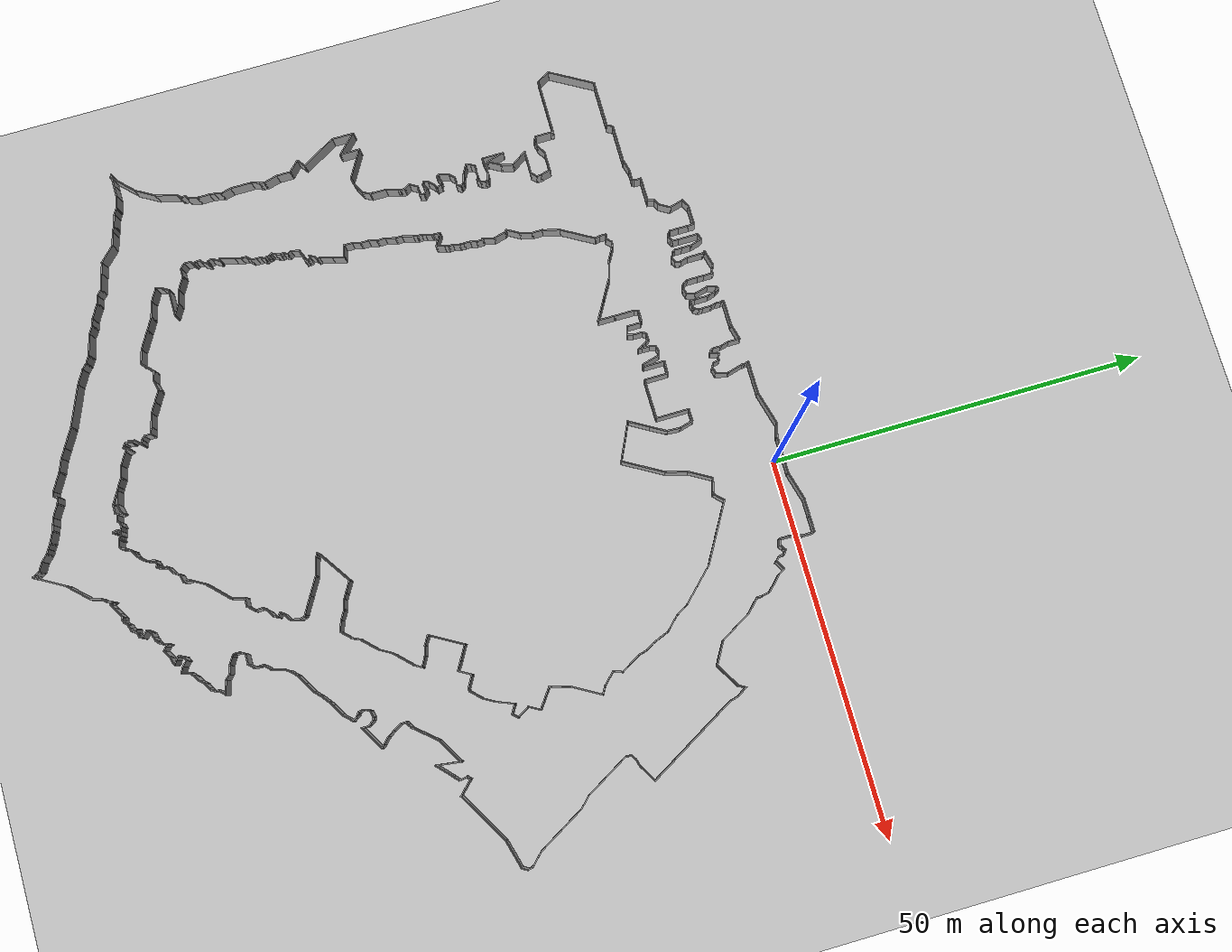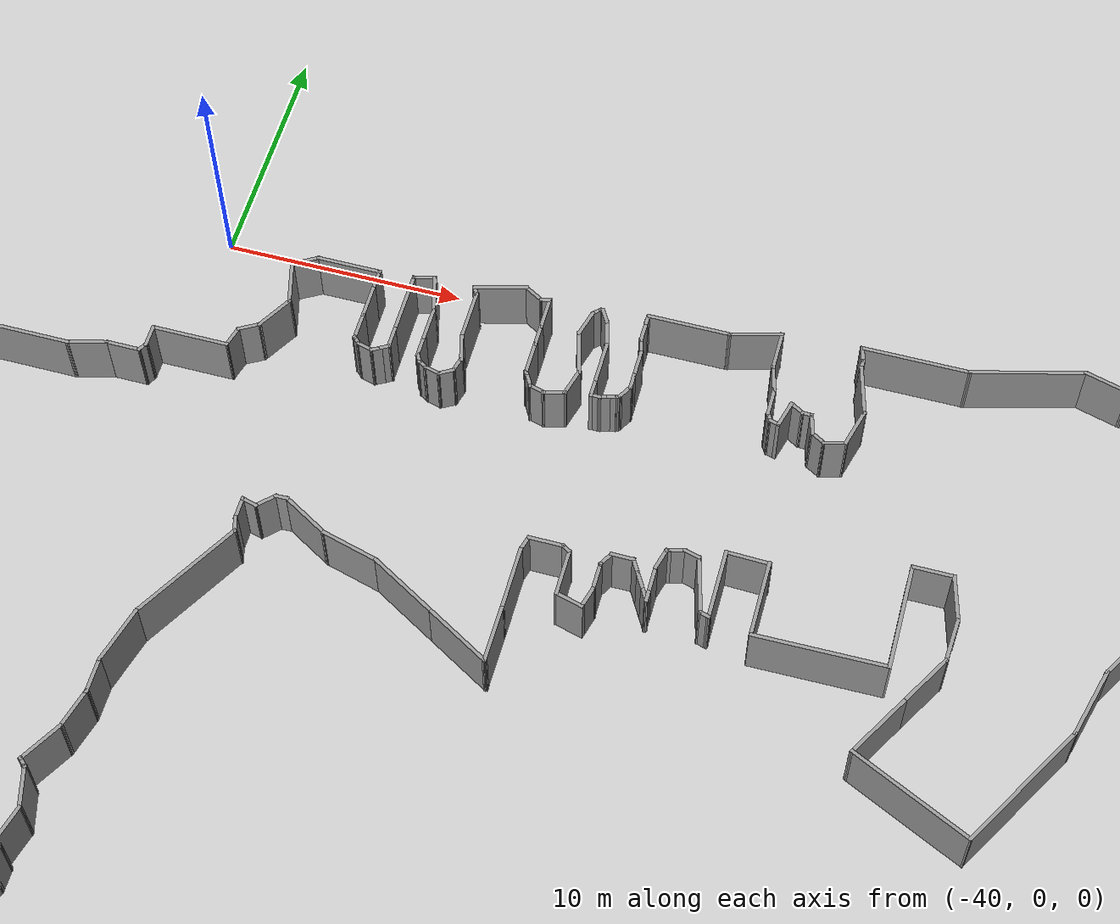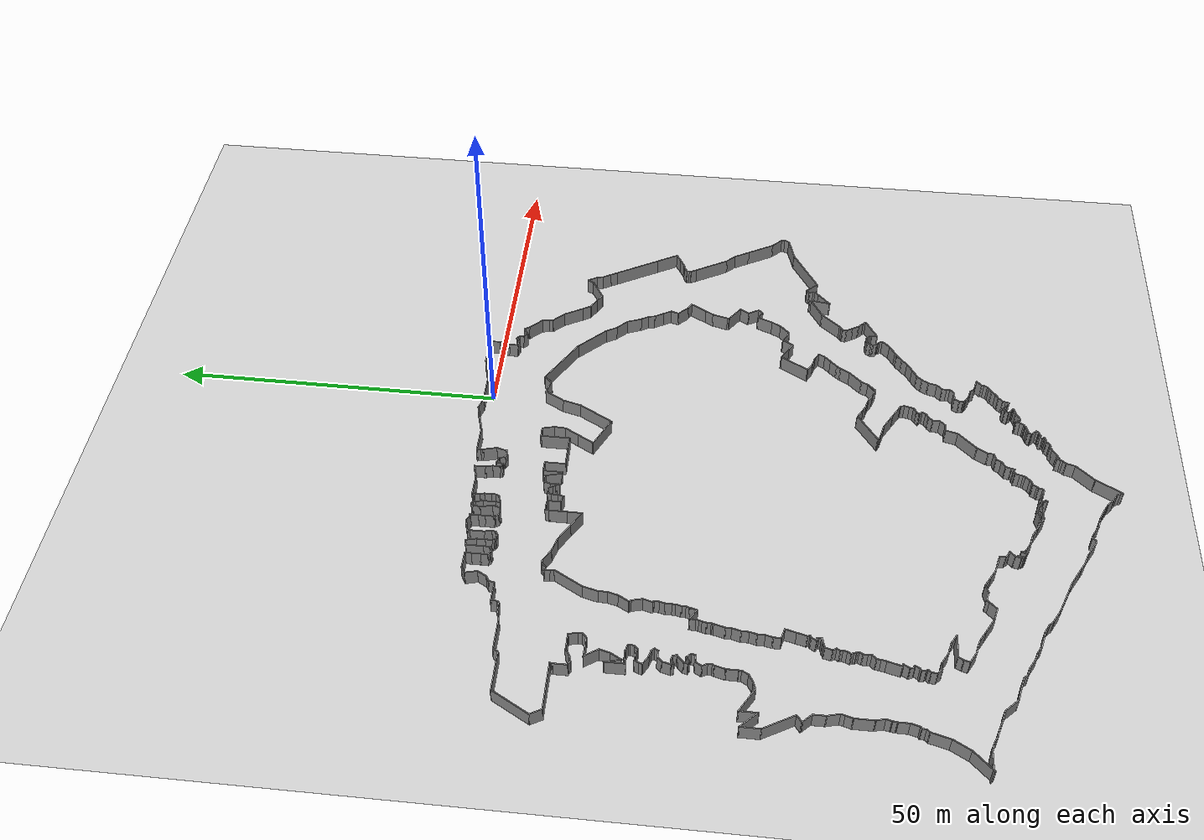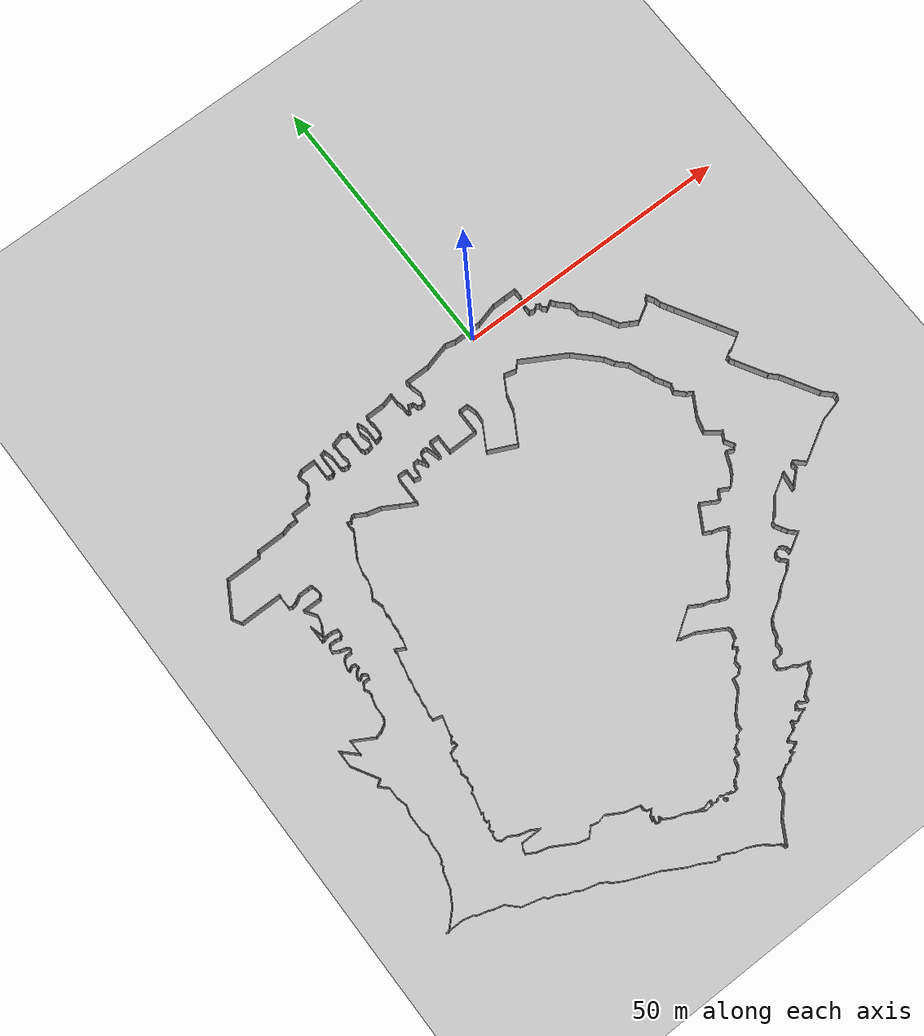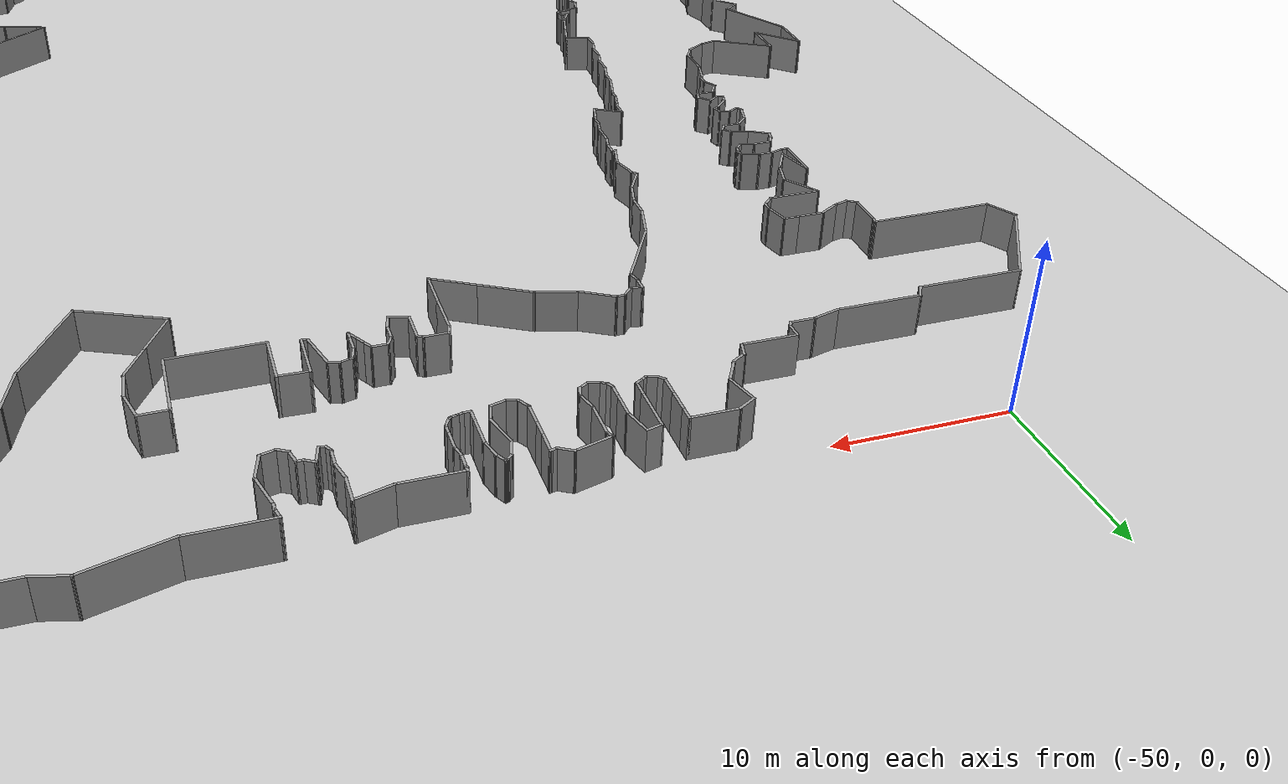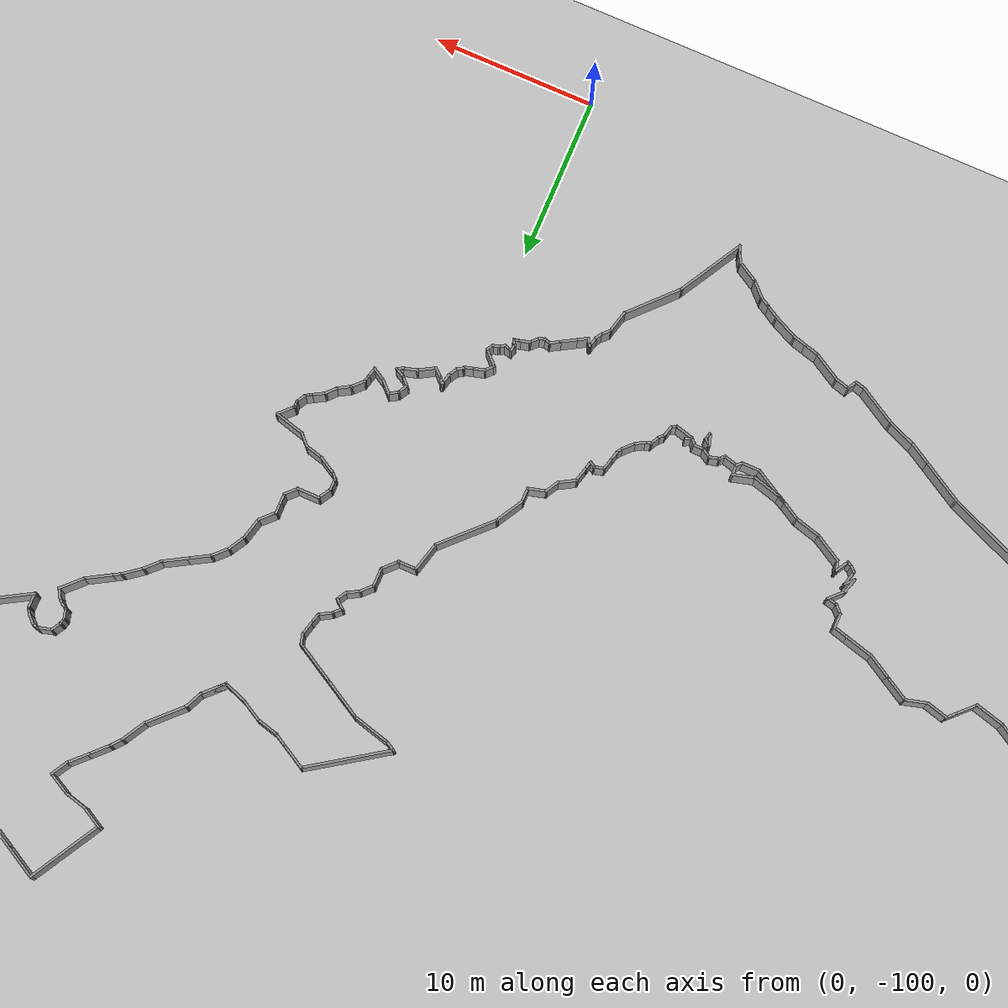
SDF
<?xml version="1.0" ?>
<sdf version="1.7">
  <world name="office_track">
    <include>
      <uri>model://sun</uri>
    </include>
    <include>
      <uri>model://ground_plane</uri>
    </include>

    <include>
      <uri>model://office_track1</uri>
      <name>office_track_walls</name>
      <pose>-10.075 -46.475 0 0 0 0</pose>
    </include>

    <physics type="ode">
      <real_time_update_rate>250.0</real_time_update_rate>
      <max_step_size>0.004</max_step_size>
    </physics>

    <!-- /get_entity_state, /set_entity_state: buggy_nav's sim_pedestrian moves its
         pedestrian with them (optional, sim-only obstacle-stop-gate checking tool). -->
    <plugin name="gazebo_ros_state" filename="libgazebo_ros_state.so">
      <ros/>
      <update_rate>50.0</update_rate>
    </plugin>
  </world>
</sdf>

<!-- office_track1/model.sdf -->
<sdf version='1.7'>
  <model name='office_track1'>
    <pose>2.3626 4.43866 0 0 -0 0</pose>
    <link name='Wall_0'>
      <collision name='Wall_0_Collision'>
        <geometry>
          <box>
            <size>1 0.15 2.5</size>
          </box>
        </geometry>
        <pose>0 0 1.25 0 -0 0</pose>
      </collision>
      <visual name='Wall_0_Visual'>
        <pose>0 0 1.25 0 -0 0</pose>
        <geometry>
          <box>
            <size>1 0.15 2.5</size>
          </box>
        </geometry>
        <material>
          <script>
            <uri>file://media/materials/scripts/gazebo.material</uri>
            <name>Gazebo/Grey</name>
          </script>
          <ambient>1 1 1 1</ambient>
        </material>
        <meta>
          <layer>0</layer>
        </meta>
      </visual>
      <pose>-30.9948 12.4778 0 0 -0 -1.5708</pose>
    </link>
    <link name='Wall_10'>
      <collision name='Wall_10_Collision'>
        <geometry>
          <box>
            <size>1.25 0.15 2.5</size>
          </box>
        </geometry>
        <pose>0 0 1.25 0 -0 0</pose>
      </collision>
      <visual name='Wall_10_Visual'>
        <pose>0 0 1.25 0 -0 0</pose>
        <geometry>
          <box>
            <size>1.25 0.15 2.5</size>
          </box>
        </geometry>
        <material>
          <script>
            <uri>file://media/materials/scripts/gazebo.material</uri>
            <name>Gazebo/Grey</name>
          </script>
          <ambient>1 1 1 1</ambient>
        </material>
        <meta>
          <layer>0</layer>
        </meta>
      </visual>
      <pose>-29.2503 12.509 0 0 -0 1.309</pose>
    </link>
    <link name='Wall_100'>
      <collision name='Wall_100_Collision'>
        <geometry>
          <box>
            <size>0.75 0.15 2.5</size>
          </box>
        </geometry>
        <pose>0 0 1.25 0 -0 0</pose>
      </collision>
      <visual name='Wall_100_Visual'>
        <pose>0 0 1.25 0 -0 0</pose>
        <geometry>
          <box>
            <size>0.75 0.15 2.5</size>
          </box>
        </geometry>
        <material>
          <script>
            <uri>file://media/materials/scripts/gazebo.material</uri>
            <name>Gazebo/Grey</name>
          </script>
          <ambient>1 1 1 1</ambient>
        </material>
        <meta>
          <layer>0</layer>
        </meta>
      </visual>
      <pose>-15.1863 -32.6198 0 0 -0 0.785398</pose>
    </link>
    <link name='Wall_101'>
      <collision name='Wall_101_Collision'>
        <geometry>
          <box>
            <size>1 0.15 2.5</size>
          </box>
        </geometry>
        <pose>0 0 1.25 0 -0 0</pose>
      </collision>
      <visual name='Wall_101_Visual'>
        <pose>0 0 1.25 0 -0 0</pose>
        <geometry>
          <box>
            <size>1 0.15 2.5</size>
          </box>
        </geometry>
        <material>
          <script>
            <uri>file://media/materials/scripts/gazebo.material</uri>
            <name>Gazebo/Grey</name>
          </script>
          <ambient>1 1 1 1</ambient>
        </material>
        <meta>
          <layer>0</layer>
        </meta>
      </visual>
      <pose>-15.0842 -32.8182 0 0 -0 -1.8326</pose>
    </link>
    <link name='Wall_102'>
      <collision name='Wall_102_Collision'>
        <geometry>
          <box>
            <size>0.25 0.15 2.5</size>
          </box>
        </geometry>
        <pose>0 0 1.25 0 -0 0</pose>
      </collision>
      <visual name='Wall_102_Visual'>
        <pose>0 0 1.25 0 -0 0</pose>
        <geometry>
          <box>
            <size>0.25 0.15 2.5</size>
          </box>
        </geometry>
        <material>
          <script>
            <uri>file://media/materials/scripts/gazebo.material</uri>
            <name>Gazebo/Grey</name>
          </script>
          <ambient>1 1 1 1</ambient>
        </material>
        <meta>
          <layer>0</layer>
        </meta>
      </visual>
      <pose>-15.1692 -33.272 0 0 -0 -1.0472</pose>
    </link>
    <link name='Wall_104'>
      <collision name='Wall_104_Collision'>
        <geometry>
          <box>
            <size>0.5 0.15 2.5</size>
          </box>
        </geometry>
        <pose>0 0 1.25 0 -0 0</pose>
      </collision>
      <visual name='Wall_104_Visual'>
        <pose>0 0 1.25 0 -0 0</pose>
        <geometry>
          <box>
            <size>0.5 0.15 2.5</size>
          </box>
        </geometry>
        <material>
          <script>
            <uri>file://media/materials/scripts/gazebo.material</uri>
            <name>Gazebo/Grey</name>
          </script>
          <ambient>1 1 1 1</ambient>
        </material>
        <meta>
          <layer>0</layer>
        </meta>
      </visual>
      <pose>-15.0704 -33.3525 0 0 -0 -0.785398</pose>
    </link>
    <link name='Wall_105'>
      <collision name='Wall_105_Collision'>
        <geometry>
          <box>
            <size>0.5 0.15 2.5</size>
          </box>
        </geometry>
        <pose>0 0 1.25 0 -0 0</pose>
      </collision>
      <visual name='Wall_105_Visual'>
        <pose>0 0 1.25 0 -0 0</pose>
        <geometry>
          <box>
            <size>0.5 0.15 2.5</size>
          </box>
        </geometry>
        <material>
          <script>
            <uri>file://media/materials/scripts/gazebo.material</uri>
            <name>Gazebo/Grey</name>
          </script>
          <ambient>1 1 1 1</ambient>
        </material>
        <meta>
          <layer>0</layer>
        </meta>
      </visual>
      <pose>-14.7951 -33.5637 0 0 -0 -0.523599</pose>
    </link>
    <link name='Wall_106'>
      <collision name='Wall_106_Collision'>
        <geometry>
          <box>
            <size>1 0.15 2.5</size>
          </box>
        </geometry>
        <pose>0 0 1.25 0 -0 0</pose>
      </collision>
      <visual name='Wall_106_Visual'>
        <pose>0 0 1.25 0 -0 0</pose>
        <geometry>
          <box>
            <size>1 0.15 2.5</size>
          </box>
        </geometry>
        <material>
          <script>
            <uri>file://media/materials/scripts/gazebo.material</uri>
            <name>Gazebo/Grey</name>
          </script>
          <ambient>1 1 1 1</ambient>
        </material>
        <meta>
          <layer>0</layer>
        </meta>
      </visual>
      <pose>-14.4311 -33.2832 0 0 -0 1.0472</pose>
    </link>
    <link name='Wall_107'>
      <collision name='Wall_107_Collision'>
        <geometry>
          <box>
            <size>0.75 0.15 2.5</size>
          </box>
        </geometry>
        <pose>0 0 1.25 0 -0 0</pose>
      </collision>
      <visual name='Wall_107_Visual'>
        <pose>0 0 1.25 0 -0 0</pose>
        <geometry>
          <box>
            <size>0.75 0.15 2.5</size>
          </box>
        </geometry>
        <material>
          <script>
            <uri>file://media/materials/scripts/gazebo.material</uri>
            <name>Gazebo/Grey</name>
          </script>
          <ambient>1 1 1 1</ambient>
        </material>
        <meta>
          <layer>0</layer>
        </meta>
      </visual>
      <pose>-14.1409 -33.2049 0 0 -0 -1.309</pose>
    </link>
    <link name='Wall_108'>
      <collision name='Wall_108_Collision'>
        <geometry>
          <box>
            <size>2 0.15 2.5</size>
          </box>
        </geometry>
        <pose>0 0 1.25 0 -0 0</pose>
      </collision>
      <visual name='Wall_108_Visual'>
        <pose>0 0 1.25 0 -0 0</pose>
        <geometry>
          <box>
            <size>2 0.15 2.5</size>
          </box>
        </geometry>
        <material>
          <script>
            <uri>file://media/materials/scripts/gazebo.material</uri>
            <name>Gazebo/Grey</name>
          </script>
          <ambient>1 1 1 1</ambient>
        </material>
        <meta>
          <layer>0</layer>
        </meta>
      </visual>
      <pose>-13.2622 -33.9571 0 0 -0 -0.523599</pose>
    </link>
    <link name='Wall_109'>
      <collision name='Wall_109_Collision'>
        <geometry>
          <box>
            <size>1.75 0.15 2.5</size>
          </box>
        </geometry>
        <pose>0 0 1.25 0 -0 0</pose>
      </collision>
      <visual name='Wall_109_Visual'>
        <pose>0 0 1.25 0 -0 0</pose>
        <geometry>
          <box>
            <size>1.75 0.15 2.5</size>
          </box>
        </geometry>
        <material>
          <script>
            <uri>file://media/materials/scripts/gazebo.material</uri>
            <name>Gazebo/Grey</name>
          </script>
          <ambient>1 1 1 1</ambient>
        </material>
        <meta>
          <layer>0</layer>
        </meta>
      </visual>
      <pose>-11.6884 -34.6267 0 0 -0 -0.261799</pose>
    </link>
    <link name='Wall_110'>
      <collision name='Wall_110_Collision'>
        <geometry>
          <box>
            <size>1.75 0.15 2.5</size>
          </box>
        </geometry>
        <pose>0 0 1.25 0 -0 0</pose>
      </collision>
      <visual name='Wall_110_Visual'>
        <pose>0 0 1.25 0 -0 0</pose>
        <geometry>
          <box>
            <size>1.75 0.15 2.5</size>
          </box>
        </geometry>
        <material>
          <script>
            <uri>file://media/materials/scripts/gazebo.material</uri>
            <name>Gazebo/Grey</name>
          </script>
          <ambient>1 1 1 1</ambient>
        </material>
        <meta>
          <layer>0</layer>
        </meta>
      </visual>
      <pose>-10.2228 -35.2338 0 0 -0 -0.523599</pose>
    </link>
    <link name='Wall_111'>
      <collision name='Wall_111_Collision'>
        <geometry>
          <box>
            <size>2 0.15 2.5</size>
          </box>
        </geometry>
        <pose>0 0 1.25 0 -0 0</pose>
      </collision>
      <visual name='Wall_111_Visual'>
        <pose>0 0 1.25 0 -0 0</pose>
        <geometry>
          <box>
            <size>2 0.15 2.5</size>
          </box>
        </geometry>
        <material>
          <script>
            <uri>file://media/materials/scripts/gazebo.material</uri>
            <name>Gazebo/Grey</name>
          </script>
          <ambient>1 1 1 1</ambient>
        </material>
        <meta>
          <layer>0</layer>
        </meta>
      </visual>
      <pose>-8.63653 -35.8732 0 0 -0 -0.261799</pose>
    </link>
    <link name='Wall_112'>
      <collision name='Wall_112_Collision'>
        <geometry>
          <box>
            <size>1.5 0.15 2.5</size>
          </box>
        </geometry>
        <pose>0 0 1.25 0 -0 0</pose>
      </collision>
      <visual name='Wall_112_Visual'>
        <pose>0 0 1.25 0 -0 0</pose>
        <geometry>
          <box>
            <size>1.5 0.15 2.5</size>
          </box>
        </geometry>
        <material>
          <script>
            <uri>file://media/materials/scripts/gazebo.material</uri>
            <name>Gazebo/Grey</name>
          </script>
          <ambient>1 1 1 1</ambient>
        </material>
        <meta>
          <layer>0</layer>
        </meta>
      </visual>
      <pose>-7.09104 -35.9379 0 0 -0 0.261799</pose>
    </link>
    <link name='Wall_113'>
      <collision name='Wall_113_Collision'>
        <geometry>
          <box>
            <size>0.75 0.15 2.5</size>
          </box>
        </geometry>
        <pose>0 0 1.25 0 -0 0</pose>
      </collision>
      <visual name='Wall_113_Visual'>
        <pose>0 0 1.25 0 -0 0</pose>
        <geometry>
          <box>
            <size>0.75 0.15 2.5</size>
          </box>
        </geometry>
        <material>
          <script>
            <uri>file://media/materials/scripts/gazebo.material</uri>
            <name>Gazebo/Grey</name>
          </script>
          <ambient>1 1 1 1</ambient>
        </material>
        <meta>
          <layer>0</layer>
        </meta>
      </visual>
      <pose>-6.43904 -36.0632 0 0 -0 -1.5708</pose>
    </link>
    <link name='Wall_114'>
      <collision name='Wall_114_Collision'>
        <geometry>
          <box>
            <size>0.5 0.15 2.5</size>
          </box>
        </geometry>
        <pose>0 0 1.25 0 -0 0</pose>
      </collision>
      <visual name='Wall_114_Visual'>
        <pose>0 0 1.25 0 -0 0</pose>
        <geometry>
          <box>
            <size>0.5 0.15 2.5</size>
          </box>
        </geometry>
        <material>
          <script>
            <uri>file://media/materials/scripts/gazebo.material</uri>
            <name>Gazebo/Grey</name>
          </script>
          <ambient>1 1 1 1</ambient>
        </material>
        <meta>
          <layer>0</layer>
        </meta>
      </visual>
      <pose>-6.56279 -36.4869 0 0 -0 -2.35619</pose>
    </link>
    <link name='Wall_115'>
      <collision name='Wall_115_Collision'>
        <geometry>
          <box>
            <size>1.25 0.15 2.5</size>
          </box>
        </geometry>
        <pose>0 0 1.25 0 -0 0</pose>
      </collision>
      <visual name='Wall_115_Visual'>
        <pose>0 0 1.25 0 -0 0</pose>
        <geometry>
          <box>
            <size>1.25 0.15 2.5</size>
          </box>
        </geometry>
        <material>
          <script>
            <uri>file://media/materials/scripts/gazebo.material</uri>
            <name>Gazebo/Grey</name>
          </script>
          <ambient>1 1 1 1</ambient>
        </material>
        <meta>
          <layer>0</layer>
        </meta>
      </visual>
      <pose>-7.23653 -36.6107 0 0 -0 3.14159</pose>
    </link>
    <link name='Wall_116'>
      <collision name='Wall_116_Collision'>
        <geometry>
          <box>
            <size>2.5 0.15 2.5</size>
          </box>
        </geometry>
        <pose>0 0 1.25 0 -0 0</pose>
      </collision>
      <visual name='Wall_116_Visual'>
        <pose>0 0 1.25 0 -0 0</pose>
        <geometry>
          <box>
            <size>2.5 0.15 2.5</size>
          </box>
        </geometry>
        <material>
          <script>
            <uri>file://media/materials/scripts/gazebo.material</uri>
            <name>Gazebo/Grey</name>
          </script>
          <ambient>1 1 1 1</ambient>
        </material>
        <meta>
          <layer>0</layer>
        </meta>
      </visual>
      <pose>-8.80411 -36.0232 0 0 -0 2.61799</pose>
    </link>
    <link name='Wall_118'>
      <collision name='Wall_118_Collision'>
        <geometry>
          <box>
            <size>1 0.15 2.5</size>
          </box>
        </geometry>
        <pose>0 0 1.25 0 -0 0</pose>
      </collision>
      <visual name='Wall_118_Visual'>
        <pose>0 0 1.25 0 -0 0</pose>
        <geometry>
          <box>
            <size>1 0.15 2.5</size>
          </box>
        </geometry>
        <material>
          <script>
            <uri>file://media/materials/scripts/gazebo.material</uri>
            <name>Gazebo/Grey</name>
          </script>
          <ambient>1 1 1 1</ambient>
        </material>
        <meta>
          <layer>0</layer>
        </meta>
      </visual>
      <pose>-6.02853 -36.4732 0 0 -0 -0.261799</pose>
    </link>
    <link name='Wall_119'>
      <collision name='Wall_119_Collision'>
        <geometry>
          <box>
            <size>0.5 0.15 2.5</size>
          </box>
        </geometry>
        <pose>0 0 1.25 0 -0 0</pose>
      </collision>
      <visual name='Wall_119_Visual'>
        <pose>0 0 1.25 0 -0 0</pose>
        <geometry>
          <box>
            <size>0.5 0.15 2.5</size>
          </box>
        </geometry>
        <material>
          <script>
            <uri>file://media/materials/scripts/gazebo.material</uri>
            <name>Gazebo/Grey</name>
          </script>
          <ambient>1 1 1 1</ambient>
        </material>
        <meta>
          <layer>0</layer>
        </meta>
      </visual>
      <pose>-5.49426 -36.4594 0 0 -0 0.785398</pose>
    </link>
    <link name='Wall_12'>
      <collision name='Wall_12_Collision'>
        <geometry>
          <box>
            <size>1.75 0.15 2.5</size>
          </box>
        </geometry>
        <pose>0 0 1.25 0 -0 0</pose>
      </collision>
      <visual name='Wall_12_Visual'>
        <pose>0 0 1.25 0 -0 0</pose>
        <geometry>
          <box>
            <size>1.75 0.15 2.5</size>
          </box>
        </geometry>
        <material>
          <script>
            <uri>file://media/materials/scripts/gazebo.material</uri>
            <name>Gazebo/Grey</name>
          </script>
          <ambient>1 1 1 1</ambient>
        </material>
        <meta>
          <layer>0</layer>
        </meta>
      </visual>
      <pose>-31.7195 8.74818 0 0 -0 -1.8326</pose>
    </link>
    <link name='Wall_120'>
      <collision name='Wall_120_Collision'>
        <geometry>
          <box>
            <size>0.75 0.15 2.5</size>
          </box>
        </geometry>
        <pose>0 0 1.25 0 -0 0</pose>
      </collision>
      <visual name='Wall_120_Visual'>
        <pose>0 0 1.25 0 -0 0</pose>
        <geometry>
          <box>
            <size>0.75 0.15 2.5</size>
          </box>
        </geometry>
        <material>
          <script>
            <uri>file://media/materials/scripts/gazebo.material</uri>
            <name>Gazebo/Grey</name>
          </script>
          <ambient>1 1 1 1</ambient>
        </material>
        <meta>
          <layer>0</layer>
        </meta>
      </visual>
      <pose>-5.08074 -36.258 0 0 -0 0.261799</pose>
    </link>
    <link name='Wall_121'>
      <collision name='Wall_121_Collision'>
        <geometry>
          <box>
            <size>0.75 0.15 2.5</size>
          </box>
        </geometry>
        <pose>0 0 1.25 0 -0 0</pose>
      </collision>
      <visual name='Wall_121_Visual'>
        <pose>0 0 1.25 0 -0 0</pose>
        <geometry>
          <box>
            <size>0.75 0.15 2.5</size>
          </box>
        </geometry>
        <material>
          <script>
            <uri>file://media/materials/scripts/gazebo.material</uri>
            <name>Gazebo/Grey</name>
          </script>
          <ambient>1 1 1 1</ambient>
        </material>
        <meta>
          <layer>0</layer>
        </meta>
      </visual>
      <pose>-4.53116 -36.3304 0 0 -0 -0.523599</pose>
    </link>
    <link name='Wall_122'>
      <collision name='Wall_122_Collision'>
        <geometry>
          <box>
            <size>0.75 0.15 2.5</size>
          </box>
        </geometry>
        <pose>0 0 1.25 0 -0 0</pose>
      </collision>
      <visual name='Wall_122_Visual'>
        <pose>0 0 1.25 0 -0 0</pose>
        <geometry>
          <box>
            <size>0.75 0.15 2.5</size>
          </box>
        </geometry>
        <material>
          <script>
            <uri>file://media/materials/scripts/gazebo.material</uri>
            <name>Gazebo/Grey</name>
          </script>
          <ambient>1 1 1 1</ambient>
        </material>
        <meta>
          <layer>0</layer>
        </meta>
      </visual>
      <pose>-3.97135 -36.4804 0 0 -0 0</pose>
    </link>
    <link name='Wall_123'>
      <collision name='Wall_123_Collision'>
        <geometry>
          <box>
            <size>0.25 0.15 2.5</size>
          </box>
        </geometry>
        <pose>0 0 1.25 0 -0 0</pose>
      </collision>
      <visual name='Wall_123_Visual'>
        <pose>0 0 1.25 0 -0 0</pose>
        <geometry>
          <box>
            <size>0.25 0.15 2.5</size>
          </box>
        </geometry>
        <material>
          <script>
            <uri>file://media/materials/scripts/gazebo.material</uri>
            <name>Gazebo/Grey</name>
          </script>
          <ambient>1 1 1 1</ambient>
        </material>
        <meta>
          <layer>0</layer>
        </meta>
      </visual>
      <pose>-3.65841 -36.5287 0 0 -0 -1.309</pose>
    </link>
    <link name='Wall_124'>
      <collision name='Wall_124_Collision'>
        <geometry>
          <box>
            <size>0.5 0.15 2.5</size>
          </box>
        </geometry>
        <pose>0 0 1.25 0 -0 0</pose>
      </collision>
      <visual name='Wall_124_Visual'>
        <pose>0 0 1.25 0 -0 0</pose>
        <geometry>
          <box>
            <size>0.5 0.15 2.5</size>
          </box>
        </geometry>
        <material>
          <script>
            <uri>file://media/materials/scripts/gazebo.material</uri>
            <name>Gazebo/Grey</name>
          </script>
          <ambient>1 1 1 1</ambient>
        </material>
        <meta>
          <layer>0</layer>
        </meta>
      </visual>
      <pose>-3.52172 -36.7007 0 0 -0 -0.785398</pose>
    </link>
    <link name='Wall_125'>
      <collision name='Wall_125_Collision'>
        <geometry>
          <box>
            <size>0.5 0.15 2.5</size>
          </box>
        </geometry>
        <pose>0 0 1.25 0 -0 0</pose>
      </collision>
      <visual name='Wall_125_Visual'>
        <pose>0 0 1.25 0 -0 0</pose>
        <geometry>
          <box>
            <size>0.5 0.15 2.5</size>
          </box>
        </geometry>
        <material>
          <script>
            <uri>file://media/materials/scripts/gazebo.material</uri>
            <name>Gazebo/Grey</name>
          </script>
          <ambient>1 1 1 1</ambient>
        </material>
        <meta>
          <layer>0</layer>
        </meta>
      </visual>
      <pose>-3.24642 -36.737 0 0 -0 0.523599</pose>
    </link>
    <link name='Wall_127'>
      <collision name='Wall_127_Collision'>
        <geometry>
          <box>
            <size>0.75 0.15 2.5</size>
          </box>
        </geometry>
        <pose>0 0 1.25 0 -0 0</pose>
      </collision>
      <visual name='Wall_127_Visual'>
        <pose>0 0 1.25 0 -0 0</pose>
        <geometry>
          <box>
            <size>0.75 0.15 2.5</size>
          </box>
        </geometry>
        <material>
          <script>
            <uri>file://media/materials/scripts/gazebo.material</uri>
            <name>Gazebo/Grey</name>
          </script>
          <ambient>1 1 1 1</ambient>
        </material>
        <meta>
          <layer>0</layer>
        </meta>
      </visual>
      <pose>-4.42722 -37.1073 0 0 -0 -1.309</pose>
    </link>
    <link name='Wall_128'>
      <collision name='Wall_128_Collision'>
        <geometry>
          <box>
            <size>0.25 0.15 2.5</size>
          </box>
        </geometry>
        <pose>0 0 1.25 0 -0 0</pose>
      </collision>
      <visual name='Wall_128_Visual'>
        <pose>0 0 1.25 0 -0 0</pose>
        <geometry>
          <box>
            <size>0.25 0.15 2.5</size>
          </box>
        </geometry>
        <material>
          <script>
            <uri>file://media/materials/scripts/gazebo.material</uri>
            <name>Gazebo/Grey</name>
          </script>
          <ambient>1 1 1 1</ambient>
        </material>
        <meta>
          <layer>0</layer>
        </meta>
      </visual>
      <pose>-4.30628 -37.4221 0 0 -0 -0.523599</pose>
    </link>
    <link name='Wall_129'>
      <collision name='Wall_129_Collision'>
        <geometry>
          <box>
            <size>0.5 0.15 2.5</size>
          </box>
        </geometry>
        <pose>0 0 1.25 0 -0 0</pose>
      </collision>
      <visual name='Wall_129_Visual'>
        <pose>0 0 1.25 0 -0 0</pose>
        <geometry>
          <box>
            <size>0.5 0.15 2.5</size>
          </box>
        </geometry>
        <material>
          <script>
            <uri>file://media/materials/scripts/gazebo.material</uri>
            <name>Gazebo/Grey</name>
          </script>
          <ambient>1 1 1 1</ambient>
        </material>
        <meta>
          <layer>0</layer>
        </meta>
      </visual>
      <pose>-4.21768 -37.278 0 0 -0 1.309</pose>
    </link>
    <link name='Wall_130'>
      <collision name='Wall_130_Collision'>
        <geometry>
          <box>
            <size>0.592159 0.15 2.5</size>
          </box>
        </geometry>
        <pose>0 0 1.25 0 -0 0</pose>
      </collision>
      <visual name='Wall_130_Visual'>
        <pose>0 0 1.25 0 -0 0</pose>
        <geometry>
          <box>
            <size>0.592159 0.15 2.5</size>
          </box>
        </geometry>
        <material>
          <script>
            <uri>file://media/materials/scripts/gazebo.material</uri>
            <name>Gazebo/Grey</name>
          </script>
          <ambient>1 1 1 1</ambient>
        </material>
        <meta>
          <layer>0</layer>
        </meta>
      </visual>
      <pose>-4.33863 -36.9632 0 0 -0 2.42181</pose>
    </link>
    <link name='Wall_132'>
      <collision name='Wall_132_Collision'>
        <geometry>
          <box>
            <size>1.25 0.15 2.5</size>
          </box>
        </geometry>
        <pose>0 0 1.25 0 -0 0</pose>
      </collision>
      <visual name='Wall_132_Visual'>
        <pose>0 0 1.25 0 -0 0</pose>
        <geometry>
          <box>
            <size>1.25 0.15 2.5</size>
          </box>
        </geometry>
        <material>
          <script>
            <uri>file://media/materials/scripts/gazebo.material</uri>
            <name>Gazebo/Grey</name>
          </script>
          <ambient>1 1 1 1</ambient>
        </material>
        <meta>
          <layer>0</layer>
        </meta>
      </visual>
      <pose>-2.86672 -36.9668 0 0 -0 -0.261799</pose>
    </link>
    <link name='Wall_133'>
      <collision name='Wall_133_Collision'>
        <geometry>
          <box>
            <size>0.5 0.15 2.5</size>
          </box>
        </geometry>
        <pose>0 0 1.25 0 -0 0</pose>
      </collision>
      <visual name='Wall_133_Visual'>
        <pose>0 0 1.25 0 -0 0</pose>
        <geometry>
          <box>
            <size>0.5 0.15 2.5</size>
          </box>
        </geometry>
        <material>
          <script>
            <uri>file://media/materials/scripts/gazebo.material</uri>
            <name>Gazebo/Grey</name>
          </script>
          <ambient>1 1 1 1</ambient>
        </material>
        <meta>
          <layer>0</layer>
        </meta>
      </visual>
      <pose>-2.18391 -37.0217 0 0 -0 0.523599</pose>
    </link>
    <link name='Wall_134'>
      <collision name='Wall_134_Collision'>
        <geometry>
          <box>
            <size>0.75 0.15 2.5</size>
          </box>
        </geometry>
        <pose>0 0 1.25 0 -0 0</pose>
      </collision>
      <visual name='Wall_134_Visual'>
        <pose>0 0 1.25 0 -0 0</pose>
        <geometry>
          <box>
            <size>0.75 0.15 2.5</size>
          </box>
        </geometry>
        <material>
          <script>
            <uri>file://media/materials/scripts/gazebo.material</uri>
            <name>Gazebo/Grey</name>
          </script>
          <ambient>1 1 1 1</ambient>
        </material>
        <meta>
          <layer>0</layer>
        </meta>
      </visual>
      <pose>-1.95471 -36.6444 0 0 -0 1.309</pose>
    </link>
    <link name='Wall_135'>
      <collision name='Wall_135_Collision'>
        <geometry>
          <box>
            <size>0.5 0.15 2.5</size>
          </box>
        </geometry>
        <pose>0 0 1.25 0 -0 0</pose>
      </collision>
      <visual name='Wall_135_Visual'>
        <pose>0 0 1.25 0 -0 0</pose>
        <geometry>
          <box>
            <size>0.5 0.15 2.5</size>
          </box>
        </geometry>
        <material>
          <script>
            <uri>file://media/materials/scripts/gazebo.material</uri>
            <name>Gazebo/Grey</name>
          </script>
          <ambient>1 1 1 1</ambient>
        </material>
        <meta>
          <layer>0</layer>
        </meta>
      </visual>
      <pose>-1.75332 -36.2309 0 0 -0 0.785398</pose>
    </link>
    <link name='Wall_136'>
      <collision name='Wall_136_Collision'>
        <geometry>
          <box>
            <size>0.75 0.15 2.5</size>
          </box>
        </geometry>
        <pose>0 0 1.25 0 -0 0</pose>
      </collision>
      <visual name='Wall_136_Visual'>
        <pose>0 0 1.25 0 -0 0</pose>
        <geometry>
          <box>
            <size>0.75 0.15 2.5</size>
          </box>
        </geometry>
        <material>
          <script>
            <uri>file://media/materials/scripts/gazebo.material</uri>
            <name>Gazebo/Grey</name>
          </script>
          <ambient>1 1 1 1</ambient>
        </material>
        <meta>
          <layer>0</layer>
        </meta>
      </visual>
      <pose>-1.47957 -35.8473 0 0 -0 1.0472</pose>
    </link>
    <link name='Wall_137'>
      <collision name='Wall_137_Collision'>
        <geometry>
          <box>
            <size>0.5 0.15 2.5</size>
          </box>
        </geometry>
        <pose>0 0 1.25 0 -0 0</pose>
      </collision>
      <visual name='Wall_137_Visual'>
        <pose>0 0 1.25 0 -0 0</pose>
        <geometry>
          <box>
            <size>0.5 0.15 2.5</size>
          </box>
        </geometry>
        <material>
          <script>
            <uri>file://media/materials/scripts/gazebo.material</uri>
            <name>Gazebo/Grey</name>
          </script>
          <ambient>1 1 1 1</ambient>
        </material>
        <meta>
          <layer>0</layer>
        </meta>
      </visual>
      <pose>-1.16054 -35.5422 0 0 -0 0.261799</pose>
    </link>
    <link name='Wall_138'>
      <collision name='Wall_138_Collision'>
        <geometry>
          <box>
            <size>0.75 0.15 2.5</size>
          </box>
        </geometry>
        <pose>0 0 1.25 0 -0 0</pose>
      </collision>
      <visual name='Wall_138_Visual'>
        <pose>0 0 1.25 0 -0 0</pose>
        <geometry>
          <box>
            <size>0.75 0.15 2.5</size>
          </box>
        </geometry>
        <material>
          <script>
            <uri>file://media/materials/scripts/gazebo.material</uri>
            <name>Gazebo/Grey</name>
          </script>
          <ambient>1 1 1 1</ambient>
        </material>
        <meta>
          <layer>0</layer>
        </meta>
      </visual>
      <pose>-0.731692 -35.3469 0 0 -0 0.523599</pose>
    </link>
    <link name='Wall_139'>
      <collision name='Wall_139_Collision'>
        <geometry>
          <box>
            <size>1 0.15 2.5</size>
          </box>
        </geometry>
        <pose>0 0 1.25 0 -0 0</pose>
      </collision>
      <visual name='Wall_139_Visual'>
        <pose>0 0 1.25 0 -0 0</pose>
        <geometry>
          <box>
            <size>1 0.15 2.5</size>
          </box>
        </geometry>
        <material>
          <script>
            <uri>file://media/materials/scripts/gazebo.material</uri>
            <name>Gazebo/Grey</name>
          </script>
          <ambient>1 1 1 1</ambient>
        </material>
        <meta>
          <layer>0</layer>
        </meta>
      </visual>
      <pose>-0.171364 -34.8964 0 0 -0 0.785398</pose>
    </link>
    <link name='Wall_14'>
      <collision name='Wall_14_Collision'>
        <geometry>
          <box>
            <size>1 0.15 2.5</size>
          </box>
        </geometry>
        <pose>0 0 1.25 0 -0 0</pose>
      </collision>
      <visual name='Wall_14_Visual'>
        <pose>0 0 1.25 0 -0 0</pose>
        <geometry>
          <box>
            <size>1 0.15 2.5</size>
          </box>
        </geometry>
        <material>
          <script>
            <uri>file://media/materials/scripts/gazebo.material</uri>
            <name>Gazebo/Grey</name>
          </script>
          <ambient>1 1 1 1</ambient>
        </material>
        <meta>
          <layer>0</layer>
        </meta>
      </visual>
      <pose>-28.5202 17.672 0 0 -0 -1.5708</pose>
    </link>
    <link name='Wall_140'>
      <collision name='Wall_140_Collision'>
        <geometry>
          <box>
            <size>0.5 0.15 2.5</size>
          </box>
        </geometry>
        <pose>0 0 1.25 0 -0 0</pose>
      </collision>
      <visual name='Wall_140_Visual'>
        <pose>0 0 1.25 0 -0 0</pose>
        <geometry>
          <box>
            <size>0.5 0.15 2.5</size>
          </box>
        </geometry>
        <material>
          <script>
            <uri>file://media/materials/scripts/gazebo.material</uri>
            <name>Gazebo/Grey</name>
          </script>
          <ambient>1 1 1 1</ambient>
        </material>
        <meta>
          <layer>0</layer>
        </meta>
      </visual>
      <pose>0.216656 -34.4443 0 0 -0 1.0472</pose>
    </link>
    <link name='Wall_141'>
      <collision name='Wall_141_Collision'>
        <geometry>
          <box>
            <size>0.75 0.15 2.5</size>
          </box>
        </geometry>
        <pose>0 0 1.25 0 -0 0</pose>
      </collision>
      <visual name='Wall_141_Visual'>
        <pose>0 0 1.25 0 -0 0</pose>
        <geometry>
          <box>
            <size>0.75 0.15 2.5</size>
          </box>
        </geometry>
        <material>
          <script>
            <uri>file://media/materials/scripts/gazebo.material</uri>
            <name>Gazebo/Grey</name>
          </script>
          <ambient>1 1 1 1</ambient>
        </material>
        <meta>
          <layer>0</layer>
        </meta>
      </visual>
      <pose>0.381802 -34.003 0 0 -0 1.309</pose>
    </link>
    <link name='Wall_142'>
      <collision name='Wall_142_Collision'>
        <geometry>
          <box>
            <size>0.75 0.15 2.5</size>
          </box>
        </geometry>
        <pose>0 0 1.25 0 -0 0</pose>
      </collision>
      <visual name='Wall_142_Visual'>
        <pose>0 0 1.25 0 -0 0</pose>
        <geometry>
          <box>
            <size>0.75 0.15 2.5</size>
          </box>
        </geometry>
        <material>
          <script>
            <uri>file://media/materials/scripts/gazebo.material</uri>
            <name>Gazebo/Grey</name>
          </script>
          <ambient>1 1 1 1</ambient>
        </material>
        <meta>
          <layer>0</layer>
        </meta>
      </visual>
      <pose>0.537094 -33.4234 0 0 -0 1.309</pose>
    </link>
    <link name='Wall_143'>
      <collision name='Wall_143_Collision'>
        <geometry>
          <box>
            <size>0.75 0.15 2.5</size>
          </box>
        </geometry>
        <pose>0 0 1.25 0 -0 0</pose>
      </collision>
      <visual name='Wall_143_Visual'>
        <pose>0 0 1.25 0 -0 0</pose>
        <geometry>
          <box>
            <size>0.75 0.15 2.5</size>
          </box>
        </geometry>
        <material>
          <script>
            <uri>file://media/materials/scripts/gazebo.material</uri>
            <name>Gazebo/Grey</name>
          </script>
          <ambient>1 1 1 1</ambient>
        </material>
        <meta>
          <layer>0</layer>
        </meta>
      </visual>
      <pose>0.904517 -33.056 0 0 -0 0.261799</pose>
    </link>
    <link name='Wall_144'>
      <collision name='Wall_144_Collision'>
        <geometry>
          <box>
            <size>0.5 0.15 2.5</size>
          </box>
        </geometry>
        <pose>0 0 1.25 0 -0 0</pose>
      </collision>
      <visual name='Wall_144_Visual'>
        <pose>0 0 1.25 0 -0 0</pose>
        <geometry>
          <box>
            <size>0.5 0.15 2.5</size>
          </box>
        </geometry>
        <material>
          <script>
            <uri>file://media/materials/scripts/gazebo.material</uri>
            <name>Gazebo/Grey</name>
          </script>
          <ambient>1 1 1 1</ambient>
        </material>
        <meta>
          <layer>0</layer>
        </meta>
      </visual>
      <pose>1.34585 -33.0659 0 0 -0 -0.523599</pose>
    </link>
    <link name='Wall_146'>
      <collision name='Wall_146_Collision'>
        <geometry>
          <box>
            <size>2 0.15 2.5</size>
          </box>
        </geometry>
        <pose>0 0 1.25 0 -0 0</pose>
      </collision>
      <visual name='Wall_146_Visual'>
        <pose>0 0 1.25 0 -0 0</pose>
        <geometry>
          <box>
            <size>2 0.15 2.5</size>
          </box>
        </geometry>
        <material>
          <script>
            <uri>file://media/materials/scripts/gazebo.material</uri>
            <name>Gazebo/Grey</name>
          </script>
          <ambient>1 1 1 1</ambient>
        </material>
        <meta>
          <layer>0</layer>
        </meta>
      </visual>
      <pose>4.73961 -28.6112 0 0 -0 -2.0944</pose>
    </link>
    <link name='Wall_147'>
      <collision name='Wall_147_Collision'>
        <geometry>
          <box>
            <size>1 0.15 2.5</size>
          </box>
        </geometry>
        <pose>0 0 1.25 0 -0 0</pose>
      </collision>
      <visual name='Wall_147_Visual'>
        <pose>0 0 1.25 0 -0 0</pose>
        <geometry>
          <box>
            <size>1 0.15 2.5</size>
          </box>
        </geometry>
        <material>
          <script>
            <uri>file://media/materials/scripts/gazebo.material</uri>
            <name>Gazebo/Grey</name>
          </script>
          <ambient>1 1 1 1</ambient>
        </material>
        <meta>
          <layer>0</layer>
        </meta>
      </visual>
      <pose>4.27712 -29.8373 0 0 -0 -1.5708</pose>
    </link>
    <link name='Wall_148'>
      <collision name='Wall_148_Collision'>
        <geometry>
          <box>
            <size>1.25 0.15 2.5</size>
          </box>
        </geometry>
        <pose>0 0 1.25 0 -0 0</pose>
      </collision>
      <visual name='Wall_148_Visual'>
        <pose>0 0 1.25 0 -0 0</pose>
        <geometry>
          <box>
            <size>1.25 0.15 2.5</size>
          </box>
        </geometry>
        <material>
          <script>
            <uri>file://media/materials/scripts/gazebo.material</uri>
            <name>Gazebo/Grey</name>
          </script>
          <ambient>1 1 1 1</ambient>
        </material>
        <meta>
          <layer>0</layer>
        </meta>
      </visual>
      <pose>3.74586 -30.4046 0 0 -0 -2.87979</pose>
    </link>
    <link name='Wall_149'>
      <collision name='Wall_149_Collision'>
        <geometry>
          <box>
            <size>1 0.15 2.5</size>
          </box>
        </geometry>
        <pose>0 0 1.25 0 -0 0</pose>
      </collision>
      <visual name='Wall_149_Visual'>
        <pose>0 0 1.25 0 -0 0</pose>
        <geometry>
          <box>
            <size>1 0.15 2.5</size>
          </box>
        </geometry>
        <material>
          <script>
            <uri>file://media/materials/scripts/gazebo.material</uri>
            <name>Gazebo/Grey</name>
          </script>
          <ambient>1 1 1 1</ambient>
        </material>
        <meta>
          <layer>0</layer>
        </meta>
      </visual>
      <pose>3.0021 -30.915 0 0 -0 -2.0944</pose>
    </link>
    <link name='Wall_15'>
      <collision name='Wall_15_Collision'>
        <geometry>
          <box>
            <size>1 0.15 2.5</size>
          </box>
        </geometry>
        <pose>0 0 1.25 0 -0 0</pose>
      </collision>
      <visual name='Wall_15_Visual'>
        <pose>0 0 1.25 0 -0 0</pose>
        <geometry>
          <box>
            <size>1 0.15 2.5</size>
          </box>
        </geometry>
        <material>
          <script>
            <uri>file://media/materials/scripts/gazebo.material</uri>
            <name>Gazebo/Grey</name>
          </script>
          <ambient>1 1 1 1</ambient>
        </material>
        <meta>
          <layer>0</layer>
        </meta>
      </visual>
      <pose>-28.6302 16.8365 0 0 -0 -1.8326</pose>
    </link>
    <link name='Wall_150'>
      <collision name='Wall_150_Collision'>
        <geometry>
          <box>
            <size>1.25 0.15 2.5</size>
          </box>
        </geometry>
        <pose>0 0 1.25 0 -0 0</pose>
      </collision>
      <visual name='Wall_150_Visual'>
        <pose>0 0 1.25 0 -0 0</pose>
        <geometry>
          <box>
            <size>1.25 0.15 2.5</size>
          </box>
        </geometry>
        <material>
          <script>
            <uri>file://media/materials/scripts/gazebo.material</uri>
            <name>Gazebo/Grey</name>
          </script>
          <ambient>1 1 1 1</ambient>
        </material>
        <meta>
          <layer>0</layer>
        </meta>
      </visual>
      <pose>2.31328 -31.5581 0 0 -0 -2.61799</pose>
    </link>
    <link name='Wall_151'>
      <collision name='Wall_151_Collision'>
        <geometry>
          <box>
            <size>1 0.15 2.5</size>
          </box>
        </geometry>
        <pose>0 0 1.25 0 -0 0</pose>
      </collision>
      <visual name='Wall_151_Visual'>
        <pose>0 0 1.25 0 -0 0</pose>
        <geometry>
          <box>
            <size>1 0.15 2.5</size>
          </box>
        </geometry>
        <material>
          <script>
            <uri>file://media/materials/scripts/gazebo.material</uri>
            <name>Gazebo/Grey</name>
          </script>
          <ambient>1 1 1 1</ambient>
        </material>
        <meta>
          <layer>0</layer>
        </meta>
      </visual>
      <pose>1.72697 -32.2436 0 0 -0 -1.8326</pose>
    </link>
    <link name='Wall_152'>
      <collision name='Wall_152_Collision'>
        <geometry>
          <box>
            <size>0.663368 0.15 2.5</size>
          </box>
        </geometry>
        <pose>0 0 1.25 0 -0 0</pose>
      </collision>
      <visual name='Wall_152_Visual'>
        <pose>0 0 1.25 0 -0 0</pose>
        <geometry>
          <box>
            <size>0.663368 0.15 2.5</size>
          </box>
        </geometry>
        <material>
          <script>
            <uri>file://media/materials/scripts/gazebo.material</uri>
            <name>Gazebo/Grey</name>
          </script>
          <ambient>1 1 1 1</ambient>
        </material>
        <meta>
          <layer>0</layer>
        </meta>
      </visual>
      <pose>1.55719 -32.9037 0 0 -0 -1.80587</pose>
    </link>
    <link name='Wall_154'>
      <collision name='Wall_154_Collision'>
        <geometry>
          <box>
            <size>4 0.15 2.5</size>
          </box>
        </geometry>
        <pose>0 0 1.25 0 -0 0</pose>
      </collision>
      <visual name='Wall_154_Visual'>
        <pose>0 0 1.25 0 -0 0</pose>
        <geometry>
          <box>
            <size>4 0.15 2.5</size>
          </box>
        </geometry>
        <material>
          <script>
            <uri>file://media/materials/scripts/gazebo.material</uri>
            <name>Gazebo/Grey</name>
          </script>
          <ambient>1 1 1 1</ambient>
        </material>
        <meta>
          <layer>0</layer>
        </meta>
      </visual>
      <pose>6.5633 -26.4489 0 0 -0 0.785398</pose>
    </link>
    <link name='Wall_155'>
      <collision name='Wall_155_Collision'>
        <geometry>
          <box>
            <size>2 0.15 2.5</size>
          </box>
        </geometry>
        <pose>0 0 1.25 0 -0 0</pose>
      </collision>
      <visual name='Wall_155_Visual'>
        <pose>0 0 1.25 0 -0 0</pose>
        <geometry>
          <box>
            <size>2 0.15 2.5</size>
          </box>
        </geometry>
        <material>
          <script>
            <uri>file://media/materials/scripts/gazebo.material</uri>
            <name>Gazebo/Grey</name>
          </script>
          <ambient>1 1 1 1</ambient>
        </material>
        <meta>
          <layer>0</layer>
        </meta>
      </visual>
      <pose>8.16388 -24.1943 0 0 -0 1.309</pose>
    </link>
    <link name='Wall_156'>
      <collision name='Wall_156_Collision'>
        <geometry>
          <box>
            <size>1.25 0.15 2.5</size>
          </box>
        </geometry>
        <pose>0 0 1.25 0 -0 0</pose>
      </collision>
      <visual name='Wall_156_Visual'>
        <pose>0 0 1.25 0 -0 0</pose>
        <geometry>
          <box>
            <size>1.25 0.15 2.5</size>
          </box>
        </geometry>
        <material>
          <script>
            <uri>file://media/materials/scripts/gazebo.material</uri>
            <name>Gazebo/Grey</name>
          </script>
          <ambient>1 1 1 1</ambient>
        </material>
        <meta>
          <layer>0</layer>
        </meta>
      </visual>
      <pose>8.95329 -23.3008 0 0 -0 0</pose>
    </link>
    <link name='Wall_157'>
      <collision name='Wall_157_Collision'>
        <geometry>
          <box>
            <size>1.25 0.15 2.5</size>
          </box>
        </geometry>
        <pose>0 0 1.25 0 -0 0</pose>
      </collision>
      <visual name='Wall_157_Visual'>
        <pose>0 0 1.25 0 -0 0</pose>
        <geometry>
          <box>
            <size>1.25 0.15 2.5</size>
          </box>
        </geometry>
        <material>
          <script>
            <uri>file://media/materials/scripts/gazebo.material</uri>
            <name>Gazebo/Grey</name>
          </script>
          <ambient>1 1 1 1</ambient>
        </material>
        <meta>
          <layer>0</layer>
        </meta>
      </visual>
      <pose>9.8922 -22.9119 0 0 -0 0.785398</pose>
    </link>
    <link name='Wall_158'>
      <collision name='Wall_158_Collision'>
        <geometry>
          <box>
            <size>1.25 0.15 2.5</size>
          </box>
        </geometry>
        <pose>0 0 1.25 0 -0 0</pose>
      </collision>
      <visual name='Wall_158_Visual'>
        <pose>0 0 1.25 0 -0 0</pose>
        <geometry>
          <box>
            <size>1.25 0.15 2.5</size>
          </box>
        </geometry>
        <material>
          <script>
            <uri>file://media/materials/scripts/gazebo.material</uri>
            <name>Gazebo/Grey</name>
          </script>
          <ambient>1 1 1 1</ambient>
        </material>
        <meta>
          <layer>0</layer>
        </meta>
      </visual>
      <pose>10.2811 -21.973 0 0 -0 1.5708</pose>
    </link>
    <link name='Wall_159'>
      <collision name='Wall_159_Collision'>
        <geometry>
          <box>
            <size>1 0.15 2.5</size>
          </box>
        </geometry>
        <pose>0 0 1.25 0 -0 0</pose>
      </collision>
      <visual name='Wall_159_Visual'>
        <pose>0 0 1.25 0 -0 0</pose>
        <geometry>
          <box>
            <size>1 0.15 2.5</size>
          </box>
        </geometry>
        <material>
          <script>
            <uri>file://media/materials/scripts/gazebo.material</uri>
            <name>Gazebo/Grey</name>
          </script>
          <ambient>1 1 1 1</ambient>
        </material>
        <meta>
          <layer>0</layer>
        </meta>
      </visual>
      <pose>10.5816 -21.1225 0 0 -0 0.785398</pose>
    </link>
    <link name='Wall_16'>
      <collision name='Wall_16_Collision'>
        <geometry>
          <box>
            <size>1 0.15 2.5</size>
          </box>
        </geometry>
        <pose>0 0 1.25 0 -0 0</pose>
      </collision>
      <visual name='Wall_16_Visual'>
        <pose>0 0 1.25 0 -0 0</pose>
        <geometry>
          <box>
            <size>1 0.15 2.5</size>
          </box>
        </geometry>
        <material>
          <script>
            <uri>file://media/materials/scripts/gazebo.material</uri>
            <name>Gazebo/Grey</name>
          </script>
          <ambient>1 1 1 1</ambient>
        </material>
        <meta>
          <layer>0</layer>
        </meta>
      </visual>
      <pose>-28.7402 16.0009 0 0 -0 -1.5708</pose>
    </link>
    <link name='Wall_160'>
      <collision name='Wall_160_Collision'>
        <geometry>
          <box>
            <size>1 0.15 2.5</size>
          </box>
        </geometry>
        <pose>0 0 1.25 0 -0 0</pose>
      </collision>
      <visual name='Wall_160_Visual'>
        <pose>0 0 1.25 0 -0 0</pose>
        <geometry>
          <box>
            <size>1 0.15 2.5</size>
          </box>
        </geometry>
        <material>
          <script>
            <uri>file://media/materials/scripts/gazebo.material</uri>
            <name>Gazebo/Grey</name>
          </script>
          <ambient>1 1 1 1</ambient>
        </material>
        <meta>
          <layer>0</layer>
        </meta>
      </visual>
      <pose>11.2502 -20.6094 0 0 -0 0.523599</pose>
    </link>
    <link name='Wall_161'>
      <collision name='Wall_161_Collision'>
        <geometry>
          <box>
            <size>0.75 0.15 2.5</size>
          </box>
        </geometry>
        <pose>0 0 1.25 0 -0 0</pose>
      </collision>
      <visual name='Wall_161_Visual'>
        <pose>0 0 1.25 0 -0 0</pose>
        <geometry>
          <box>
            <size>0.75 0.15 2.5</size>
          </box>
        </geometry>
        <material>
          <script>
            <uri>file://media/materials/scripts/gazebo.material</uri>
            <name>Gazebo/Grey</name>
          </script>
          <ambient>1 1 1 1</ambient>
        </material>
        <meta>
          <layer>0</layer>
        </meta>
      </visual>
      <pose>11.7683 -20.1371 0 0 -0 1.0472</pose>
    </link>
    <link name='Wall_163'>
      <collision name='Wall_163_Collision'>
        <geometry>
          <box>
            <size>2.5 0.15 2.5</size>
          </box>
        </geometry>
        <pose>0 0 1.25 0 -0 0</pose>
      </collision>
      <visual name='Wall_163_Visual'>
        <pose>0 0 1.25 0 -0 0</pose>
        <geometry>
          <box>
            <size>2.5 0.15 2.5</size>
          </box>
        </geometry>
        <material>
          <script>
            <uri>file://media/materials/scripts/gazebo.material</uri>
            <name>Gazebo/Grey</name>
          </script>
          <ambient>1 1 1 1</ambient>
        </material>
        <meta>
          <layer>0</layer>
        </meta>
      </visual>
      <pose>11.4842 -15.8572 0 0 -0 -0.523599</pose>
    </link>
    <link name='Wall_164'>
      <collision name='Wall_164_Collision'>
        <geometry>
          <box>
            <size>0.5 0.15 2.5</size>
          </box>
        </geometry>
        <pose>0 0 1.25 0 -0 0</pose>
      </collision>
      <visual name='Wall_164_Visual'>
        <pose>0 0 1.25 0 -0 0</pose>
        <geometry>
          <box>
            <size>0.5 0.15 2.5</size>
          </box>
        </geometry>
        <material>
          <script>
            <uri>file://media/materials/scripts/gazebo.material</uri>
            <name>Gazebo/Grey</name>
          </script>
          <ambient>1 1 1 1</ambient>
        </material>
        <meta>
          <layer>0</layer>
        </meta>
      </visual>
      <pose>12.6533 -16.5322 0 0 -0 -0.523599</pose>
    </link>
    <link name='Wall_165'>
      <collision name='Wall_165_Collision'>
        <geometry>
          <box>
            <size>0.75 0.15 2.5</size>
          </box>
        </geometry>
        <pose>0 0 1.25 0 -0 0</pose>
      </collision>
      <visual name='Wall_165_Visual'>
        <pose>0 0 1.25 0 -0 0</pose>
        <geometry>
          <box>
            <size>0.75 0.15 2.5</size>
          </box>
        </geometry>
        <material>
          <script>
            <uri>file://media/materials/scripts/gazebo.material</uri>
            <name>Gazebo/Grey</name>
          </script>
          <ambient>1 1 1 1</ambient>
        </material>
        <meta>
          <layer>0</layer>
        </meta>
      </visual>
      <pose>12.8825 -16.9095 0 0 -0 -1.309</pose>
    </link>
    <link name='Wall_166'>
      <collision name='Wall_166_Collision'>
        <geometry>
          <box>
            <size>1 0.15 2.5</size>
          </box>
        </geometry>
        <pose>0 0 1.25 0 -0 0</pose>
      </collision>
      <visual name='Wall_166_Visual'>
        <pose>0 0 1.25 0 -0 0</pose>
        <geometry>
          <box>
            <size>1 0.15 2.5</size>
          </box>
        </geometry>
        <material>
          <script>
            <uri>file://media/materials/scripts/gazebo.material</uri>
            <name>Gazebo/Grey</name>
          </script>
          <ambient>1 1 1 1</ambient>
        </material>
        <meta>
          <layer>0</layer>
        </meta>
      </visual>
      <pose>12.8502 -17.6098 0 0 -0 -1.8326</pose>
    </link>
    <link name='Wall_167'>
      <collision name='Wall_167_Collision'>
        <geometry>
          <box>
            <size>0.75 0.15 2.5</size>
          </box>
        </geometry>
        <pose>0 0 1.25 0 -0 0</pose>
      </collision>
      <visual name='Wall_167_Visual'>
        <pose>0 0 1.25 0 -0 0</pose>
        <geometry>
          <box>
            <size>0.75 0.15 2.5</size>
          </box>
        </geometry>
        <material>
          <script>
            <uri>file://media/materials/scripts/gazebo.material</uri>
            <name>Gazebo/Grey</name>
          </script>
          <ambient>1 1 1 1</ambient>
        </material>
        <meta>
          <layer>0</layer>
        </meta>
      </visual>
      <pose>12.6625 -18.3101 0 0 -0 -1.8326</pose>
    </link>
    <link name='Wall_168'>
      <collision name='Wall_168_Collision'>
        <geometry>
          <box>
            <size>1 0.15 2.5</size>
          </box>
        </geometry>
        <pose>0 0 1.25 0 -0 0</pose>
      </collision>
      <visual name='Wall_168_Visual'>
        <pose>0 0 1.25 0 -0 0</pose>
        <geometry>
          <box>
            <size>1 0.15 2.5</size>
          </box>
        </geometry>
        <material>
          <script>
            <uri>file://media/materials/scripts/gazebo.material</uri>
            <name>Gazebo/Grey</name>
          </script>
          <ambient>1 1 1 1</ambient>
        </material>
        <meta>
          <layer>0</layer>
        </meta>
      </visual>
      <pose>12.2168 -18.8124 0 0 -0 -2.61799</pose>
    </link>
    <link name='Wall_169'>
      <collision name='Wall_169_Collision'>
        <geometry>
          <box>
            <size>0.75 0.15 2.5</size>
          </box>
        </geometry>
        <pose>0 0 1.25 0 -0 0</pose>
      </collision>
      <visual name='Wall_169_Visual'>
        <pose>0 0 1.25 0 -0 0</pose>
        <geometry>
          <box>
            <size>0.75 0.15 2.5</size>
          </box>
        </geometry>
        <material>
          <script>
            <uri>file://media/materials/scripts/gazebo.material</uri>
            <name>Gazebo/Grey</name>
          </script>
          <ambient>1 1 1 1</ambient>
        </material>
        <meta>
          <layer>0</layer>
        </meta>
      </visual>
      <pose>11.6366 -19.237 0 0 -0 -2.35619</pose>
    </link>
    <link name='Wall_17'>
      <collision name='Wall_17_Collision'>
        <geometry>
          <box>
            <size>0.75 0.15 2.5</size>
          </box>
        </geometry>
        <pose>0 0 1.25 0 -0 0</pose>
      </collision>
      <visual name='Wall_17_Visual'>
        <pose>0 0 1.25 0 -0 0</pose>
        <geometry>
          <box>
            <size>0.75 0.15 2.5</size>
          </box>
        </geometry>
        <material>
          <script>
            <uri>file://media/materials/scripts/gazebo.material</uri>
            <name>Gazebo/Grey</name>
          </script>
          <ambient>1 1 1 1</ambient>
        </material>
        <meta>
          <layer>0</layer>
        </meta>
      </visual>
      <pose>-28.7402 15.2759 0 0 -0 -1.5708</pose>
    </link>
    <link name='Wall_170'>
      <collision name='Wall_170_Collision'>
        <geometry>
          <box>
            <size>0.803548 0.15 2.5</size>
          </box>
        </geometry>
        <pose>0 0 1.25 0 -0 0</pose>
      </collision>
      <visual name='Wall_170_Visual'>
        <pose>0 0 1.25 0 -0 0</pose>
        <geometry>
          <box>
            <size>0.803548 0.15 2.5</size>
          </box>
        </geometry>
        <material>
          <script>
            <uri>file://media/materials/scripts/gazebo.material</uri>
            <name>Gazebo/Grey</name>
          </script>
          <ambient>1 1 1 1</ambient>
        </material>
        <meta>
          <layer>0</layer>
        </meta>
      </visual>
      <pose>11.6714 -19.6632 0 0 -0 -0.714368</pose>
    </link>
    <link name='Wall_172'>
      <collision name='Wall_172_Collision'>
        <geometry>
          <box>
            <size>0.75 0.15 2.5</size>
          </box>
        </geometry>
        <pose>0 0 1.25 0 -0 0</pose>
      </collision>
      <visual name='Wall_172_Visual'>
        <pose>0 0 1.25 0 -0 0</pose>
        <geometry>
          <box>
            <size>0.75 0.15 2.5</size>
          </box>
        </geometry>
        <material>
          <script>
            <uri>file://media/materials/scripts/gazebo.material</uri>
            <name>Gazebo/Grey</name>
          </script>
          <ambient>1 1 1 1</ambient>
        </material>
        <meta>
          <layer>0</layer>
        </meta>
      </visual>
      <pose>5.6718 -13.1985 0 0 -0 -0.523599</pose>
    </link>
    <link name='Wall_173'>
      <collision name='Wall_173_Collision'>
        <geometry>
          <box>
            <size>2.5 0.15 2.5</size>
          </box>
        </geometry>
        <pose>0 0 1.25 0 -0 0</pose>
      </collision>
      <visual name='Wall_173_Visual'>
        <pose>0 0 1.25 0 -0 0</pose>
        <geometry>
          <box>
            <size>2.5 0.15 2.5</size>
          </box>
        </geometry>
        <material>
          <script>
            <uri>file://media/materials/scripts/gazebo.material</uri>
            <name>Gazebo/Grey</name>
          </script>
          <ambient>1 1 1 1</ambient>
        </material>
        <meta>
          <layer>0</layer>
        </meta>
      </visual>
      <pose>7.06657 -13.6526 0 0 -0 -0.261799</pose>
    </link>
    <link name='Wall_174'>
      <collision name='Wall_174_Collision'>
        <geometry>
          <box>
            <size>2.76813 0.15 2.5</size>
          </box>
        </geometry>
        <pose>0 0 1.25 0 -0 0</pose>
      </collision>
      <visual name='Wall_174_Visual'>
        <pose>0 0 1.25 0 -0 0</pose>
        <geometry>
          <box>
            <size>2.76813 0.15 2.5</size>
          </box>
        </geometry>
        <material>
          <script>
            <uri>file://media/materials/scripts/gazebo.material</uri>
            <name>Gazebo/Grey</name>
          </script>
          <ambient>1 1 1 1</ambient>
        </material>
        <meta>
          <layer>0</layer>
        </meta>
      </visual>
      <pose>9.33408 -14.6132 0 0 -0 -0.52534</pose>
    </link>
    <link name='Wall_176'>
      <collision name='Wall_176_Collision'>
        <geometry>
          <box>
            <size>1.75 0.15 2.5</size>
          </box>
        </geometry>
        <pose>0 0 1.25 0 -0 0</pose>
      </collision>
      <visual name='Wall_176_Visual'>
        <pose>0 0 1.25 0 -0 0</pose>
        <geometry>
          <box>
            <size>1.75 0.15 2.5</size>
          </box>
        </geometry>
        <material>
          <script>
            <uri>file://media/materials/scripts/gazebo.material</uri>
            <name>Gazebo/Grey</name>
          </script>
          <ambient>1 1 1 1</ambient>
        </material>
        <meta>
          <layer>0</layer>
        </meta>
      </visual>
      <pose>16.4542 -12.203 0 0 -0 0.785398</pose>
    </link>
    <link name='Wall_178'>
      <collision name='Wall_178_Collision'>
        <geometry>
          <box>
            <size>1.75 0.15 2.5</size>
          </box>
        </geometry>
        <pose>0 0 1.25 0 -0 0</pose>
      </collision>
      <visual name='Wall_178_Visual'>
        <pose>0 0 1.25 0 -0 0</pose>
        <geometry>
          <box>
            <size>1.75 0.15 2.5</size>
          </box>
        </geometry>
        <material>
          <script>
            <uri>file://media/materials/scripts/gazebo.material</uri>
            <name>Gazebo/Grey</name>
          </script>
          <ambient>1 1 1 1</ambient>
        </material>
        <meta>
          <layer>0</layer>
        </meta>
      </visual>
      <pose>10.6173 -10.4052 0 0 -0 -0.523599</pose>
    </link>
    <link name='Wall_179'>
      <collision name='Wall_179_Collision'>
        <geometry>
          <box>
            <size>1 0.15 2.5</size>
          </box>
        </geometry>
        <pose>0 0 1.25 0 -0 0</pose>
      </collision>
      <visual name='Wall_179_Visual'>
        <pose>0 0 1.25 0 -0 0</pose>
        <geometry>
          <box>
            <size>1 0.15 2.5</size>
          </box>
        </geometry>
        <material>
          <script>
            <uri>file://media/materials/scripts/gazebo.material</uri>
            <name>Gazebo/Grey</name>
          </script>
          <ambient>1 1 1 1</ambient>
        </material>
        <meta>
          <layer>0</layer>
        </meta>
      </visual>
      <pose>11.6781 -11.0177 0 0 -0 -0.523599</pose>
    </link>
    <link name='Wall_18'>
      <collision name='Wall_18_Collision'>
        <geometry>
          <box>
            <size>1 0.15 2.5</size>
          </box>
        </geometry>
        <pose>0 0 1.25 0 -0 0</pose>
      </collision>
      <visual name='Wall_18_Visual'>
        <pose>0 0 1.25 0 -0 0</pose>
        <geometry>
          <box>
            <size>1 0.15 2.5</size>
          </box>
        </geometry>
        <material>
          <script>
            <uri>file://media/materials/scripts/gazebo.material</uri>
            <name>Gazebo/Grey</name>
          </script>
          <ambient>1 1 1 1</ambient>
        </material>
        <meta>
          <layer>0</layer>
        </meta>
      </visual>
      <pose>-28.8502 14.5654 0 0 -0 -1.8326</pose>
    </link>
    <link name='Wall_180'>
      <collision name='Wall_180_Collision'>
        <geometry>
          <box>
            <size>1.5 0.15 2.5</size>
          </box>
        </geometry>
        <pose>0 0 1.25 0 -0 0</pose>
      </collision>
      <visual name='Wall_180_Visual'>
        <pose>0 0 1.25 0 -0 0</pose>
        <geometry>
          <box>
            <size>1.5 0.15 2.5</size>
          </box>
        </geometry>
        <material>
          <script>
            <uri>file://media/materials/scripts/gazebo.material</uri>
            <name>Gazebo/Grey</name>
          </script>
          <ambient>1 1 1 1</ambient>
        </material>
        <meta>
          <layer>0</layer>
        </meta>
      </visual>
      <pose>12.6982 -11.4049 0 0 -0 -0.261799</pose>
    </link>
    <link name='Wall_181'>
      <collision name='Wall_181_Collision'>
        <geometry>
          <box>
            <size>1.5 0.15 2.5</size>
          </box>
        </geometry>
        <pose>0 0 1.25 0 -0 0</pose>
      </collision>
      <visual name='Wall_181_Visual'>
        <pose>0 0 1.25 0 -0 0</pose>
        <geometry>
          <box>
            <size>1.5 0.15 2.5</size>
          </box>
        </geometry>
        <material>
          <script>
            <uri>file://media/materials/scripts/gazebo.material</uri>
            <name>Gazebo/Grey</name>
          </script>
          <ambient>1 1 1 1</ambient>
        </material>
        <meta>
          <layer>0</layer>
        </meta>
      </visual>
      <pose>13.9348 -11.9171 0 0 -0 -0.523599</pose>
    </link>
    <link name='Wall_182'>
      <collision name='Wall_182_Collision'>
        <geometry>
          <box>
            <size>1.61252 0.15 2.5</size>
          </box>
        </geometry>
        <pose>0 0 1.25 0 -0 0</pose>
      </collision>
      <visual name='Wall_182_Visual'>
        <pose>0 0 1.25 0 -0 0</pose>
        <geometry>
          <box>
            <size>1.61252 0.15 2.5</size>
          </box>
        </geometry>
        <material>
          <script>
            <uri>file://media/materials/scripts/gazebo.material</uri>
            <name>Gazebo/Grey</name>
          </script>
          <ambient>1 1 1 1</ambient>
        </material>
        <meta>
          <layer>0</layer>
        </meta>
      </visual>
      <pose>15.2039 -12.5116 0 0 -0 -0.359135</pose>
    </link>
    <link name='Wall_184'>
      <collision name='Wall_184_Collision'>
        <geometry>
          <box>
            <size>5.59276 0.15 2.5</size>
          </box>
        </geometry>
        <pose>0 0 1.25 0 -0 0</pose>
      </collision>
      <visual name='Wall_184_Visual'>
        <pose>0 0 1.25 0 -0 0</pose>
        <geometry>
          <box>
            <size>5.59276 0.15 2.5</size>
          </box>
        </geometry>
        <material>
          <script>
            <uri>file://media/materials/scripts/gazebo.material</uri>
            <name>Gazebo/Grey</name>
          </script>
          <ambient>1 1 1 1</ambient>
        </material>
        <meta>
          <layer>0</layer>
        </meta>
      </visual>
      <pose>7.66821 -11.5269 0 0 -0 -2.54824</pose>
    </link>
    <link name='Wall_186'>
      <collision name='Wall_186_Collision'>
        <geometry>
          <box>
            <size>1.75 0.15 2.5</size>
          </box>
        </geometry>
        <pose>0 0 1.25 0 -0 0</pose>
      </collision>
      <visual name='Wall_186_Visual'>
        <pose>0 0 1.25 0 -0 0</pose>
        <geometry>
          <box>
            <size>1.75 0.15 2.5</size>
          </box>
        </geometry>
        <material>
          <script>
            <uri>file://media/materials/scripts/gazebo.material</uri>
            <name>Gazebo/Grey</name>
          </script>
          <ambient>1 1 1 1</ambient>
        </material>
        <meta>
          <layer>0</layer>
        </meta>
      </visual>
      <pose>19.7211 -8.10952 0 0 -0 -2.0944</pose>
    </link>
    <link name='Wall_187'>
      <collision name='Wall_187_Collision'>
        <geometry>
          <box>
            <size>2.75 0.15 2.5</size>
          </box>
        </geometry>
        <pose>0 0 1.25 0 -0 0</pose>
      </collision>
      <visual name='Wall_187_Visual'>
        <pose>0 0 1.25 0 -0 0</pose>
        <geometry>
          <box>
            <size>2.75 0.15 2.5</size>
          </box>
        </geometry>
        <material>
          <script>
            <uri>file://media/materials/scripts/gazebo.material</uri>
            <name>Gazebo/Grey</name>
          </script>
          <ambient>1 1 1 1</ambient>
        </material>
        <meta>
          <layer>0</layer>
        </meta>
      </visual>
      <pose>18.4019 -9.72158 0 0 -0 -2.35619</pose>
    </link>
    <link name='Wall_188'>
      <collision name='Wall_188_Collision'>
        <geometry>
          <box>
            <size>1.24867 0.15 2.5</size>
          </box>
        </geometry>
        <pose>0 0 1.25 0 -0 0</pose>
      </collision>
      <visual name='Wall_188_Visual'>
        <pose>0 0 1.25 0 -0 0</pose>
        <geometry>
          <box>
            <size>1.24867 0.15 2.5</size>
          </box>
        </geometry>
        <material>
          <script>
            <uri>file://media/materials/scripts/gazebo.material</uri>
            <name>Gazebo/Grey</name>
          </script>
          <ambient>1 1 1 1</ambient>
        </material>
        <meta>
          <layer>0</layer>
        </meta>
      </visual>
      <pose>17.2513 -11.1391 0 0 -0 -2.00555</pose>
    </link>
    <link name='Wall_189'>
      <collision name='Wall_189_Collision'>
        <geometry>
          <box>
            <size>1.75 0.15 2.5</size>
          </box>
        </geometry>
        <pose>0 0 1.25 0 -0 0</pose>
      </collision>
      <visual name='Wall_189_Visual'>
        <pose>0 0 1.25 0 -0 0</pose>
        <geometry>
          <box>
            <size>1.75 0.15 2.5</size>
          </box>
        </geometry>
        <material>
          <script>
            <uri>file://media/materials/scripts/gazebo.material</uri>
            <name>Gazebo/Grey</name>
          </script>
          <ambient>1 1 1 1</ambient>
        </material>
        <meta>
          <layer>0</layer>
        </meta>
      </visual>
      <pose>16.4542 -12.203 0 0 -0 -2.35619</pose>
    </link>
    <link name='Wall_19'>
      <collision name='Wall_19_Collision'>
        <geometry>
          <box>
            <size>0.75 0.15 2.5</size>
          </box>
        </geometry>
        <pose>0 0 1.25 0 -0 0</pose>
      </collision>
      <visual name='Wall_19_Visual'>
        <pose>0 0 1.25 0 -0 0</pose>
        <geometry>
          <box>
            <size>0.75 0.15 2.5</size>
          </box>
        </geometry>
        <material>
          <script>
            <uri>file://media/materials/scripts/gazebo.material</uri>
            <name>Gazebo/Grey</name>
          </script>
          <ambient>1 1 1 1</ambient>
        </material>
        <meta>
          <layer>0</layer>
        </meta>
      </visual>
      <pose>-28.9602 13.8549 0 0 -0 -1.5708</pose>
    </link>
    <link name='Wall_191'>
      <collision name='Wall_191_Collision'>
        <geometry>
          <box>
            <size>1.25 0.15 2.5</size>
          </box>
        </geometry>
        <pose>0 0 1.25 0 -0 0</pose>
      </collision>
      <visual name='Wall_191_Visual'>
        <pose>0 0 1.25 0 -0 0</pose>
        <geometry>
          <box>
            <size>1.25 0.15 2.5</size>
          </box>
        </geometry>
        <material>
          <script>
            <uri>file://media/materials/scripts/gazebo.material</uri>
            <name>Gazebo/Grey</name>
          </script>
          <ambient>1 1 1 1</ambient>
        </material>
        <meta>
          <layer>0</layer>
        </meta>
      </visual>
      <pose>22.802 -4.42998 0 0 -0 -2.0944</pose>
    </link>
    <link name='Wall_192'>
      <collision name='Wall_192_Collision'>
        <geometry>
          <box>
            <size>1.5 0.15 2.5</size>
          </box>
        </geometry>
        <pose>0 0 1.25 0 -0 0</pose>
      </collision>
      <visual name='Wall_192_Visual'>
        <pose>0 0 1.25 0 -0 0</pose>
        <geometry>
          <box>
            <size>1.5 0.15 2.5</size>
          </box>
        </geometry>
        <material>
          <script>
            <uri>file://media/materials/scripts/gazebo.material</uri>
            <name>Gazebo/Grey</name>
          </script>
          <ambient>1 1 1 1</ambient>
        </material>
        <meta>
          <layer>0</layer>
        </meta>
      </visual>
      <pose>22.0497 -5.38359 0 0 -0 -2.35619</pose>
    </link>
    <link name='Wall_193'>
      <collision name='Wall_193_Collision'>
        <geometry>
          <box>
            <size>1.5 0.15 2.5</size>
          </box>
        </geometry>
        <pose>0 0 1.25 0 -0 0</pose>
      </collision>
      <visual name='Wall_193_Visual'>
        <pose>0 0 1.25 0 -0 0</pose>
        <geometry>
          <box>
            <size>1.5 0.15 2.5</size>
          </box>
        </geometry>
        <material>
          <script>
            <uri>file://media/materials/scripts/gazebo.material</uri>
            <name>Gazebo/Grey</name>
          </script>
          <ambient>1 1 1 1</ambient>
        </material>
        <meta>
          <layer>0</layer>
        </meta>
      </visual>
      <pose>21.0951 -6.33819 0 0 -0 -2.35619</pose>
    </link>
    <link name='Wall_194'>
      <collision name='Wall_194_Collision'>
        <geometry>
          <box>
            <size>0.929811 0.15 2.5</size>
          </box>
        </geometry>
        <pose>0 0 1.25 0 -0 0</pose>
      </collision>
      <visual name='Wall_194_Visual'>
        <pose>0 0 1.25 0 -0 0</pose>
        <geometry>
          <box>
            <size>0.929811 0.15 2.5</size>
          </box>
        </geometry>
        <material>
          <script>
            <uri>file://media/materials/scripts/gazebo.material</uri>
            <name>Gazebo/Grey</name>
          </script>
          <ambient>1 1 1 1</ambient>
        </material>
        <meta>
          <layer>0</layer>
        </meta>
      </visual>
      <pose>20.3695 -7.11609 0 0 -0 -2.26122</pose>
    </link>
    <link name='Wall_196'>
      <collision name='Wall_196_Collision'>
        <geometry>
          <box>
            <size>1.5 0.15 2.5</size>
          </box>
        </geometry>
        <pose>0 0 1.25 0 -0 0</pose>
      </collision>
      <visual name='Wall_196_Visual'>
        <pose>0 0 1.25 0 -0 0</pose>
        <geometry>
          <box>
            <size>1.5 0.15 2.5</size>
          </box>
        </geometry>
        <material>
          <script>
            <uri>file://media/materials/scripts/gazebo.material</uri>
            <name>Gazebo/Grey</name>
          </script>
          <ambient>1 1 1 1</ambient>
        </material>
        <meta>
          <layer>0</layer>
        </meta>
      </visual>
      <pose>19.9361 -2.57714 0 0 -0 -0.523599</pose>
    </link>
    <link name='Wall_197'>
      <collision name='Wall_197_Collision'>
        <geometry>
          <box>
            <size>1.5 0.15 2.5</size>
          </box>
        </geometry>
        <pose>0 0 1.25 0 -0 0</pose>
      </collision>
      <visual name='Wall_197_Visual'>
        <pose>0 0 1.25 0 -0 0</pose>
        <geometry>
          <box>
            <size>1.5 0.15 2.5</size>
          </box>
        </geometry>
        <material>
          <script>
            <uri>file://media/materials/scripts/gazebo.material</uri>
            <name>Gazebo/Grey</name>
          </script>
          <ambient>1 1 1 1</ambient>
        </material>
        <meta>
          <layer>0</layer>
        </meta>
      </visual>
      <pose>21.1727 -3.08935 0 0 -0 -0.261799</pose>
    </link>
    <link name='Wall_198'>
      <collision name='Wall_198_Collision'>
        <geometry>
          <box>
            <size>1.57958 0.15 2.5</size>
          </box>
        </geometry>
        <pose>0 0 1.25 0 -0 0</pose>
      </collision>
      <visual name='Wall_198_Visual'>
        <pose>0 0 1.25 0 -0 0</pose>
        <geometry>
          <box>
            <size>1.57958 0.15 2.5</size>
          </box>
        </geometry>
        <material>
          <script>
            <uri>file://media/materials/scripts/gazebo.material</uri>
            <name>Gazebo/Grey</name>
          </script>
          <ambient>1 1 1 1</ambient>
        </material>
        <meta>
          <layer>0</layer>
        </meta>
      </visual>
      <pose>22.4508 -3.60886 0 0 -0 -0.503385</pose>
    </link>
    <link name='Wall_2'>
      <collision name='Wall_2_Collision'>
        <geometry>
          <box>
            <size>0.5 0.15 2.5</size>
          </box>
        </geometry>
        <pose>0 0 1.25 0 -0 0</pose>
      </collision>
      <visual name='Wall_2_Visual'>
        <pose>0 0 1.25 0 -0 0</pose>
        <geometry>
          <box>
            <size>0.5 0.15 2.5</size>
          </box>
        </geometry>
        <material>
          <script>
            <uri>file://media/materials/scripts/gazebo.material</uri>
            <name>Gazebo/Grey</name>
          </script>
          <ambient>1 1 1 1</ambient>
        </material>
        <meta>
          <layer>0</layer>
        </meta>
      </visual>
      <pose>-31.0401 11.8837 0 0 -0 -1.8326</pose>
    </link>
    <link name='Wall_20'>
      <collision name='Wall_20_Collision'>
        <geometry>
          <box>
            <size>0.685393 0.15 2.5</size>
          </box>
        </geometry>
        <pose>0 0 1.25 0 -0 0</pose>
      </collision>
      <visual name='Wall_20_Visual'>
        <pose>0 0 1.25 0 -0 0</pose>
        <geometry>
          <box>
            <size>0.685393 0.15 2.5</size>
          </box>
        </geometry>
        <material>
          <script>
            <uri>file://media/materials/scripts/gazebo.material</uri>
            <name>Gazebo/Grey</name>
          </script>
          <ambient>1 1 1 1</ambient>
        </material>
        <meta>
          <layer>0</layer>
        </meta>
      </visual>
      <pose>-29.0341 13.2976 0 0 -0 -1.85027</pose>
    </link>
    <link name='Wall_200'>
      <collision name='Wall_200_Collision'>
        <geometry>
          <box>
            <size>5 0.15 2.5</size>
          </box>
        </geometry>
        <pose>0 0 1.25 0 -0 0</pose>
      </collision>
      <visual name='Wall_200_Visual'>
        <pose>0 0 1.25 0 -0 0</pose>
        <geometry>
          <box>
            <size>5 0.15 2.5</size>
          </box>
        </geometry>
        <material>
          <script>
            <uri>file://media/materials/scripts/gazebo.material</uri>
            <name>Gazebo/Grey</name>
          </script>
          <ambient>1 1 1 1</ambient>
        </material>
        <meta>
          <layer>0</layer>
        </meta>
      </visual>
      <pose>20.5641 -0.139533 0 0 -0 1.0472</pose>
    </link>
    <link name='Wall_201'>
      <collision name='Wall_201_Collision'>
        <geometry>
          <box>
            <size>2.25 0.15 2.5</size>
          </box>
        </geometry>
        <pose>0 0 1.25 0 -0 0</pose>
      </collision>
      <visual name='Wall_201_Visual'>
        <pose>0 0 1.25 0 -0 0</pose>
        <geometry>
          <box>
            <size>2.25 0.15 2.5</size>
          </box>
        </geometry>
        <material>
          <script>
            <uri>file://media/materials/scripts/gazebo.material</uri>
            <name>Gazebo/Grey</name>
          </script>
          <ambient>1 1 1 1</ambient>
        </material>
        <meta>
          <layer>0</layer>
        </meta>
      </visual>
      <pose>22.6859 1.43558 0 0 -0 -0.523599</pose>
    </link>
    <link name='Wall_202'>
      <collision name='Wall_202_Collision'>
        <geometry>
          <box>
            <size>1.5 0.15 2.5</size>
          </box>
        </geometry>
        <pose>0 0 1.25 0 -0 0</pose>
      </collision>
      <visual name='Wall_202_Visual'>
        <pose>0 0 1.25 0 -0 0</pose>
        <geometry>
          <box>
            <size>1.5 0.15 2.5</size>
          </box>
        </geometry>
        <material>
          <script>
            <uri>file://media/materials/scripts/gazebo.material</uri>
            <name>Gazebo/Grey</name>
          </script>
          <ambient>1 1 1 1</ambient>
        </material>
        <meta>
          <layer>0</layer>
        </meta>
      </visual>
      <pose>24.1798 0.573079 0 0 -0 -0.523599</pose>
    </link>
    <link name='Wall_203'>
      <collision name='Wall_203_Collision'>
        <geometry>
          <box>
            <size>2 0.15 2.5</size>
          </box>
        </geometry>
        <pose>0 0 1.25 0 -0 0</pose>
      </collision>
      <visual name='Wall_203_Visual'>
        <pose>0 0 1.25 0 -0 0</pose>
        <geometry>
          <box>
            <size>2 0.15 2.5</size>
          </box>
        </geometry>
        <material>
          <script>
            <uri>file://media/materials/scripts/gazebo.material</uri>
            <name>Gazebo/Grey</name>
          </script>
          <ambient>1 1 1 1</ambient>
        </material>
        <meta>
          <layer>0</layer>
        </meta>
      </visual>
      <pose>25.2269 1.03665 0 0 -0 1.0472</pose>
    </link>
    <link name='Wall_204'>
      <collision name='Wall_204_Collision'>
        <geometry>
          <box>
            <size>2 0.15 2.5</size>
          </box>
        </geometry>
        <pose>0 0 1.25 0 -0 0</pose>
      </collision>
      <visual name='Wall_204_Visual'>
        <pose>0 0 1.25 0 -0 0</pose>
        <geometry>
          <box>
            <size>2 0.15 2.5</size>
          </box>
        </geometry>
        <material>
          <script>
            <uri>file://media/materials/scripts/gazebo.material</uri>
            <name>Gazebo/Grey</name>
          </script>
          <ambient>1 1 1 1</ambient>
        </material>
        <meta>
          <layer>0</layer>
        </meta>
      </visual>
      <pose>26.4904 1.37523 0 0 -0 -0.523599</pose>
    </link>
    <link name='Wall_205'>
      <collision name='Wall_205_Collision'>
        <geometry>
          <box>
            <size>0.5 0.15 2.5</size>
          </box>
        </geometry>
        <pose>0 0 1.25 0 -0 0</pose>
      </collision>
      <visual name='Wall_205_Visual'>
        <pose>0 0 1.25 0 -0 0</pose>
        <geometry>
          <box>
            <size>0.5 0.15 2.5</size>
          </box>
        </geometry>
        <material>
          <script>
            <uri>file://media/materials/scripts/gazebo.material</uri>
            <name>Gazebo/Grey</name>
          </script>
          <ambient>1 1 1 1</ambient>
        </material>
        <meta>
          <layer>0</layer>
        </meta>
      </visual>
      <pose>27.4605 0.95802 0 0 -0 0.261799</pose>
    </link>
    <link name='Wall_206'>
      <collision name='Wall_206_Collision'>
        <geometry>
          <box>
            <size>2 0.15 2.5</size>
          </box>
        </geometry>
        <pose>0 0 1.25 0 -0 0</pose>
      </collision>
      <visual name='Wall_206_Visual'>
        <pose>0 0 1.25 0 -0 0</pose>
        <geometry>
          <box>
            <size>2 0.15 2.5</size>
          </box>
        </geometry>
        <material>
          <script>
            <uri>file://media/materials/scripts/gazebo.material</uri>
            <name>Gazebo/Grey</name>
          </script>
          <ambient>1 1 1 1</ambient>
        </material>
        <meta>
          <layer>0</layer>
        </meta>
      </visual>
      <pose>28.2837 1.65739 0 0 -0 0.785398</pose>
    </link>
    <link name='Wall_207'>
      <collision name='Wall_207_Collision'>
        <geometry>
          <box>
            <size>1.75 0.15 2.5</size>
          </box>
        </geometry>
        <pose>0 0 1.25 0 -0 0</pose>
      </collision>
      <visual name='Wall_207_Visual'>
        <pose>0 0 1.25 0 -0 0</pose>
        <geometry>
          <box>
            <size>1.75 0.15 2.5</size>
          </box>
        </geometry>
        <material>
          <script>
            <uri>file://media/materials/scripts/gazebo.material</uri>
            <name>Gazebo/Grey</name>
          </script>
          <ambient>1 1 1 1</ambient>
        </material>
        <meta>
          <layer>0</layer>
        </meta>
      </visual>
      <pose>29.3377 3.00428 0 0 -0 1.0472</pose>
    </link>
    <link name='Wall_209'>
      <collision name='Wall_209_Collision'>
        <geometry>
          <box>
            <size>2.67086 0.15 2.5</size>
          </box>
        </geometry>
        <pose>0 0 1.25 0 -0 0</pose>
      </collision>
      <visual name='Wall_209_Visual'>
        <pose>0 0 1.25 0 -0 0</pose>
        <geometry>
          <box>
            <size>2.67086 0.15 2.5</size>
          </box>
        </geometry>
        <material>
          <script>
            <uri>file://media/materials/scripts/gazebo.material</uri>
            <name>Gazebo/Grey</name>
          </script>
          <ambient>1 1 1 1</ambient>
        </material>
        <meta>
          <layer>0</layer>
        </meta>
      </visual>
      <pose>30.2114 4.86513 0 0 -0 -1.95608</pose>
    </link>
    <link name='Wall_211'>
      <collision name='Wall_211_Collision'>
        <geometry>
          <box>
            <size>1.5 0.15 2.5</size>
          </box>
        </geometry>
        <pose>0 0 1.25 0 -0 0</pose>
      </collision>
      <visual name='Wall_211_Visual'>
        <pose>0 0 1.25 0 -0 0</pose>
        <geometry>
          <box>
            <size>1.5 0.15 2.5</size>
          </box>
        </geometry>
        <material>
          <script>
            <uri>file://media/materials/scripts/gazebo.material</uri>
            <name>Gazebo/Grey</name>
          </script>
          <ambient>1 1 1 1</ambient>
        </material>
        <meta>
          <layer>0</layer>
        </meta>
      </visual>
      <pose>31.2697 5.69566 0 0 -0 -0.523599</pose>
    </link>
    <link name='Wall_212'>
      <collision name='Wall_212_Collision'>
        <geometry>
          <box>
            <size>1 0.15 2.5</size>
          </box>
        </geometry>
        <pose>0 0 1.25 0 -0 0</pose>
      </collision>
      <visual name='Wall_212_Visual'>
        <pose>0 0 1.25 0 -0 0</pose>
        <geometry>
          <box>
            <size>1 0.15 2.5</size>
          </box>
        </geometry>
        <material>
          <script>
            <uri>file://media/materials/scripts/gazebo.material</uri>
            <name>Gazebo/Grey</name>
          </script>
          <ambient>1 1 1 1</ambient>
        </material>
        <meta>
          <layer>0</layer>
        </meta>
      </visual>
      <pose>32.1548 5.65868 0 0 -0 0.785398</pose>
    </link>
    <link name='Wall_213'>
      <collision name='Wall_213_Collision'>
        <geometry>
          <box>
            <size>2 0.15 2.5</size>
          </box>
        </geometry>
        <pose>0 0 1.25 0 -0 0</pose>
      </collision>
      <visual name='Wall_213_Visual'>
        <pose>0 0 1.25 0 -0 0</pose>
        <geometry>
          <box>
            <size>2 0.15 2.5</size>
          </box>
        </geometry>
        <material>
          <script>
            <uri>file://media/materials/scripts/gazebo.material</uri>
            <name>Gazebo/Grey</name>
          </script>
          <ambient>1 1 1 1</ambient>
        </material>
        <meta>
          <layer>0</layer>
        </meta>
      </visual>
      <pose>31.9928 6.76027 0 0 -0 2.0944</pose>
    </link>
    <link name='Wall_214'>
      <collision name='Wall_214_Collision'>
        <geometry>
          <box>
            <size>1.75 0.15 2.5</size>
          </box>
        </geometry>
        <pose>0 0 1.25 0 -0 0</pose>
      </collision>
      <visual name='Wall_214_Visual'>
        <pose>0 0 1.25 0 -0 0</pose>
        <geometry>
          <box>
            <size>1.75 0.15 2.5</size>
          </box>
        </geometry>
        <material>
          <script>
            <uri>file://media/materials/scripts/gazebo.material</uri>
            <name>Gazebo/Grey</name>
          </script>
          <ambient>1 1 1 1</ambient>
        </material>
        <meta>
          <layer>0</layer>
        </meta>
      </visual>
      <pose>31.9303 8.25416 0 0 -0 1.0472</pose>
    </link>
    <link name='Wall_216'>
      <collision name='Wall_216_Collision'>
        <geometry>
          <box>
            <size>1.5 0.15 2.5</size>
          </box>
        </geometry>
        <pose>0 0 1.25 0 -0 0</pose>
      </collision>
      <visual name='Wall_216_Visual'>
        <pose>0 0 1.25 0 -0 0</pose>
        <geometry>
          <box>
            <size>1.5 0.15 2.5</size>
          </box>
        </geometry>
        <material>
          <script>
            <uri>file://media/materials/scripts/gazebo.material</uri>
            <name>Gazebo/Grey</name>
          </script>
          <ambient>1 1 1 1</ambient>
        </material>
        <meta>
          <layer>0</layer>
        </meta>
      </visual>
      <pose>30.9073 13.9138 0 0 -0 -2.0944</pose>
    </link>
    <link name='Wall_217'>
      <collision name='Wall_217_Collision'>
        <geometry>
          <box>
            <size>2.5 0.15 2.5</size>
          </box>
        </geometry>
        <pose>0 0 1.25 0 -0 0</pose>
      </collision>
      <visual name='Wall_217_Visual'>
        <pose>0 0 1.25 0 -0 0</pose>
        <geometry>
          <box>
            <size>2.5 0.15 2.5</size>
          </box>
        </geometry>
        <material>
          <script>
            <uri>file://media/materials/scripts/gazebo.material</uri>
            <name>Gazebo/Grey</name>
          </script>
          <ambient>1 1 1 1</ambient>
        </material>
        <meta>
          <layer>0</layer>
        </meta>
      </visual>
      <pose>30.2657 12.1942 0 0 -0 -1.8326</pose>
    </link>
    <link name='Wall_218'>
      <collision name='Wall_218_Collision'>
        <geometry>
          <box>
            <size>0.5 0.15 2.5</size>
          </box>
        </geometry>
        <pose>0 0 1.25 0 -0 0</pose>
      </collision>
      <visual name='Wall_218_Visual'>
        <pose>0 0 1.25 0 -0 0</pose>
        <geometry>
          <box>
            <size>0.5 0.15 2.5</size>
          </box>
        </geometry>
        <material>
          <script>
            <uri>file://media/materials/scripts/gazebo.material</uri>
            <name>Gazebo/Grey</name>
          </script>
          <ambient>1 1 1 1</ambient>
        </material>
        <meta>
          <layer>0</layer>
        </meta>
      </visual>
      <pose>29.9163 10.8902 0 0 -0 -1.8326</pose>
    </link>
    <link name='Wall_219'>
      <collision name='Wall_219_Collision'>
        <geometry>
          <box>
            <size>3.1825 0.15 2.5</size>
          </box>
        </geometry>
        <pose>0 0 1.25 0 -0 0</pose>
      </collision>
      <visual name='Wall_219_Visual'>
        <pose>0 0 1.25 0 -0 0</pose>
        <geometry>
          <box>
            <size>3.1825 0.15 2.5</size>
          </box>
        </geometry>
        <material>
          <script>
            <uri>file://media/materials/scripts/gazebo.material</uri>
            <name>Gazebo/Grey</name>
          </script>
          <ambient>1 1 1 1</ambient>
        </material>
        <meta>
          <layer>0</layer>
        </meta>
      </visual>
      <pose>31.1007 9.8341 0 0 -0 -0.624967</pose>
    </link>
    <link name='Wall_22'>
      <collision name='Wall_22_Collision'>
        <geometry>
          <box>
            <size>1 0.15 2.5</size>
          </box>
        </geometry>
        <pose>0 0 1.25 0 -0 0</pose>
      </collision>
      <visual name='Wall_22_Visual'>
        <pose>0 0 1.25 0 -0 0</pose>
        <geometry>
          <box>
            <size>1 0.15 2.5</size>
          </box>
        </geometry>
        <material>
          <script>
            <uri>file://media/materials/scripts/gazebo.material</uri>
            <name>Gazebo/Grey</name>
          </script>
          <ambient>1 1 1 1</ambient>
        </material>
        <meta>
          <layer>0</layer>
        </meta>
      </visual>
      <pose>-31.9265 7.55044 0 0 -0 -1.5708</pose>
    </link>
    <link name='Wall_221'>
      <collision name='Wall_221_Collision'>
        <geometry>
          <box>
            <size>3 0.15 2.5</size>
          </box>
        </geometry>
        <pose>0 0 1.25 0 -0 0</pose>
      </collision>
      <visual name='Wall_221_Visual'>
        <pose>0 0 1.25 0 -0 0</pose>
        <geometry>
          <box>
            <size>3 0.15 2.5</size>
          </box>
        </geometry>
        <material>
          <script>
            <uri>file://media/materials/scripts/gazebo.material</uri>
            <name>Gazebo/Grey</name>
          </script>
          <ambient>1 1 1 1</ambient>
        </material>
        <meta>
          <layer>0</layer>
        </meta>
      </visual>
      <pose>31.9573 15.7324 0 0 -0 1.0472</pose>
    </link>
    <link name='Wall_222'>
      <collision name='Wall_222_Collision'>
        <geometry>
          <box>
            <size>1.25 0.15 2.5</size>
          </box>
        </geometry>
        <pose>0 0 1.25 0 -0 0</pose>
      </collision>
      <visual name='Wall_222_Visual'>
        <pose>0 0 1.25 0 -0 0</pose>
        <geometry>
          <box>
            <size>1.25 0.15 2.5</size>
          </box>
        </geometry>
        <material>
          <script>
            <uri>file://media/materials/scripts/gazebo.material</uri>
            <name>Gazebo/Grey</name>
          </script>
          <ambient>1 1 1 1</ambient>
        </material>
        <meta>
          <layer>0</layer>
        </meta>
      </visual>
      <pose>32.1935 17.2415 0 0 -0 2.61799</pose>
    </link>
    <link name='Wall_223'>
      <collision name='Wall_223_Collision'>
        <geometry>
          <box>
            <size>2.25 0.15 2.5</size>
          </box>
        </geometry>
        <pose>0 0 1.25 0 -0 0</pose>
      </collision>
      <visual name='Wall_223_Visual'>
        <pose>0 0 1.25 0 -0 0</pose>
        <geometry>
          <box>
            <size>2.25 0.15 2.5</size>
          </box>
        </geometry>
        <material>
          <script>
            <uri>file://media/materials/scripts/gazebo.material</uri>
            <name>Gazebo/Grey</name>
          </script>
          <ambient>1 1 1 1</ambient>
        </material>
        <meta>
          <layer>0</layer>
        </meta>
      </visual>
      <pose>30.9747 18.259 0 0 -0 2.35619</pose>
    </link>
    <link name='Wall_225'>
      <collision name='Wall_225_Collision'>
        <geometry>
          <box>
            <size>1.5 0.15 2.5</size>
          </box>
        </geometry>
        <pose>0 0 1.25 0 -0 0</pose>
      </collision>
      <visual name='Wall_225_Visual'>
        <pose>0 0 1.25 0 -0 0</pose>
        <geometry>
          <box>
            <size>1.5 0.15 2.5</size>
          </box>
        </geometry>
        <material>
          <script>
            <uri>file://media/materials/scripts/gazebo.material</uri>
            <name>Gazebo/Grey</name>
          </script>
          <ambient>1 1 1 1</ambient>
        </material>
        <meta>
          <layer>0</layer>
        </meta>
      </visual>
      <pose>28.5411 24.395 0 0 -0 -1.0472</pose>
    </link>
    <link name='Wall_226'>
      <collision name='Wall_226_Collision'>
        <geometry>
          <box>
            <size>1.25 0.15 2.5</size>
          </box>
        </geometry>
        <pose>0 0 1.25 0 -0 0</pose>
      </collision>
      <visual name='Wall_226_Visual'>
        <pose>0 0 1.25 0 -0 0</pose>
        <geometry>
          <box>
            <size>1.25 0.15 2.5</size>
          </box>
        </geometry>
        <material>
          <script>
            <uri>file://media/materials/scripts/gazebo.material</uri>
            <name>Gazebo/Grey</name>
          </script>
          <ambient>1 1 1 1</ambient>
        </material>
        <meta>
          <layer>0</layer>
        </meta>
      </visual>
      <pose>29.0209 23.2792 0 0 -0 -1.309</pose>
    </link>
    <link name='Wall_227'>
      <collision name='Wall_227_Collision'>
        <geometry>
          <box>
            <size>1.75 0.15 2.5</size>
          </box>
        </geometry>
        <pose>0 0 1.25 0 -0 0</pose>
      </collision>
      <visual name='Wall_227_Visual'>
        <pose>0 0 1.25 0 -0 0</pose>
        <geometry>
          <box>
            <size>1.75 0.15 2.5</size>
          </box>
        </geometry>
        <material>
          <script>
            <uri>file://media/materials/scripts/gazebo.material</uri>
            <name>Gazebo/Grey</name>
          </script>
          <ambient>1 1 1 1</ambient>
        </material>
        <meta>
          <layer>0</layer>
        </meta>
      </visual>
      <pose>29.5633 22.0551 0 0 -0 -1.0472</pose>
    </link>
    <link name='Wall_228'>
      <collision name='Wall_228_Collision'>
        <geometry>
          <box>
            <size>1.5 0.15 2.5</size>
          </box>
        </geometry>
        <pose>0 0 1.25 0 -0 0</pose>
      </collision>
      <visual name='Wall_228_Visual'>
        <pose>0 0 1.25 0 -0 0</pose>
        <geometry>
          <box>
            <size>1.5 0.15 2.5</size>
          </box>
        </geometry>
        <material>
          <script>
            <uri>file://media/materials/scripts/gazebo.material</uri>
            <name>Gazebo/Grey</name>
          </script>
          <ambient>1 1 1 1</ambient>
        </material>
        <meta>
          <layer>0</layer>
        </meta>
      </visual>
      <pose>30.3008 20.7777 0 0 -0 -1.0472</pose>
    </link>
    <link name='Wall_229'>
      <collision name='Wall_229_Collision'>
        <geometry>
          <box>
            <size>1.40896 0.15 2.5</size>
          </box>
        </geometry>
        <pose>0 0 1.25 0 -0 0</pose>
      </collision>
      <visual name='Wall_229_Visual'>
        <pose>0 0 1.25 0 -0 0</pose>
        <geometry>
          <box>
            <size>1.40896 0.15 2.5</size>
          </box>
        </geometry>
        <material>
          <script>
            <uri>file://media/materials/scripts/gazebo.material</uri>
            <name>Gazebo/Grey</name>
          </script>
          <ambient>1 1 1 1</ambient>
        </material>
        <meta>
          <layer>0</layer>
        </meta>
      </visual>
      <pose>30.4353 19.5973 0 0 -0 -1.89915</pose>
    </link>
    <link name='Wall_23'>
      <collision name='Wall_23_Collision'>
        <geometry>
          <box>
            <size>1.5 0.15 2.5</size>
          </box>
        </geometry>
        <pose>0 0 1.25 0 -0 0</pose>
      </collision>
      <visual name='Wall_23_Visual'>
        <pose>0 0 1.25 0 -0 0</pose>
        <geometry>
          <box>
            <size>1.5 0.15 2.5</size>
          </box>
        </geometry>
        <material>
          <script>
            <uri>file://media/materials/scripts/gazebo.material</uri>
            <name>Gazebo/Grey</name>
          </script>
          <ambient>1 1 1 1</ambient>
        </material>
        <meta>
          <layer>0</layer>
        </meta>
      </visual>
      <pose>-32.1012 6.47344 0 0 -0 -1.8326</pose>
    </link>
    <link name='Wall_231'>
      <collision name='Wall_231_Collision'>
        <geometry>
          <box>
            <size>2 0.15 2.5</size>
          </box>
        </geometry>
        <pose>0 0 1.25 0 -0 0</pose>
      </collision>
      <visual name='Wall_231_Visual'>
        <pose>0 0 1.25 0 -0 0</pose>
        <geometry>
          <box>
            <size>2 0.15 2.5</size>
          </box>
        </geometry>
        <material>
          <script>
            <uri>file://media/materials/scripts/gazebo.material</uri>
            <name>Gazebo/Grey</name>
          </script>
          <ambient>1 1 1 1</ambient>
        </material>
        <meta>
          <layer>0</layer>
        </meta>
      </visual>
      <pose>25.2408 29.5346 0 0 -0 -1.0472</pose>
    </link>
    <link name='Wall_232'>
      <collision name='Wall_232_Collision'>
        <geometry>
          <box>
            <size>2.5 0.15 2.5</size>
          </box>
        </geometry>
        <pose>0 0 1.25 0 -0 0</pose>
      </collision>
      <visual name='Wall_232_Visual'>
        <pose>0 0 1.25 0 -0 0</pose>
        <geometry>
          <box>
            <size>2.5 0.15 2.5</size>
          </box>
        </geometry>
        <material>
          <script>
            <uri>file://media/materials/scripts/gazebo.material</uri>
            <name>Gazebo/Grey</name>
          </script>
          <ambient>1 1 1 1</ambient>
        </material>
        <meta>
          <layer>0</layer>
        </meta>
      </visual>
      <pose>26.5341 27.9027 0 0 -0 -0.785398</pose>
    </link>
    <link name='Wall_233'>
      <collision name='Wall_233_Collision'>
        <geometry>
          <box>
            <size>2.40407 0.15 2.5</size>
          </box>
        </geometry>
        <pose>0 0 1.25 0 -0 0</pose>
      </collision>
      <visual name='Wall_233_Visual'>
        <pose>0 0 1.25 0 -0 0</pose>
        <geometry>
          <box>
            <size>2.40407 0.15 2.5</size>
          </box>
        </geometry>
        <material>
          <script>
            <uri>file://media/materials/scripts/gazebo.material</uri>
            <name>Gazebo/Grey</name>
          </script>
          <ambient>1 1 1 1</ambient>
        </material>
        <meta>
          <layer>0</layer>
        </meta>
      </visual>
      <pose>27.7843 26.0257 0 0 -0 -1.18961</pose>
    </link>
    <link name='Wall_235'>
      <collision name='Wall_235_Collision'>
        <geometry>
          <box>
            <size>8.75 0.15 2.5</size>
          </box>
        </geometry>
        <pose>0 0 1.25 0 -0 0</pose>
      </collision>
      <visual name='Wall_235_Visual'>
        <pose>0 0 1.25 0 -0 0</pose>
        <geometry>
          <box>
            <size>8.75 0.15 2.5</size>
          </box>
        </geometry>
        <material>
          <script>
            <uri>file://media/materials/scripts/gazebo.material</uri>
            <name>Gazebo/Grey</name>
          </script>
          <ambient>1 1 1 1</ambient>
        </material>
        <meta>
          <layer>0</layer>
        </meta>
      </visual>
      <pose>17.0277 36.5435 0 0 -0 -0.523599</pose>
    </link>
    <link name='Wall_236'>
      <collision name='Wall_236_Collision'>
        <geometry>
          <box>
            <size>5.86661 0.15 2.5</size>
          </box>
        </geometry>
        <pose>0 0 1.25 0 -0 0</pose>
      </collision>
      <visual name='Wall_236_Visual'>
        <pose>0 0 1.25 0 -0 0</pose>
        <geometry>
          <box>
            <size>5.86661 0.15 2.5</size>
          </box>
        </geometry>
        <material>
          <script>
            <uri>file://media/materials/scripts/gazebo.material</uri>
            <name>Gazebo/Grey</name>
          </script>
          <ambient>1 1 1 1</ambient>
        </material>
        <meta>
          <layer>0</layer>
        </meta>
      </visual>
      <pose>22.765 32.3646 0 0 -0 -0.789256</pose>
    </link>
    <link name='Wall_238'>
      <collision name='Wall_238_Collision'>
        <geometry>
          <box>
            <size>1.75 0.15 2.5</size>
          </box>
        </geometry>
        <pose>0 0 1.25 0 -0 0</pose>
      </collision>
      <visual name='Wall_238_Visual'>
        <pose>0 0 1.25 0 -0 0</pose>
        <geometry>
          <box>
            <size>1.75 0.15 2.5</size>
          </box>
        </geometry>
        <material>
          <script>
            <uri>file://media/materials/scripts/gazebo.material</uri>
            <name>Gazebo/Grey</name>
          </script>
          <ambient>1 1 1 1</ambient>
        </material>
        <meta>
          <layer>0</layer>
        </meta>
      </visual>
      <pose>12.7381 38.1278 0 0 -0 -2.35619</pose>
    </link>
    <link name='Wall_239'>
      <collision name='Wall_239_Collision'>
        <geometry>
          <box>
            <size>2.25 0.15 2.5</size>
          </box>
        </geometry>
        <pose>0 0 1.25 0 -0 0</pose>
      </collision>
      <visual name='Wall_239_Visual'>
        <pose>0 0 1.25 0 -0 0</pose>
        <geometry>
          <box>
            <size>2.25 0.15 2.5</size>
          </box>
        </geometry>
        <material>
          <script>
            <uri>file://media/materials/scripts/gazebo.material</uri>
            <name>Gazebo/Grey</name>
          </script>
          <ambient>1 1 1 1</ambient>
        </material>
        <meta>
          <layer>0</layer>
        </meta>
      </visual>
      <pose>11.1582 37.8339 0 0 -0 2.87979</pose>
    </link>
    <link name='Wall_24'>
      <collision name='Wall_24_Collision'>
        <geometry>
          <box>
            <size>1.25 0.15 2.5</size>
          </box>
        </geometry>
        <pose>0 0 1.25 0 -0 0</pose>
      </collision>
      <visual name='Wall_24_Visual'>
        <pose>0 0 1.25 0 -0 0</pose>
        <geometry>
          <box>
            <size>1.25 0.15 2.5</size>
          </box>
        </geometry>
        <material>
          <script>
            <uri>file://media/materials/scripts/gazebo.material</uri>
            <name>Gazebo/Grey</name>
          </script>
          <ambient>1 1 1 1</ambient>
        </material>
        <meta>
          <layer>0</layer>
        </meta>
      </visual>
      <pose>-32.2759 5.27144 0 0 -0 -1.5708</pose>
    </link>
    <link name='Wall_240'>
      <collision name='Wall_240_Collision'>
        <geometry>
          <box>
            <size>3.5 0.15 2.5</size>
          </box>
        </geometry>
        <pose>0 0 1.25 0 -0 0</pose>
      </collision>
      <visual name='Wall_240_Visual'>
        <pose>0 0 1.25 0 -0 0</pose>
        <geometry>
          <box>
            <size>3.5 0.15 2.5</size>
          </box>
        </geometry>
        <material>
          <script>
            <uri>file://media/materials/scripts/gazebo.material</uri>
            <name>Gazebo/Grey</name>
          </script>
          <ambient>1 1 1 1</ambient>
        </material>
        <meta>
          <layer>0</layer>
        </meta>
      </visual>
      <pose>9.30651 36.6551 0 0 -0 -2.0944</pose>
    </link>
    <link name='Wall_241'>
      <collision name='Wall_241_Collision'>
        <geometry>
          <box>
            <size>3 0.15 2.5</size>
          </box>
        </geometry>
        <pose>0 0 1.25 0 -0 0</pose>
      </collision>
      <visual name='Wall_241_Visual'>
        <pose>0 0 1.25 0 -0 0</pose>
        <geometry>
          <box>
            <size>3 0.15 2.5</size>
          </box>
        </geometry>
        <material>
          <script>
            <uri>file://media/materials/scripts/gazebo.material</uri>
            <name>Gazebo/Grey</name>
          </script>
          <ambient>1 1 1 1</ambient>
        </material>
        <meta>
          <layer>0</layer>
        </meta>
      </visual>
      <pose>8.10019 33.828 0 0 -0 -1.8326</pose>
    </link>
    <link name='Wall_242'>
      <collision name='Wall_242_Collision'>
        <geometry>
          <box>
            <size>6 0.15 2.5</size>
          </box>
        </geometry>
        <pose>0 0 1.25 0 -0 0</pose>
      </collision>
      <visual name='Wall_242_Visual'>
        <pose>0 0 1.25 0 -0 0</pose>
        <geometry>
          <box>
            <size>6 0.15 2.5</size>
          </box>
        </geometry>
        <material>
          <script>
            <uri>file://media/materials/scripts/gazebo.material</uri>
            <name>Gazebo/Grey</name>
          </script>
          <ambient>1 1 1 1</ambient>
        </material>
        <meta>
          <layer>0</layer>
        </meta>
      </visual>
      <pose>6.26888 29.9185 0 0 -0 -2.0944</pose>
    </link>
    <link name='Wall_244'>
      <collision name='Wall_244_Collision'>
        <geometry>
          <box>
            <size>2.5 0.15 2.5</size>
          </box>
        </geometry>
        <pose>0 0 1.25 0 -0 0</pose>
      </collision>
      <visual name='Wall_244_Visual'>
        <pose>0 0 1.25 0 -0 0</pose>
        <geometry>
          <box>
            <size>2.5 0.15 2.5</size>
          </box>
        </geometry>
        <material>
          <script>
            <uri>file://media/materials/scripts/gazebo.material</uri>
            <name>Gazebo/Grey</name>
          </script>
          <ambient>1 1 1 1</ambient>
        </material>
        <meta>
          <layer>0</layer>
        </meta>
      </visual>
      <pose>2.04965 33.1007 0 0 -0 -2.0944</pose>
    </link>
    <link name='Wall_245'>
      <collision name='Wall_245_Collision'>
        <geometry>
          <box>
            <size>3 0.15 2.5</size>
          </box>
        </geometry>
        <pose>0 0 1.25 0 -0 0</pose>
      </collision>
      <visual name='Wall_245_Visual'>
        <pose>0 0 1.25 0 -0 0</pose>
        <geometry>
          <box>
            <size>3 0.15 2.5</size>
          </box>
        </geometry>
        <material>
          <script>
            <uri>file://media/materials/scripts/gazebo.material</uri>
            <name>Gazebo/Grey</name>
          </script>
          <ambient>1 1 1 1</ambient>
        </material>
        <meta>
          <layer>0</layer>
        </meta>
      </visual>
      <pose>0.749647 30.849 0 0 -0 -2.0944</pose>
    </link>
    <link name='Wall_246'>
      <collision name='Wall_246_Collision'>
        <geometry>
          <box>
            <size>5.41467 0.15 2.5</size>
          </box>
        </geometry>
        <pose>0 0 1.25 0 -0 0</pose>
      </collision>
      <visual name='Wall_246_Visual'>
        <pose>0 0 1.25 0 -0 0</pose>
        <geometry>
          <box>
            <size>5.41467 0.15 2.5</size>
          </box>
        </geometry>
        <material>
          <script>
            <uri>file://media/materials/scripts/gazebo.material</uri>
            <name>Gazebo/Grey</name>
          </script>
          <ambient>1 1 1 1</ambient>
        </material>
        <meta>
          <layer>0</layer>
        </meta>
      </visual>
      <pose>2.42176 28.5001 0 0 -0 -0.43731</pose>
    </link>
    <link name='Wall_248'>
      <collision name='Wall_248_Collision'>
        <geometry>
          <box>
            <size>1.75 0.15 2.5</size>
          </box>
        </geometry>
        <pose>0 0 1.25 0 -0 0</pose>
      </collision>
      <visual name='Wall_248_Visual'>
        <pose>0 0 1.25 0 -0 0</pose>
        <geometry>
          <box>
            <size>1.75 0.15 2.5</size>
          </box>
        </geometry>
        <material>
          <script>
            <uri>file://media/materials/scripts/gazebo.material</uri>
            <name>Gazebo/Grey</name>
          </script>
          <ambient>1 1 1 1</ambient>
        </material>
        <meta>
          <layer>0</layer>
        </meta>
      </visual>
      <pose>1.46873 37.6561 0 0 -0 0</pose>
    </link>
    <link name='Wall_249'>
      <collision name='Wall_249_Collision'>
        <geometry>
          <box>
            <size>2 0.15 2.5</size>
          </box>
        </geometry>
        <pose>0 0 1.25 0 -0 0</pose>
      </collision>
      <visual name='Wall_249_Visual'>
        <pose>0 0 1.25 0 -0 0</pose>
        <geometry>
          <box>
            <size>2 0.15 2.5</size>
          </box>
        </geometry>
        <material>
          <script>
            <uri>file://media/materials/scripts/gazebo.material</uri>
            <name>Gazebo/Grey</name>
          </script>
          <ambient>1 1 1 1</ambient>
        </material>
        <meta>
          <layer>0</layer>
        </meta>
      </visual>
      <pose>2.50814 36.7626 0 0 -0 -1.309</pose>
    </link>
    <link name='Wall_25'>
      <collision name='Wall_25_Collision'>
        <geometry>
          <box>
            <size>1.25 0.15 2.5</size>
          </box>
        </geometry>
        <pose>0 0 1.25 0 -0 0</pose>
      </collision>
      <visual name='Wall_25_Visual'>
        <pose>0 0 1.25 0 -0 0</pose>
        <geometry>
          <box>
            <size>1.25 0.15 2.5</size>
          </box>
        </geometry>
        <material>
          <script>
            <uri>file://media/materials/scripts/gazebo.material</uri>
            <name>Gazebo/Grey</name>
          </script>
          <ambient>1 1 1 1</ambient>
        </material>
        <meta>
          <layer>0</layer>
        </meta>
      </visual>
      <pose>-32.4183 4.19018 0 0 -0 -1.8326</pose>
    </link>
    <link name='Wall_250'>
      <collision name='Wall_250_Collision'>
        <geometry>
          <box>
            <size>1.90434 0.15 2.5</size>
          </box>
        </geometry>
        <pose>0 0 1.25 0 -0 0</pose>
      </collision>
      <visual name='Wall_250_Visual'>
        <pose>0 0 1.25 0 -0 0</pose>
        <geometry>
          <box>
            <size>1.90434 0.15 2.5</size>
          </box>
        </geometry>
        <material>
          <script>
            <uri>file://media/materials/scripts/gazebo.material</uri>
            <name>Gazebo/Grey</name>
          </script>
          <ambient>1 1 1 1</ambient>
        </material>
        <meta>
          <layer>0</layer>
        </meta>
      </visual>
      <pose>2.69235 34.9937 0 0 -0 -1.63377</pose>
    </link>
    <link name='Wall_252'>
      <collision name='Wall_252_Collision'>
        <geometry>
          <box>
            <size>4.5 0.15 2.5</size>
          </box>
        </geometry>
        <pose>0 0 1.25 0 -0 0</pose>
      </collision>
      <visual name='Wall_252_Visual'>
        <pose>0 0 1.25 0 -0 0</pose>
        <geometry>
          <box>
            <size>4.5 0.15 2.5</size>
          </box>
        </geometry>
        <material>
          <script>
            <uri>file://media/materials/scripts/gazebo.material</uri>
            <name>Gazebo/Grey</name>
          </script>
          <ambient>1 1 1 1</ambient>
        </material>
        <meta>
          <layer>0</layer>
        </meta>
      </visual>
      <pose>0.668732 35.4811 0 0 -0 -1.5708</pose>
    </link>
    <link name='Wall_253'>
      <collision name='Wall_253_Collision'>
        <geometry>
          <box>
            <size>5.38327 0.15 2.5</size>
          </box>
        </geometry>
        <pose>0 0 1.25 0 -0 0</pose>
      </collision>
      <visual name='Wall_253_Visual'>
        <pose>0 0 1.25 0 -0 0</pose>
        <geometry>
          <box>
            <size>5.38327 0.15 2.5</size>
          </box>
        </geometry>
        <material>
          <script>
            <uri>file://media/materials/scripts/gazebo.material</uri>
            <name>Gazebo/Grey</name>
          </script>
          <ambient>1 1 1 1</ambient>
        </material>
        <meta>
          <layer>0</layer>
        </meta>
      </visual>
      <pose>-1.94777 33.2795 0 0 -0 -3.13143</pose>
    </link>
    <link name='Wall_254'>
      <collision name='Wall_254_Collision'>
        <geometry>
          <box>
            <size>3.25 0.15 2.5</size>
          </box>
        </geometry>
        <pose>0 0 1.25 0 -0 0</pose>
      </collision>
      <visual name='Wall_254_Visual'>
        <pose>0 0 1.25 0 -0 0</pose>
        <geometry>
          <box>
            <size>3.25 0.15 2.5</size>
          </box>
        </geometry>
        <material>
          <script>
            <uri>file://media/materials/scripts/gazebo.material</uri>
            <name>Gazebo/Grey</name>
          </script>
          <ambient>1 1 1 1</ambient>
        </material>
        <meta>
          <layer>0</layer>
        </meta>
      </visual>
      <pose>-4.59087 34.8295 0 0 -0 1.5708</pose>
    </link>
    <link name='Wall_255'>
      <collision name='Wall_255_Collision'>
        <geometry>
          <box>
            <size>1.86782 0.15 2.5</size>
          </box>
        </geometry>
        <pose>0 0 1.25 0 -0 0</pose>
      </collision>
      <visual name='Wall_255_Visual'>
        <pose>0 0 1.25 0 -0 0</pose>
        <geometry>
          <box>
            <size>1.86782 0.15 2.5</size>
          </box>
        </geometry>
        <material>
          <script>
            <uri>file://media/materials/scripts/gazebo.material</uri>
            <name>Gazebo/Grey</name>
          </script>
          <ambient>1 1 1 1</ambient>
        </material>
        <meta>
          <layer>0</layer>
        </meta>
      </visual>
      <pose>-5.42277 36.3795 0 0 -0 3.11062</pose>
    </link>
    <link name='Wall_256'>
      <collision name='Wall_256_Collision'>
        <geometry>
          <box>
            <size>3 0.15 2.5</size>
          </box>
        </geometry>
        <pose>0 0 1.25 0 -0 0</pose>
      </collision>
      <visual name='Wall_256_Visual'>
        <pose>0 0 1.25 0 -0 0</pose>
        <geometry>
          <box>
            <size>3 0.15 2.5</size>
          </box>
        </geometry>
        <material>
          <script>
            <uri>file://media/materials/scripts/gazebo.material</uri>
            <name>Gazebo/Grey</name>
          </script>
          <ambient>1 1 1 1</ambient>
        </material>
        <meta>
          <layer>0</layer>
        </meta>
      </visual>
      <pose>-6.28127 34.9811 0 0 -0 -1.5708</pose>
    </link>
    <link name='Wall_257'>
      <collision name='Wall_257_Collision'>
        <geometry>
          <box>
            <size>0.5 0.15 2.5</size>
          </box>
        </geometry>
        <pose>0 0 1.25 0 -0 0</pose>
      </collision>
      <visual name='Wall_257_Visual'>
        <pose>0 0 1.25 0 -0 0</pose>
        <geometry>
          <box>
            <size>0.5 0.15 2.5</size>
          </box>
        </geometry>
        <material>
          <script>
            <uri>file://media/materials/scripts/gazebo.material</uri>
            <name>Gazebo/Grey</name>
          </script>
          <ambient>1 1 1 1</ambient>
        </material>
        <meta>
          <layer>0</layer>
        </meta>
      </visual>
      <pose>-6.45031 33.6014 0 0 -0 2.87979</pose>
    </link>
    <link name='Wall_258'>
      <collision name='Wall_258_Collision'>
        <geometry>
          <box>
            <size>2.5 0.15 2.5</size>
          </box>
        </geometry>
        <pose>0 0 1.25 0 -0 0</pose>
      </collision>
      <visual name='Wall_258_Visual'>
        <pose>0 0 1.25 0 -0 0</pose>
        <geometry>
          <box>
            <size>2.5 0.15 2.5</size>
          </box>
        </geometry>
        <material>
          <script>
            <uri>file://media/materials/scripts/gazebo.material</uri>
            <name>Gazebo/Grey</name>
          </script>
          <ambient>1 1 1 1</ambient>
        </material>
        <meta>
          <layer>0</layer>
        </meta>
      </visual>
      <pose>-6.92345 34.7817 0 0 -0 1.8326</pose>
    </link>
    <link name='Wall_259'>
      <collision name='Wall_259_Collision'>
        <geometry>
          <box>
            <size>0.75 0.15 2.5</size>
          </box>
        </geometry>
        <pose>0 0 1.25 0 -0 0</pose>
      </collision>
      <visual name='Wall_259_Visual'>
        <pose>0 0 1.25 0 -0 0</pose>
        <geometry>
          <box>
            <size>0.75 0.15 2.5</size>
          </box>
        </geometry>
        <material>
          <script>
            <uri>file://media/materials/scripts/gazebo.material</uri>
            <name>Gazebo/Grey</name>
          </script>
          <ambient>1 1 1 1</ambient>
        </material>
        <meta>
          <layer>0</layer>
        </meta>
      </visual>
      <pose>-7.51734 35.9943 0 0 -0 2.87979</pose>
    </link>
    <link name='Wall_26'>
      <collision name='Wall_26_Collision'>
        <geometry>
          <box>
            <size>1.25 0.15 2.5</size>
          </box>
        </geometry>
        <pose>0 0 1.25 0 -0 0</pose>
      </collision>
      <visual name='Wall_26_Visual'>
        <pose>0 0 1.25 0 -0 0</pose>
        <geometry>
          <box>
            <size>1.25 0.15 2.5</size>
          </box>
        </geometry>
        <material>
          <script>
            <uri>file://media/materials/scripts/gazebo.material</uri>
            <name>Gazebo/Grey</name>
          </script>
          <ambient>1 1 1 1</ambient>
        </material>
        <meta>
          <layer>0</layer>
        </meta>
      </visual>
      <pose>-32.5606 3.10892 0 0 -0 -1.5708</pose>
    </link>
    <link name='Wall_260'>
      <collision name='Wall_260_Collision'>
        <geometry>
          <box>
            <size>0.75 0.15 2.5</size>
          </box>
        </geometry>
        <pose>0 0 1.25 0 -0 0</pose>
      </collision>
      <visual name='Wall_260_Visual'>
        <pose>0 0 1.25 0 -0 0</pose>
        <geometry>
          <box>
            <size>0.75 0.15 2.5</size>
          </box>
        </geometry>
        <material>
          <script>
            <uri>file://media/materials/scripts/gazebo.material</uri>
            <name>Gazebo/Grey</name>
          </script>
          <ambient>1 1 1 1</ambient>
        </material>
        <meta>
          <layer>0</layer>
        </meta>
      </visual>
      <pose>-8.0969 35.9943 0 0 -0 -2.87979</pose>
    </link>
    <link name='Wall_261'>
      <collision name='Wall_261_Collision'>
        <geometry>
          <box>
            <size>0.25 0.15 2.5</size>
          </box>
        </geometry>
        <pose>0 0 1.25 0 -0 0</pose>
      </collision>
      <visual name='Wall_261_Visual'>
        <pose>0 0 1.25 0 -0 0</pose>
        <geometry>
          <box>
            <size>0.25 0.15 2.5</size>
          </box>
        </geometry>
        <material>
          <script>
            <uri>file://media/materials/scripts/gazebo.material</uri>
            <name>Gazebo/Grey</name>
          </script>
          <ambient>1 1 1 1</ambient>
        </material>
        <meta>
          <layer>0</layer>
        </meta>
      </visual>
      <pose>-8.43497 35.9037 0 0 -0 -2.87979</pose>
    </link>
    <link name='Wall_262'>
      <collision name='Wall_262_Collision'>
        <geometry>
          <box>
            <size>1 0.15 2.5</size>
          </box>
        </geometry>
        <pose>0 0 1.25 0 -0 0</pose>
      </collision>
      <visual name='Wall_262_Visual'>
        <pose>0 0 1.25 0 -0 0</pose>
        <geometry>
          <box>
            <size>1 0.15 2.5</size>
          </box>
        </geometry>
        <material>
          <script>
            <uri>file://media/materials/scripts/gazebo.material</uri>
            <name>Gazebo/Grey</name>
          </script>
          <ambient>1 1 1 1</ambient>
        </material>
        <meta>
          <layer>0</layer>
        </meta>
      </visual>
      <pose>-8.59327 35.4802 0 0 -0 -1.8326</pose>
    </link>
    <link name='Wall_263'>
      <collision name='Wall_263_Collision'>
        <geometry>
          <box>
            <size>1.25 0.15 2.5</size>
          </box>
        </geometry>
        <pose>0 0 1.25 0 -0 0</pose>
      </collision>
      <visual name='Wall_263_Visual'>
        <pose>0 0 1.25 0 -0 0</pose>
        <geometry>
          <box>
            <size>1.25 0.15 2.5</size>
          </box>
        </geometry>
        <material>
          <script>
            <uri>file://media/materials/scripts/gazebo.material</uri>
            <name>Gazebo/Grey</name>
          </script>
          <ambient>1 1 1 1</ambient>
        </material>
        <meta>
          <layer>0</layer>
        </meta>
      </visual>
      <pose>-8.70327 34.5197 0 0 -0 -1.5708</pose>
    </link>
    <link name='Wall_264'>
      <collision name='Wall_264_Collision'>
        <geometry>
          <box>
            <size>0.5 0.15 2.5</size>
          </box>
        </geometry>
        <pose>0 0 1.25 0 -0 0</pose>
      </collision>
      <visual name='Wall_264_Visual'>
        <pose>0 0 1.25 0 -0 0</pose>
        <geometry>
          <box>
            <size>0.5 0.15 2.5</size>
          </box>
        </geometry>
        <material>
          <script>
            <uri>file://media/materials/scripts/gazebo.material</uri>
            <name>Gazebo/Grey</name>
          </script>
          <ambient>1 1 1 1</ambient>
        </material>
        <meta>
          <layer>0</layer>
        </meta>
      </visual>
      <pose>-8.70327 33.7947 0 0 -0 -1.5708</pose>
    </link>
    <link name='Wall_265'>
      <collision name='Wall_265_Collision'>
        <geometry>
          <box>
            <size>0.75 0.15 2.5</size>
          </box>
        </geometry>
        <pose>0 0 1.25 0 -0 0</pose>
      </collision>
      <visual name='Wall_265_Visual'>
        <pose>0 0 1.25 0 -0 0</pose>
        <geometry>
          <box>
            <size>0.75 0.15 2.5</size>
          </box>
        </geometry>
        <material>
          <script>
            <uri>file://media/materials/scripts/gazebo.material</uri>
            <name>Gazebo/Grey</name>
          </script>
          <ambient>1 1 1 1</ambient>
        </material>
        <meta>
          <layer>0</layer>
        </meta>
      </visual>
      <pose>-8.85327 33.8795 0 0 -0 2.0944</pose>
    </link>
    <link name='Wall_266'>
      <collision name='Wall_266_Collision'>
        <geometry>
          <box>
            <size>0.75 0.15 2.5</size>
          </box>
        </geometry>
        <pose>0 0 1.25 0 -0 0</pose>
      </collision>
      <visual name='Wall_266_Visual'>
        <pose>0 0 1.25 0 -0 0</pose>
        <geometry>
          <box>
            <size>0.75 0.15 2.5</size>
          </box>
        </geometry>
        <material>
          <script>
            <uri>file://media/materials/scripts/gazebo.material</uri>
            <name>Gazebo/Grey</name>
          </script>
          <ambient>1 1 1 1</ambient>
        </material>
        <meta>
          <layer>0</layer>
        </meta>
      </visual>
      <pose>-9.15327 34.3991 0 0 -0 2.0944</pose>
    </link>
    <link name='Wall_267'>
      <collision name='Wall_267_Collision'>
        <geometry>
          <box>
            <size>0.75 0.15 2.5</size>
          </box>
        </geometry>
        <pose>0 0 1.25 0 -0 0</pose>
      </collision>
      <visual name='Wall_267_Visual'>
        <pose>0 0 1.25 0 -0 0</pose>
        <geometry>
          <box>
            <size>0.75 0.15 2.5</size>
          </box>
        </geometry>
        <material>
          <script>
            <uri>file://media/materials/scripts/gazebo.material</uri>
            <name>Gazebo/Grey</name>
          </script>
          <ambient>1 1 1 1</ambient>
        </material>
        <meta>
          <layer>0</layer>
        </meta>
      </visual>
      <pose>-9.45327 34.9187 0 0 -0 2.0944</pose>
    </link>
    <link name='Wall_268'>
      <collision name='Wall_268_Collision'>
        <geometry>
          <box>
            <size>1 0.15 2.5</size>
          </box>
        </geometry>
        <pose>0 0 1.25 0 -0 0</pose>
      </collision>
      <visual name='Wall_268_Visual'>
        <pose>0 0 1.25 0 -0 0</pose>
        <geometry>
          <box>
            <size>1 0.15 2.5</size>
          </box>
        </geometry>
        <material>
          <script>
            <uri>file://media/materials/scripts/gazebo.material</uri>
            <name>Gazebo/Grey</name>
          </script>
          <ambient>1 1 1 1</ambient>
        </material>
        <meta>
          <layer>0</layer>
        </meta>
      </visual>
      <pose>-10.0283 35.1785 0 0 -0 3.14159</pose>
    </link>
    <link name='Wall_269'>
      <collision name='Wall_269_Collision'>
        <geometry>
          <box>
            <size>0.75 0.15 2.5</size>
          </box>
        </geometry>
        <pose>0 0 1.25 0 -0 0</pose>
      </collision>
      <visual name='Wall_269_Visual'>
        <pose>0 0 1.25 0 -0 0</pose>
        <geometry>
          <box>
            <size>0.75 0.15 2.5</size>
          </box>
        </geometry>
        <material>
          <script>
            <uri>file://media/materials/scripts/gazebo.material</uri>
            <name>Gazebo/Grey</name>
          </script>
          <ambient>1 1 1 1</ambient>
        </material>
        <meta>
          <layer>0</layer>
        </meta>
      </visual>
      <pose>-10.6033 34.9187 0 0 -0 -2.0944</pose>
    </link>
    <link name='Wall_27'>
      <collision name='Wall_27_Collision'>
        <geometry>
          <box>
            <size>1.25 0.15 2.5</size>
          </box>
        </geometry>
        <pose>0 0 1.25 0 -0 0</pose>
      </collision>
      <visual name='Wall_27_Visual'>
        <pose>0 0 1.25 0 -0 0</pose>
        <geometry>
          <box>
            <size>1.25 0.15 2.5</size>
          </box>
        </geometry>
        <material>
          <script>
            <uri>file://media/materials/scripts/gazebo.material</uri>
            <name>Gazebo/Grey</name>
          </script>
          <ambient>1 1 1 1</ambient>
        </material>
        <meta>
          <layer>0</layer>
        </meta>
      </visual>
      <pose>-32.703 2.02766 0 0 -0 -1.8326</pose>
    </link>
    <link name='Wall_270'>
      <collision name='Wall_270_Collision'>
        <geometry>
          <box>
            <size>1.25 0.15 2.5</size>
          </box>
        </geometry>
        <pose>0 0 1.25 0 -0 0</pose>
      </collision>
      <visual name='Wall_270_Visual'>
        <pose>0 0 1.25 0 -0 0</pose>
        <geometry>
          <box>
            <size>1.25 0.15 2.5</size>
          </box>
        </geometry>
        <material>
          <script>
            <uri>file://media/materials/scripts/gazebo.material</uri>
            <name>Gazebo/Grey</name>
          </script>
          <ambient>1 1 1 1</ambient>
        </material>
        <meta>
          <layer>0</layer>
        </meta>
      </visual>
      <pose>-10.7533 34.1089 0 0 -0 -1.5708</pose>
    </link>
    <link name='Wall_271'>
      <collision name='Wall_271_Collision'>
        <geometry>
          <box>
            <size>1 0.15 2.5</size>
          </box>
        </geometry>
        <pose>0 0 1.25 0 -0 0</pose>
      </collision>
      <visual name='Wall_271_Visual'>
        <pose>0 0 1.25 0 -0 0</pose>
        <geometry>
          <box>
            <size>1 0.15 2.5</size>
          </box>
        </geometry>
        <material>
          <script>
            <uri>file://media/materials/scripts/gazebo.material</uri>
            <name>Gazebo/Grey</name>
          </script>
          <ambient>1 1 1 1</ambient>
        </material>
        <meta>
          <layer>0</layer>
        </meta>
      </visual>
      <pose>-10.8633 33.1484 0 0 -0 -1.8326</pose>
    </link>
    <link name='Wall_272'>
      <collision name='Wall_272_Collision'>
        <geometry>
          <box>
            <size>1.25 0.15 2.5</size>
          </box>
        </geometry>
        <pose>0 0 1.25 0 -0 0</pose>
      </collision>
      <visual name='Wall_272_Visual'>
        <pose>0 0 1.25 0 -0 0</pose>
        <geometry>
          <box>
            <size>1.25 0.15 2.5</size>
          </box>
        </geometry>
        <material>
          <script>
            <uri>file://media/materials/scripts/gazebo.material</uri>
            <name>Gazebo/Grey</name>
          </script>
          <ambient>1 1 1 1</ambient>
        </material>
        <meta>
          <layer>0</layer>
        </meta>
      </visual>
      <pose>-11.5045 32.8802 0 0 -0 2.87979</pose>
    </link>
    <link name='Wall_273'>
      <collision name='Wall_273_Collision'>
        <geometry>
          <box>
            <size>2 0.15 2.5</size>
          </box>
        </geometry>
        <pose>0 0 1.25 0 -0 0</pose>
      </collision>
      <visual name='Wall_273_Visual'>
        <pose>0 0 1.25 0 -0 0</pose>
        <geometry>
          <box>
            <size>2 0.15 2.5</size>
          </box>
        </geometry>
        <material>
          <script>
            <uri>file://media/materials/scripts/gazebo.material</uri>
            <name>Gazebo/Grey</name>
          </script>
          <ambient>1 1 1 1</ambient>
        </material>
        <meta>
          <layer>0</layer>
        </meta>
      </visual>
      <pose>-12.0358 33.9476 0 0 -0 1.5708</pose>
    </link>
    <link name='Wall_274'>
      <collision name='Wall_274_Collision'>
        <geometry>
          <box>
            <size>0.5 0.15 2.5</size>
          </box>
        </geometry>
        <pose>0 0 1.25 0 -0 0</pose>
      </collision>
      <visual name='Wall_274_Visual'>
        <pose>0 0 1.25 0 -0 0</pose>
        <geometry>
          <box>
            <size>0.5 0.15 2.5</size>
          </box>
        </geometry>
        <material>
          <script>
            <uri>file://media/materials/scripts/gazebo.material</uri>
            <name>Gazebo/Grey</name>
          </script>
          <ambient>1 1 1 1</ambient>
        </material>
        <meta>
          <layer>0</layer>
        </meta>
      </visual>
      <pose>-12.1873 34.9601 0 0 -0 2.61799</pose>
    </link>
    <link name='Wall_275'>
      <collision name='Wall_275_Collision'>
        <geometry>
          <box>
            <size>1.5 0.15 2.5</size>
          </box>
        </geometry>
        <pose>0 0 1.25 0 -0 0</pose>
      </collision>
      <visual name='Wall_275_Visual'>
        <pose>0 0 1.25 0 -0 0</pose>
        <geometry>
          <box>
            <size>1.5 0.15 2.5</size>
          </box>
        </geometry>
        <material>
          <script>
            <uri>file://media/materials/scripts/gazebo.material</uri>
            <name>Gazebo/Grey</name>
          </script>
          <ambient>1 1 1 1</ambient>
        </material>
        <meta>
          <layer>0</layer>
        </meta>
      </visual>
      <pose>-13.0139 35.0476 0 0 -0 3.14159</pose>
    </link>
    <link name='Wall_276'>
      <collision name='Wall_276_Collision'>
        <geometry>
          <box>
            <size>0.75 0.15 2.5</size>
          </box>
        </geometry>
        <pose>0 0 1.25 0 -0 0</pose>
      </collision>
      <visual name='Wall_276_Visual'>
        <pose>0 0 1.25 0 -0 0</pose>
        <geometry>
          <box>
            <size>0.75 0.15 2.5</size>
          </box>
        </geometry>
        <material>
          <script>
            <uri>file://media/materials/scripts/gazebo.material</uri>
            <name>Gazebo/Grey</name>
          </script>
          <ambient>1 1 1 1</ambient>
        </material>
        <meta>
          <layer>0</layer>
        </meta>
      </visual>
      <pose>-13.7665 34.7578 0 0 -0 -1.8326</pose>
    </link>
    <link name='Wall_277'>
      <collision name='Wall_277_Collision'>
        <geometry>
          <box>
            <size>2.75 0.15 2.5</size>
          </box>
        </geometry>
        <pose>0 0 1.25 0 -0 0</pose>
      </collision>
      <visual name='Wall_277_Visual'>
        <pose>0 0 1.25 0 -0 0</pose>
        <geometry>
          <box>
            <size>2.75 0.15 2.5</size>
          </box>
        </geometry>
        <material>
          <script>
            <uri>file://media/materials/scripts/gazebo.material</uri>
            <name>Gazebo/Grey</name>
          </script>
          <ambient>1 1 1 1</ambient>
        </material>
        <meta>
          <layer>0</layer>
        </meta>
      </visual>
      <pose>-13.8442 33.168 0 0 -0 -1.5708</pose>
    </link>
    <link name='Wall_279'>
      <collision name='Wall_279_Collision'>
        <geometry>
          <box>
            <size>2.25 0.15 2.5</size>
          </box>
        </geometry>
        <pose>0 0 1.25 0 -0 0</pose>
      </collision>
      <visual name='Wall_279_Visual'>
        <pose>0 0 1.25 0 -0 0</pose>
        <geometry>
          <box>
            <size>2.25 0.15 2.5</size>
          </box>
        </geometry>
        <material>
          <script>
            <uri>file://media/materials/scripts/gazebo.material</uri>
            <name>Gazebo/Grey</name>
          </script>
          <ambient>1 1 1 1</ambient>
        </material>
        <meta>
          <layer>0</layer>
        </meta>
      </visual>
      <pose>-22.2025 33.7263 0 0 -0 -0.523599</pose>
    </link>
    <link name='Wall_280'>
      <collision name='Wall_280_Collision'>
        <geometry>
          <box>
            <size>2.5 0.15 2.5</size>
          </box>
        </geometry>
        <pose>0 0 1.25 0 -0 0</pose>
      </collision>
      <visual name='Wall_280_Visual'>
        <pose>0 0 1.25 0 -0 0</pose>
        <geometry>
          <box>
            <size>2.5 0.15 2.5</size>
          </box>
        </geometry>
        <material>
          <script>
            <uri>file://media/materials/scripts/gazebo.material</uri>
            <name>Gazebo/Grey</name>
          </script>
          <ambient>1 1 1 1</ambient>
        </material>
        <meta>
          <layer>0</layer>
        </meta>
      </visual>
      <pose>-20.1582 32.8972 0 0 -0 -0.261799</pose>
    </link>
    <link name='Wall_281'>
      <collision name='Wall_281_Collision'>
        <geometry>
          <box>
            <size>3.25 0.15 2.5</size>
          </box>
        </geometry>
        <pose>0 0 1.25 0 -0 0</pose>
      </collision>
      <visual name='Wall_281_Visual'>
        <pose>0 0 1.25 0 -0 0</pose>
        <geometry>
          <box>
            <size>3.25 0.15 2.5</size>
          </box>
        </geometry>
        <material>
          <script>
            <uri>file://media/materials/scripts/gazebo.material</uri>
            <name>Gazebo/Grey</name>
          </script>
          <ambient>1 1 1 1</ambient>
        </material>
        <meta>
          <layer>0</layer>
        </meta>
      </visual>
      <pose>-17.6809 31.8181 0 0 -0 -0.523599</pose>
    </link>
    <link name='Wall_282'>
      <collision name='Wall_282_Collision'>
        <geometry>
          <box>
            <size>3 0.15 2.5</size>
          </box>
        </geometry>
        <pose>0 0 1.25 0 -0 0</pose>
      </collision>
      <visual name='Wall_282_Visual'>
        <pose>0 0 1.25 0 -0 0</pose>
        <geometry>
          <box>
            <size>3 0.15 2.5</size>
          </box>
        </geometry>
        <material>
          <script>
            <uri>file://media/materials/scripts/gazebo.material</uri>
            <name>Gazebo/Grey</name>
          </script>
          <ambient>1 1 1 1</ambient>
        </material>
        <meta>
          <layer>0</layer>
        </meta>
      </visual>
      <pose>-15.1045 30.3306 0 0 -0 -0.523599</pose>
    </link>
    <link name='Wall_283'>
      <collision name='Wall_283_Collision'>
        <geometry>
          <box>
            <size>2.40014 0.15 2.5</size>
          </box>
        </geometry>
        <pose>0 0 1.25 0 -0 0</pose>
      </collision>
      <visual name='Wall_283_Visual'>
        <pose>0 0 1.25 0 -0 0</pose>
        <geometry>
          <box>
            <size>2.40014 0.15 2.5</size>
          </box>
        </geometry>
        <material>
          <script>
            <uri>file://media/materials/scripts/gazebo.material</uri>
            <name>Gazebo/Grey</name>
          </script>
          <ambient>1 1 1 1</ambient>
        </material>
        <meta>
          <layer>0</layer>
        </meta>
      </visual>
      <pose>-13.8573 30.743 0 0 -0 1.55914</pose>
    </link>
    <link name='Wall_285'>
      <collision name='Wall_285_Collision'>
        <geometry>
          <box>
            <size>5 0.15 2.5</size>
          </box>
        </geometry>
        <pose>0 0 1.25 0 -0 0</pose>
      </collision>
      <visual name='Wall_285_Visual'>
        <pose>0 0 1.25 0 -0 0</pose>
        <geometry>
          <box>
            <size>5 0.15 2.5</size>
          </box>
        </geometry>
        <material>
          <script>
            <uri>file://media/materials/scripts/gazebo.material</uri>
            <name>Gazebo/Grey</name>
          </script>
          <ambient>1 1 1 1</ambient>
        </material>
        <meta>
          <layer>0</layer>
        </meta>
      </visual>
      <pose>-25.8096 30.2599 0 0 -0 1.0472</pose>
    </link>
    <link name='Wall_286'>
      <collision name='Wall_286_Collision'>
        <geometry>
          <box>
            <size>0.75 0.15 2.5</size>
          </box>
        </geometry>
        <pose>0 0 1.25 0 -0 0</pose>
      </collision>
      <visual name='Wall_286_Visual'>
        <pose>0 0 1.25 0 -0 0</pose>
        <geometry>
          <box>
            <size>0.75 0.15 2.5</size>
          </box>
        </geometry>
        <material>
          <script>
            <uri>file://media/materials/scripts/gazebo.material</uri>
            <name>Gazebo/Grey</name>
          </script>
          <ambient>1 1 1 1</ambient>
        </material>
        <meta>
          <layer>0</layer>
        </meta>
      </visual>
      <pose>-24.6747 32.6498 0 0 -0 1.8326</pose>
    </link>
    <link name='Wall_287'>
      <collision name='Wall_287_Collision'>
        <geometry>
          <box>
            <size>1 0.15 2.5</size>
          </box>
        </geometry>
        <pose>0 0 1.25 0 -0 0</pose>
      </collision>
      <visual name='Wall_287_Visual'>
        <pose>0 0 1.25 0 -0 0</pose>
        <geometry>
          <box>
            <size>1 0.15 2.5</size>
          </box>
        </geometry>
        <material>
          <script>
            <uri>file://media/materials/scripts/gazebo.material</uri>
            <name>Gazebo/Grey</name>
          </script>
          <ambient>1 1 1 1</ambient>
        </material>
        <meta>
          <layer>0</layer>
        </meta>
      </visual>
      <pose>-24.7524 33.3646 0 0 -0 1.5708</pose>
    </link>
    <link name='Wall_288'>
      <collision name='Wall_288_Collision'>
        <geometry>
          <box>
            <size>0.75 0.15 2.5</size>
          </box>
        </geometry>
        <pose>0 0 1.25 0 -0 0</pose>
      </collision>
      <visual name='Wall_288_Visual'>
        <pose>0 0 1.25 0 -0 0</pose>
        <geometry>
          <box>
            <size>0.75 0.15 2.5</size>
          </box>
        </geometry>
        <material>
          <script>
            <uri>file://media/materials/scripts/gazebo.material</uri>
            <name>Gazebo/Grey</name>
          </script>
          <ambient>1 1 1 1</ambient>
        </material>
        <meta>
          <layer>0</layer>
        </meta>
      </visual>
      <pose>-24.4626 33.712 0 0 -0 -0.261799</pose>
    </link>
    <link name='Wall_289'>
      <collision name='Wall_289_Collision'>
        <geometry>
          <box>
            <size>1 0.15 2.5</size>
          </box>
        </geometry>
        <pose>0 0 1.25 0 -0 0</pose>
      </collision>
      <visual name='Wall_289_Visual'>
        <pose>0 0 1.25 0 -0 0</pose>
        <geometry>
          <box>
            <size>1 0.15 2.5</size>
          </box>
        </geometry>
        <material>
          <script>
            <uri>file://media/materials/scripts/gazebo.material</uri>
            <name>Gazebo/Grey</name>
          </script>
          <ambient>1 1 1 1</ambient>
        </material>
        <meta>
          <layer>0</layer>
        </meta>
      </visual>
      <pose>-23.8723 33.9348 0 0 -0 0.785398</pose>
    </link>
    <link name='Wall_29'>
      <collision name='Wall_29_Collision'>
        <geometry>
          <box>
            <size>1.25 0.15 2.5</size>
          </box>
        </geometry>
        <pose>0 0 1.25 0 -0 0</pose>
      </collision>
      <visual name='Wall_29_Visual'>
        <pose>0 0 1.25 0 -0 0</pose>
        <geometry>
          <box>
            <size>1.25 0.15 2.5</size>
          </box>
        </geometry>
        <material>
          <script>
            <uri>file://media/materials/scripts/gazebo.material</uri>
            <name>Gazebo/Grey</name>
          </script>
          <ambient>1 1 1 1</ambient>
        </material>
        <meta>
          <layer>0</layer>
        </meta>
      </visual>
      <pose>-32.8453 0.9464 0 0 -0 -1.5708</pose>
    </link>
    <link name='Wall_290'>
      <collision name='Wall_290_Collision'>
        <geometry>
          <box>
            <size>0.6102 0.15 2.5</size>
          </box>
        </geometry>
        <pose>0 0 1.25 0 -0 0</pose>
      </collision>
      <visual name='Wall_290_Visual'>
        <pose>0 0 1.25 0 -0 0</pose>
        <geometry>
          <box>
            <size>0.6102 0.15 2.5</size>
          </box>
        </geometry>
        <material>
          <script>
            <uri>file://media/materials/scripts/gazebo.material</uri>
            <name>Gazebo/Grey</name>
          </script>
          <ambient>1 1 1 1</ambient>
        </material>
        <meta>
          <layer>0</layer>
        </meta>
      </visual>
      <pose>-23.3418 34.2433 0 0 -0 0.034595</pose>
    </link>
    <link name='Wall_292'>
      <collision name='Wall_292_Collision'>
        <geometry>
          <box>
            <size>2.5 0.15 2.5</size>
          </box>
        </geometry>
        <pose>0 0 1.25 0 -0 0</pose>
      </collision>
      <visual name='Wall_292_Visual'>
        <pose>0 0 1.25 0 -0 0</pose>
        <geometry>
          <box>
            <size>2.5 0.15 2.5</size>
          </box>
        </geometry>
        <material>
          <script>
            <uri>file://media/materials/scripts/gazebo.material</uri>
            <name>Gazebo/Grey</name>
          </script>
          <ambient>1 1 1 1</ambient>
        </material>
        <meta>
          <layer>0</layer>
        </meta>
      </visual>
      <pose>-27.3262 27.0249 0 0 -0 -1.8326</pose>
    </link>
    <link name='Wall_293'>
      <collision name='Wall_293_Collision'>
        <geometry>
          <box>
            <size>1.5 0.15 2.5</size>
          </box>
        </geometry>
        <pose>0 0 1.25 0 -0 0</pose>
      </collision>
      <visual name='Wall_293_Visual'>
        <pose>0 0 1.25 0 -0 0</pose>
        <geometry>
          <box>
            <size>1.5 0.15 2.5</size>
          </box>
        </geometry>
        <material>
          <script>
            <uri>file://media/materials/scripts/gazebo.material</uri>
            <name>Gazebo/Grey</name>
          </script>
          <ambient>1 1 1 1</ambient>
        </material>
        <meta>
          <layer>0</layer>
        </meta>
      </visual>
      <pose>-27.6303 25.2149 0 0 -0 -1.5708</pose>
    </link>
    <link name='Wall_294'>
      <collision name='Wall_294_Collision'>
        <geometry>
          <box>
            <size>1.75 0.15 2.5</size>
          </box>
        </geometry>
        <pose>0 0 1.25 0 -0 0</pose>
      </collision>
      <visual name='Wall_294_Visual'>
        <pose>0 0 1.25 0 -0 0</pose>
        <geometry>
          <box>
            <size>1.75 0.15 2.5</size>
          </box>
        </geometry>
        <material>
          <script>
            <uri>file://media/materials/scripts/gazebo.material</uri>
            <name>Gazebo/Grey</name>
          </script>
          <ambient>1 1 1 1</ambient>
        </material>
        <meta>
          <layer>0</layer>
        </meta>
      </visual>
      <pose>-27.8374 23.7672 0 0 -0 -1.8326</pose>
    </link>
    <link name='Wall_295'>
      <collision name='Wall_295_Collision'>
        <geometry>
          <box>
            <size>2 0.15 2.5</size>
          </box>
        </geometry>
        <pose>0 0 1.25 0 -0 0</pose>
      </collision>
      <visual name='Wall_295_Visual'>
        <pose>0 0 1.25 0 -0 0</pose>
        <geometry>
          <box>
            <size>2 0.15 2.5</size>
          </box>
        </geometry>
        <material>
          <script>
            <uri>file://media/materials/scripts/gazebo.material</uri>
            <name>Gazebo/Grey</name>
          </script>
          <ambient>1 1 1 1</ambient>
        </material>
        <meta>
          <layer>0</layer>
        </meta>
      </visual>
      <pose>-28.5069 22.1934 0 0 -0 -2.0944</pose>
    </link>
    <link name='Wall_296'>
      <collision name='Wall_296_Collision'>
        <geometry>
          <box>
            <size>0.5 0.15 2.5</size>
          </box>
        </geometry>
        <pose>0 0 1.25 0 -0 0</pose>
      </collision>
      <visual name='Wall_296_Visual'>
        <pose>0 0 1.25 0 -0 0</pose>
        <geometry>
          <box>
            <size>0.5 0.15 2.5</size>
          </box>
        </geometry>
        <material>
          <script>
            <uri>file://media/materials/scripts/gazebo.material</uri>
            <name>Gazebo/Grey</name>
          </script>
          <ambient>1 1 1 1</ambient>
        </material>
        <meta>
          <layer>0</layer>
        </meta>
      </visual>
      <pose>-28.8457 21.2685 0 0 -0 -0.785398</pose>
    </link>
    <link name='Wall_297'>
      <collision name='Wall_297_Collision'>
        <geometry>
          <box>
            <size>1.75 0.15 2.5</size>
          </box>
        </geometry>
        <pose>0 0 1.25 0 -0 0</pose>
      </collision>
      <visual name='Wall_297_Visual'>
        <pose>0 0 1.25 0 -0 0</pose>
        <geometry>
          <box>
            <size>1.75 0.15 2.5</size>
          </box>
        </geometry>
        <material>
          <script>
            <uri>file://media/materials/scripts/gazebo.material</uri>
            <name>Gazebo/Grey</name>
          </script>
          <ambient>1 1 1 1</ambient>
        </material>
        <meta>
          <layer>0</layer>
        </meta>
      </visual>
      <pose>-28.5149 20.3721 0 0 -0 -1.309</pose>
    </link>
    <link name='Wall_298'>
      <collision name='Wall_298_Collision'>
        <geometry>
          <box>
            <size>1.75 0.15 2.5</size>
          </box>
        </geometry>
        <pose>0 0 1.25 0 -0 0</pose>
      </collision>
      <visual name='Wall_298_Visual'>
        <pose>0 0 1.25 0 -0 0</pose>
        <geometry>
          <box>
            <size>1.75 0.15 2.5</size>
          </box>
        </geometry>
        <material>
          <script>
            <uri>file://media/materials/scripts/gazebo.material</uri>
            <name>Gazebo/Grey</name>
          </script>
          <ambient>1 1 1 1</ambient>
        </material>
        <meta>
          <layer>0</layer>
        </meta>
      </visual>
      <pose>-28.5149 18.8266 0 0 -0 -1.8326</pose>
    </link>
    <link name='Wall_299'>
      <collision name='Wall_299_Collision'>
        <geometry>
          <box>
            <size>0.356248 0.15 2.5</size>
          </box>
        </geometry>
        <pose>0 0 1.25 0 -0 0</pose>
      </collision>
      <visual name='Wall_299_Visual'>
        <pose>0 0 1.25 0 -0 0</pose>
        <geometry>
          <box>
            <size>0.356248 0.15 2.5</size>
          </box>
        </geometry>
        <material>
          <script>
            <uri>file://media/materials/scripts/gazebo.material</uri>
            <name>Gazebo/Grey</name>
          </script>
          <ambient>1 1 1 1</ambient>
        </material>
        <meta>
          <layer>0</layer>
        </meta>
      </visual>
      <pose>-28.6211 18.0754 0 0 -0 0.210782</pose>
    </link>
    <link name='Wall_3'>
      <collision name='Wall_3_Collision'>
        <geometry>
          <box>
            <size>0.75 0.15 2.5</size>
          </box>
        </geometry>
        <pose>0 0 1.25 0 -0 0</pose>
      </collision>
      <visual name='Wall_3_Visual'>
        <pose>0 0 1.25 0 -0 0</pose>
        <geometry>
          <box>
            <size>0.75 0.15 2.5</size>
          </box>
        </geometry>
        <material>
          <script>
            <uri>file://media/materials/scripts/gazebo.material</uri>
            <name>Gazebo/Grey</name>
          </script>
          <ambient>1 1 1 1</ambient>
        </material>
        <meta>
          <layer>0</layer>
        </meta>
      </visual>
      <pose>-31.163 11.4249 0 0 -0 -1.8326</pose>
    </link>
    <link name='Wall_30'>
      <collision name='Wall_30_Collision'>
        <geometry>
          <box>
            <size>1.75 0.15 2.5</size>
          </box>
        </geometry>
        <pose>0 0 1.25 0 -0 0</pose>
      </collision>
      <visual name='Wall_30_Visual'>
        <pose>0 0 1.25 0 -0 0</pose>
        <geometry>
          <box>
            <size>1.75 0.15 2.5</size>
          </box>
        </geometry>
        <material>
          <script>
            <uri>file://media/materials/scripts/gazebo.material</uri>
            <name>Gazebo/Grey</name>
          </script>
          <ambient>1 1 1 1</ambient>
        </material>
        <meta>
          <layer>0</layer>
        </meta>
      </visual>
      <pose>-32.0726 0.189345 0 0 -0 -0.261799</pose>
    </link>
    <link name='Wall_301'>
      <collision name='Wall_301_Collision'>
        <geometry>
          <box>
            <size>1.5 0.15 2.5</size>
          </box>
        </geometry>
        <pose>0 0 1.25 0 -0 0</pose>
      </collision>
      <visual name='Wall_301_Visual'>
        <pose>0 0 1.25 0 -0 0</pose>
        <geometry>
          <box>
            <size>1.5 0.15 2.5</size>
          </box>
        </geometry>
        <material>
          <script>
            <uri>file://media/materials/scripts/gazebo.material</uri>
            <name>Gazebo/Grey</name>
          </script>
          <ambient>1 1 1 1</ambient>
        </material>
        <meta>
          <layer>0</layer>
        </meta>
      </visual>
      <pose>30.0571 34.013 0 0 -0 -1.0472</pose>
    </link>
    <link name='Wall_302'>
      <collision name='Wall_302_Collision'>
        <geometry>
          <box>
            <size>1.75 0.15 2.5</size>
          </box>
        </geometry>
        <pose>0 0 1.25 0 -0 0</pose>
      </collision>
      <visual name='Wall_302_Visual'>
        <pose>0 0 1.25 0 -0 0</pose>
        <geometry>
          <box>
            <size>1.75 0.15 2.5</size>
          </box>
        </geometry>
        <material>
          <script>
            <uri>file://media/materials/scripts/gazebo.material</uri>
            <name>Gazebo/Grey</name>
          </script>
          <ambient>1 1 1 1</ambient>
        </material>
        <meta>
          <layer>0</layer>
        </meta>
      </visual>
      <pose>31.0874 33.0285 0 0 -0 -0.523599</pose>
    </link>
    <link name='Wall_303'>
      <collision name='Wall_303_Collision'>
        <geometry>
          <box>
            <size>1.75 0.15 2.5</size>
          </box>
        </geometry>
        <pose>0 0 1.25 0 -0 0</pose>
      </collision>
      <visual name='Wall_303_Visual'>
        <pose>0 0 1.25 0 -0 0</pose>
        <geometry>
          <box>
            <size>1.75 0.15 2.5</size>
          </box>
        </geometry>
        <material>
          <script>
            <uri>file://media/materials/scripts/gazebo.material</uri>
            <name>Gazebo/Grey</name>
          </script>
          <ambient>1 1 1 1</ambient>
        </material>
        <meta>
          <layer>0</layer>
        </meta>
      </visual>
      <pose>32.4731 32.2285 0 0 -0 -0.523599</pose>
    </link>
    <link name='Wall_304'>
      <collision name='Wall_304_Collision'>
        <geometry>
          <box>
            <size>3.75 0.15 2.5</size>
          </box>
        </geometry>
        <pose>0 0 1.25 0 -0 0</pose>
      </collision>
      <visual name='Wall_304_Visual'>
        <pose>0 0 1.25 0 -0 0</pose>
        <geometry>
          <box>
            <size>3.75 0.15 2.5</size>
          </box>
        </geometry>
        <material>
          <script>
            <uri>file://media/materials/scripts/gazebo.material</uri>
            <name>Gazebo/Grey</name>
          </script>
          <ambient>1 1 1 1</ambient>
        </material>
        <meta>
          <layer>0</layer>
        </meta>
      </visual>
      <pose>34.7247 32.7285 0 0 -0 0.523599</pose>
    </link>
    <link name='Wall_305'>
      <collision name='Wall_305_Collision'>
        <geometry>
          <box>
            <size>1.25 0.15 2.5</size>
          </box>
        </geometry>
        <pose>0 0 1.25 0 -0 0</pose>
      </collision>
      <visual name='Wall_305_Visual'>
        <pose>0 0 1.25 0 -0 0</pose>
        <geometry>
          <box>
            <size>1.25 0.15 2.5</size>
          </box>
        </geometry>
        <material>
          <script>
            <uri>file://media/materials/scripts/gazebo.material</uri>
            <name>Gazebo/Grey</name>
          </script>
          <ambient>1 1 1 1</ambient>
        </material>
        <meta>
          <layer>0</layer>
        </meta>
      </visual>
      <pose>36.5586 34.1048 0 0 -0 1.0472</pose>
    </link>
    <link name='Wall_306'>
      <collision name='Wall_306_Collision'>
        <geometry>
          <box>
            <size>1.75 0.15 2.5</size>
          </box>
        </geometry>
        <pose>0 0 1.25 0 -0 0</pose>
      </collision>
      <visual name='Wall_306_Visual'>
        <pose>0 0 1.25 0 -0 0</pose>
        <geometry>
          <box>
            <size>1.75 0.15 2.5</size>
          </box>
        </geometry>
        <material>
          <script>
            <uri>file://media/materials/scripts/gazebo.material</uri>
            <name>Gazebo/Grey</name>
          </script>
          <ambient>1 1 1 1</ambient>
        </material>
        <meta>
          <layer>0</layer>
        </meta>
      </visual>
      <pose>37.2336 33.8883 0 0 -0 -1.0472</pose>
    </link>
    <link name='Wall_307'>
      <collision name='Wall_307_Collision'>
        <geometry>
          <box>
            <size>1.25 0.15 2.5</size>
          </box>
        </geometry>
        <pose>0 0 1.25 0 -0 0</pose>
      </collision>
      <visual name='Wall_307_Visual'>
        <pose>0 0 1.25 0 -0 0</pose>
        <geometry>
          <box>
            <size>1.25 0.15 2.5</size>
          </box>
        </geometry>
        <material>
          <script>
            <uri>file://media/materials/scripts/gazebo.material</uri>
            <name>Gazebo/Grey</name>
          </script>
          <ambient>1 1 1 1</ambient>
        </material>
        <meta>
          <layer>0</layer>
        </meta>
      </visual>
      <pose>37.7759 32.6642 0 0 -0 -1.309</pose>
    </link>
    <link name='Wall_308'>
      <collision name='Wall_308_Collision'>
        <geometry>
          <box>
            <size>1.5 0.15 2.5</size>
          </box>
        </geometry>
        <pose>0 0 1.25 0 -0 0</pose>
      </collision>
      <visual name='Wall_308_Visual'>
        <pose>0 0 1.25 0 -0 0</pose>
        <geometry>
          <box>
            <size>1.5 0.15 2.5</size>
          </box>
        </geometry>
        <material>
          <script>
            <uri>file://media/materials/scripts/gazebo.material</uri>
            <name>Gazebo/Grey</name>
          </script>
          <ambient>1 1 1 1</ambient>
        </material>
        <meta>
          <layer>0</layer>
        </meta>
      </visual>
      <pose>38.2558 31.5484 0 0 -0 -1.0472</pose>
    </link>
    <link name='Wall_309'>
      <collision name='Wall_309_Collision'>
        <geometry>
          <box>
            <size>1.25 0.15 2.5</size>
          </box>
        </geometry>
        <pose>0 0 1.25 0 -0 0</pose>
      </collision>
      <visual name='Wall_309_Visual'>
        <pose>0 0 1.25 0 -0 0</pose>
        <geometry>
          <box>
            <size>1.25 0.15 2.5</size>
          </box>
        </geometry>
        <material>
          <script>
            <uri>file://media/materials/scripts/gazebo.material</uri>
            <name>Gazebo/Grey</name>
          </script>
          <ambient>1 1 1 1</ambient>
        </material>
        <meta>
          <layer>0</layer>
        </meta>
      </visual>
      <pose>38.8683 30.4875 0 0 -0 -1.0472</pose>
    </link>
    <link name='Wall_31'>
      <collision name='Wall_31_Collision'>
        <geometry>
          <box>
            <size>1.75 0.15 2.5</size>
          </box>
        </geometry>
        <pose>0 0 1.25 0 -0 0</pose>
      </collision>
      <visual name='Wall_31_Visual'>
        <pose>0 0 1.25 0 -0 0</pose>
        <geometry>
          <box>
            <size>1.75 0.15 2.5</size>
          </box>
        </geometry>
        <material>
          <script>
            <uri>file://media/materials/scripts/gazebo.material</uri>
            <name>Gazebo/Grey</name>
          </script>
          <ambient>1 1 1 1</ambient>
        </material>
        <meta>
          <layer>0</layer>
        </meta>
      </visual>
      <pose>-31.5069 -0.790451 0 0 -0 -1.8326</pose>
    </link>
    <link name='Wall_311'>
      <collision name='Wall_311_Collision'>
        <geometry>
          <box>
            <size>3.5 0.15 2.5</size>
          </box>
        </geometry>
        <pose>0 0 1.25 0 -0 0</pose>
      </collision>
      <visual name='Wall_311_Visual'>
        <pose>0 0 1.25 0 -0 0</pose>
        <geometry>
          <box>
            <size>3.5 0.15 2.5</size>
          </box>
        </geometry>
        <material>
          <script>
            <uri>file://media/materials/scripts/gazebo.material</uri>
            <name>Gazebo/Grey</name>
          </script>
          <ambient>1 1 1 1</ambient>
        </material>
        <meta>
          <layer>0</layer>
        </meta>
      </visual>
      <pose>28.8821 36.0482 0 0 -0 2.0944</pose>
    </link>
    <link name='Wall_312'>
      <collision name='Wall_312_Collision'>
        <geometry>
          <box>
            <size>2.5 0.15 2.5</size>
          </box>
        </geometry>
        <pose>0 0 1.25 0 -0 0</pose>
      </collision>
      <visual name='Wall_312_Visual'>
        <pose>0 0 1.25 0 -0 0</pose>
        <geometry>
          <box>
            <size>2.5 0.15 2.5</size>
          </box>
        </geometry>
        <material>
          <script>
            <uri>file://media/materials/scripts/gazebo.material</uri>
            <name>Gazebo/Grey</name>
          </script>
          <ambient>1 1 1 1</ambient>
        </material>
        <meta>
          <layer>0</layer>
        </meta>
      </visual>
      <pose>27.2137 38.3296 0 0 -0 2.35619</pose>
    </link>
    <link name='Wall_313'>
      <collision name='Wall_313_Collision'>
        <geometry>
          <box>
            <size>0.75 0.15 2.5</size>
          </box>
        </geometry>
        <pose>0 0 1.25 0 -0 0</pose>
      </collision>
      <visual name='Wall_313_Visual'>
        <pose>0 0 1.25 0 -0 0</pose>
        <geometry>
          <box>
            <size>0.75 0.15 2.5</size>
          </box>
        </geometry>
        <material>
          <script>
            <uri>file://media/materials/scripts/gazebo.material</uri>
            <name>Gazebo/Grey</name>
          </script>
          <ambient>1 1 1 1</ambient>
        </material>
        <meta>
          <layer>0</layer>
        </meta>
      </visual>
      <pose>26.3829 39.4605 0 0 -0 1.5708</pose>
    </link>
    <link name='Wall_315'>
      <collision name='Wall_315_Collision'>
        <geometry>
          <box>
            <size>7.75 0.15 2.5</size>
          </box>
        </geometry>
        <pose>0 0 1.25 0 -0 0</pose>
      </collision>
      <visual name='Wall_315_Visual'>
        <pose>0 0 1.25 0 -0 0</pose>
        <geometry>
          <box>
            <size>7.75 0.15 2.5</size>
          </box>
        </geometry>
        <material>
          <script>
            <uri>file://media/materials/scripts/gazebo.material</uri>
            <name>Gazebo/Grey</name>
          </script>
          <ambient>1 1 1 1</ambient>
        </material>
        <meta>
          <layer>0</layer>
        </meta>
      </visual>
      <pose>41.0433 26.7203 0 0 -0 -1.0472</pose>
    </link>
    <link name='Wall_317'>
      <collision name='Wall_317_Collision'>
        <geometry>
          <box>
            <size>3.75 0.15 2.5</size>
          </box>
        </geometry>
        <pose>0 0 1.25 0 -0 0</pose>
      </collision>
      <visual name='Wall_317_Visual'>
        <pose>0 0 1.25 0 -0 0</pose>
        <geometry>
          <box>
            <size>3.75 0.15 2.5</size>
          </box>
        </geometry>
        <material>
          <script>
            <uri>file://media/materials/scripts/gazebo.material</uri>
            <name>Gazebo/Grey</name>
          </script>
          <ambient>1 1 1 1</ambient>
        </material>
        <meta>
          <layer>0</layer>
        </meta>
      </visual>
      <pose>43.8433 21.8705 0 0 -0 -1.0472</pose>
    </link>
    <link name='Wall_318'>
      <collision name='Wall_318_Collision'>
        <geometry>
          <box>
            <size>1.5 0.15 2.5</size>
          </box>
        </geometry>
        <pose>0 0 1.25 0 -0 0</pose>
      </collision>
      <visual name='Wall_318_Visual'>
        <pose>0 0 1.25 0 -0 0</pose>
        <geometry>
          <box>
            <size>1.5 0.15 2.5</size>
          </box>
        </geometry>
        <material>
          <script>
            <uri>file://media/materials/scripts/gazebo.material</uri>
            <name>Gazebo/Grey</name>
          </script>
          <ambient>1 1 1 1</ambient>
        </material>
        <meta>
          <layer>0</layer>
        </meta>
      </visual>
      <pose>44.1587 19.9742 0 0 -0 -2.61799</pose>
    </link>
    <link name='Wall_319'>
      <collision name='Wall_319_Collision'>
        <geometry>
          <box>
            <size>1.5 0.15 2.5</size>
          </box>
        </geometry>
        <pose>0 0 1.25 0 -0 0</pose>
      </collision>
      <visual name='Wall_319_Visual'>
        <pose>0 0 1.25 0 -0 0</pose>
        <geometry>
          <box>
            <size>1.5 0.15 2.5</size>
          </box>
        </geometry>
        <material>
          <script>
            <uri>file://media/materials/scripts/gazebo.material</uri>
            <name>Gazebo/Grey</name>
          </script>
          <ambient>1 1 1 1</ambient>
        </material>
        <meta>
          <layer>0</layer>
        </meta>
      </visual>
      <pose>42.9896 19.2992 0 0 -0 -2.61799</pose>
    </link>
    <link name='Wall_32'>
      <collision name='Wall_32_Collision'>
        <geometry>
          <box>
            <size>1.75 0.15 2.5</size>
          </box>
        </geometry>
        <pose>0 0 1.25 0 -0 0</pose>
      </collision>
      <visual name='Wall_32_Visual'>
        <pose>0 0 1.25 0 -0 0</pose>
        <geometry>
          <box>
            <size>1.75 0.15 2.5</size>
          </box>
        </geometry>
        <material>
          <script>
            <uri>file://media/materials/scripts/gazebo.material</uri>
            <name>Gazebo/Grey</name>
          </script>
          <ambient>1 1 1 1</ambient>
        </material>
        <meta>
          <layer>0</layer>
        </meta>
      </visual>
      <pose>-31.921 -2.33593 0 0 -0 -1.8326</pose>
    </link>
    <link name='Wall_320'>
      <collision name='Wall_320_Collision'>
        <geometry>
          <box>
            <size>1 0.15 2.5</size>
          </box>
        </geometry>
        <pose>0 0 1.25 0 -0 0</pose>
      </collision>
      <visual name='Wall_320_Visual'>
        <pose>0 0 1.25 0 -0 0</pose>
        <geometry>
          <box>
            <size>1 0.15 2.5</size>
          </box>
        </geometry>
        <material>
          <script>
            <uri>file://media/materials/scripts/gazebo.material</uri>
            <name>Gazebo/Grey</name>
          </script>
          <ambient>1 1 1 1</ambient>
        </material>
        <meta>
          <layer>0</layer>
        </meta>
      </visual>
      <pose>41.9945 18.8517 0 0 -0 -2.87979</pose>
    </link>
    <link name='Wall_321'>
      <collision name='Wall_321_Collision'>
        <geometry>
          <box>
            <size>1 0.15 2.5</size>
          </box>
        </geometry>
        <pose>0 0 1.25 0 -0 0</pose>
      </collision>
      <visual name='Wall_321_Visual'>
        <pose>0 0 1.25 0 -0 0</pose>
        <geometry>
          <box>
            <size>1 0.15 2.5</size>
          </box>
        </geometry>
        <material>
          <script>
            <uri>file://media/materials/scripts/gazebo.material</uri>
            <name>Gazebo/Grey</name>
          </script>
          <ambient>1 1 1 1</ambient>
        </material>
        <meta>
          <layer>0</layer>
        </meta>
      </visual>
      <pose>41.2159 18.5292 0 0 -0 -2.61799</pose>
    </link>
    <link name='Wall_322'>
      <collision name='Wall_322_Collision'>
        <geometry>
          <box>
            <size>0.5 0.15 2.5</size>
          </box>
        </geometry>
        <pose>0 0 1.25 0 -0 0</pose>
      </collision>
      <visual name='Wall_322_Visual'>
        <pose>0 0 1.25 0 -0 0</pose>
        <geometry>
          <box>
            <size>0.5 0.15 2.5</size>
          </box>
        </geometry>
        <material>
          <script>
            <uri>file://media/materials/scripts/gazebo.material</uri>
            <name>Gazebo/Grey</name>
          </script>
          <ambient>1 1 1 1</ambient>
        </material>
        <meta>
          <layer>0</layer>
        </meta>
      </visual>
      <pose>40.8931 18.1477 0 0 -0 -1.309</pose>
    </link>
    <link name='Wall_323'>
      <collision name='Wall_323_Collision'>
        <geometry>
          <box>
            <size>0.5 0.15 2.5</size>
          </box>
        </geometry>
        <pose>0 0 1.25 0 -0 0</pose>
      </collision>
      <visual name='Wall_323_Visual'>
        <pose>0 0 1.25 0 -0 0</pose>
        <geometry>
          <box>
            <size>0.5 0.15 2.5</size>
          </box>
        </geometry>
        <material>
          <script>
            <uri>file://media/materials/scripts/gazebo.material</uri>
            <name>Gazebo/Grey</name>
          </script>
          <ambient>1 1 1 1</ambient>
        </material>
        <meta>
          <layer>0</layer>
        </meta>
      </visual>
      <pose>40.8931 17.8096 0 0 -0 -1.8326</pose>
    </link>
    <link name='Wall_324'>
      <collision name='Wall_324_Collision'>
        <geometry>
          <box>
            <size>1 0.15 2.5</size>
          </box>
        </geometry>
        <pose>0 0 1.25 0 -0 0</pose>
      </collision>
      <visual name='Wall_324_Visual'>
        <pose>0 0 1.25 0 -0 0</pose>
        <geometry>
          <box>
            <size>1 0.15 2.5</size>
          </box>
        </geometry>
        <material>
          <script>
            <uri>file://media/materials/scripts/gazebo.material</uri>
            <name>Gazebo/Grey</name>
          </script>
          <ambient>1 1 1 1</ambient>
        </material>
        <meta>
          <layer>0</layer>
        </meta>
      </visual>
      <pose>41.0603 17.2725 0 0 -0 -1.0472</pose>
    </link>
    <link name='Wall_326'>
      <collision name='Wall_326_Collision'>
        <geometry>
          <box>
            <size>6 0.15 2.5</size>
          </box>
        </geometry>
        <pose>0 0 1.25 0 -0 0</pose>
      </collision>
      <visual name='Wall_326_Visual'>
        <pose>0 0 1.25 0 -0 0</pose>
        <geometry>
          <box>
            <size>6 0.15 2.5</size>
          </box>
        </geometry>
        <material>
          <script>
            <uri>file://media/materials/scripts/gazebo.material</uri>
            <name>Gazebo/Grey</name>
          </script>
          <ambient>1 1 1 1</ambient>
        </material>
        <meta>
          <layer>0</layer>
        </meta>
      </visual>
      <pose>42.7353 14.3713 0 0 -0 -1.0472</pose>
    </link>
    <link name='Wall_327'>
      <collision name='Wall_327_Collision'>
        <geometry>
          <box>
            <size>2 0.15 2.5</size>
          </box>
        </geometry>
        <pose>0 0 1.25 0 -0 0</pose>
      </collision>
      <visual name='Wall_327_Visual'>
        <pose>0 0 1.25 0 -0 0</pose>
        <geometry>
          <box>
            <size>2 0.15 2.5</size>
          </box>
        </geometry>
        <material>
          <script>
            <uri>file://media/materials/scripts/gazebo.material</uri>
            <name>Gazebo/Grey</name>
          </script>
          <ambient>1 1 1 1</ambient>
        </material>
        <meta>
          <layer>0</layer>
        </meta>
      </visual>
      <pose>44.8519 11.1841 0 0 -0 -0.785398</pose>
    </link>
    <link name='Wall_328'>
      <collision name='Wall_328_Collision'>
        <geometry>
          <box>
            <size>0.5 0.15 2.5</size>
          </box>
        </geometry>
        <pose>0 0 1.25 0 -0 0</pose>
      </collision>
      <visual name='Wall_328_Visual'>
        <pose>0 0 1.25 0 -0 0</pose>
        <geometry>
          <box>
            <size>0.5 0.15 2.5</size>
          </box>
        </geometry>
        <material>
          <script>
            <uri>file://media/materials/scripts/gazebo.material</uri>
            <name>Gazebo/Grey</name>
          </script>
          <ambient>1 1 1 1</ambient>
        </material>
        <meta>
          <layer>0</layer>
        </meta>
      </visual>
      <pose>45.5935 10.3785 0 0 -0 -1.0472</pose>
    </link>
    <link name='Wall_33'>
      <collision name='Wall_33_Collision'>
        <geometry>
          <box>
            <size>0.5 0.15 2.5</size>
          </box>
        </geometry>
        <pose>0 0 1.25 0 -0 0</pose>
      </collision>
      <visual name='Wall_33_Visual'>
        <pose>0 0 1.25 0 -0 0</pose>
        <geometry>
          <box>
            <size>0.5 0.15 2.5</size>
          </box>
        </geometry>
        <material>
          <script>
            <uri>file://media/materials/scripts/gazebo.material</uri>
            <name>Gazebo/Grey</name>
          </script>
          <ambient>1 1 1 1</ambient>
        </material>
        <meta>
          <layer>0</layer>
        </meta>
      </visual>
      <pose>-32.0828 -3.27771 0 0 -0 -1.309</pose>
    </link>
    <link name='Wall_330'>
      <collision name='Wall_330_Collision'>
        <geometry>
          <box>
            <size>2.75 0.15 2.5</size>
          </box>
        </geometry>
        <pose>0 0 1.25 0 -0 0</pose>
      </collision>
      <visual name='Wall_330_Visual'>
        <pose>0 0 1.25 0 -0 0</pose>
        <geometry>
          <box>
            <size>2.75 0.15 2.5</size>
          </box>
        </geometry>
        <material>
          <script>
            <uri>file://media/materials/scripts/gazebo.material</uri>
            <name>Gazebo/Grey</name>
          </script>
          <ambient>1 1 1 1</ambient>
        </material>
        <meta>
          <layer>0</layer>
        </meta>
      </visual>
      <pose>46.156 9.4042 0 0 -0 -1.0472</pose>
    </link>
    <link name='Wall_331'>
      <collision name='Wall_331_Collision'>
        <geometry>
          <box>
            <size>4.75 0.15 2.5</size>
          </box>
        </geometry>
        <pose>0 0 1.25 0 -0 0</pose>
      </collision>
      <visual name='Wall_331_Visual'>
        <pose>0 0 1.25 0 -0 0</pose>
        <geometry>
          <box>
            <size>4.75 0.15 2.5</size>
          </box>
        </geometry>
        <material>
          <script>
            <uri>file://media/materials/scripts/gazebo.material</uri>
            <name>Gazebo/Grey</name>
          </script>
          <ambient>1 1 1 1</ambient>
        </material>
        <meta>
          <layer>0</layer>
        </meta>
      </visual>
      <pose>47.956 6.2865 0 0 -0 -1.0472</pose>
    </link>
    <link name='Wall_332'>
      <collision name='Wall_332_Collision'>
        <geometry>
          <box>
            <size>2.25 0.15 2.5</size>
          </box>
        </geometry>
        <pose>0 0 1.25 0 -0 0</pose>
      </collision>
      <visual name='Wall_332_Visual'>
        <pose>0 0 1.25 0 -0 0</pose>
        <geometry>
          <box>
            <size>2.25 0.15 2.5</size>
          </box>
        </geometry>
        <material>
          <script>
            <uri>file://media/materials/scripts/gazebo.material</uri>
            <name>Gazebo/Grey</name>
          </script>
          <ambient>1 1 1 1</ambient>
        </material>
        <meta>
          <layer>0</layer>
        </meta>
      </visual>
      <pose>49.8484 3.55218 0 0 -0 -0.785398</pose>
    </link>
    <link name='Wall_334'>
      <collision name='Wall_334_Collision'>
        <geometry>
          <box>
            <size>0.75 0.15 2.5</size>
          </box>
        </geometry>
        <pose>0 0 1.25 0 -0 0</pose>
      </collision>
      <visual name='Wall_334_Visual'>
        <pose>0 0 1.25 0 -0 0</pose>
        <geometry>
          <box>
            <size>0.75 0.15 2.5</size>
          </box>
        </geometry>
        <material>
          <script>
            <uri>file://media/materials/scripts/gazebo.material</uri>
            <name>Gazebo/Grey</name>
          </script>
          <ambient>1 1 1 1</ambient>
        </material>
        <meta>
          <layer>0</layer>
        </meta>
      </visual>
      <pose>50.6686 2.51994 0 0 -0 -1.309</pose>
    </link>
    <link name='Wall_335'>
      <collision name='Wall_335_Collision'>
        <geometry>
          <box>
            <size>1 0.15 2.5</size>
          </box>
        </geometry>
        <pose>0 0 1.25 0 -0 0</pose>
      </collision>
      <visual name='Wall_335_Visual'>
        <pose>0 0 1.25 0 -0 0</pose>
        <geometry>
          <box>
            <size>1 0.15 2.5</size>
          </box>
        </geometry>
        <material>
          <script>
            <uri>file://media/materials/scripts/gazebo.material</uri>
            <name>Gazebo/Grey</name>
          </script>
          <ambient>1 1 1 1</ambient>
        </material>
        <meta>
          <layer>0</layer>
        </meta>
      </visual>
      <pose>50.5337 1.8621 0 0 -0 -2.0944</pose>
    </link>
    <link name='Wall_336'>
      <collision name='Wall_336_Collision'>
        <geometry>
          <box>
            <size>4 0.15 2.5</size>
          </box>
        </geometry>
        <pose>0 0 1.25 0 -0 0</pose>
      </collision>
      <visual name='Wall_336_Visual'>
        <pose>0 0 1.25 0 -0 0</pose>
        <geometry>
          <box>
            <size>4 0.15 2.5</size>
          </box>
        </geometry>
        <material>
          <script>
            <uri>file://media/materials/scripts/gazebo.material</uri>
            <name>Gazebo/Grey</name>
          </script>
          <ambient>1 1 1 1</ambient>
        </material>
        <meta>
          <layer>0</layer>
        </meta>
      </visual>
      <pose>48.4618 0.995818 0 0 -0 -2.87979</pose>
    </link>
    <link name='Wall_337'>
      <collision name='Wall_337_Collision'>
        <geometry>
          <box>
            <size>8 0.15 2.5</size>
          </box>
        </geometry>
        <pose>0 0 1.25 0 -0 0</pose>
      </collision>
      <visual name='Wall_337_Visual'>
        <pose>0 0 1.25 0 -0 0</pose>
        <geometry>
          <box>
            <size>8 0.15 2.5</size>
          </box>
        </geometry>
        <material>
          <script>
            <uri>file://media/materials/scripts/gazebo.material</uri>
            <name>Gazebo/Grey</name>
          </script>
          <ambient>1 1 1 1</ambient>
        </material>
        <meta>
          <layer>0</layer>
        </meta>
      </visual>
      <pose>43.2032 -1.46491 0 0 -0 -2.61799</pose>
    </link>
    <link name='Wall_338'>
      <collision name='Wall_338_Collision'>
        <geometry>
          <box>
            <size>2.5 0.15 2.5</size>
          </box>
        </geometry>
        <pose>0 0 1.25 0 -0 0</pose>
      </collision>
      <visual name='Wall_338_Visual'>
        <pose>0 0 1.25 0 -0 0</pose>
        <geometry>
          <box>
            <size>2.5 0.15 2.5</size>
          </box>
        </geometry>
        <material>
          <script>
            <uri>file://media/materials/scripts/gazebo.material</uri>
            <name>Gazebo/Grey</name>
          </script>
          <ambient>1 1 1 1</ambient>
        </material>
        <meta>
          <layer>0</layer>
        </meta>
      </visual>
      <pose>38.9732 -2.59656 0 0 -0 2.35619</pose>
    </link>
    <link name='Wall_339'>
      <collision name='Wall_339_Collision'>
        <geometry>
          <box>
            <size>0.75 0.15 2.5</size>
          </box>
        </geometry>
        <pose>0 0 1.25 0 -0 0</pose>
      </collision>
      <visual name='Wall_339_Visual'>
        <pose>0 0 1.25 0 -0 0</pose>
        <geometry>
          <box>
            <size>0.75 0.15 2.5</size>
          </box>
        </geometry>
        <material>
          <script>
            <uri>file://media/materials/scripts/gazebo.material</uri>
            <name>Gazebo/Grey</name>
          </script>
          <ambient>1 1 1 1</ambient>
        </material>
        <meta>
          <layer>0</layer>
        </meta>
      </visual>
      <pose>37.9303 -1.97784 0 0 -0 -2.35619</pose>
    </link>
    <link name='Wall_34'>
      <collision name='Wall_34_Collision'>
        <geometry>
          <box>
            <size>0.5 0.15 2.5</size>
          </box>
        </geometry>
        <pose>0 0 1.25 0 -0 0</pose>
      </collision>
      <visual name='Wall_34_Visual'>
        <pose>0 0 1.25 0 -0 0</pose>
        <geometry>
          <box>
            <size>0.5 0.15 2.5</size>
          </box>
        </geometry>
        <material>
          <script>
            <uri>file://media/materials/scripts/gazebo.material</uri>
            <name>Gazebo/Grey</name>
          </script>
          <ambient>1 1 1 1</ambient>
        </material>
        <meta>
          <layer>0</layer>
        </meta>
      </visual>
      <pose>-32.189 -3.53425 0 0 -0 -2.61799</pose>
    </link>
    <link name='Wall_340'>
      <collision name='Wall_340_Collision'>
        <geometry>
          <box>
            <size>0.75 0.15 2.5</size>
          </box>
        </geometry>
        <pose>0 0 1.25 0 -0 0</pose>
      </collision>
      <visual name='Wall_340_Visual'>
        <pose>0 0 1.25 0 -0 0</pose>
        <geometry>
          <box>
            <size>0.75 0.15 2.5</size>
          </box>
        </geometry>
        <material>
          <script>
            <uri>file://media/materials/scripts/gazebo.material</uri>
            <name>Gazebo/Grey</name>
          </script>
          <ambient>1 1 1 1</ambient>
        </material>
        <meta>
          <layer>0</layer>
        </meta>
      </visual>
      <pose>37.7958 -2.47975 0 0 -0 -1.309</pose>
    </link>
    <link name='Wall_341'>
      <collision name='Wall_341_Collision'>
        <geometry>
          <box>
            <size>0.5 0.15 2.5</size>
          </box>
        </geometry>
        <pose>0 0 1.25 0 -0 0</pose>
      </collision>
      <visual name='Wall_341_Visual'>
        <pose>0 0 1.25 0 -0 0</pose>
        <geometry>
          <box>
            <size>0.5 0.15 2.5</size>
          </box>
        </geometry>
        <material>
          <script>
            <uri>file://media/materials/scripts/gazebo.material</uri>
            <name>Gazebo/Grey</name>
          </script>
          <ambient>1 1 1 1</ambient>
        </material>
        <meta>
          <layer>0</layer>
        </meta>
      </visual>
      <pose>37.8734 -2.94453 0 0 -0 -1.5708</pose>
    </link>
    <link name='Wall_342'>
      <collision name='Wall_342_Collision'>
        <geometry>
          <box>
            <size>1.09396 0.15 2.5</size>
          </box>
        </geometry>
        <pose>0 0 1.25 0 -0 0</pose>
      </collision>
      <visual name='Wall_342_Visual'>
        <pose>0 0 1.25 0 -0 0</pose>
        <geometry>
          <box>
            <size>1.09396 0.15 2.5</size>
          </box>
        </geometry>
        <material>
          <script>
            <uri>file://media/materials/scripts/gazebo.material</uri>
            <name>Gazebo/Grey</name>
          </script>
          <ambient>1 1 1 1</ambient>
        </material>
        <meta>
          <layer>0</layer>
        </meta>
      </visual>
      <pose>37.531 -3.44441 0 0 -0 -2.3824</pose>
    </link>
    <link name='Wall_344'>
      <collision name='Wall_344_Collision'>
        <geometry>
          <box>
            <size>3.75 0.15 2.5</size>
          </box>
        </geometry>
        <pose>0 0 1.25 0 -0 0</pose>
      </collision>
      <visual name='Wall_344_Visual'>
        <pose>0 0 1.25 0 -0 0</pose>
        <geometry>
          <box>
            <size>3.75 0.15 2.5</size>
          </box>
        </geometry>
        <material>
          <script>
            <uri>file://media/materials/scripts/gazebo.material</uri>
            <name>Gazebo/Grey</name>
          </script>
          <ambient>1 1 1 1</ambient>
        </material>
        <meta>
          <layer>0</layer>
        </meta>
      </visual>
      <pose>33.9329 -3.44965 0 0 -0 0.523599</pose>
    </link>
    <link name='Wall_345'>
      <collision name='Wall_345_Collision'>
        <geometry>
          <box>
            <size>0.5 0.15 2.5</size>
          </box>
        </geometry>
        <pose>0 0 1.25 0 -0 0</pose>
      </collision>
      <visual name='Wall_345_Visual'>
        <pose>0 0 1.25 0 -0 0</pose>
        <geometry>
          <box>
            <size>0.5 0.15 2.5</size>
          </box>
        </geometry>
        <material>
          <script>
            <uri>file://media/materials/scripts/gazebo.material</uri>
            <name>Gazebo/Grey</name>
          </script>
          <ambient>1 1 1 1</ambient>
        </material>
        <meta>
          <layer>0</layer>
        </meta>
      </visual>
      <pose>35.6155 -2.4259 0 0 -0 0.785398</pose>
    </link>
    <link name='Wall_346'>
      <collision name='Wall_346_Collision'>
        <geometry>
          <box>
            <size>3.43153 0.15 2.5</size>
          </box>
        </geometry>
        <pose>0 0 1.25 0 -0 0</pose>
      </collision>
      <visual name='Wall_346_Visual'>
        <pose>0 0 1.25 0 -0 0</pose>
        <geometry>
          <box>
            <size>3.43153 0.15 2.5</size>
          </box>
        </geometry>
        <material>
          <script>
            <uri>file://media/materials/scripts/gazebo.material</uri>
            <name>Gazebo/Grey</name>
          </script>
          <ambient>1 1 1 1</ambient>
        </material>
        <meta>
          <layer>0</layer>
        </meta>
      </visual>
      <pose>35.5207 -3.92829 0 0 -0 -1.70444</pose>
    </link>
    <link name='Wall_347'>
      <collision name='Wall_347_Collision'>
        <geometry>
          <box>
            <size>2.74734 0.15 2.5</size>
          </box>
        </geometry>
        <pose>0 0 1.25 0 -0 0</pose>
      </collision>
      <visual name='Wall_347_Visual'>
        <pose>0 0 1.25 0 -0 0</pose>
        <geometry>
          <box>
            <size>2.74734 0.15 2.5</size>
          </box>
        </geometry>
        <material>
          <script>
            <uri>file://media/materials/scripts/gazebo.material</uri>
            <name>Gazebo/Grey</name>
          </script>
          <ambient>1 1 1 1</ambient>
        </material>
        <meta>
          <layer>0</layer>
        </meta>
      </visual>
      <pose>36.2454 -4.62688 0 0 -0 0.757762</pose>
    </link>
    <link name='Wall_349'>
      <collision name='Wall_349_Collision'>
        <geometry>
          <box>
            <size>0.75 0.15 2.5</size>
          </box>
        </geometry>
        <pose>0 0 1.25 0 -0 0</pose>
      </collision>
      <visual name='Wall_349_Visual'>
        <pose>0 0 1.25 0 -0 0</pose>
        <geometry>
          <box>
            <size>0.75 0.15 2.5</size>
          </box>
        </geometry>
        <material>
          <script>
            <uri>file://media/materials/scripts/gazebo.material</uri>
            <name>Gazebo/Grey</name>
          </script>
          <ambient>1 1 1 1</ambient>
        </material>
        <meta>
          <layer>0</layer>
        </meta>
      </visual>
      <pose>29.1035 -7.98491 0 0 -0 1.5708</pose>
    </link>
    <link name='Wall_35'>
      <collision name='Wall_35_Collision'>
        <geometry>
          <box>
            <size>1 0.15 2.5</size>
          </box>
        </geometry>
        <pose>0 0 1.25 0 -0 0</pose>
      </collision>
      <visual name='Wall_35_Visual'>
        <pose>0 0 1.25 0 -0 0</pose>
        <geometry>
          <box>
            <size>1 0.15 2.5</size>
          </box>
        </geometry>
        <material>
          <script>
            <uri>file://media/materials/scripts/gazebo.material</uri>
            <name>Gazebo/Grey</name>
          </script>
          <ambient>1 1 1 1</ambient>
        </material>
        <meta>
          <layer>0</layer>
        </meta>
      </visual>
      <pose>-32.5531 -3.98981 0 0 -0 -2.0944</pose>
    </link>
    <link name='Wall_350'>
      <collision name='Wall_350_Collision'>
        <geometry>
          <box>
            <size>0.5 0.15 2.5</size>
          </box>
        </geometry>
        <pose>0 0 1.25 0 -0 0</pose>
      </collision>
      <visual name='Wall_350_Visual'>
        <pose>0 0 1.25 0 -0 0</pose>
        <geometry>
          <box>
            <size>0.5 0.15 2.5</size>
          </box>
        </geometry>
        <material>
          <script>
            <uri>file://media/materials/scripts/gazebo.material</uri>
            <name>Gazebo/Grey</name>
          </script>
          <ambient>1 1 1 1</ambient>
        </material>
        <meta>
          <layer>0</layer>
        </meta>
      </visual>
      <pose>29.255 -7.59741 0 0 -0 0.523599</pose>
    </link>
    <link name='Wall_351'>
      <collision name='Wall_351_Collision'>
        <geometry>
          <box>
            <size>0.75 0.15 2.5</size>
          </box>
        </geometry>
        <pose>0 0 1.25 0 -0 0</pose>
      </collision>
      <visual name='Wall_351_Visual'>
        <pose>0 0 1.25 0 -0 0</pose>
        <geometry>
          <box>
            <size>0.75 0.15 2.5</size>
          </box>
        </geometry>
        <material>
          <script>
            <uri>file://media/materials/scripts/gazebo.material</uri>
            <name>Gazebo/Grey</name>
          </script>
          <ambient>1 1 1 1</ambient>
        </material>
        <meta>
          <layer>0</layer>
        </meta>
      </visual>
      <pose>29.6664 -7.35991 0 0 -0 0.523599</pose>
    </link>
    <link name='Wall_352'>
      <collision name='Wall_352_Collision'>
        <geometry>
          <box>
            <size>3.91476 0.15 2.5</size>
          </box>
        </geometry>
        <pose>0 0 1.25 0 -0 0</pose>
      </collision>
      <visual name='Wall_352_Visual'>
        <pose>0 0 1.25 0 -0 0</pose>
        <geometry>
          <box>
            <size>3.91476 0.15 2.5</size>
          </box>
        </geometry>
        <material>
          <script>
            <uri>file://media/materials/scripts/gazebo.material</uri>
            <name>Gazebo/Grey</name>
          </script>
          <ambient>1 1 1 1</ambient>
        </material>
        <meta>
          <layer>0</layer>
        </meta>
      </visual>
      <pose>31.1501 -5.77978 0 0 -0 0.862924</pose>
    </link>
    <link name='Wall_354'>
      <collision name='Wall_354_Collision'>
        <geometry>
          <box>
            <size>1.25 0.15 2.5</size>
          </box>
        </geometry>
        <pose>0 0 1.25 0 -0 0</pose>
      </collision>
      <visual name='Wall_354_Visual'>
        <pose>0 0 1.25 0 -0 0</pose>
        <geometry>
          <box>
            <size>1.25 0.15 2.5</size>
          </box>
        </geometry>
        <material>
          <script>
            <uri>file://media/materials/scripts/gazebo.material</uri>
            <name>Gazebo/Grey</name>
          </script>
          <ambient>1 1 1 1</ambient>
        </material>
        <meta>
          <layer>0</layer>
        </meta>
      </visual>
      <pose>29.3785 -8.76122 0 0 -0 -1.0472</pose>
    </link>
    <link name='Wall_355'>
      <collision name='Wall_355_Collision'>
        <geometry>
          <box>
            <size>1.25 0.15 2.5</size>
          </box>
        </geometry>
        <pose>0 0 1.25 0 -0 0</pose>
      </collision>
      <visual name='Wall_355_Visual'>
        <pose>0 0 1.25 0 -0 0</pose>
        <geometry>
          <box>
            <size>1.25 0.15 2.5</size>
          </box>
        </geometry>
        <material>
          <script>
            <uri>file://media/materials/scripts/gazebo.material</uri>
            <name>Gazebo/Grey</name>
          </script>
          <ambient>1 1 1 1</ambient>
        </material>
        <meta>
          <layer>0</layer>
        </meta>
      </visual>
      <pose>29.9285 -9.71385 0 0 -0 -1.0472</pose>
    </link>
    <link name='Wall_356'>
      <collision name='Wall_356_Collision'>
        <geometry>
          <box>
            <size>1.25 0.15 2.5</size>
          </box>
        </geometry>
        <pose>0 0 1.25 0 -0 0</pose>
      </collision>
      <visual name='Wall_356_Visual'>
        <pose>0 0 1.25 0 -0 0</pose>
        <geometry>
          <box>
            <size>1.25 0.15 2.5</size>
          </box>
        </geometry>
        <material>
          <script>
            <uri>file://media/materials/scripts/gazebo.material</uri>
            <name>Gazebo/Grey</name>
          </script>
          <ambient>1 1 1 1</ambient>
        </material>
        <meta>
          <layer>0</layer>
        </meta>
      </visual>
      <pose>30.5924 -10.5791 0 0 -0 -0.785398</pose>
    </link>
    <link name='Wall_357'>
      <collision name='Wall_357_Collision'>
        <geometry>
          <box>
            <size>0.75 0.15 2.5</size>
          </box>
        </geometry>
        <pose>0 0 1.25 0 -0 0</pose>
      </collision>
      <visual name='Wall_357_Visual'>
        <pose>0 0 1.25 0 -0 0</pose>
        <geometry>
          <box>
            <size>0.75 0.15 2.5</size>
          </box>
        </geometry>
        <material>
          <script>
            <uri>file://media/materials/scripts/gazebo.material</uri>
            <name>Gazebo/Grey</name>
          </script>
          <ambient>1 1 1 1</ambient>
        </material>
        <meta>
          <layer>0</layer>
        </meta>
      </visual>
      <pose>31.1934 -11.1801 0 0 -0 -0.785398</pose>
    </link>
    <link name='Wall_358'>
      <collision name='Wall_358_Collision'>
        <geometry>
          <box>
            <size>3.75 0.15 2.5</size>
          </box>
        </geometry>
        <pose>0 0 1.25 0 -0 0</pose>
      </collision>
      <visual name='Wall_358_Visual'>
        <pose>0 0 1.25 0 -0 0</pose>
        <geometry>
          <box>
            <size>3.75 0.15 2.5</size>
          </box>
        </geometry>
        <material>
          <script>
            <uri>file://media/materials/scripts/gazebo.material</uri>
            <name>Gazebo/Grey</name>
          </script>
          <ambient>1 1 1 1</ambient>
        </material>
        <meta>
          <layer>0</layer>
        </meta>
      </visual>
      <pose>29.8467 -12.2922 0 0 -0 -2.61799</pose>
    </link>
    <link name='Wall_359'>
      <collision name='Wall_359_Collision'>
        <geometry>
          <box>
            <size>1 0.15 2.5</size>
          </box>
        </geometry>
        <pose>0 0 1.25 0 -0 0</pose>
      </collision>
      <visual name='Wall_359_Visual'>
        <pose>0 0 1.25 0 -0 0</pose>
        <geometry>
          <box>
            <size>1 0.15 2.5</size>
          </box>
        </geometry>
        <material>
          <script>
            <uri>file://media/materials/scripts/gazebo.material</uri>
            <name>Gazebo/Grey</name>
          </script>
          <ambient>1 1 1 1</ambient>
        </material>
        <meta>
          <layer>0</layer>
        </meta>
      </visual>
      <pose>28.2878 -12.7672 0 0 -0 1.5708</pose>
    </link>
    <link name='Wall_36'>
      <collision name='Wall_36_Collision'>
        <geometry>
          <box>
            <size>0.5 0.15 2.5</size>
          </box>
        </geometry>
        <pose>0 0 1.25 0 -0 0</pose>
      </collision>
      <visual name='Wall_36_Visual'>
        <pose>0 0 1.25 0 -0 0</pose>
        <geometry>
          <box>
            <size>0.5 0.15 2.5</size>
          </box>
        </geometry>
        <material>
          <script>
            <uri>file://media/materials/scripts/gazebo.material</uri>
            <name>Gazebo/Grey</name>
          </script>
          <ambient>1 1 1 1</ambient>
        </material>
        <meta>
          <layer>0</layer>
        </meta>
      </visual>
      <pose>-32.5906 -4.35787 0 0 -0 0</pose>
    </link>
    <link name='Wall_360'>
      <collision name='Wall_360_Collision'>
        <geometry>
          <box>
            <size>0.25 0.15 2.5</size>
          </box>
        </geometry>
        <pose>0 0 1.25 0 -0 0</pose>
      </collision>
      <visual name='Wall_360_Visual'>
        <pose>0 0 1.25 0 -0 0</pose>
        <geometry>
          <box>
            <size>0.25 0.15 2.5</size>
          </box>
        </geometry>
        <material>
          <script>
            <uri>file://media/materials/scripts/gazebo.material</uri>
            <name>Gazebo/Grey</name>
          </script>
          <ambient>1 1 1 1</ambient>
        </material>
        <meta>
          <layer>0</layer>
        </meta>
      </visual>
      <pose>28.2749 -12.294 0 0 -0 1.8326</pose>
    </link>
    <link name='Wall_361'>
      <collision name='Wall_361_Collision'>
        <geometry>
          <box>
            <size>0.5 0.15 2.5</size>
          </box>
        </geometry>
        <pose>0 0 1.25 0 -0 0</pose>
      </collision>
      <visual name='Wall_361_Visual'>
        <pose>0 0 1.25 0 -0 0</pose>
        <geometry>
          <box>
            <size>0.5 0.15 2.5</size>
          </box>
        </geometry>
        <material>
          <script>
            <uri>file://media/materials/scripts/gazebo.material</uri>
            <name>Gazebo/Grey</name>
          </script>
          <ambient>1 1 1 1</ambient>
        </material>
        <meta>
          <layer>0</layer>
        </meta>
      </visual>
      <pose>28.1745 -12.0941 0 0 -0 2.0944</pose>
    </link>
    <link name='Wall_362'>
      <collision name='Wall_362_Collision'>
        <geometry>
          <box>
            <size>0.75 0.15 2.5</size>
          </box>
        </geometry>
        <pose>0 0 1.25 0 -0 0</pose>
      </collision>
      <visual name='Wall_362_Visual'>
        <pose>0 0 1.25 0 -0 0</pose>
        <geometry>
          <box>
            <size>0.75 0.15 2.5</size>
          </box>
        </geometry>
        <material>
          <script>
            <uri>file://media/materials/scripts/gazebo.material</uri>
            <name>Gazebo/Grey</name>
          </script>
          <ambient>1 1 1 1</ambient>
        </material>
        <meta>
          <layer>0</layer>
        </meta>
      </visual>
      <pose>27.8748 -11.7304 0 0 -0 2.35619</pose>
    </link>
    <link name='Wall_363'>
      <collision name='Wall_363_Collision'>
        <geometry>
          <box>
            <size>0.5 0.15 2.5</size>
          </box>
        </geometry>
        <pose>0 0 1.25 0 -0 0</pose>
      </collision>
      <visual name='Wall_363_Visual'>
        <pose>0 0 1.25 0 -0 0</pose>
        <geometry>
          <box>
            <size>0.5 0.15 2.5</size>
          </box>
        </geometry>
        <material>
          <script>
            <uri>file://media/materials/scripts/gazebo.material</uri>
            <name>Gazebo/Grey</name>
          </script>
          <ambient>1 1 1 1</ambient>
        </material>
        <meta>
          <layer>0</layer>
        </meta>
      </visual>
      <pose>27.4937 -11.473 0 0 -0 2.87979</pose>
    </link>
    <link name='Wall_364'>
      <collision name='Wall_364_Collision'>
        <geometry>
          <box>
            <size>1 0.15 2.5</size>
          </box>
        </geometry>
        <pose>0 0 1.25 0 -0 0</pose>
      </collision>
      <visual name='Wall_364_Visual'>
        <pose>0 0 1.25 0 -0 0</pose>
        <geometry>
          <box>
            <size>1 0.15 2.5</size>
          </box>
        </geometry>
        <material>
          <script>
            <uri>file://media/materials/scripts/gazebo.material</uri>
            <name>Gazebo/Grey</name>
          </script>
          <ambient>1 1 1 1</ambient>
        </material>
        <meta>
          <layer>0</layer>
        </meta>
      </visual>
      <pose>26.9141 -11.5377 0 0 -0 -2.87979</pose>
    </link>
    <link name='Wall_365'>
      <collision name='Wall_365_Collision'>
        <geometry>
          <box>
            <size>0.75 0.15 2.5</size>
          </box>
        </geometry>
        <pose>0 0 1.25 0 -0 0</pose>
      </collision>
      <visual name='Wall_365_Visual'>
        <pose>0 0 1.25 0 -0 0</pose>
        <geometry>
          <box>
            <size>0.75 0.15 2.5</size>
          </box>
        </geometry>
        <material>
          <script>
            <uri>file://media/materials/scripts/gazebo.material</uri>
            <name>Gazebo/Grey</name>
          </script>
          <ambient>1 1 1 1</ambient>
        </material>
        <meta>
          <layer>0</layer>
        </meta>
      </visual>
      <pose>26.3536 -11.9075 0 0 -0 -2.0944</pose>
    </link>
    <link name='Wall_366'>
      <collision name='Wall_366_Collision'>
        <geometry>
          <box>
            <size>0.5 0.15 2.5</size>
          </box>
        </geometry>
        <pose>0 0 1.25 0 -0 0</pose>
      </collision>
      <visual name='Wall_366_Visual'>
        <pose>0 0 1.25 0 -0 0</pose>
        <geometry>
          <box>
            <size>0.5 0.15 2.5</size>
          </box>
        </geometry>
        <material>
          <script>
            <uri>file://media/materials/scripts/gazebo.material</uri>
            <name>Gazebo/Grey</name>
          </script>
          <ambient>1 1 1 1</ambient>
        </material>
        <meta>
          <layer>0</layer>
        </meta>
      </visual>
      <pose>26.1583 -12.3363 0 0 -0 -1.8326</pose>
    </link>
    <link name='Wall_367'>
      <collision name='Wall_367_Collision'>
        <geometry>
          <box>
            <size>0.75 0.15 2.5</size>
          </box>
        </geometry>
        <pose>0 0 1.25 0 -0 0</pose>
      </collision>
      <visual name='Wall_367_Visual'>
        <pose>0 0 1.25 0 -0 0</pose>
        <geometry>
          <box>
            <size>0.75 0.15 2.5</size>
          </box>
        </geometry>
        <material>
          <script>
            <uri>file://media/materials/scripts/gazebo.material</uri>
            <name>Gazebo/Grey</name>
          </script>
          <ambient>1 1 1 1</ambient>
        </material>
        <meta>
          <layer>0</layer>
        </meta>
      </visual>
      <pose>26.1907 -12.7952 0 0 -0 -1.309</pose>
    </link>
    <link name='Wall_368'>
      <collision name='Wall_368_Collision'>
        <geometry>
          <box>
            <size>0.5 0.15 2.5</size>
          </box>
        </geometry>
        <pose>0 0 1.25 0 -0 0</pose>
      </collision>
      <visual name='Wall_368_Visual'>
        <pose>0 0 1.25 0 -0 0</pose>
        <geometry>
          <box>
            <size>0.5 0.15 2.5</size>
          </box>
        </geometry>
        <material>
          <script>
            <uri>file://media/materials/scripts/gazebo.material</uri>
            <name>Gazebo/Grey</name>
          </script>
          <ambient>1 1 1 1</ambient>
        </material>
        <meta>
          <layer>0</layer>
        </meta>
      </visual>
      <pose>26.4199 -13.1724 0 0 -0 -0.523599</pose>
    </link>
    <link name='Wall_369'>
      <collision name='Wall_369_Collision'>
        <geometry>
          <box>
            <size>0.5 0.15 2.5</size>
          </box>
        </geometry>
        <pose>0 0 1.25 0 -0 0</pose>
      </collision>
      <visual name='Wall_369_Visual'>
        <pose>0 0 1.25 0 -0 0</pose>
        <geometry>
          <box>
            <size>0.5 0.15 2.5</size>
          </box>
        </geometry>
        <material>
          <script>
            <uri>file://media/materials/scripts/gazebo.material</uri>
            <name>Gazebo/Grey</name>
          </script>
          <ambient>1 1 1 1</ambient>
        </material>
        <meta>
          <layer>0</layer>
        </meta>
      </visual>
      <pose>26.6952 -13.3837 0 0 -0 -0.785398</pose>
    </link>
    <link name='Wall_37'>
      <collision name='Wall_37_Collision'>
        <geometry>
          <box>
            <size>0.25 0.15 2.5</size>
          </box>
        </geometry>
        <pose>0 0 1.25 0 -0 0</pose>
      </collision>
      <visual name='Wall_37_Visual'>
        <pose>0 0 1.25 0 -0 0</pose>
        <geometry>
          <box>
            <size>0.25 0.15 2.5</size>
          </box>
        </geometry>
        <material>
          <script>
            <uri>file://media/materials/scripts/gazebo.material</uri>
            <name>Gazebo/Grey</name>
          </script>
          <ambient>1 1 1 1</ambient>
        </material>
        <meta>
          <layer>0</layer>
        </meta>
      </visual>
      <pose>-32.3673 -4.34493 0 0 -0 0.261799</pose>
    </link>
    <link name='Wall_371'>
      <collision name='Wall_371_Collision'>
        <geometry>
          <box>
            <size>0.75 0.15 2.5</size>
          </box>
        </geometry>
        <pose>0 0 1.25 0 -0 0</pose>
      </collision>
      <visual name='Wall_371_Visual'>
        <pose>0 0 1.25 0 -0 0</pose>
        <geometry>
          <box>
            <size>0.75 0.15 2.5</size>
          </box>
        </geometry>
        <material>
          <script>
            <uri>file://media/materials/scripts/gazebo.material</uri>
            <name>Gazebo/Grey</name>
          </script>
          <ambient>1 1 1 1</ambient>
        </material>
        <meta>
          <layer>0</layer>
        </meta>
      </visual>
      <pose>26.9689 -13.7672 0 0 -0 -1.0472</pose>
    </link>
    <link name='Wall_372'>
      <collision name='Wall_372_Collision'>
        <geometry>
          <box>
            <size>1.75 0.15 2.5</size>
          </box>
        </geometry>
        <pose>0 0 1.25 0 -0 0</pose>
      </collision>
      <visual name='Wall_372_Visual'>
        <pose>0 0 1.25 0 -0 0</pose>
        <geometry>
          <box>
            <size>1.75 0.15 2.5</size>
          </box>
        </geometry>
        <material>
          <script>
            <uri>file://media/materials/scripts/gazebo.material</uri>
            <name>Gazebo/Grey</name>
          </script>
          <ambient>1 1 1 1</ambient>
        </material>
        <meta>
          <layer>0</layer>
        </meta>
      </visual>
      <pose>26.5532 -14.5927 0 0 -0 -2.35619</pose>
    </link>
    <link name='Wall_373'>
      <collision name='Wall_373_Collision'>
        <geometry>
          <box>
            <size>1.75 0.15 2.5</size>
          </box>
        </geometry>
        <pose>0 0 1.25 0 -0 0</pose>
      </collision>
      <visual name='Wall_373_Visual'>
        <pose>0 0 1.25 0 -0 0</pose>
        <geometry>
          <box>
            <size>1.75 0.15 2.5</size>
          </box>
        </geometry>
        <material>
          <script>
            <uri>file://media/materials/scripts/gazebo.material</uri>
            <name>Gazebo/Grey</name>
          </script>
          <ambient>1 1 1 1</ambient>
        </material>
        <meta>
          <layer>0</layer>
        </meta>
      </visual>
      <pose>25.2947 -15.5584 0 0 -0 -2.61799</pose>
    </link>
    <link name='Wall_374'>
      <collision name='Wall_374_Collision'>
        <geometry>
          <box>
            <size>0.75 0.15 2.5</size>
          </box>
        </geometry>
        <pose>0 0 1.25 0 -0 0</pose>
      </collision>
      <visual name='Wall_374_Visual'>
        <pose>0 0 1.25 0 -0 0</pose>
        <geometry>
          <box>
            <size>0.75 0.15 2.5</size>
          </box>
        </geometry>
        <material>
          <script>
            <uri>file://media/materials/scripts/gazebo.material</uri>
            <name>Gazebo/Grey</name>
          </script>
          <ambient>1 1 1 1</ambient>
        </material>
        <meta>
          <layer>0</layer>
        </meta>
      </visual>
      <pose>24.3421 -16.1084 0 0 -0 -2.61799</pose>
    </link>
    <link name='Wall_376'>
      <collision name='Wall_376_Collision'>
        <geometry>
          <box>
            <size>1.5 0.15 2.5</size>
          </box>
        </geometry>
        <pose>0 0 1.25 0 -0 0</pose>
      </collision>
      <visual name='Wall_376_Visual'>
        <pose>0 0 1.25 0 -0 0</pose>
        <geometry>
          <box>
            <size>1.5 0.15 2.5</size>
          </box>
        </geometry>
        <material>
          <script>
            <uri>file://media/materials/scripts/gazebo.material</uri>
            <name>Gazebo/Grey</name>
          </script>
          <ambient>1 1 1 1</ambient>
        </material>
        <meta>
          <layer>0</layer>
        </meta>
      </visual>
      <pose>18.207 -21.6949 0 0 -0 1.309</pose>
    </link>
    <link name='Wall_377'>
      <collision name='Wall_377_Collision'>
        <geometry>
          <box>
            <size>1.25 0.15 2.5</size>
          </box>
        </geometry>
        <pose>0 0 1.25 0 -0 0</pose>
      </collision>
      <visual name='Wall_377_Visual'>
        <pose>0 0 1.25 0 -0 0</pose>
        <geometry>
          <box>
            <size>1.25 0.15 2.5</size>
          </box>
        </geometry>
        <material>
          <script>
            <uri>file://media/materials/scripts/gazebo.material</uri>
            <name>Gazebo/Grey</name>
          </script>
          <ambient>1 1 1 1</ambient>
        </material>
        <meta>
          <layer>0</layer>
        </meta>
      </visual>
      <pose>18.6567 -20.5666 0 0 -0 1.0472</pose>
    </link>
    <link name='Wall_378'>
      <collision name='Wall_378_Collision'>
        <geometry>
          <box>
            <size>1.25 0.15 2.5</size>
          </box>
        </geometry>
        <pose>0 0 1.25 0 -0 0</pose>
      </collision>
      <visual name='Wall_378_Visual'>
        <pose>0 0 1.25 0 -0 0</pose>
        <geometry>
          <box>
            <size>1.25 0.15 2.5</size>
          </box>
        </geometry>
        <material>
          <script>
            <uri>file://media/materials/scripts/gazebo.material</uri>
            <name>Gazebo/Grey</name>
          </script>
          <ambient>1 1 1 1</ambient>
        </material>
        <meta>
          <layer>0</layer>
        </meta>
      </visual>
      <pose>19.3206 -19.7014 0 0 -0 0.785398</pose>
    </link>
    <link name='Wall_379'>
      <collision name='Wall_379_Collision'>
        <geometry>
          <box>
            <size>1.5 0.15 2.5</size>
          </box>
        </geometry>
        <pose>0 0 1.25 0 -0 0</pose>
      </collision>
      <visual name='Wall_379_Visual'>
        <pose>0 0 1.25 0 -0 0</pose>
        <geometry>
          <box>
            <size>1.5 0.15 2.5</size>
          </box>
        </geometry>
        <material>
          <script>
            <uri>file://media/materials/scripts/gazebo.material</uri>
            <name>Gazebo/Grey</name>
          </script>
          <ambient>1 1 1 1</ambient>
        </material>
        <meta>
          <layer>0</layer>
        </meta>
      </visual>
      <pose>20.294 -18.975 0 0 -0 0.523599</pose>
    </link>
    <link name='Wall_38'>
      <collision name='Wall_38_Collision'>
        <geometry>
          <box>
            <size>0.5 0.15 2.5</size>
          </box>
        </geometry>
        <pose>0 0 1.25 0 -0 0</pose>
      </collision>
      <visual name='Wall_38_Visual'>
        <pose>0 0 1.25 0 -0 0</pose>
        <geometry>
          <box>
            <size>0.5 0.15 2.5</size>
          </box>
        </geometry>
        <material>
          <script>
            <uri>file://media/materials/scripts/gazebo.material</uri>
            <name>Gazebo/Grey</name>
          </script>
          <ambient>1 1 1 1</ambient>
        </material>
        <meta>
          <layer>0</layer>
        </meta>
      </visual>
      <pose>-32.2737 -4.50102 0 0 -0 -1.309</pose>
    </link>
    <link name='Wall_380'>
      <collision name='Wall_380_Collision'>
        <geometry>
          <box>
            <size>1.75 0.15 2.5</size>
          </box>
        </geometry>
        <pose>0 0 1.25 0 -0 0</pose>
      </collision>
      <visual name='Wall_380_Visual'>
        <pose>0 0 1.25 0 -0 0</pose>
        <geometry>
          <box>
            <size>1.75 0.15 2.5</size>
          </box>
        </geometry>
        <material>
          <script>
            <uri>file://media/materials/scripts/gazebo.material</uri>
            <name>Gazebo/Grey</name>
          </script>
          <ambient>1 1 1 1</ambient>
        </material>
        <meta>
          <layer>0</layer>
        </meta>
      </visual>
      <pose>21.5714 -18.2375 0 0 -0 0.523599</pose>
    </link>
    <link name='Wall_381'>
      <collision name='Wall_381_Collision'>
        <geometry>
          <box>
            <size>1.25 0.15 2.5</size>
          </box>
        </geometry>
        <pose>0 0 1.25 0 -0 0</pose>
      </collision>
      <visual name='Wall_381_Visual'>
        <pose>0 0 1.25 0 -0 0</pose>
        <geometry>
          <box>
            <size>1.25 0.15 2.5</size>
          </box>
        </geometry>
        <material>
          <script>
            <uri>file://media/materials/scripts/gazebo.material</uri>
            <name>Gazebo/Grey</name>
          </script>
          <ambient>1 1 1 1</ambient>
        </material>
        <meta>
          <layer>0</layer>
        </meta>
      </visual>
      <pose>22.6532 -17.4486 0 0 -0 0.785398</pose>
    </link>
    <link name='Wall_382'>
      <collision name='Wall_382_Collision'>
        <geometry>
          <box>
            <size>1.46302 0.15 2.5</size>
          </box>
        </geometry>
        <pose>0 0 1.25 0 -0 0</pose>
      </collision>
      <visual name='Wall_382_Visual'>
        <pose>0 0 1.25 0 -0 0</pose>
        <geometry>
          <box>
            <size>1.46302 0.15 2.5</size>
          </box>
        </geometry>
        <material>
          <script>
            <uri>file://media/materials/scripts/gazebo.material</uri>
            <name>Gazebo/Grey</name>
          </script>
          <ambient>1 1 1 1</ambient>
        </material>
        <meta>
          <layer>0</layer>
        </meta>
      </visual>
      <pose>23.5622 -16.659 0 0 -0 0.656355</pose>
    </link>
    <link name='Wall_384'>
      <collision name='Wall_384_Collision'>
        <geometry>
          <box>
            <size>1.25 0.15 2.5</size>
          </box>
        </geometry>
        <pose>0 0 1.25 0 -0 0</pose>
      </collision>
      <visual name='Wall_384_Visual'>
        <pose>0 0 1.25 0 -0 0</pose>
        <geometry>
          <box>
            <size>1.25 0.15 2.5</size>
          </box>
        </geometry>
        <material>
          <script>
            <uri>file://media/materials/scripts/gazebo.material</uri>
            <name>Gazebo/Grey</name>
          </script>
          <ambient>1 1 1 1</ambient>
        </material>
        <meta>
          <layer>0</layer>
        </meta>
      </visual>
      <pose>17.6433 -22.7358 0 0 -0 -2.35619</pose>
    </link>
    <link name='Wall_385'>
      <collision name='Wall_385_Collision'>
        <geometry>
          <box>
            <size>0.75 0.15 2.5</size>
          </box>
        </geometry>
        <pose>0 0 1.25 0 -0 0</pose>
      </collision>
      <visual name='Wall_385_Visual'>
        <pose>0 0 1.25 0 -0 0</pose>
        <geometry>
          <box>
            <size>0.75 0.15 2.5</size>
          </box>
        </geometry>
        <material>
          <script>
            <uri>file://media/materials/scripts/gazebo.material</uri>
            <name>Gazebo/Grey</name>
          </script>
          <ambient>1 1 1 1</ambient>
        </material>
        <meta>
          <layer>0</layer>
        </meta>
      </visual>
      <pose>17.2544 -23.4247 0 0 -0 -1.5708</pose>
    </link>
    <link name='Wall_386'>
      <collision name='Wall_386_Collision'>
        <geometry>
          <box>
            <size>0.75 0.15 2.5</size>
          </box>
        </geometry>
        <pose>0 0 1.25 0 -0 0</pose>
      </collision>
      <visual name='Wall_386_Visual'>
        <pose>0 0 1.25 0 -0 0</pose>
        <geometry>
          <box>
            <size>0.75 0.15 2.5</size>
          </box>
        </geometry>
        <material>
          <script>
            <uri>file://media/materials/scripts/gazebo.material</uri>
            <name>Gazebo/Grey</name>
          </script>
          <ambient>1 1 1 1</ambient>
        </material>
        <meta>
          <layer>0</layer>
        </meta>
      </visual>
      <pose>17.2544 -24.0247 0 0 -0 -1.5708</pose>
    </link>
    <link name='Wall_387'>
      <collision name='Wall_387_Collision'>
        <geometry>
          <box>
            <size>1 0.15 2.5</size>
          </box>
        </geometry>
        <pose>0 0 1.25 0 -0 0</pose>
      </collision>
      <visual name='Wall_387_Visual'>
        <pose>0 0 1.25 0 -0 0</pose>
        <geometry>
          <box>
            <size>1 0.15 2.5</size>
          </box>
        </geometry>
        <material>
          <script>
            <uri>file://media/materials/scripts/gazebo.material</uri>
            <name>Gazebo/Grey</name>
          </script>
          <ambient>1 1 1 1</ambient>
        </material>
        <meta>
          <layer>0</layer>
        </meta>
      </visual>
      <pose>16.9539 -24.6253 0 0 -0 -2.35619</pose>
    </link>
    <link name='Wall_388'>
      <collision name='Wall_388_Collision'>
        <geometry>
          <box>
            <size>1.5 0.15 2.5</size>
          </box>
        </geometry>
        <pose>0 0 1.25 0 -0 0</pose>
      </collision>
      <visual name='Wall_388_Visual'>
        <pose>0 0 1.25 0 -0 0</pose>
        <geometry>
          <box>
            <size>1.5 0.15 2.5</size>
          </box>
        </geometry>
        <material>
          <script>
            <uri>file://media/materials/scripts/gazebo.material</uri>
            <name>Gazebo/Grey</name>
          </script>
          <ambient>1 1 1 1</ambient>
        </material>
        <meta>
          <layer>0</layer>
        </meta>
      </visual>
      <pose>15.9784 -24.9258 0 0 -0 3.14159</pose>
    </link>
    <link name='Wall_389'>
      <collision name='Wall_389_Collision'>
        <geometry>
          <box>
            <size>1 0.15 2.5</size>
          </box>
        </geometry>
        <pose>0 0 1.25 0 -0 0</pose>
      </collision>
      <visual name='Wall_389_Visual'>
        <pose>0 0 1.25 0 -0 0</pose>
        <geometry>
          <box>
            <size>1 0.15 2.5</size>
          </box>
        </geometry>
        <material>
          <script>
            <uri>file://media/materials/scripts/gazebo.material</uri>
            <name>Gazebo/Grey</name>
          </script>
          <ambient>1 1 1 1</ambient>
        </material>
        <meta>
          <layer>0</layer>
        </meta>
      </visual>
      <pose>15.0909 -25.2938 0 0 -0 -2.0944</pose>
    </link>
    <link name='Wall_39'>
      <collision name='Wall_39_Collision'>
        <geometry>
          <box>
            <size>0.5 0.15 2.5</size>
          </box>
        </geometry>
        <pose>0 0 1.25 0 -0 0</pose>
      </collision>
      <visual name='Wall_39_Visual'>
        <pose>0 0 1.25 0 -0 0</pose>
        <geometry>
          <box>
            <size>0.5 0.15 2.5</size>
          </box>
        </geometry>
        <material>
          <script>
            <uri>file://media/materials/scripts/gazebo.material</uri>
            <name>Gazebo/Grey</name>
          </script>
          <ambient>1 1 1 1</ambient>
        </material>
        <meta>
          <layer>0</layer>
        </meta>
      </visual>
      <pose>-32.2284 -4.84506 0 0 -0 -1.5708</pose>
    </link>
    <link name='Wall_390'>
      <collision name='Wall_390_Collision'>
        <geometry>
          <box>
            <size>0.75 0.15 2.5</size>
          </box>
        </geometry>
        <pose>0 0 1.25 0 -0 0</pose>
      </collision>
      <visual name='Wall_390_Visual'>
        <pose>0 0 1.25 0 -0 0</pose>
        <geometry>
          <box>
            <size>0.75 0.15 2.5</size>
          </box>
        </geometry>
        <material>
          <script>
            <uri>file://media/materials/scripts/gazebo.material</uri>
            <name>Gazebo/Grey</name>
          </script>
          <ambient>1 1 1 1</ambient>
        </material>
        <meta>
          <layer>0</layer>
        </meta>
      </visual>
      <pose>14.8784 -25.9619 0 0 -0 -1.5708</pose>
    </link>
    <link name='Wall_391'>
      <collision name='Wall_391_Collision'>
        <geometry>
          <box>
            <size>0.25 0.15 2.5</size>
          </box>
        </geometry>
        <pose>0 0 1.25 0 -0 0</pose>
      </collision>
      <visual name='Wall_391_Visual'>
        <pose>0 0 1.25 0 -0 0</pose>
        <geometry>
          <box>
            <size>0.25 0.15 2.5</size>
          </box>
        </geometry>
        <material>
          <script>
            <uri>file://media/materials/scripts/gazebo.material</uri>
            <name>Gazebo/Grey</name>
          </script>
          <ambient>1 1 1 1</ambient>
        </material>
        <meta>
          <layer>0</layer>
        </meta>
      </visual>
      <pose>14.8913 -26.3102 0 0 -0 -1.309</pose>
    </link>
    <link name='Wall_392'>
      <collision name='Wall_392_Collision'>
        <geometry>
          <box>
            <size>0.5 0.15 2.5</size>
          </box>
        </geometry>
        <pose>0 0 1.25 0 -0 0</pose>
      </collision>
      <visual name='Wall_392_Visual'>
        <pose>0 0 1.25 0 -0 0</pose>
        <geometry>
          <box>
            <size>0.5 0.15 2.5</size>
          </box>
        </geometry>
        <material>
          <script>
            <uri>file://media/materials/scripts/gazebo.material</uri>
            <name>Gazebo/Grey</name>
          </script>
          <ambient>1 1 1 1</ambient>
        </material>
        <meta>
          <layer>0</layer>
        </meta>
      </visual>
      <pose>15.028 -26.4822 0 0 -0 -0.785398</pose>
    </link>
    <link name='Wall_393'>
      <collision name='Wall_393_Collision'>
        <geometry>
          <box>
            <size>1.25 0.15 2.5</size>
          </box>
        </geometry>
        <pose>0 0 1.25 0 -0 0</pose>
      </collision>
      <visual name='Wall_393_Visual'>
        <pose>0 0 1.25 0 -0 0</pose>
        <geometry>
          <box>
            <size>1.25 0.15 2.5</size>
          </box>
        </geometry>
        <material>
          <script>
            <uri>file://media/materials/scripts/gazebo.material</uri>
            <name>Gazebo/Grey</name>
          </script>
          <ambient>1 1 1 1</ambient>
        </material>
        <meta>
          <layer>0</layer>
        </meta>
      </visual>
      <pose>15.6281 -26.881 0 0 -0 -0.523599</pose>
    </link>
    <link name='Wall_394'>
      <collision name='Wall_394_Collision'>
        <geometry>
          <box>
            <size>1.25 0.15 2.5</size>
          </box>
        </geometry>
        <pose>0 0 1.25 0 -0 0</pose>
      </collision>
      <visual name='Wall_394_Visual'>
        <pose>0 0 1.25 0 -0 0</pose>
        <geometry>
          <box>
            <size>1.25 0.15 2.5</size>
          </box>
        </geometry>
        <material>
          <script>
            <uri>file://media/materials/scripts/gazebo.material</uri>
            <name>Gazebo/Grey</name>
          </script>
          <ambient>1 1 1 1</ambient>
        </material>
        <meta>
          <layer>0</layer>
        </meta>
      </visual>
      <pose>16.6356 -27.2983 0 0 -0 -0.261799</pose>
    </link>
    <link name='Wall_395'>
      <collision name='Wall_395_Collision'>
        <geometry>
          <box>
            <size>1 0.15 2.5</size>
          </box>
        </geometry>
        <pose>0 0 1.25 0 -0 0</pose>
      </collision>
      <visual name='Wall_395_Visual'>
        <pose>0 0 1.25 0 -0 0</pose>
        <geometry>
          <box>
            <size>1 0.15 2.5</size>
          </box>
        </geometry>
        <material>
          <script>
            <uri>file://media/materials/scripts/gazebo.material</uri>
            <name>Gazebo/Grey</name>
          </script>
          <ambient>1 1 1 1</ambient>
        </material>
        <meta>
          <layer>0</layer>
        </meta>
      </visual>
      <pose>17.4674 -27.7412 0 0 -0 -0.785398</pose>
    </link>
    <link name='Wall_396'>
      <collision name='Wall_396_Collision'>
        <geometry>
          <box>
            <size>2 0.15 2.5</size>
          </box>
        </geometry>
        <pose>0 0 1.25 0 -0 0</pose>
      </collision>
      <visual name='Wall_396_Visual'>
        <pose>0 0 1.25 0 -0 0</pose>
        <geometry>
          <box>
            <size>2 0.15 2.5</size>
          </box>
        </geometry>
        <material>
          <script>
            <uri>file://media/materials/scripts/gazebo.material</uri>
            <name>Gazebo/Grey</name>
          </script>
          <ambient>1 1 1 1</ambient>
        </material>
        <meta>
          <layer>0</layer>
        </meta>
      </visual>
      <pose>18.6614 -28.2811 0 0 -0 -0.261799</pose>
    </link>
    <link name='Wall_397'>
      <collision name='Wall_397_Collision'>
        <geometry>
          <box>
            <size>1.25 0.15 2.5</size>
          </box>
        </geometry>
        <pose>0 0 1.25 0 -0 0</pose>
      </collision>
      <visual name='Wall_397_Visual'>
        <pose>0 0 1.25 0 -0 0</pose>
        <geometry>
          <box>
            <size>1.25 0.15 2.5</size>
          </box>
        </geometry>
        <material>
          <script>
            <uri>file://media/materials/scripts/gazebo.material</uri>
            <name>Gazebo/Grey</name>
          </script>
          <ambient>1 1 1 1</ambient>
        </material>
        <meta>
          <layer>0</layer>
        </meta>
      </visual>
      <pose>19.166 -28.9094 0 0 -0 -2.35619</pose>
    </link>
    <link name='Wall_398'>
      <collision name='Wall_398_Collision'>
        <geometry>
          <box>
            <size>0.5 0.15 2.5</size>
          </box>
        </geometry>
        <pose>0 0 1.25 0 -0 0</pose>
      </collision>
      <visual name='Wall_398_Visual'>
        <pose>0 0 1.25 0 -0 0</pose>
        <geometry>
          <box>
            <size>0.5 0.15 2.5</size>
          </box>
        </geometry>
        <material>
          <script>
            <uri>file://media/materials/scripts/gazebo.material</uri>
            <name>Gazebo/Grey</name>
          </script>
          <ambient>1 1 1 1</ambient>
        </material>
        <meta>
          <layer>0</layer>
        </meta>
      </visual>
      <pose>18.7771 -29.4734 0 0 -0 -1.5708</pose>
    </link>
    <link name='Wall_399'>
      <collision name='Wall_399_Collision'>
        <geometry>
          <box>
            <size>0.75 0.15 2.5</size>
          </box>
        </geometry>
        <pose>0 0 1.25 0 -0 0</pose>
      </collision>
      <visual name='Wall_399_Visual'>
        <pose>0 0 1.25 0 -0 0</pose>
        <geometry>
          <box>
            <size>0.75 0.15 2.5</size>
          </box>
        </geometry>
        <material>
          <script>
            <uri>file://media/materials/scripts/gazebo.material</uri>
            <name>Gazebo/Grey</name>
          </script>
          <ambient>1 1 1 1</ambient>
        </material>
        <meta>
          <layer>0</layer>
        </meta>
      </visual>
      <pose>18.6271 -29.9082 0 0 -0 -2.0944</pose>
    </link>
    <link name='Wall_4'>
      <collision name='Wall_4_Collision'>
        <geometry>
          <box>
            <size>0.75 0.15 2.5</size>
          </box>
        </geometry>
        <pose>0 0 1.25 0 -0 0</pose>
      </collision>
      <visual name='Wall_4_Visual'>
        <pose>0 0 1.25 0 -0 0</pose>
        <geometry>
          <box>
            <size>0.75 0.15 2.5</size>
          </box>
        </geometry>
        <material>
          <script>
            <uri>file://media/materials/scripts/gazebo.material</uri>
            <name>Gazebo/Grey</name>
          </script>
          <ambient>1 1 1 1</ambient>
        </material>
        <meta>
          <layer>0</layer>
        </meta>
      </visual>
      <pose>-31.3183 10.8454 0 0 -0 -1.8326</pose>
    </link>
    <link name='Wall_400'>
      <collision name='Wall_400_Collision'>
        <geometry>
          <box>
            <size>0.5 0.15 2.5</size>
          </box>
        </geometry>
        <pose>0 0 1.25 0 -0 0</pose>
      </collision>
      <visual name='Wall_400_Visual'>
        <pose>0 0 1.25 0 -0 0</pose>
        <geometry>
          <box>
            <size>0.5 0.15 2.5</size>
          </box>
        </geometry>
        <material>
          <script>
            <uri>file://media/materials/scripts/gazebo.material</uri>
            <name>Gazebo/Grey</name>
          </script>
          <ambient>1 1 1 1</ambient>
        </material>
        <meta>
          <layer>0</layer>
        </meta>
      </visual>
      <pose>18.3255 -30.2555 0 0 -0 -2.61799</pose>
    </link>
    <link name='Wall_401'>
      <collision name='Wall_401_Collision'>
        <geometry>
          <box>
            <size>1 0.15 2.5</size>
          </box>
        </geometry>
        <pose>0 0 1.25 0 -0 0</pose>
      </collision>
      <visual name='Wall_401_Visual'>
        <pose>0 0 1.25 0 -0 0</pose>
        <geometry>
          <box>
            <size>1 0.15 2.5</size>
          </box>
        </geometry>
        <material>
          <script>
            <uri>file://media/materials/scripts/gazebo.material</uri>
            <name>Gazebo/Grey</name>
          </script>
          <ambient>1 1 1 1</ambient>
        </material>
        <meta>
          <layer>0</layer>
        </meta>
      </visual>
      <pose>17.8059 -30.5555 0 0 -0 -2.61799</pose>
    </link>
    <link name='Wall_403'>
      <collision name='Wall_403_Collision'>
        <geometry>
          <box>
            <size>1.25 0.15 2.5</size>
          </box>
        </geometry>
        <pose>0 0 1.25 0 -0 0</pose>
      </collision>
      <visual name='Wall_403_Visual'>
        <pose>0 0 1.25 0 -0 0</pose>
        <geometry>
          <box>
            <size>1.25 0.15 2.5</size>
          </box>
        </geometry>
        <material>
          <script>
            <uri>file://media/materials/scripts/gazebo.material</uri>
            <name>Gazebo/Grey</name>
          </script>
          <ambient>1 1 1 1</ambient>
        </material>
        <meta>
          <layer>0</layer>
        </meta>
      </visual>
      <pose>12.5445 -34.4374 0 0 -0 0.523599</pose>
    </link>
    <link name='Wall_404'>
      <collision name='Wall_404_Collision'>
        <geometry>
          <box>
            <size>1 0.15 2.5</size>
          </box>
        </geometry>
        <pose>0 0 1.25 0 -0 0</pose>
      </collision>
      <visual name='Wall_404_Visual'>
        <pose>0 0 1.25 0 -0 0</pose>
        <geometry>
          <box>
            <size>1 0.15 2.5</size>
          </box>
        </geometry>
        <material>
          <script>
            <uri>file://media/materials/scripts/gazebo.material</uri>
            <name>Gazebo/Grey</name>
          </script>
          <ambient>1 1 1 1</ambient>
        </material>
        <meta>
          <layer>0</layer>
        </meta>
      </visual>
      <pose>13.4313 -34.0524 0 0 -0 0.261799</pose>
    </link>
    <link name='Wall_405'>
      <collision name='Wall_405_Collision'>
        <geometry>
          <box>
            <size>0.5 0.15 2.5</size>
          </box>
        </geometry>
        <pose>0 0 1.25 0 -0 0</pose>
      </collision>
      <visual name='Wall_405_Visual'>
        <pose>0 0 1.25 0 -0 0</pose>
        <geometry>
          <box>
            <size>0.5 0.15 2.5</size>
          </box>
        </geometry>
        <material>
          <script>
            <uri>file://media/materials/scripts/gazebo.material</uri>
            <name>Gazebo/Grey</name>
          </script>
          <ambient>1 1 1 1</ambient>
        </material>
        <meta>
          <layer>0</layer>
        </meta>
      </visual>
      <pose>13.9934 -33.8549 0 0 -0 0.523599</pose>
    </link>
    <link name='Wall_406'>
      <collision name='Wall_406_Collision'>
        <geometry>
          <box>
            <size>0.75 0.15 2.5</size>
          </box>
        </geometry>
        <pose>0 0 1.25 0 -0 0</pose>
      </collision>
      <visual name='Wall_406_Visual'>
        <pose>0 0 1.25 0 -0 0</pose>
        <geometry>
          <box>
            <size>0.75 0.15 2.5</size>
          </box>
        </geometry>
        <material>
          <script>
            <uri>file://media/materials/scripts/gazebo.material</uri>
            <name>Gazebo/Grey</name>
          </script>
          <ambient>1 1 1 1</ambient>
        </material>
        <meta>
          <layer>0</layer>
        </meta>
      </visual>
      <pose>13.8851 -33.6174 0 0 -0 2.61799</pose>
    </link>
    <link name='Wall_407'>
      <collision name='Wall_407_Collision'>
        <geometry>
          <box>
            <size>0.75 0.15 2.5</size>
          </box>
        </geometry>
        <pose>0 0 1.25 0 -0 0</pose>
      </collision>
      <visual name='Wall_407_Visual'>
        <pose>0 0 1.25 0 -0 0</pose>
        <geometry>
          <box>
            <size>0.75 0.15 2.5</size>
          </box>
        </geometry>
        <material>
          <script>
            <uri>file://media/materials/scripts/gazebo.material</uri>
            <name>Gazebo/Grey</name>
          </script>
          <ambient>1 1 1 1</ambient>
        </material>
        <meta>
          <layer>0</layer>
        </meta>
      </visual>
      <pose>13.4132 -33.2553 0 0 -0 2.35619</pose>
    </link>
    <link name='Wall_408'>
      <collision name='Wall_408_Collision'>
        <geometry>
          <box>
            <size>0.75 0.15 2.5</size>
          </box>
        </geometry>
        <pose>0 0 1.25 0 -0 0</pose>
      </collision>
      <visual name='Wall_408_Visual'>
        <pose>0 0 1.25 0 -0 0</pose>
        <geometry>
          <box>
            <size>0.75 0.15 2.5</size>
          </box>
        </geometry>
        <material>
          <script>
            <uri>file://media/materials/scripts/gazebo.material</uri>
            <name>Gazebo/Grey</name>
          </script>
          <ambient>1 1 1 1</ambient>
        </material>
        <meta>
          <layer>0</layer>
        </meta>
      </visual>
      <pose>13.351 -32.7833 0 0 -0 1.0472</pose>
    </link>
    <link name='Wall_409'>
      <collision name='Wall_409_Collision'>
        <geometry>
          <box>
            <size>0.75 0.15 2.5</size>
          </box>
        </geometry>
        <pose>0 0 1.25 0 -0 0</pose>
      </collision>
      <visual name='Wall_409_Visual'>
        <pose>0 0 1.25 0 -0 0</pose>
        <geometry>
          <box>
            <size>0.75 0.15 2.5</size>
          </box>
        </geometry>
        <material>
          <script>
            <uri>file://media/materials/scripts/gazebo.material</uri>
            <name>Gazebo/Grey</name>
          </script>
          <ambient>1 1 1 1</ambient>
        </material>
        <meta>
          <layer>0</layer>
        </meta>
      </visual>
      <pose>13.7608 -32.3735 0 0 -0 0.523599</pose>
    </link>
    <link name='Wall_41'>
      <collision name='Wall_41_Collision'>
        <geometry>
          <box>
            <size>1.0592 0.15 2.5</size>
          </box>
        </geometry>
        <pose>0 0 1.25 0 -0 0</pose>
      </collision>
      <visual name='Wall_41_Visual'>
        <pose>0 0 1.25 0 -0 0</pose>
        <geometry>
          <box>
            <size>1.0592 0.15 2.5</size>
          </box>
        </geometry>
        <material>
          <script>
            <uri>file://media/materials/scripts/gazebo.material</uri>
            <name>Gazebo/Grey</name>
          </script>
          <ambient>1 1 1 1</ambient>
        </material>
        <meta>
          <layer>0</layer>
        </meta>
      </visual>
      <pose>-32.6798 -5.07373 0 0 -0 0.118339</pose>
    </link>
    <link name='Wall_410'>
      <collision name='Wall_410_Collision'>
        <geometry>
          <box>
            <size>1 0.15 2.5</size>
          </box>
        </geometry>
        <pose>0 0 1.25 0 -0 0</pose>
      </collision>
      <visual name='Wall_410_Visual'>
        <pose>0 0 1.25 0 -0 0</pose>
        <geometry>
          <box>
            <size>1 0.15 2.5</size>
          </box>
        </geometry>
        <material>
          <script>
            <uri>file://media/materials/scripts/gazebo.material</uri>
            <name>Gazebo/Grey</name>
          </script>
          <ambient>1 1 1 1</ambient>
        </material>
        <meta>
          <layer>0</layer>
        </meta>
      </visual>
      <pose>14.3212 -32.524 0 0 -0 -0.785398</pose>
    </link>
    <link name='Wall_411'>
      <collision name='Wall_411_Collision'>
        <geometry>
          <box>
            <size>1 0.15 2.5</size>
          </box>
        </geometry>
        <pose>0 0 1.25 0 -0 0</pose>
      </collision>
      <visual name='Wall_411_Visual'>
        <pose>0 0 1.25 0 -0 0</pose>
        <geometry>
          <box>
            <size>1 0.15 2.5</size>
          </box>
        </geometry>
        <material>
          <script>
            <uri>file://media/materials/scripts/gazebo.material</uri>
            <name>Gazebo/Grey</name>
          </script>
          <ambient>1 1 1 1</ambient>
        </material>
        <meta>
          <layer>0</layer>
        </meta>
      </visual>
      <pose>14.9898 -33.0371 0 0 -0 -0.523599</pose>
    </link>
    <link name='Wall_412'>
      <collision name='Wall_412_Collision'>
        <geometry>
          <box>
            <size>0.75 0.15 2.5</size>
          </box>
        </geometry>
        <pose>0 0 1.25 0 -0 0</pose>
      </collision>
      <visual name='Wall_412_Visual'>
        <pose>0 0 1.25 0 -0 0</pose>
        <geometry>
          <box>
            <size>0.75 0.15 2.5</size>
          </box>
        </geometry>
        <material>
          <script>
            <uri>file://media/materials/scripts/gazebo.material</uri>
            <name>Gazebo/Grey</name>
          </script>
          <ambient>1 1 1 1</ambient>
        </material>
        <meta>
          <layer>0</layer>
        </meta>
      </visual>
      <pose>15.4355 -32.9598 0 0 -0 1.309</pose>
    </link>
    <link name='Wall_413'>
      <collision name='Wall_413_Collision'>
        <geometry>
          <box>
            <size>0.5 0.15 2.5</size>
          </box>
        </geometry>
        <pose>0 0 1.25 0 -0 0</pose>
      </collision>
      <visual name='Wall_413_Visual'>
        <pose>0 0 1.25 0 -0 0</pose>
        <geometry>
          <box>
            <size>0.5 0.15 2.5</size>
          </box>
        </geometry>
        <material>
          <script>
            <uri>file://media/materials/scripts/gazebo.material</uri>
            <name>Gazebo/Grey</name>
          </script>
          <ambient>1 1 1 1</ambient>
        </material>
        <meta>
          <layer>0</layer>
        </meta>
      </visual>
      <pose>15.5584 -32.501 0 0 -0 1.309</pose>
    </link>
    <link name='Wall_414'>
      <collision name='Wall_414_Collision'>
        <geometry>
          <box>
            <size>1 0.15 2.5</size>
          </box>
        </geometry>
        <pose>0 0 1.25 0 -0 0</pose>
      </collision>
      <visual name='Wall_414_Visual'>
        <pose>0 0 1.25 0 -0 0</pose>
        <geometry>
          <box>
            <size>1 0.15 2.5</size>
          </box>
        </geometry>
        <material>
          <script>
            <uri>file://media/materials/scripts/gazebo.material</uri>
            <name>Gazebo/Grey</name>
          </script>
          <ambient>1 1 1 1</ambient>
        </material>
        <meta>
          <layer>0</layer>
        </meta>
      </visual>
      <pose>15.9042 -32.0314 0 0 -0 0.785398</pose>
    </link>
    <link name='Wall_415'>
      <collision name='Wall_415_Collision'>
        <geometry>
          <box>
            <size>1 0.15 2.5</size>
          </box>
        </geometry>
        <pose>0 0 1.25 0 -0 0</pose>
      </collision>
      <visual name='Wall_415_Visual'>
        <pose>0 0 1.25 0 -0 0</pose>
        <geometry>
          <box>
            <size>1 0.15 2.5</size>
          </box>
        </geometry>
        <material>
          <script>
            <uri>file://media/materials/scripts/gazebo.material</uri>
            <name>Gazebo/Grey</name>
          </script>
          <ambient>1 1 1 1</ambient>
        </material>
        <meta>
          <layer>0</layer>
        </meta>
      </visual>
      <pose>16.5728 -31.5184 0 0 -0 0.523599</pose>
    </link>
    <link name='Wall_416'>
      <collision name='Wall_416_Collision'>
        <geometry>
          <box>
            <size>0.882379 0.15 2.5</size>
          </box>
        </geometry>
        <pose>0 0 1.25 0 -0 0</pose>
      </collision>
      <visual name='Wall_416_Visual'>
        <pose>0 0 1.25 0 -0 0</pose>
        <geometry>
          <box>
            <size>0.882379 0.15 2.5</size>
          </box>
        </geometry>
        <material>
          <script>
            <uri>file://media/materials/scripts/gazebo.material</uri>
            <name>Gazebo/Grey</name>
          </script>
          <ambient>1 1 1 1</ambient>
        </material>
        <meta>
          <layer>0</layer>
        </meta>
      </visual>
      <pose>17.1894 -31.0369 0 0 -0 0.824905</pose>
    </link>
    <link name='Wall_418'>
      <collision name='Wall_418_Collision'>
        <geometry>
          <box>
            <size>1.25 0.15 2.5</size>
          </box>
        </geometry>
        <pose>0 0 1.25 0 -0 0</pose>
      </collision>
      <visual name='Wall_418_Visual'>
        <pose>0 0 1.25 0 -0 0</pose>
        <geometry>
          <box>
            <size>1.25 0.15 2.5</size>
          </box>
        </geometry>
        <material>
          <script>
            <uri>file://media/materials/scripts/gazebo.material</uri>
            <name>Gazebo/Grey</name>
          </script>
          <ambient>1 1 1 1</ambient>
        </material>
        <meta>
          <layer>0</layer>
        </meta>
      </visual>
      <pose>9.33556 -36.5447 0 0 -0 2.35619</pose>
    </link>
    <link name='Wall_419'>
      <collision name='Wall_419_Collision'>
        <geometry>
          <box>
            <size>0.75 0.15 2.5</size>
          </box>
        </geometry>
        <pose>0 0 1.25 0 -0 0</pose>
      </collision>
      <visual name='Wall_419_Visual'>
        <pose>0 0 1.25 0 -0 0</pose>
        <geometry>
          <box>
            <size>0.75 0.15 2.5</size>
          </box>
        </geometry>
        <material>
          <script>
            <uri>file://media/materials/scripts/gazebo.material</uri>
            <name>Gazebo/Grey</name>
          </script>
          <ambient>1 1 1 1</ambient>
        </material>
        <meta>
          <layer>0</layer>
        </meta>
      </visual>
      <pose>9.15878 -35.9437 0 0 -0 0.785398</pose>
    </link>
    <link name='Wall_42'>
      <collision name='Wall_42_Collision'>
        <geometry>
          <box>
            <size>1.75 0.15 2.5</size>
          </box>
        </geometry>
        <pose>0 0 1.25 0 -0 0</pose>
      </collision>
      <visual name='Wall_42_Visual'>
        <pose>0 0 1.25 0 -0 0</pose>
        <geometry>
          <box>
            <size>1.75 0.15 2.5</size>
          </box>
        </geometry>
        <material>
          <script>
            <uri>file://media/materials/scripts/gazebo.material</uri>
            <name>Gazebo/Grey</name>
          </script>
          <ambient>1 1 1 1</ambient>
        </material>
        <meta>
          <layer>0</layer>
        </meta>
      </visual>
      <pose>-33.0011 -5.22712 0 0 -0 -2.87979</pose>
    </link>
    <link name='Wall_420'>
      <collision name='Wall_420_Collision'>
        <geometry>
          <box>
            <size>0.75 0.15 2.5</size>
          </box>
        </geometry>
        <pose>0 0 1.25 0 -0 0</pose>
      </collision>
      <visual name='Wall_420_Visual'>
        <pose>0 0 1.25 0 -0 0</pose>
        <geometry>
          <box>
            <size>0.75 0.15 2.5</size>
          </box>
        </geometry>
        <material>
          <script>
            <uri>file://media/materials/scripts/gazebo.material</uri>
            <name>Gazebo/Grey</name>
          </script>
          <ambient>1 1 1 1</ambient>
        </material>
        <meta>
          <layer>0</layer>
        </meta>
      </visual>
      <pose>9.6607 -35.6539 0 0 -0 0.261799</pose>
    </link>
    <link name='Wall_421'>
      <collision name='Wall_421_Collision'>
        <geometry>
          <box>
            <size>0.75 0.15 2.5</size>
          </box>
        </geometry>
        <pose>0 0 1.25 0 -0 0</pose>
      </collision>
      <visual name='Wall_421_Visual'>
        <pose>0 0 1.25 0 -0 0</pose>
        <geometry>
          <box>
            <size>0.75 0.15 2.5</size>
          </box>
        </geometry>
        <material>
          <script>
            <uri>file://media/materials/scripts/gazebo.material</uri>
            <name>Gazebo/Grey</name>
          </script>
          <ambient>1 1 1 1</ambient>
        </material>
        <meta>
          <layer>0</layer>
        </meta>
      </visual>
      <pose>10.2403 -35.4986 0 0 -0 0.261799</pose>
    </link>
    <link name='Wall_422'>
      <collision name='Wall_422_Collision'>
        <geometry>
          <box>
            <size>0.25 0.15 2.5</size>
          </box>
        </geometry>
        <pose>0 0 1.25 0 -0 0</pose>
      </collision>
      <visual name='Wall_422_Visual'>
        <pose>0 0 1.25 0 -0 0</pose>
        <geometry>
          <box>
            <size>0.25 0.15 2.5</size>
          </box>
        </geometry>
        <material>
          <script>
            <uri>file://media/materials/scripts/gazebo.material</uri>
            <name>Gazebo/Grey</name>
          </script>
          <ambient>1 1 1 1</ambient>
        </material>
        <meta>
          <layer>0</layer>
        </meta>
      </visual>
      <pose>10.555 -35.3777 0 0 -0 1.0472</pose>
    </link>
    <link name='Wall_423'>
      <collision name='Wall_423_Collision'>
        <geometry>
          <box>
            <size>0.5 0.15 2.5</size>
          </box>
        </geometry>
        <pose>0 0 1.25 0 -0 0</pose>
      </collision>
      <visual name='Wall_423_Visual'>
        <pose>0 0 1.25 0 -0 0</pose>
        <geometry>
          <box>
            <size>0.5 0.15 2.5</size>
          </box>
        </geometry>
        <material>
          <script>
            <uri>file://media/materials/scripts/gazebo.material</uri>
            <name>Gazebo/Grey</name>
          </script>
          <ambient>1 1 1 1</ambient>
        </material>
        <meta>
          <layer>0</layer>
        </meta>
      </visual>
      <pose>10.7316 -35.2469 0 0 -0 0.523599</pose>
    </link>
    <link name='Wall_424'>
      <collision name='Wall_424_Collision'>
        <geometry>
          <box>
            <size>0.75 0.15 2.5</size>
          </box>
        </geometry>
        <pose>0 0 1.25 0 -0 0</pose>
      </collision>
      <visual name='Wall_424_Visual'>
        <pose>0 0 1.25 0 -0 0</pose>
        <geometry>
          <box>
            <size>0.75 0.15 2.5</size>
          </box>
        </geometry>
        <material>
          <script>
            <uri>file://media/materials/scripts/gazebo.material</uri>
            <name>Gazebo/Grey</name>
          </script>
          <ambient>1 1 1 1</ambient>
        </material>
        <meta>
          <layer>0</layer>
        </meta>
      </visual>
      <pose>11.0331 -34.8996 0 0 -0 1.0472</pose>
    </link>
    <link name='Wall_425'>
      <collision name='Wall_425_Collision'>
        <geometry>
          <box>
            <size>0.75 0.15 2.5</size>
          </box>
        </geometry>
        <pose>0 0 1.25 0 -0 0</pose>
      </collision>
      <visual name='Wall_425_Visual'>
        <pose>0 0 1.25 0 -0 0</pose>
        <geometry>
          <box>
            <size>0.75 0.15 2.5</size>
          </box>
        </geometry>
        <material>
          <script>
            <uri>file://media/materials/scripts/gazebo.material</uri>
            <name>Gazebo/Grey</name>
          </script>
          <ambient>1 1 1 1</ambient>
        </material>
        <meta>
          <layer>0</layer>
        </meta>
      </visual>
      <pose>11.2608 -34.35 0 0 -0 1.309</pose>
    </link>
    <link name='Wall_426'>
      <collision name='Wall_426_Collision'>
        <geometry>
          <box>
            <size>0.25 0.15 2.5</size>
          </box>
        </geometry>
        <pose>0 0 1.25 0 -0 0</pose>
      </collision>
      <visual name='Wall_426_Visual'>
        <pose>0 0 1.25 0 -0 0</pose>
        <geometry>
          <box>
            <size>0.25 0.15 2.5</size>
          </box>
        </geometry>
        <material>
          <script>
            <uri>file://media/materials/scripts/gazebo.material</uri>
            <name>Gazebo/Grey</name>
          </script>
          <ambient>1 1 1 1</ambient>
        </material>
        <meta>
          <layer>0</layer>
        </meta>
      </visual>
      <pose>11.3738 -34.0248 0 0 -0 0.785398</pose>
    </link>
    <link name='Wall_427'>
      <collision name='Wall_427_Collision'>
        <geometry>
          <box>
            <size>0.5 0.15 2.5</size>
          </box>
        </geometry>
        <pose>0 0 1.25 0 -0 0</pose>
      </collision>
      <visual name='Wall_427_Visual'>
        <pose>0 0 1.25 0 -0 0</pose>
        <geometry>
          <box>
            <size>0.5 0.15 2.5</size>
          </box>
        </geometry>
        <material>
          <script>
            <uri>file://media/materials/scripts/gazebo.material</uri>
            <name>Gazebo/Grey</name>
          </script>
          <ambient>1 1 1 1</ambient>
        </material>
        <meta>
          <layer>0</layer>
        </meta>
      </visual>
      <pose>11.4966 -34.141 0 0 -0 -1.0472</pose>
    </link>
    <link name='Wall_428'>
      <collision name='Wall_428_Collision'>
        <geometry>
          <box>
            <size>0.790694 0.15 2.5</size>
          </box>
        </geometry>
        <pose>0 0 1.25 0 -0 0</pose>
      </collision>
      <visual name='Wall_428_Visual'>
        <pose>0 0 1.25 0 -0 0</pose>
        <geometry>
          <box>
            <size>0.790694 0.15 2.5</size>
          </box>
        </geometry>
        <material>
          <script>
            <uri>file://media/materials/scripts/gazebo.material</uri>
            <name>Gazebo/Grey</name>
          </script>
          <ambient>1 1 1 1</ambient>
        </material>
        <meta>
          <layer>0</layer>
        </meta>
      </visual>
      <pose>11.8261 -34.5025 0 0 -0 -0.714486</pose>
    </link>
    <link name='Wall_43'>
      <collision name='Wall_43_Collision'>
        <geometry>
          <box>
            <size>1.25 0.15 2.5</size>
          </box>
        </geometry>
        <pose>0 0 1.25 0 -0 0</pose>
      </collision>
      <visual name='Wall_43_Visual'>
        <pose>0 0 1.25 0 -0 0</pose>
        <geometry>
          <box>
            <size>1.25 0.15 2.5</size>
          </box>
        </geometry>
        <material>
          <script>
            <uri>file://media/materials/scripts/gazebo.material</uri>
            <name>Gazebo/Grey</name>
          </script>
          <ambient>1 1 1 1</ambient>
        </material>
        <meta>
          <layer>0</layer>
        </meta>
      </visual>
      <pose>-33.9162 -5.96543 0 0 -0 -1.8326</pose>
    </link>
    <link name='Wall_430'>
      <collision name='Wall_430_Collision'>
        <geometry>
          <box>
            <size>1.5 0.15 2.5</size>
          </box>
        </geometry>
        <pose>0 0 1.25 0 -0 0</pose>
      </collision>
      <visual name='Wall_430_Visual'>
        <pose>0 0 1.25 0 -0 0</pose>
        <geometry>
          <box>
            <size>1.5 0.15 2.5</size>
          </box>
        </geometry>
        <material>
          <script>
            <uri>file://media/materials/scripts/gazebo.material</uri>
            <name>Gazebo/Grey</name>
          </script>
          <ambient>1 1 1 1</ambient>
        </material>
        <meta>
          <layer>0</layer>
        </meta>
      </visual>
      <pose>3.32291 -41.4762 0 0 -0 1.309</pose>
    </link>
    <link name='Wall_431'>
      <collision name='Wall_431_Collision'>
        <geometry>
          <box>
            <size>0.75 0.15 2.5</size>
          </box>
        </geometry>
        <pose>0 0 1.25 0 -0 0</pose>
      </collision>
      <visual name='Wall_431_Visual'>
        <pose>0 0 1.25 0 -0 0</pose>
        <geometry>
          <box>
            <size>0.75 0.15 2.5</size>
          </box>
        </geometry>
        <material>
          <script>
            <uri>file://media/materials/scripts/gazebo.material</uri>
            <name>Gazebo/Grey</name>
          </script>
          <ambient>1 1 1 1</ambient>
        </material>
        <meta>
          <layer>0</layer>
        </meta>
      </visual>
      <pose>3.70974 -40.6121 0 0 -0 0.785398</pose>
    </link>
    <link name='Wall_432'>
      <collision name='Wall_432_Collision'>
        <geometry>
          <box>
            <size>0.5 0.15 2.5</size>
          </box>
        </geometry>
        <pose>0 0 1.25 0 -0 0</pose>
      </collision>
      <visual name='Wall_432_Visual'>
        <pose>0 0 1.25 0 -0 0</pose>
        <geometry>
          <box>
            <size>0.5 0.15 2.5</size>
          </box>
        </geometry>
        <material>
          <script>
            <uri>file://media/materials/scripts/gazebo.material</uri>
            <name>Gazebo/Grey</name>
          </script>
          <ambient>1 1 1 1</ambient>
        </material>
        <meta>
          <layer>0</layer>
        </meta>
      </visual>
      <pose>4.00938 -40.2484 0 0 -0 1.0472</pose>
    </link>
    <link name='Wall_433'>
      <collision name='Wall_433_Collision'>
        <geometry>
          <box>
            <size>0.75 0.15 2.5</size>
          </box>
        </geometry>
        <pose>0 0 1.25 0 -0 0</pose>
      </collision>
      <visual name='Wall_433_Visual'>
        <pose>0 0 1.25 0 -0 0</pose>
        <geometry>
          <box>
            <size>0.75 0.15 2.5</size>
          </box>
        </geometry>
        <material>
          <script>
            <uri>file://media/materials/scripts/gazebo.material</uri>
            <name>Gazebo/Grey</name>
          </script>
          <ambient>1 1 1 1</ambient>
        </material>
        <meta>
          <layer>0</layer>
        </meta>
      </visual>
      <pose>4.17452 -39.807 0 0 -0 1.309</pose>
    </link>
    <link name='Wall_434'>
      <collision name='Wall_434_Collision'>
        <geometry>
          <box>
            <size>0.25 0.15 2.5</size>
          </box>
        </geometry>
        <pose>0 0 1.25 0 -0 0</pose>
      </collision>
      <visual name='Wall_434_Visual'>
        <pose>0 0 1.25 0 -0 0</pose>
        <geometry>
          <box>
            <size>0.25 0.15 2.5</size>
          </box>
        </geometry>
        <material>
          <script>
            <uri>file://media/materials/scripts/gazebo.material</uri>
            <name>Gazebo/Grey</name>
          </script>
          <ambient>1 1 1 1</ambient>
        </material>
        <meta>
          <layer>0</layer>
        </meta>
      </visual>
      <pose>4.28752 -39.5526 0 0 -0 -0.785398</pose>
    </link>
    <link name='Wall_435'>
      <collision name='Wall_435_Collision'>
        <geometry>
          <box>
            <size>0.5 0.15 2.5</size>
          </box>
        </geometry>
        <pose>0 0 1.25 0 -0 0</pose>
      </collision>
      <visual name='Wall_435_Visual'>
        <pose>0 0 1.25 0 -0 0</pose>
        <geometry>
          <box>
            <size>0.5 0.15 2.5</size>
          </box>
        </geometry>
        <material>
          <script>
            <uri>file://media/materials/scripts/gazebo.material</uri>
            <name>Gazebo/Grey</name>
          </script>
          <ambient>1 1 1 1</ambient>
        </material>
        <meta>
          <layer>0</layer>
        </meta>
      </visual>
      <pose>4.41038 -39.7395 0 0 -0 -1.0472</pose>
    </link>
    <link name='Wall_436'>
      <collision name='Wall_436_Collision'>
        <geometry>
          <box>
            <size>0.75 0.15 2.5</size>
          </box>
        </geometry>
        <pose>0 0 1.25 0 -0 0</pose>
      </collision>
      <visual name='Wall_436_Visual'>
        <pose>0 0 1.25 0 -0 0</pose>
        <geometry>
          <box>
            <size>0.75 0.15 2.5</size>
          </box>
        </geometry>
        <material>
          <script>
            <uri>file://media/materials/scripts/gazebo.material</uri>
            <name>Gazebo/Grey</name>
          </script>
          <ambient>1 1 1 1</ambient>
        </material>
        <meta>
          <layer>0</layer>
        </meta>
      </visual>
      <pose>4.75769 -39.7411 0 0 -0 0.523599</pose>
    </link>
    <link name='Wall_437'>
      <collision name='Wall_437_Collision'>
        <geometry>
          <box>
            <size>1.25 0.15 2.5</size>
          </box>
        </geometry>
        <pose>0 0 1.25 0 -0 0</pose>
      </collision>
      <visual name='Wall_437_Visual'>
        <pose>0 0 1.25 0 -0 0</pose>
        <geometry>
          <box>
            <size>1.25 0.15 2.5</size>
          </box>
        </geometry>
        <material>
          <script>
            <uri>file://media/materials/scripts/gazebo.material</uri>
            <name>Gazebo/Grey</name>
          </script>
          <ambient>1 1 1 1</ambient>
        </material>
        <meta>
          <layer>0</layer>
        </meta>
      </visual>
      <pose>5.49381 -39.3161 0 0 -0 0.523599</pose>
    </link>
    <link name='Wall_438'>
      <collision name='Wall_438_Collision'>
        <geometry>
          <box>
            <size>0.75 0.15 2.5</size>
          </box>
        </geometry>
        <pose>0 0 1.25 0 -0 0</pose>
      </collision>
      <visual name='Wall_438_Visual'>
        <pose>0 0 1.25 0 -0 0</pose>
        <geometry>
          <box>
            <size>0.75 0.15 2.5</size>
          </box>
        </geometry>
        <material>
          <script>
            <uri>file://media/materials/scripts/gazebo.material</uri>
            <name>Gazebo/Grey</name>
          </script>
          <ambient>1 1 1 1</ambient>
        </material>
        <meta>
          <layer>0</layer>
        </meta>
      </visual>
      <pose>6.22993 -38.8911 0 0 -0 0.523599</pose>
    </link>
    <link name='Wall_439'>
      <collision name='Wall_439_Collision'>
        <geometry>
          <box>
            <size>0.5 0.15 2.5</size>
          </box>
        </geometry>
        <pose>0 0 1.25 0 -0 0</pose>
      </collision>
      <visual name='Wall_439_Visual'>
        <pose>0 0 1.25 0 -0 0</pose>
        <geometry>
          <box>
            <size>0.5 0.15 2.5</size>
          </box>
        </geometry>
        <material>
          <script>
            <uri>file://media/materials/scripts/gazebo.material</uri>
            <name>Gazebo/Grey</name>
          </script>
          <ambient>1 1 1 1</ambient>
        </material>
        <meta>
          <layer>0</layer>
        </meta>
      </visual>
      <pose>6.65877 -38.7864 0 0 -0 -0.261799</pose>
    </link>
    <link name='Wall_44'>
      <collision name='Wall_44_Collision'>
        <geometry>
          <box>
            <size>0.75 0.15 2.5</size>
          </box>
        </geometry>
        <pose>0 0 1.25 0 -0 0</pose>
      </collision>
      <visual name='Wall_44_Visual'>
        <pose>0 0 1.25 0 -0 0</pose>
        <geometry>
          <box>
            <size>0.75 0.15 2.5</size>
          </box>
        </geometry>
        <material>
          <script>
            <uri>file://media/materials/scripts/gazebo.material</uri>
            <name>Gazebo/Grey</name>
          </script>
          <ambient>1 1 1 1</ambient>
        </material>
        <meta>
          <layer>0</layer>
        </meta>
      </visual>
      <pose>-33.9086 -6.7565 0 0 -0 -1.0472</pose>
    </link>
    <link name='Wall_440'>
      <collision name='Wall_440_Collision'>
        <geometry>
          <box>
            <size>0.5 0.15 2.5</size>
          </box>
        </geometry>
        <pose>0 0 1.25 0 -0 0</pose>
      </collision>
      <visual name='Wall_440_Visual'>
        <pose>0 0 1.25 0 -0 0</pose>
        <geometry>
          <box>
            <size>0.5 0.15 2.5</size>
          </box>
        </geometry>
        <material>
          <script>
            <uri>file://media/materials/scripts/gazebo.material</uri>
            <name>Gazebo/Grey</name>
          </script>
          <ambient>1 1 1 1</ambient>
        </material>
        <meta>
          <layer>0</layer>
        </meta>
      </visual>
      <pose>6.99685 -38.7864 0 0 -0 0.261799</pose>
    </link>
    <link name='Wall_441'>
      <collision name='Wall_441_Collision'>
        <geometry>
          <box>
            <size>0.75 0.15 2.5</size>
          </box>
        </geometry>
        <pose>0 0 1.25 0 -0 0</pose>
      </collision>
      <visual name='Wall_441_Visual'>
        <pose>0 0 1.25 0 -0 0</pose>
        <geometry>
          <box>
            <size>0.75 0.15 2.5</size>
          </box>
        </geometry>
        <material>
          <script>
            <uri>file://media/materials/scripts/gazebo.material</uri>
            <name>Gazebo/Grey</name>
          </script>
          <ambient>1 1 1 1</ambient>
        </material>
        <meta>
          <layer>0</layer>
        </meta>
      </visual>
      <pose>7.37802 -38.5289 0 0 -0 0.785398</pose>
    </link>
    <link name='Wall_442'>
      <collision name='Wall_442_Collision'>
        <geometry>
          <box>
            <size>0.75 0.15 2.5</size>
          </box>
        </geometry>
        <pose>0 0 1.25 0 -0 0</pose>
      </collision>
      <visual name='Wall_442_Visual'>
        <pose>0 0 1.25 0 -0 0</pose>
        <geometry>
          <box>
            <size>0.75 0.15 2.5</size>
          </box>
        </geometry>
        <material>
          <script>
            <uri>file://media/materials/scripts/gazebo.material</uri>
            <name>Gazebo/Grey</name>
          </script>
          <ambient>1 1 1 1</ambient>
        </material>
        <meta>
          <layer>0</layer>
        </meta>
      </visual>
      <pose>7.87993 -38.2392 0 0 -0 0.261799</pose>
    </link>
    <link name='Wall_443'>
      <collision name='Wall_443_Collision'>
        <geometry>
          <box>
            <size>0.5 0.15 2.5</size>
          </box>
        </geometry>
        <pose>0 0 1.25 0 -0 0</pose>
      </collision>
      <visual name='Wall_443_Visual'>
        <pose>0 0 1.25 0 -0 0</pose>
        <geometry>
          <box>
            <size>0.5 0.15 2.5</size>
          </box>
        </geometry>
        <material>
          <script>
            <uri>file://media/materials/scripts/gazebo.material</uri>
            <name>Gazebo/Grey</name>
          </script>
          <ambient>1 1 1 1</ambient>
        </material>
        <meta>
          <layer>0</layer>
        </meta>
      </visual>
      <pose>8.33874 -38.1162 0 0 -0 0.261799</pose>
    </link>
    <link name='Wall_444'>
      <collision name='Wall_444_Collision'>
        <geometry>
          <box>
            <size>0.5 0.15 2.5</size>
          </box>
        </geometry>
        <pose>0 0 1.25 0 -0 0</pose>
      </collision>
      <visual name='Wall_444_Visual'>
        <pose>0 0 1.25 0 -0 0</pose>
        <geometry>
          <box>
            <size>0.5 0.15 2.5</size>
          </box>
        </geometry>
        <material>
          <script>
            <uri>file://media/materials/scripts/gazebo.material</uri>
            <name>Gazebo/Grey</name>
          </script>
          <ambient>1 1 1 1</ambient>
        </material>
        <meta>
          <layer>0</layer>
        </meta>
      </visual>
      <pose>8.42028 -37.9194 0 0 -0 2.0944</pose>
    </link>
    <link name='Wall_445'>
      <collision name='Wall_445_Collision'>
        <geometry>
          <box>
            <size>0.5 0.15 2.5</size>
          </box>
        </geometry>
        <pose>0 0 1.25 0 -0 0</pose>
      </collision>
      <visual name='Wall_445_Visual'>
        <pose>0 0 1.25 0 -0 0</pose>
        <geometry>
          <box>
            <size>0.5 0.15 2.5</size>
          </box>
        </geometry>
        <material>
          <script>
            <uri>file://media/materials/scripts/gazebo.material</uri>
            <name>Gazebo/Grey</name>
          </script>
          <ambient>1 1 1 1</ambient>
        </material>
        <meta>
          <layer>0</layer>
        </meta>
      </visual>
      <pose>8.37807 -37.5988 0 0 -0 1.309</pose>
    </link>
    <link name='Wall_446'>
      <collision name='Wall_446_Collision'>
        <geometry>
          <box>
            <size>0.25 0.15 2.5</size>
          </box>
        </geometry>
        <pose>0 0 1.25 0 -0 0</pose>
      </collision>
      <visual name='Wall_446_Visual'>
        <pose>0 0 1.25 0 -0 0</pose>
        <geometry>
          <box>
            <size>0.25 0.15 2.5</size>
          </box>
        </geometry>
        <material>
          <script>
            <uri>file://media/materials/scripts/gazebo.material</uri>
            <name>Gazebo/Grey</name>
          </script>
          <ambient>1 1 1 1</ambient>
        </material>
        <meta>
          <layer>0</layer>
        </meta>
      </visual>
      <pose>8.47166 -37.4427 0 0 -0 -0.261799</pose>
    </link>
    <link name='Wall_447'>
      <collision name='Wall_447_Collision'>
        <geometry>
          <box>
            <size>0.5 0.15 2.5</size>
          </box>
        </geometry>
        <pose>0 0 1.25 0 -0 0</pose>
      </collision>
      <visual name='Wall_447_Visual'>
        <pose>0 0 1.25 0 -0 0</pose>
        <geometry>
          <box>
            <size>0.5 0.15 2.5</size>
          </box>
        </geometry>
        <material>
          <script>
            <uri>file://media/materials/scripts/gazebo.material</uri>
            <name>Gazebo/Grey</name>
          </script>
          <ambient>1 1 1 1</ambient>
        </material>
        <meta>
          <layer>0</layer>
        </meta>
      </visual>
      <pose>8.689 -37.5009 0 0 -0 -0.261799</pose>
    </link>
    <link name='Wall_448'>
      <collision name='Wall_448_Collision'>
        <geometry>
          <box>
            <size>0.5 0.15 2.5</size>
          </box>
        </geometry>
        <pose>0 0 1.25 0 -0 0</pose>
      </collision>
      <visual name='Wall_448_Visual'>
        <pose>0 0 1.25 0 -0 0</pose>
        <geometry>
          <box>
            <size>0.5 0.15 2.5</size>
          </box>
        </geometry>
        <material>
          <script>
            <uri>file://media/materials/scripts/gazebo.material</uri>
            <name>Gazebo/Grey</name>
          </script>
          <ambient>1 1 1 1</ambient>
        </material>
        <meta>
          <layer>0</layer>
        </meta>
      </visual>
      <pose>9.00959 -37.4587 0 0 -0 0.523599</pose>
    </link>
    <link name='Wall_449'>
      <collision name='Wall_449_Collision'>
        <geometry>
          <box>
            <size>0.5 0.15 2.5</size>
          </box>
        </geometry>
        <pose>0 0 1.25 0 -0 0</pose>
      </collision>
      <visual name='Wall_449_Visual'>
        <pose>0 0 1.25 0 -0 0</pose>
        <geometry>
          <box>
            <size>0.5 0.15 2.5</size>
          </box>
        </geometry>
        <material>
          <script>
            <uri>file://media/materials/scripts/gazebo.material</uri>
            <name>Gazebo/Grey</name>
          </script>
          <ambient>1 1 1 1</ambient>
        </material>
        <meta>
          <layer>0</layer>
        </meta>
      </visual>
      <pose>9.33018 -37.3259 0 0 -0 0.261799</pose>
    </link>
    <link name='Wall_45'>
      <collision name='Wall_45_Collision'>
        <geometry>
          <box>
            <size>0.75 0.15 2.5</size>
          </box>
        </geometry>
        <pose>0 0 1.25 0 -0 0</pose>
      </collision>
      <visual name='Wall_45_Visual'>
        <pose>0 0 1.25 0 -0 0</pose>
        <geometry>
          <box>
            <size>0.75 0.15 2.5</size>
          </box>
        </geometry>
        <material>
          <script>
            <uri>file://media/materials/scripts/gazebo.material</uri>
            <name>Gazebo/Grey</name>
          </script>
          <ambient>1 1 1 1</ambient>
        </material>
        <meta>
          <layer>0</layer>
        </meta>
      </visual>
      <pose>-33.9086 -7.27611 0 0 -0 -2.0944</pose>
    </link>
    <link name='Wall_450'>
      <collision name='Wall_450_Collision'>
        <geometry>
          <box>
            <size>0.563699 0.15 2.5</size>
          </box>
        </geometry>
        <pose>0 0 1.25 0 -0 0</pose>
      </collision>
      <visual name='Wall_450_Visual'>
        <pose>0 0 1.25 0 -0 0</pose>
        <geometry>
          <box>
            <size>0.563699 0.15 2.5</size>
          </box>
        </geometry>
        <material>
          <script>
            <uri>file://media/materials/scripts/gazebo.material</uri>
            <name>Gazebo/Grey</name>
          </script>
          <ambient>1 1 1 1</ambient>
        </material>
        <meta>
          <layer>0</layer>
        </meta>
      </visual>
      <pose>9.61184 -37.1071 0 0 -0 0.995014</pose>
    </link>
    <link name='Wall_452'>
      <collision name='Wall_452_Collision'>
        <geometry>
          <box>
            <size>4.5 0.15 2.5</size>
          </box>
        </geometry>
        <pose>0 0 1.25 0 -0 0</pose>
      </collision>
      <visual name='Wall_452_Visual'>
        <pose>0 0 1.25 0 -0 0</pose>
        <geometry>
          <box>
            <size>4.5 0.15 2.5</size>
          </box>
        </geometry>
        <material>
          <script>
            <uri>file://media/materials/scripts/gazebo.material</uri>
            <name>Gazebo/Grey</name>
          </script>
          <ambient>1 1 1 1</ambient>
        </material>
        <meta>
          <layer>0</layer>
        </meta>
      </visual>
      <pose>-0.46912 -46.6634 0 0 -0 1.0472</pose>
    </link>
    <link name='Wall_453'>
      <collision name='Wall_453_Collision'>
        <geometry>
          <box>
            <size>3.81486 0.15 2.5</size>
          </box>
        </geometry>
        <pose>0 0 1.25 0 -0 0</pose>
      </collision>
      <visual name='Wall_453_Visual'>
        <pose>0 0 1.25 0 -0 0</pose>
        <geometry>
          <box>
            <size>3.81486 0.15 2.5</size>
          </box>
        </geometry>
        <material>
          <script>
            <uri>file://media/materials/scripts/gazebo.material</uri>
            <name>Gazebo/Grey</name>
          </script>
          <ambient>1 1 1 1</ambient>
        </material>
        <meta>
          <layer>0</layer>
        </meta>
      </visual>
      <pose>1.88329 -43.454 0 0 -0 0.808904</pose>
    </link>
    <link name='Wall_455'>
      <collision name='Wall_455_Collision'>
        <geometry>
          <box>
            <size>1 0.15 2.5</size>
          </box>
        </geometry>
        <pose>0 0 1.25 0 -0 0</pose>
      </collision>
      <visual name='Wall_455_Visual'>
        <pose>0 0 1.25 0 -0 0</pose>
        <geometry>
          <box>
            <size>1 0.15 2.5</size>
          </box>
        </geometry>
        <material>
          <script>
            <uri>file://media/materials/scripts/gazebo.material</uri>
            <name>Gazebo/Grey</name>
          </script>
          <ambient>1 1 1 1</ambient>
        </material>
        <meta>
          <layer>0</layer>
        </meta>
      </visual>
      <pose>-4.84398 -45.6463 0 0 -0 -0.523599</pose>
    </link>
    <link name='Wall_456'>
      <collision name='Wall_456_Collision'>
        <geometry>
          <box>
            <size>0.75 0.15 2.5</size>
          </box>
        </geometry>
        <pose>0 0 1.25 0 -0 0</pose>
      </collision>
      <visual name='Wall_456_Visual'>
        <pose>0 0 1.25 0 -0 0</pose>
        <geometry>
          <box>
            <size>0.75 0.15 2.5</size>
          </box>
        </geometry>
        <material>
          <script>
            <uri>file://media/materials/scripts/gazebo.material</uri>
            <name>Gazebo/Grey</name>
          </script>
          <ambient>1 1 1 1</ambient>
        </material>
        <meta>
          <layer>0</layer>
        </meta>
      </visual>
      <pose>-4.21611 -46.0088 0 0 -0 -0.523599</pose>
    </link>
    <link name='Wall_457'>
      <collision name='Wall_457_Collision'>
        <geometry>
          <box>
            <size>1.25 0.15 2.5</size>
          </box>
        </geometry>
        <pose>0 0 1.25 0 -0 0</pose>
      </collision>
      <visual name='Wall_457_Visual'>
        <pose>0 0 1.25 0 -0 0</pose>
        <geometry>
          <box>
            <size>1.25 0.15 2.5</size>
          </box>
        </geometry>
        <material>
          <script>
            <uri>file://media/materials/scripts/gazebo.material</uri>
            <name>Gazebo/Grey</name>
          </script>
          <ambient>1 1 1 1</ambient>
        </material>
        <meta>
          <layer>0</layer>
        </meta>
      </visual>
      <pose>-3.5674 -46.5477 0 0 -0 -0.785398</pose>
    </link>
    <link name='Wall_458'>
      <collision name='Wall_458_Collision'>
        <geometry>
          <box>
            <size>1.5 0.15 2.5</size>
          </box>
        </geometry>
        <pose>0 0 1.25 0 -0 0</pose>
      </collision>
      <visual name='Wall_458_Visual'>
        <pose>0 0 1.25 0 -0 0</pose>
        <geometry>
          <box>
            <size>1.5 0.15 2.5</size>
          </box>
        </geometry>
        <material>
          <script>
            <uri>file://media/materials/scripts/gazebo.material</uri>
            <name>Gazebo/Grey</name>
          </script>
          <ambient>1 1 1 1</ambient>
        </material>
        <meta>
          <layer>0</layer>
        </meta>
      </visual>
      <pose>-2.59392 -47.2741 0 0 -0 -0.523599</pose>
    </link>
    <link name='Wall_459'>
      <collision name='Wall_459_Collision'>
        <geometry>
          <box>
            <size>0.75 0.15 2.5</size>
          </box>
        </geometry>
        <pose>0 0 1.25 0 -0 0</pose>
      </collision>
      <visual name='Wall_459_Visual'>
        <pose>0 0 1.25 0 -0 0</pose>
        <geometry>
          <box>
            <size>0.75 0.15 2.5</size>
          </box>
        </geometry>
        <material>
          <script>
            <uri>file://media/materials/scripts/gazebo.material</uri>
            <name>Gazebo/Grey</name>
          </script>
          <ambient>1 1 1 1</ambient>
        </material>
        <meta>
          <layer>0</layer>
        </meta>
      </visual>
      <pose>-1.85935 -47.8714 0 0 -0 -1.0472</pose>
    </link>
    <link name='Wall_46'>
      <collision name='Wall_46_Collision'>
        <geometry>
          <box>
            <size>0.5 0.15 2.5</size>
          </box>
        </geometry>
        <pose>0 0 1.25 0 -0 0</pose>
      </collision>
      <visual name='Wall_46_Visual'>
        <pose>0 0 1.25 0 -0 0</pose>
        <geometry>
          <box>
            <size>0.5 0.15 2.5</size>
          </box>
        </geometry>
        <material>
          <script>
            <uri>file://media/materials/scripts/gazebo.material</uri>
            <name>Gazebo/Grey</name>
          </script>
          <ambient>1 1 1 1</ambient>
        </material>
        <meta>
          <layer>0</layer>
        </meta>
      </visual>
      <pose>-34.0133 -7.70496 0 0 -0 -1.309</pose>
    </link>
    <link name='Wall_460'>
      <collision name='Wall_460_Collision'>
        <geometry>
          <box>
            <size>0.592963 0.15 2.5</size>
          </box>
        </geometry>
        <pose>0 0 1.25 0 -0 0</pose>
      </collision>
      <visual name='Wall_460_Visual'>
        <pose>0 0 1.25 0 -0 0</pose>
        <geometry>
          <box>
            <size>0.592963 0.15 2.5</size>
          </box>
        </geometry>
        <material>
          <script>
            <uri>file://media/materials/scripts/gazebo.material</uri>
            <name>Gazebo/Grey</name>
          </script>
          <ambient>1 1 1 1</ambient>
        </material>
        <meta>
          <layer>0</layer>
        </meta>
      </visual>
      <pose>-1.63299 -48.3391 0 0 -0 -1.21877</pose>
    </link>
    <link name='Wall_462'>
      <collision name='Wall_462_Collision'>
        <geometry>
          <box>
            <size>2.75 0.15 2.5</size>
          </box>
        </geometry>
        <pose>0 0 1.25 0 -0 0</pose>
      </collision>
      <visual name='Wall_462_Visual'>
        <pose>0 0 1.25 0 -0 0</pose>
        <geometry>
          <box>
            <size>2.75 0.15 2.5</size>
          </box>
        </geometry>
        <material>
          <script>
            <uri>file://media/materials/scripts/gazebo.material</uri>
            <name>Gazebo/Grey</name>
          </script>
          <ambient>1 1 1 1</ambient>
        </material>
        <meta>
          <layer>0</layer>
        </meta>
      </visual>
      <pose>-12.7088 -42.9006 0 0 -0 -0.523599</pose>
    </link>
    <link name='Wall_463'>
      <collision name='Wall_463_Collision'>
        <geometry>
          <box>
            <size>0.75 0.15 2.5</size>
          </box>
        </geometry>
        <pose>0 0 1.25 0 -0 0</pose>
      </collision>
      <visual name='Wall_463_Visual'>
        <pose>0 0 1.25 0 -0 0</pose>
        <geometry>
          <box>
            <size>0.75 0.15 2.5</size>
          </box>
        </geometry>
        <material>
          <script>
            <uri>file://media/materials/scripts/gazebo.material</uri>
            <name>Gazebo/Grey</name>
          </script>
          <ambient>1 1 1 1</ambient>
        </material>
        <meta>
          <layer>0</layer>
        </meta>
      </visual>
      <pose>-11.2932 -43.6283 0 0 -0 -0.261799</pose>
    </link>
    <link name='Wall_464'>
      <collision name='Wall_464_Collision'>
        <geometry>
          <box>
            <size>0.75 0.15 2.5</size>
          </box>
        </geometry>
        <pose>0 0 1.25 0 -0 0</pose>
      </collision>
      <visual name='Wall_464_Visual'>
        <pose>0 0 1.25 0 -0 0</pose>
        <geometry>
          <box>
            <size>0.75 0.15 2.5</size>
          </box>
        </geometry>
        <material>
          <script>
            <uri>file://media/materials/scripts/gazebo.material</uri>
            <name>Gazebo/Grey</name>
          </script>
          <ambient>1 1 1 1</ambient>
        </material>
        <meta>
          <layer>0</layer>
        </meta>
      </visual>
      <pose>-10.8534 -43.4461 0 0 -0 1.0472</pose>
    </link>
    <link name='Wall_465'>
      <collision name='Wall_465_Collision'>
        <geometry>
          <box>
            <size>1 0.15 2.5</size>
          </box>
        </geometry>
        <pose>0 0 1.25 0 -0 0</pose>
      </collision>
      <visual name='Wall_465_Visual'>
        <pose>0 0 1.25 0 -0 0</pose>
        <geometry>
          <box>
            <size>1 0.15 2.5</size>
          </box>
        </geometry>
        <material>
          <script>
            <uri>file://media/materials/scripts/gazebo.material</uri>
            <name>Gazebo/Grey</name>
          </script>
          <ambient>1 1 1 1</ambient>
        </material>
        <meta>
          <layer>0</layer>
        </meta>
      </visual>
      <pose>-10.2929 -43.2963 0 0 -0 -0.261799</pose>
    </link>
    <link name='Wall_466'>
      <collision name='Wall_466_Collision'>
        <geometry>
          <box>
            <size>2 0.15 2.5</size>
          </box>
        </geometry>
        <pose>0 0 1.25 0 -0 0</pose>
      </collision>
      <visual name='Wall_466_Visual'>
        <pose>0 0 1.25 0 -0 0</pose>
        <geometry>
          <box>
            <size>2 0.15 2.5</size>
          </box>
        </geometry>
        <material>
          <script>
            <uri>file://media/materials/scripts/gazebo.material</uri>
            <name>Gazebo/Grey</name>
          </script>
          <ambient>1 1 1 1</ambient>
        </material>
        <meta>
          <layer>0</layer>
        </meta>
      </visual>
      <pose>-9.08131 -43.8688 0 0 -0 -0.523599</pose>
    </link>
    <link name='Wall_467'>
      <collision name='Wall_467_Collision'>
        <geometry>
          <box>
            <size>1 0.15 2.5</size>
          </box>
        </geometry>
        <pose>0 0 1.25 0 -0 0</pose>
      </collision>
      <visual name='Wall_467_Visual'>
        <pose>0 0 1.25 0 -0 0</pose>
        <geometry>
          <box>
            <size>1 0.15 2.5</size>
          </box>
        </geometry>
        <material>
          <script>
            <uri>file://media/materials/scripts/gazebo.material</uri>
            <name>Gazebo/Grey</name>
          </script>
          <ambient>1 1 1 1</ambient>
        </material>
        <meta>
          <layer>0</layer>
        </meta>
      </visual>
      <pose>-7.86972 -44.4413 0 0 -0 -0.261799</pose>
    </link>
    <link name='Wall_468'>
      <collision name='Wall_468_Collision'>
        <geometry>
          <box>
            <size>1 0.15 2.5</size>
          </box>
        </geometry>
        <pose>0 0 1.25 0 -0 0</pose>
      </collision>
      <visual name='Wall_468_Visual'>
        <pose>0 0 1.25 0 -0 0</pose>
        <geometry>
          <box>
            <size>1 0.15 2.5</size>
          </box>
        </geometry>
        <material>
          <script>
            <uri>file://media/materials/scripts/gazebo.material</uri>
            <name>Gazebo/Grey</name>
          </script>
          <ambient>1 1 1 1</ambient>
        </material>
        <meta>
          <layer>0</layer>
        </meta>
      </visual>
      <pose>-7.04868 -44.6613 0 0 -0 -0.261799</pose>
    </link>
    <link name='Wall_469'>
      <collision name='Wall_469_Collision'>
        <geometry>
          <box>
            <size>1.7225 0.15 2.5</size>
          </box>
        </geometry>
        <pose>0 0 1.25 0 -0 0</pose>
      </collision>
      <visual name='Wall_469_Visual'>
        <pose>0 0 1.25 0 -0 0</pose>
        <geometry>
          <box>
            <size>1.7225 0.15 2.5</size>
          </box>
        </geometry>
        <material>
          <script>
            <uri>file://media/materials/scripts/gazebo.material</uri>
            <name>Gazebo/Grey</name>
          </script>
          <ambient>1 1 1 1</ambient>
        </material>
        <meta>
          <layer>0</layer>
        </meta>
      </visual>
      <pose>-5.9251 -45.1025 0 0 -0 -0.4349</pose>
    </link>
    <link name='Wall_47'>
      <collision name='Wall_47_Collision'>
        <geometry>
          <box>
            <size>0.75 0.15 2.5</size>
          </box>
        </geometry>
        <pose>0 0 1.25 0 -0 0</pose>
      </collision>
      <visual name='Wall_47_Visual'>
        <pose>0 0 1.25 0 -0 0</pose>
        <geometry>
          <box>
            <size>0.75 0.15 2.5</size>
          </box>
        </geometry>
        <material>
          <script>
            <uri>file://media/materials/scripts/gazebo.material</uri>
            <name>Gazebo/Grey</name>
          </script>
          <ambient>1 1 1 1</ambient>
        </material>
        <meta>
          <layer>0</layer>
        </meta>
      </visual>
      <pose>-34.0456 -8.16377 0 0 -0 -1.8326</pose>
    </link>
    <link name='Wall_471'>
      <collision name='Wall_471_Collision'>
        <geometry>
          <box>
            <size>3 0.15 2.5</size>
          </box>
        </geometry>
        <pose>0 0 1.25 0 -0 0</pose>
      </collision>
      <visual name='Wall_471_Visual'>
        <pose>0 0 1.25 0 -0 0</pose>
        <geometry>
          <box>
            <size>3 0.15 2.5</size>
          </box>
        </geometry>
        <material>
          <script>
            <uri>file://media/materials/scripts/gazebo.material</uri>
            <name>Gazebo/Grey</name>
          </script>
          <ambient>1 1 1 1</ambient>
        </material>
        <meta>
          <layer>0</layer>
        </meta>
      </visual>
      <pose>-17.8826 -40.2172 0 0 -0 -0.523599</pose>
    </link>
    <link name='Wall_472'>
      <collision name='Wall_472_Collision'>
        <geometry>
          <box>
            <size>1.5 0.15 2.5</size>
          </box>
        </geometry>
        <pose>0 0 1.25 0 -0 0</pose>
      </collision>
      <visual name='Wall_472_Visual'>
        <pose>0 0 1.25 0 -0 0</pose>
        <geometry>
          <box>
            <size>1.5 0.15 2.5</size>
          </box>
        </geometry>
        <material>
          <script>
            <uri>file://media/materials/scripts/gazebo.material</uri>
            <name>Gazebo/Grey</name>
          </script>
          <ambient>1 1 1 1</ambient>
        </material>
        <meta>
          <layer>0</layer>
        </meta>
      </visual>
      <pose>-16.0639 -41.2672 0 0 -0 -0.523599</pose>
    </link>
    <link name='Wall_473'>
      <collision name='Wall_473_Collision'>
        <geometry>
          <box>
            <size>1.91699 0.15 2.5</size>
          </box>
        </geometry>
        <pose>0 0 1.25 0 -0 0</pose>
      </collision>
      <visual name='Wall_473_Visual'>
        <pose>0 0 1.25 0 -0 0</pose>
        <geometry>
          <box>
            <size>1.91699 0.15 2.5</size>
          </box>
        </geometry>
        <material>
          <script>
            <uri>file://media/materials/scripts/gazebo.material</uri>
            <name>Gazebo/Grey</name>
          </script>
          <ambient>1 1 1 1</ambient>
        </material>
        <meta>
          <layer>0</layer>
        </meta>
      </visual>
      <pose>-14.657 -41.9276 0 0 -0 -0.374234</pose>
    </link>
    <link name='Wall_475'>
      <collision name='Wall_475_Collision'>
        <geometry>
          <box>
            <size>3 0.15 2.5</size>
          </box>
        </geometry>
        <pose>0 0 1.25 0 -0 0</pose>
      </collision>
      <visual name='Wall_475_Visual'>
        <pose>0 0 1.25 0 -0 0</pose>
        <geometry>
          <box>
            <size>3 0.15 2.5</size>
          </box>
        </geometry>
        <material>
          <script>
            <uri>file://media/materials/scripts/gazebo.material</uri>
            <name>Gazebo/Grey</name>
          </script>
          <ambient>1 1 1 1</ambient>
        </material>
        <meta>
          <layer>0</layer>
        </meta>
      </visual>
      <pose>-29.0738 -34.8014 0 0 -0 -0.261799</pose>
    </link>
    <link name='Wall_476'>
      <collision name='Wall_476_Collision'>
        <geometry>
          <box>
            <size>1.25 0.15 2.5</size>
          </box>
        </geometry>
        <pose>0 0 1.25 0 -0 0</pose>
      </collision>
      <visual name='Wall_476_Visual'>
        <pose>0 0 1.25 0 -0 0</pose>
        <geometry>
          <box>
            <size>1.25 0.15 2.5</size>
          </box>
        </geometry>
        <material>
          <script>
            <uri>file://media/materials/scripts/gazebo.material</uri>
            <name>Gazebo/Grey</name>
          </script>
          <ambient>1 1 1 1</ambient>
        </material>
        <meta>
          <layer>0</layer>
        </meta>
      </visual>
      <pose>-27.221 -35.4452 0 0 -0 -0.523599</pose>
    </link>
    <link name='Wall_477'>
      <collision name='Wall_477_Collision'>
        <geometry>
          <box>
            <size>1 0.15 2.5</size>
          </box>
        </geometry>
        <pose>0 0 1.25 0 -0 0</pose>
      </collision>
      <visual name='Wall_477_Visual'>
        <pose>0 0 1.25 0 -0 0</pose>
        <geometry>
          <box>
            <size>1 0.15 2.5</size>
          </box>
        </geometry>
        <material>
          <script>
            <uri>file://media/materials/scripts/gazebo.material</uri>
            <name>Gazebo/Grey</name>
          </script>
          <ambient>1 1 1 1</ambient>
        </material>
        <meta>
          <layer>0</layer>
        </meta>
      </visual>
      <pose>-26.4442 -36.0207 0 0 -0 -0.785398</pose>
    </link>
    <link name='Wall_478'>
      <collision name='Wall_478_Collision'>
        <geometry>
          <box>
            <size>2.25 0.15 2.5</size>
          </box>
        </geometry>
        <pose>0 0 1.25 0 -0 0</pose>
      </collision>
      <visual name='Wall_478_Visual'>
        <pose>0 0 1.25 0 -0 0</pose>
        <geometry>
          <box>
            <size>2.25 0.15 2.5</size>
          </box>
        </geometry>
        <material>
          <script>
            <uri>file://media/materials/scripts/gazebo.material</uri>
            <name>Gazebo/Grey</name>
          </script>
          <ambient>1 1 1 1</ambient>
        </material>
        <meta>
          <layer>0</layer>
        </meta>
      </visual>
      <pose>-25.2343 -36.8462 0 0 -0 -0.523599</pose>
    </link>
    <link name='Wall_479'>
      <collision name='Wall_479_Collision'>
        <geometry>
          <box>
            <size>5.77836 0.15 2.5</size>
          </box>
        </geometry>
        <pose>0 0 1.25 0 -0 0</pose>
      </collision>
      <visual name='Wall_479_Visual'>
        <pose>0 0 1.25 0 -0 0</pose>
        <geometry>
          <box>
            <size>5.77836 0.15 2.5</size>
          </box>
        </geometry>
        <material>
          <script>
            <uri>file://media/materials/scripts/gazebo.material</uri>
            <name>Gazebo/Grey</name>
          </script>
          <ambient>1 1 1 1</ambient>
        </material>
        <meta>
          <layer>0</layer>
        </meta>
      </visual>
      <pose>-21.7208 -38.438 0 0 -0 -0.388772</pose>
    </link>
    <link name='Wall_48'>
      <collision name='Wall_48_Collision'>
        <geometry>
          <box>
            <size>0.75 0.15 2.5</size>
          </box>
        </geometry>
        <pose>0 0 1.25 0 -0 0</pose>
      </collision>
      <visual name='Wall_48_Visual'>
        <pose>0 0 1.25 0 -0 0</pose>
        <geometry>
          <box>
            <size>0.75 0.15 2.5</size>
          </box>
        </geometry>
        <material>
          <script>
            <uri>file://media/materials/scripts/gazebo.material</uri>
            <name>Gazebo/Grey</name>
          </script>
          <ambient>1 1 1 1</ambient>
        </material>
        <meta>
          <layer>0</layer>
        </meta>
      </visual>
      <pose>-34.2733 -8.71336 0 0 -0 -2.0944</pose>
    </link>
    <link name='Wall_481'>
      <collision name='Wall_481_Collision'>
        <geometry>
          <box>
            <size>2 0.15 2.5</size>
          </box>
        </geometry>
        <pose>0 0 1.25 0 -0 0</pose>
      </collision>
      <visual name='Wall_481_Visual'>
        <pose>0 0 1.25 0 -0 0</pose>
        <geometry>
          <box>
            <size>2 0.15 2.5</size>
          </box>
        </geometry>
        <material>
          <script>
            <uri>file://media/materials/scripts/gazebo.material</uri>
            <name>Gazebo/Grey</name>
          </script>
          <ambient>1 1 1 1</ambient>
        </material>
        <meta>
          <layer>0</layer>
        </meta>
      </visual>
      <pose>-42.1146 -28.6029 0 0 -0 -0.261799</pose>
    </link>
    <link name='Wall_482'>
      <collision name='Wall_482_Collision'>
        <geometry>
          <box>
            <size>2.75 0.15 2.5</size>
          </box>
        </geometry>
        <pose>0 0 1.25 0 -0 0</pose>
      </collision>
      <visual name='Wall_482_Visual'>
        <pose>0 0 1.25 0 -0 0</pose>
        <geometry>
          <box>
            <size>2.75 0.15 2.5</size>
          </box>
        </geometry>
        <material>
          <script>
            <uri>file://media/materials/scripts/gazebo.material</uri>
            <name>Gazebo/Grey</name>
          </script>
          <ambient>1 1 1 1</ambient>
        </material>
        <meta>
          <layer>0</layer>
        </meta>
      </visual>
      <pose>-40.3019 -29.7616 0 0 -0 -0.785398</pose>
    </link>
    <link name='Wall_483'>
      <collision name='Wall_483_Collision'>
        <geometry>
          <box>
            <size>1.75 0.15 2.5</size>
          </box>
        </geometry>
        <pose>0 0 1.25 0 -0 0</pose>
      </collision>
      <visual name='Wall_483_Visual'>
        <pose>0 0 1.25 0 -0 0</pose>
        <geometry>
          <box>
            <size>1.75 0.15 2.5</size>
          </box>
        </geometry>
        <material>
          <script>
            <uri>file://media/materials/scripts/gazebo.material</uri>
            <name>Gazebo/Grey</name>
          </script>
          <ambient>1 1 1 1</ambient>
        </material>
        <meta>
          <layer>0</layer>
        </meta>
      </visual>
      <pose>-38.6099 -30.8879 0 0 -0 -0.261799</pose>
    </link>
    <link name='Wall_484'>
      <collision name='Wall_484_Collision'>
        <geometry>
          <box>
            <size>2.25 0.15 2.5</size>
          </box>
        </geometry>
        <pose>0 0 1.25 0 -0 0</pose>
      </collision>
      <visual name='Wall_484_Visual'>
        <pose>0 0 1.25 0 -0 0</pose>
        <geometry>
          <box>
            <size>2.25 0.15 2.5</size>
          </box>
        </geometry>
        <material>
          <script>
            <uri>file://media/materials/scripts/gazebo.material</uri>
            <name>Gazebo/Grey</name>
          </script>
          <ambient>1 1 1 1</ambient>
        </material>
        <meta>
          <layer>0</layer>
        </meta>
      </visual>
      <pose>-36.8229 -31.3667 0 0 -0 -0.261799</pose>
    </link>
    <link name='Wall_485'>
      <collision name='Wall_485_Collision'>
        <geometry>
          <box>
            <size>1 0.15 2.5</size>
          </box>
        </geometry>
        <pose>0 0 1.25 0 -0 0</pose>
      </collision>
      <visual name='Wall_485_Visual'>
        <pose>0 0 1.25 0 -0 0</pose>
        <geometry>
          <box>
            <size>1 0.15 2.5</size>
          </box>
        </geometry>
        <material>
          <script>
            <uri>file://media/materials/scripts/gazebo.material</uri>
            <name>Gazebo/Grey</name>
          </script>
          <ambient>1 1 1 1</ambient>
        </material>
        <meta>
          <layer>0</layer>
        </meta>
      </visual>
      <pose>-35.5082 -31.9389 0 0 -0 -0.785398</pose>
    </link>
    <link name='Wall_486'>
      <collision name='Wall_486_Collision'>
        <geometry>
          <box>
            <size>1.25 0.15 2.5</size>
          </box>
        </geometry>
        <pose>0 0 1.25 0 -0 0</pose>
      </collision>
      <visual name='Wall_486_Visual'>
        <pose>0 0 1.25 0 -0 0</pose>
        <geometry>
          <box>
            <size>1.25 0.15 2.5</size>
          </box>
        </geometry>
        <material>
          <script>
            <uri>file://media/materials/scripts/gazebo.material</uri>
            <name>Gazebo/Grey</name>
          </script>
          <ambient>1 1 1 1</ambient>
        </material>
        <meta>
          <layer>0</layer>
        </meta>
      </visual>
      <pose>-34.6764 -32.3818 0 0 -0 -0.261799</pose>
    </link>
    <link name='Wall_487'>
      <collision name='Wall_487_Collision'>
        <geometry>
          <box>
            <size>2.25 0.15 2.5</size>
          </box>
        </geometry>
        <pose>0 0 1.25 0 -0 0</pose>
      </collision>
      <visual name='Wall_487_Visual'>
        <pose>0 0 1.25 0 -0 0</pose>
        <geometry>
          <box>
            <size>2.25 0.15 2.5</size>
          </box>
        </geometry>
        <material>
          <script>
            <uri>file://media/materials/scripts/gazebo.material</uri>
            <name>Gazebo/Grey</name>
          </script>
          <ambient>1 1 1 1</ambient>
        </material>
        <meta>
          <layer>0</layer>
        </meta>
      </visual>
      <pose>-33.2358 -33.0492 0 0 -0 -0.523599</pose>
    </link>
    <link name='Wall_488'>
      <collision name='Wall_488_Collision'>
        <geometry>
          <box>
            <size>0.25 0.15 2.5</size>
          </box>
        </geometry>
        <pose>0 0 1.25 0 -0 0</pose>
      </collision>
      <visual name='Wall_488_Visual'>
        <pose>0 0 1.25 0 -0 0</pose>
        <geometry>
          <box>
            <size>0.25 0.15 2.5</size>
          </box>
        </geometry>
        <material>
          <script>
            <uri>file://media/materials/scripts/gazebo.material</uri>
            <name>Gazebo/Grey</name>
          </script>
          <ambient>1 1 1 1</ambient>
        </material>
        <meta>
          <layer>0</layer>
        </meta>
      </visual>
      <pose>-32.2782 -33.5871 0 0 -0 -0.261799</pose>
    </link>
    <link name='Wall_489'>
      <collision name='Wall_489_Collision'>
        <geometry>
          <box>
            <size>1 0.15 2.5</size>
          </box>
        </geometry>
        <pose>0 0 1.25 0 -0 0</pose>
      </collision>
      <visual name='Wall_489_Visual'>
        <pose>0 0 1.25 0 -0 0</pose>
        <geometry>
          <box>
            <size>1 0.15 2.5</size>
          </box>
        </geometry>
        <material>
          <script>
            <uri>file://media/materials/scripts/gazebo.material</uri>
            <name>Gazebo/Grey</name>
          </script>
          <ambient>1 1 1 1</ambient>
        </material>
        <meta>
          <layer>0</layer>
        </meta>
      </visual>
      <pose>-31.8194 -33.71 0 0 -0 -0.261799</pose>
    </link>
    <link name='Wall_49'>
      <collision name='Wall_49_Collision'>
        <geometry>
          <box>
            <size>0.5 0.15 2.5</size>
          </box>
        </geometry>
        <pose>0 0 1.25 0 -0 0</pose>
      </collision>
      <visual name='Wall_49_Visual'>
        <pose>0 0 1.25 0 -0 0</pose>
        <geometry>
          <box>
            <size>0.5 0.15 2.5</size>
          </box>
        </geometry>
        <material>
          <script>
            <uri>file://media/materials/scripts/gazebo.material</uri>
            <name>Gazebo/Grey</name>
          </script>
          <ambient>1 1 1 1</ambient>
        </material>
        <meta>
          <layer>0</layer>
        </meta>
      </visual>
      <pose>-34.3358 -9.12472 0 0 -0 -1.0472</pose>
    </link>
    <link name='Wall_490'>
      <collision name='Wall_490_Collision'>
        <geometry>
          <box>
            <size>1.28763 0.15 2.5</size>
          </box>
        </geometry>
        <pose>0 0 1.25 0 -0 0</pose>
      </collision>
      <visual name='Wall_490_Visual'>
        <pose>0 0 1.25 0 -0 0</pose>
        <geometry>
          <box>
            <size>1.28763 0.15 2.5</size>
          </box>
        </geometry>
        <material>
          <script>
            <uri>file://media/materials/scripts/gazebo.material</uri>
            <name>Gazebo/Grey</name>
          </script>
          <ambient>1 1 1 1</ambient>
        </material>
        <meta>
          <layer>0</layer>
        </meta>
      </visual>
      <pose>-30.9295 -34.1263 0 0 -0 -0.568549</pose>
    </link>
    <link name='Wall_492'>
      <collision name='Wall_492_Collision'>
        <geometry>
          <box>
            <size>1.75 0.15 2.5</size>
          </box>
        </geometry>
        <pose>0 0 1.25 0 -0 0</pose>
      </collision>
      <visual name='Wall_492_Visual'>
        <pose>0 0 1.25 0 -0 0</pose>
        <geometry>
          <box>
            <size>1.75 0.15 2.5</size>
          </box>
        </geometry>
        <material>
          <script>
            <uri>file://media/materials/scripts/gazebo.material</uri>
            <name>Gazebo/Grey</name>
          </script>
          <ambient>1 1 1 1</ambient>
        </material>
        <meta>
          <layer>0</layer>
        </meta>
      </visual>
      <pose>-49.9737 -26.7719 0 0 -0 0</pose>
    </link>
    <link name='Wall_493'>
      <collision name='Wall_493_Collision'>
        <geometry>
          <box>
            <size>1.75 0.15 2.5</size>
          </box>
        </geometry>
        <pose>0 0 1.25 0 -0 0</pose>
      </collision>
      <visual name='Wall_493_Visual'>
        <pose>0 0 1.25 0 -0 0</pose>
        <geometry>
          <box>
            <size>1.75 0.15 2.5</size>
          </box>
        </geometry>
        <material>
          <script>
            <uri>file://media/materials/scripts/gazebo.material</uri>
            <name>Gazebo/Grey</name>
          </script>
          <ambient>1 1 1 1</ambient>
        </material>
        <meta>
          <layer>0</layer>
        </meta>
      </visual>
      <pose>-48.3737 -26.7719 0 0 -0 0</pose>
    </link>
    <link name='Wall_494'>
      <collision name='Wall_494_Collision'>
        <geometry>
          <box>
            <size>1.75 0.15 2.5</size>
          </box>
        </geometry>
        <pose>0 0 1.25 0 -0 0</pose>
      </collision>
      <visual name='Wall_494_Visual'>
        <pose>0 0 1.25 0 -0 0</pose>
        <geometry>
          <box>
            <size>1.75 0.15 2.5</size>
          </box>
        </geometry>
        <material>
          <script>
            <uri>file://media/materials/scripts/gazebo.material</uri>
            <name>Gazebo/Grey</name>
          </script>
          <ambient>1 1 1 1</ambient>
        </material>
        <meta>
          <layer>0</layer>
        </meta>
      </visual>
      <pose>-46.8009 -26.979 0 0 -0 -0.261799</pose>
    </link>
    <link name='Wall_495'>
      <collision name='Wall_495_Collision'>
        <geometry>
          <box>
            <size>1 0.15 2.5</size>
          </box>
        </geometry>
        <pose>0 0 1.25 0 -0 0</pose>
      </collision>
      <visual name='Wall_495_Visual'>
        <pose>0 0 1.25 0 -0 0</pose>
        <geometry>
          <box>
            <size>1 0.15 2.5</size>
          </box>
        </geometry>
        <material>
          <script>
            <uri>file://media/materials/scripts/gazebo.material</uri>
            <name>Gazebo/Grey</name>
          </script>
          <ambient>1 1 1 1</ambient>
        </material>
        <meta>
          <layer>0</layer>
        </meta>
      </visual>
      <pose>-45.6601 -27.3985 0 0 -0 -0.523599</pose>
    </link>
    <link name='Wall_496'>
      <collision name='Wall_496_Collision'>
        <geometry>
          <box>
            <size>1.75 0.15 2.5</size>
          </box>
        </geometry>
        <pose>0 0 1.25 0 -0 0</pose>
      </collision>
      <visual name='Wall_496_Visual'>
        <pose>0 0 1.25 0 -0 0</pose>
        <geometry>
          <box>
            <size>1.75 0.15 2.5</size>
          </box>
        </geometry>
        <material>
          <script>
            <uri>file://media/materials/scripts/gazebo.material</uri>
            <name>Gazebo/Grey</name>
          </script>
          <ambient>1 1 1 1</ambient>
        </material>
        <meta>
          <layer>0</layer>
        </meta>
      </visual>
      <pose>-44.5193 -27.8181 0 0 -0 -0.261799</pose>
    </link>
    <link name='Wall_497'>
      <collision name='Wall_497_Collision'>
        <geometry>
          <box>
            <size>0.962333 0.15 2.5</size>
          </box>
        </geometry>
        <pose>0 0 1.25 0 -0 0</pose>
      </collision>
      <visual name='Wall_497_Visual'>
        <pose>0 0 1.25 0 -0 0</pose>
        <geometry>
          <box>
            <size>0.962333 0.15 2.5</size>
          </box>
        </geometry>
        <material>
          <script>
            <uri>file://media/materials/scripts/gazebo.material</uri>
            <name>Gazebo/Grey</name>
          </script>
          <ambient>1 1 1 1</ambient>
        </material>
        <meta>
          <layer>0</layer>
        </meta>
      </visual>
      <pose>-43.3773 -28.1943 0 0 -0 -0.429644</pose>
    </link>
    <link name='Wall_499'>
      <collision name='Wall_499_Collision'>
        <geometry>
          <box>
            <size>4 0.15 2.5</size>
          </box>
        </geometry>
        <pose>0 0 1.25 0 -0 0</pose>
      </collision>
      <visual name='Wall_499_Visual'>
        <pose>0 0 1.25 0 -0 0</pose>
        <geometry>
          <box>
            <size>4 0.15 2.5</size>
          </box>
        </geometry>
        <material>
          <script>
            <uri>file://media/materials/scripts/gazebo.material</uri>
            <name>Gazebo/Grey</name>
          </script>
          <ambient>1 1 1 1</ambient>
        </material>
        <meta>
          <layer>0</layer>
        </meta>
      </visual>
      <pose>-49.097 -25.6018 0 0 -0 0.785398</pose>
    </link>
    <link name='Wall_5'>
      <collision name='Wall_5_Collision'>
        <geometry>
          <box>
            <size>0.75 0.15 2.5</size>
          </box>
        </geometry>
        <pose>0 0 1.25 0 -0 0</pose>
      </collision>
      <visual name='Wall_5_Visual'>
        <pose>0 0 1.25 0 -0 0</pose>
        <geometry>
          <box>
            <size>0.75 0.15 2.5</size>
          </box>
        </geometry>
        <material>
          <script>
            <uri>file://media/materials/scripts/gazebo.material</uri>
            <name>Gazebo/Grey</name>
          </script>
          <ambient>1 1 1 1</ambient>
        </material>
        <meta>
          <layer>0</layer>
        </meta>
      </visual>
      <pose>-31.3959 10.2556 0 0 -0 -1.5708</pose>
    </link>
    <link name='Wall_50'>
      <collision name='Wall_50_Collision'>
        <geometry>
          <box>
            <size>0.5 0.15 2.5</size>
          </box>
        </geometry>
        <pose>0 0 1.25 0 -0 0</pose>
      </collision>
      <visual name='Wall_50_Visual'>
        <pose>0 0 1.25 0 -0 0</pose>
        <geometry>
          <box>
            <size>0.5 0.15 2.5</size>
          </box>
        </geometry>
        <material>
          <script>
            <uri>file://media/materials/scripts/gazebo.material</uri>
            <name>Gazebo/Grey</name>
          </script>
          <ambient>1 1 1 1</ambient>
        </material>
        <meta>
          <layer>0</layer>
        </meta>
      </visual>
      <pose>-34.203 -9.44531 0 0 -0 -1.309</pose>
    </link>
    <link name='Wall_500'>
      <collision name='Wall_500_Collision'>
        <geometry>
          <box>
            <size>3 0.15 2.5</size>
          </box>
        </geometry>
        <pose>0 0 1.25 0 -0 0</pose>
      </collision>
      <visual name='Wall_500_Visual'>
        <pose>0 0 1.25 0 -0 0</pose>
        <geometry>
          <box>
            <size>3 0.15 2.5</size>
          </box>
        </geometry>
        <material>
          <script>
            <uri>file://media/materials/scripts/gazebo.material</uri>
            <name>Gazebo/Grey</name>
          </script>
          <ambient>1 1 1 1</ambient>
        </material>
        <meta>
          <layer>0</layer>
        </meta>
      </visual>
      <pose>-47.0233 -23.0065 0 0 -0 1.0472</pose>
    </link>
    <link name='Wall_501'>
      <collision name='Wall_501_Collision'>
        <geometry>
          <box>
            <size>3 0.15 2.5</size>
          </box>
        </geometry>
        <pose>0 0 1.25 0 -0 0</pose>
      </collision>
      <visual name='Wall_501_Visual'>
        <pose>0 0 1.25 0 -0 0</pose>
        <geometry>
          <box>
            <size>3 0.15 2.5</size>
          </box>
        </geometry>
        <material>
          <script>
            <uri>file://media/materials/scripts/gazebo.material</uri>
            <name>Gazebo/Grey</name>
          </script>
          <ambient>1 1 1 1</ambient>
        </material>
        <meta>
          <layer>0</layer>
        </meta>
      </visual>
      <pose>-45.942 -20.396 0 0 -0 1.309</pose>
    </link>
    <link name='Wall_502'>
      <collision name='Wall_502_Collision'>
        <geometry>
          <box>
            <size>0.75 0.15 2.5</size>
          </box>
        </geometry>
        <pose>0 0 1.25 0 -0 0</pose>
      </collision>
      <visual name='Wall_502_Visual'>
        <pose>0 0 1.25 0 -0 0</pose>
        <geometry>
          <box>
            <size>0.75 0.15 2.5</size>
          </box>
        </geometry>
        <material>
          <script>
            <uri>file://media/materials/scripts/gazebo.material</uri>
            <name>Gazebo/Grey</name>
          </script>
          <ambient>1 1 1 1</ambient>
        </material>
        <meta>
          <layer>0</layer>
        </meta>
      </visual>
      <pose>-45.3611 -18.8074 0 0 -0 0.785398</pose>
    </link>
    <link name='Wall_503'>
      <collision name='Wall_503_Collision'>
        <geometry>
          <box>
            <size>0.75 0.15 2.5</size>
          </box>
        </geometry>
        <pose>0 0 1.25 0 -0 0</pose>
      </collision>
      <visual name='Wall_503_Visual'>
        <pose>0 0 1.25 0 -0 0</pose>
        <geometry>
          <box>
            <size>0.75 0.15 2.5</size>
          </box>
        </geometry>
        <material>
          <script>
            <uri>file://media/materials/scripts/gazebo.material</uri>
            <name>Gazebo/Grey</name>
          </script>
          <ambient>1 1 1 1</ambient>
        </material>
        <meta>
          <layer>0</layer>
        </meta>
      </visual>
      <pose>-45.1489 -18.2953 0 0 -0 1.5708</pose>
    </link>
    <link name='Wall_504'>
      <collision name='Wall_504_Collision'>
        <geometry>
          <box>
            <size>0.5 0.15 2.5</size>
          </box>
        </geometry>
        <pose>0 0 1.25 0 -0 0</pose>
      </collision>
      <visual name='Wall_504_Visual'>
        <pose>0 0 1.25 0 -0 0</pose>
        <geometry>
          <box>
            <size>0.5 0.15 2.5</size>
          </box>
        </geometry>
        <material>
          <script>
            <uri>file://media/materials/scripts/gazebo.material</uri>
            <name>Gazebo/Grey</name>
          </script>
          <ambient>1 1 1 1</ambient>
        </material>
        <meta>
          <layer>0</layer>
        </meta>
      </visual>
      <pose>-44.9974 -17.9078 0 0 -0 0.523599</pose>
    </link>
    <link name='Wall_505'>
      <collision name='Wall_505_Collision'>
        <geometry>
          <box>
            <size>1.5 0.15 2.5</size>
          </box>
        </geometry>
        <pose>0 0 1.25 0 -0 0</pose>
      </collision>
      <visual name='Wall_505_Visual'>
        <pose>0 0 1.25 0 -0 0</pose>
        <geometry>
          <box>
            <size>1.5 0.15 2.5</size>
          </box>
        </geometry>
        <material>
          <script>
            <uri>file://media/materials/scripts/gazebo.material</uri>
            <name>Gazebo/Grey</name>
          </script>
          <ambient>1 1 1 1</ambient>
        </material>
        <meta>
          <layer>0</layer>
        </meta>
      </visual>
      <pose>-44.6711 -17.1683 0 0 -0 1.309</pose>
    </link>
    <link name='Wall_506'>
      <collision name='Wall_506_Collision'>
        <geometry>
          <box>
            <size>1.75 0.15 2.5</size>
          </box>
        </geometry>
        <pose>0 0 1.25 0 -0 0</pose>
      </collision>
      <visual name='Wall_506_Visual'>
        <pose>0 0 1.25 0 -0 0</pose>
        <geometry>
          <box>
            <size>1.75 0.15 2.5</size>
          </box>
        </geometry>
        <material>
          <script>
            <uri>file://media/materials/scripts/gazebo.material</uri>
            <name>Gazebo/Grey</name>
          </script>
          <ambient>1 1 1 1</ambient>
        </material>
        <meta>
          <layer>0</layer>
        </meta>
      </visual>
      <pose>-44.4964 -15.7163 0 0 -0 1.5708</pose>
    </link>
    <link name='Wall_508'>
      <collision name='Wall_508_Collision'>
        <geometry>
          <box>
            <size>3 0.15 2.5</size>
          </box>
        </geometry>
        <pose>0 0 1.25 0 -0 0</pose>
      </collision>
      <visual name='Wall_508_Visual'>
        <pose>0 0 1.25 0 -0 0</pose>
        <geometry>
          <box>
            <size>3 0.15 2.5</size>
          </box>
        </geometry>
        <material>
          <script>
            <uri>file://media/materials/scripts/gazebo.material</uri>
            <name>Gazebo/Grey</name>
          </script>
          <ambient>1 1 1 1</ambient>
        </material>
        <meta>
          <layer>0</layer>
        </meta>
      </visual>
      <pose>-44.5278 -10.6583 0 0 -0 -1.5708</pose>
    </link>
    <link name='Wall_509'>
      <collision name='Wall_509_Collision'>
        <geometry>
          <box>
            <size>1.5 0.15 2.5</size>
          </box>
        </geometry>
        <pose>0 0 1.25 0 -0 0</pose>
      </collision>
      <visual name='Wall_509_Visual'>
        <pose>0 0 1.25 0 -0 0</pose>
        <geometry>
          <box>
            <size>1.5 0.15 2.5</size>
          </box>
        </geometry>
        <material>
          <script>
            <uri>file://media/materials/scripts/gazebo.material</uri>
            <name>Gazebo/Grey</name>
          </script>
          <ambient>1 1 1 1</ambient>
        </material>
        <meta>
          <layer>0</layer>
        </meta>
      </visual>
      <pose>-44.3531 -12.7353 0 0 -0 -1.309</pose>
    </link>
    <link name='Wall_51'>
      <collision name='Wall_51_Collision'>
        <geometry>
          <box>
            <size>0.25 0.15 2.5</size>
          </box>
        </geometry>
        <pose>0 0 1.25 0 -0 0</pose>
      </collision>
      <visual name='Wall_51_Visual'>
        <pose>0 0 1.25 0 -0 0</pose>
        <geometry>
          <box>
            <size>0.25 0.15 2.5</size>
          </box>
        </geometry>
        <material>
          <script>
            <uri>file://media/materials/scripts/gazebo.material</uri>
            <name>Gazebo/Grey</name>
          </script>
          <ambient>1 1 1 1</ambient>
        </material>
        <meta>
          <layer>0</layer>
        </meta>
      </visual>
      <pose>-34.1706 -9.66264 0 0 -0 -1.8326</pose>
    </link>
    <link name='Wall_510'>
      <collision name='Wall_510_Collision'>
        <geometry>
          <box>
            <size>1 0.15 2.5</size>
          </box>
        </geometry>
        <pose>0 0 1.25 0 -0 0</pose>
      </collision>
      <visual name='Wall_510_Visual'>
        <pose>0 0 1.25 0 -0 0</pose>
        <geometry>
          <box>
            <size>1 0.15 2.5</size>
          </box>
        </geometry>
        <material>
          <script>
            <uri>file://media/materials/scripts/gazebo.material</uri>
            <name>Gazebo/Grey</name>
          </script>
          <ambient>1 1 1 1</ambient>
        </material>
        <meta>
          <layer>0</layer>
        </meta>
      </visual>
      <pose>-44.2883 -13.7978 0 0 -0 -1.8326</pose>
    </link>
    <link name='Wall_511'>
      <collision name='Wall_511_Collision'>
        <geometry>
          <box>
            <size>0.864728 0.15 2.5</size>
          </box>
        </geometry>
        <pose>0 0 1.25 0 -0 0</pose>
      </collision>
      <visual name='Wall_511_Visual'>
        <pose>0 0 1.25 0 -0 0</pose>
        <geometry>
          <box>
            <size>0.864728 0.15 2.5</size>
          </box>
        </geometry>
        <material>
          <script>
            <uri>file://media/materials/scripts/gazebo.material</uri>
            <name>Gazebo/Grey</name>
          </script>
          <ambient>1 1 1 1</ambient>
        </material>
        <meta>
          <layer>0</layer>
        </meta>
      </visual>
      <pose>-44.4474 -14.5623 0 0 -0 -1.70846</pose>
    </link>
    <link name='Wall_513'>
      <collision name='Wall_513_Collision'>
        <geometry>
          <box>
            <size>2 0.15 2.5</size>
          </box>
        </geometry>
        <pose>0 0 1.25 0 -0 0</pose>
      </collision>
      <visual name='Wall_513_Visual'>
        <pose>0 0 1.25 0 -0 0</pose>
        <geometry>
          <box>
            <size>2 0.15 2.5</size>
          </box>
        </geometry>
        <material>
          <script>
            <uri>file://media/materials/scripts/gazebo.material</uri>
            <name>Gazebo/Grey</name>
          </script>
          <ambient>1 1 1 1</ambient>
        </material>
        <meta>
          <layer>0</layer>
        </meta>
      </visual>
      <pose>-45.1697 -3.28807 0 0 -0 -0.785398</pose>
    </link>
    <link name='Wall_514'>
      <collision name='Wall_514_Collision'>
        <geometry>
          <box>
            <size>2 0.15 2.5</size>
          </box>
        </geometry>
        <pose>0 0 1.25 0 -0 0</pose>
      </collision>
      <visual name='Wall_514_Visual'>
        <pose>0 0 1.25 0 -0 0</pose>
        <geometry>
          <box>
            <size>2 0.15 2.5</size>
          </box>
        </geometry>
        <material>
          <script>
            <uri>file://media/materials/scripts/gazebo.material</uri>
            <name>Gazebo/Grey</name>
          </script>
          <ambient>1 1 1 1</ambient>
        </material>
        <meta>
          <layer>0</layer>
        </meta>
      </visual>
      <pose>-44.5157 -4.86714 0 0 -0 -1.5708</pose>
    </link>
    <link name='Wall_515'>
      <collision name='Wall_515_Collision'>
        <geometry>
          <box>
            <size>2 0.15 2.5</size>
          </box>
        </geometry>
        <pose>0 0 1.25 0 -0 0</pose>
      </collision>
      <visual name='Wall_515_Visual'>
        <pose>0 0 1.25 0 -0 0</pose>
        <geometry>
          <box>
            <size>2 0.15 2.5</size>
          </box>
        </geometry>
        <material>
          <script>
            <uri>file://media/materials/scripts/gazebo.material</uri>
            <name>Gazebo/Grey</name>
          </script>
          <ambient>1 1 1 1</ambient>
        </material>
        <meta>
          <layer>0</layer>
        </meta>
      </visual>
      <pose>-44.2763 -6.68563 0 0 -0 -1.309</pose>
    </link>
    <link name='Wall_516'>
      <collision name='Wall_516_Collision'>
        <geometry>
          <box>
            <size>0.75 0.15 2.5</size>
          </box>
        </geometry>
        <pose>0 0 1.25 0 -0 0</pose>
      </collision>
      <visual name='Wall_516_Visual'>
        <pose>0 0 1.25 0 -0 0</pose>
        <geometry>
          <box>
            <size>0.75 0.15 2.5</size>
          </box>
        </geometry>
        <material>
          <script>
            <uri>file://media/materials/scripts/gazebo.material</uri>
            <name>Gazebo/Grey</name>
          </script>
          <ambient>1 1 1 1</ambient>
        </material>
        <meta>
          <layer>0</layer>
        </meta>
      </visual>
      <pose>-44.1145 -7.86889 0 0 -0 -1.8326</pose>
    </link>
    <link name='Wall_517'>
      <collision name='Wall_517_Collision'>
        <geometry>
          <box>
            <size>1.2758 0.15 2.5</size>
          </box>
        </geometry>
        <pose>0 0 1.25 0 -0 0</pose>
      </collision>
      <visual name='Wall_517_Visual'>
        <pose>0 0 1.25 0 -0 0</pose>
        <geometry>
          <box>
            <size>1.2758 0.15 2.5</size>
          </box>
        </geometry>
        <material>
          <script>
            <uri>file://media/materials/scripts/gazebo.material</uri>
            <name>Gazebo/Grey</name>
          </script>
          <ambient>1 1 1 1</ambient>
        </material>
        <meta>
          <layer>0</layer>
        </meta>
      </visual>
      <pose>-44.3599 -8.69597 0 0 -0 -1.87352</pose>
    </link>
    <link name='Wall_519'>
      <collision name='Wall_519_Collision'>
        <geometry>
          <box>
            <size>3 0.15 2.5</size>
          </box>
        </geometry>
        <pose>0 0 1.25 0 -0 0</pose>
      </collision>
      <visual name='Wall_519_Visual'>
        <pose>0 0 1.25 0 -0 0</pose>
        <geometry>
          <box>
            <size>3 0.15 2.5</size>
          </box>
        </geometry>
        <material>
          <script>
            <uri>file://media/materials/scripts/gazebo.material</uri>
            <name>Gazebo/Grey</name>
          </script>
          <ambient>1 1 1 1</ambient>
        </material>
        <meta>
          <layer>0</layer>
        </meta>
      </visual>
      <pose>-47.3747 3.95519 0 0 -0 -1.5708</pose>
    </link>
    <link name='Wall_52'>
      <collision name='Wall_52_Collision'>
        <geometry>
          <box>
            <size>0.5 0.15 2.5</size>
          </box>
        </geometry>
        <pose>0 0 1.25 0 -0 0</pose>
      </collision>
      <visual name='Wall_52_Visual'>
        <pose>0 0 1.25 0 -0 0</pose>
        <geometry>
          <box>
            <size>0.5 0.15 2.5</size>
          </box>
        </geometry>
        <material>
          <script>
            <uri>file://media/materials/scripts/gazebo.material</uri>
            <name>Gazebo/Grey</name>
          </script>
          <ambient>1 1 1 1</ambient>
        </material>
        <meta>
          <layer>0</layer>
        </meta>
      </visual>
      <pose>-34.0961 -9.86249 0 0 -0 -1.0472</pose>
    </link>
    <link name='Wall_520'>
      <collision name='Wall_520_Collision'>
        <geometry>
          <box>
            <size>5.25 0.15 2.5</size>
          </box>
        </geometry>
        <pose>0 0 1.25 0 -0 0</pose>
      </collision>
      <visual name='Wall_520_Visual'>
        <pose>0 0 1.25 0 -0 0</pose>
        <geometry>
          <box>
            <size>5.25 0.15 2.5</size>
          </box>
        </geometry>
        <material>
          <script>
            <uri>file://media/materials/scripts/gazebo.material</uri>
            <name>Gazebo/Grey</name>
          </script>
          <ambient>1 1 1 1</ambient>
        </material>
        <meta>
          <layer>0</layer>
        </meta>
      </visual>
      <pose>-46.0997 0.321827 0 0 -0 -1.0472</pose>
    </link>
    <link name='Wall_521'>
      <collision name='Wall_521_Collision'>
        <geometry>
          <box>
            <size>1.39776 0.15 2.5</size>
          </box>
        </geometry>
        <pose>0 0 1.25 0 -0 0</pose>
      </collision>
      <visual name='Wall_521_Visual'>
        <pose>0 0 1.25 0 -0 0</pose>
        <geometry>
          <box>
            <size>1.39776 0.15 2.5</size>
          </box>
        </geometry>
        <material>
          <script>
            <uri>file://media/materials/scripts/gazebo.material</uri>
            <name>Gazebo/Grey</name>
          </script>
          <ambient>1 1 1 1</ambient>
        </material>
        <meta>
          <layer>0</layer>
        </meta>
      </visual>
      <pose>-45.3243 -2.26027 0 0 -0 -2.49929</pose>
    </link>
    <link name='Wall_523'>
      <collision name='Wall_523_Collision'>
        <geometry>
          <box>
            <size>3.5 0.15 2.5</size>
          </box>
        </geometry>
        <pose>0 0 1.25 0 -0 0</pose>
      </collision>
      <visual name='Wall_523_Visual'>
        <pose>0 0 1.25 0 -0 0</pose>
        <geometry>
          <box>
            <size>3.5 0.15 2.5</size>
          </box>
        </geometry>
        <material>
          <script>
            <uri>file://media/materials/scripts/gazebo.material</uri>
            <name>Gazebo/Grey</name>
          </script>
          <ambient>1 1 1 1</ambient>
        </material>
        <meta>
          <layer>0</layer>
        </meta>
      </visual>
      <pose>-46.1903 4.19579 0 0 -0 -0.785398</pose>
    </link>
    <link name='Wall_524'>
      <collision name='Wall_524_Collision'>
        <geometry>
          <box>
            <size>2.75 0.15 2.5</size>
          </box>
        </geometry>
        <pose>0 0 1.25 0 -0 0</pose>
      </collision>
      <visual name='Wall_524_Visual'>
        <pose>0 0 1.25 0 -0 0</pose>
        <geometry>
          <box>
            <size>2.75 0.15 2.5</size>
          </box>
        </geometry>
        <material>
          <script>
            <uri>file://media/materials/scripts/gazebo.material</uri>
            <name>Gazebo/Grey</name>
          </script>
          <ambient>1 1 1 1</ambient>
        </material>
        <meta>
          <layer>0</layer>
        </meta>
      </visual>
      <pose>-45.0059 4.31138 0 0 -0 1.5708</pose>
    </link>
    <link name='Wall_525'>
      <collision name='Wall_525_Collision'>
        <geometry>
          <box>
            <size>4.25 0.15 2.5</size>
          </box>
        </geometry>
        <pose>0 0 1.25 0 -0 0</pose>
      </collision>
      <visual name='Wall_525_Visual'>
        <pose>0 0 1.25 0 -0 0</pose>
        <geometry>
          <box>
            <size>4.25 0.15 2.5</size>
          </box>
        </geometry>
        <material>
          <script>
            <uri>file://media/materials/scripts/gazebo.material</uri>
            <name>Gazebo/Grey</name>
          </script>
          <ambient>1 1 1 1</ambient>
        </material>
        <meta>
          <layer>0</layer>
        </meta>
      </visual>
      <pose>-43.2305 4.58638 0 0 -0 -0.523599</pose>
    </link>
    <link name='Wall_526'>
      <collision name='Wall_526_Collision'>
        <geometry>
          <box>
            <size>1.25 0.15 2.5</size>
          </box>
        </geometry>
        <pose>0 0 1.25 0 -0 0</pose>
      </collision>
      <visual name='Wall_526_Visual'>
        <pose>0 0 1.25 0 -0 0</pose>
        <geometry>
          <box>
            <size>1.25 0.15 2.5</size>
          </box>
        </geometry>
        <material>
          <script>
            <uri>file://media/materials/scripts/gazebo.material</uri>
            <name>Gazebo/Grey</name>
          </script>
          <ambient>1 1 1 1</ambient>
        </material>
        <meta>
          <layer>0</layer>
        </meta>
      </visual>
      <pose>-40.9239 3.70373 0 0 -0 0.261799</pose>
    </link>
    <link name='Wall_527'>
      <collision name='Wall_527_Collision'>
        <geometry>
          <box>
            <size>1.5 0.15 2.5</size>
          </box>
        </geometry>
        <pose>0 0 1.25 0 -0 0</pose>
      </collision>
      <visual name='Wall_527_Visual'>
        <pose>0 0 1.25 0 -0 0</pose>
        <geometry>
          <box>
            <size>1.5 0.15 2.5</size>
          </box>
        </geometry>
        <material>
          <script>
            <uri>file://media/materials/scripts/gazebo.material</uri>
            <name>Gazebo/Grey</name>
          </script>
          <ambient>1 1 1 1</ambient>
        </material>
        <meta>
          <layer>0</layer>
        </meta>
      </visual>
      <pose>-39.8081 4.18358 0 0 -0 0.523599</pose>
    </link>
    <link name='Wall_528'>
      <collision name='Wall_528_Collision'>
        <geometry>
          <box>
            <size>1.25 0.15 2.5</size>
          </box>
        </geometry>
        <pose>0 0 1.25 0 -0 0</pose>
      </collision>
      <visual name='Wall_528_Visual'>
        <pose>0 0 1.25 0 -0 0</pose>
        <geometry>
          <box>
            <size>1.25 0.15 2.5</size>
          </box>
        </geometry>
        <material>
          <script>
            <uri>file://media/materials/scripts/gazebo.material</uri>
            <name>Gazebo/Grey</name>
          </script>
          <ambient>1 1 1 1</ambient>
        </material>
        <meta>
          <layer>0</layer>
        </meta>
      </visual>
      <pose>-38.9485 4.9974 0 0 -0 1.0472</pose>
    </link>
    <link name='Wall_529'>
      <collision name='Wall_529_Collision'>
        <geometry>
          <box>
            <size>0.5 0.15 2.5</size>
          </box>
        </geometry>
        <pose>0 0 1.25 0 -0 0</pose>
      </collision>
      <visual name='Wall_529_Visual'>
        <pose>0 0 1.25 0 -0 0</pose>
        <geometry>
          <box>
            <size>0.5 0.15 2.5</size>
          </box>
        </geometry>
        <material>
          <script>
            <uri>file://media/materials/scripts/gazebo.material</uri>
            <name>Gazebo/Grey</name>
          </script>
          <ambient>1 1 1 1</ambient>
        </material>
        <meta>
          <layer>0</layer>
        </meta>
      </visual>
      <pose>-38.7188 5.64275 0 0 -0 1.8326</pose>
    </link>
    <link name='Wall_531'>
      <collision name='Wall_531_Collision'>
        <geometry>
          <box>
            <size>2.25 0.15 2.5</size>
          </box>
        </geometry>
        <pose>0 0 1.25 0 -0 0</pose>
      </collision>
      <visual name='Wall_531_Visual'>
        <pose>0 0 1.25 0 -0 0</pose>
        <geometry>
          <box>
            <size>2.25 0.15 2.5</size>
          </box>
        </geometry>
        <material>
          <script>
            <uri>file://media/materials/scripts/gazebo.material</uri>
            <name>Gazebo/Grey</name>
          </script>
          <ambient>1 1 1 1</ambient>
        </material>
        <meta>
          <layer>0</layer>
        </meta>
      </visual>
      <pose>-38.6735 6.52371 0 0 -0 1.5708</pose>
    </link>
    <link name='Wall_532'>
      <collision name='Wall_532_Collision'>
        <geometry>
          <box>
            <size>1.75 0.15 2.5</size>
          </box>
        </geometry>
        <pose>0 0 1.25 0 -0 0</pose>
      </collision>
      <visual name='Wall_532_Visual'>
        <pose>0 0 1.25 0 -0 0</pose>
        <geometry>
          <box>
            <size>1.75 0.15 2.5</size>
          </box>
        </geometry>
        <material>
          <script>
            <uri>file://media/materials/scripts/gazebo.material</uri>
            <name>Gazebo/Grey</name>
          </script>
          <ambient>1 1 1 1</ambient>
        </material>
        <meta>
          <layer>0</layer>
        </meta>
      </visual>
      <pose>-38.4665 8.34645 0 0 -0 1.309</pose>
    </link>
    <link name='Wall_533'>
      <collision name='Wall_533_Collision'>
        <geometry>
          <box>
            <size>0.5 0.15 2.5</size>
          </box>
        </geometry>
        <pose>0 0 1.25 0 -0 0</pose>
      </collision>
      <visual name='Wall_533_Visual'>
        <pose>0 0 1.25 0 -0 0</pose>
        <geometry>
          <box>
            <size>0.5 0.15 2.5</size>
          </box>
        </geometry>
        <material>
          <script>
            <uri>file://media/materials/scripts/gazebo.material</uri>
            <name>Gazebo/Grey</name>
          </script>
          <ambient>1 1 1 1</ambient>
        </material>
        <meta>
          <layer>0</layer>
        </meta>
      </visual>
      <pose>-38.1719 9.27075 0 0 -0 1.0472</pose>
    </link>
    <link name='Wall_534'>
      <collision name='Wall_534_Collision'>
        <geometry>
          <box>
            <size>0.75 0.15 2.5</size>
          </box>
        </geometry>
        <pose>0 0 1.25 0 -0 0</pose>
      </collision>
      <visual name='Wall_534_Visual'>
        <pose>0 0 1.25 0 -0 0</pose>
        <geometry>
          <box>
            <size>0.75 0.15 2.5</size>
          </box>
        </geometry>
        <material>
          <script>
            <uri>file://media/materials/scripts/gazebo.material</uri>
            <name>Gazebo/Grey</name>
          </script>
          <ambient>1 1 1 1</ambient>
        </material>
        <meta>
          <layer>0</layer>
        </meta>
      </visual>
      <pose>-38.0844 9.7223 0 0 -0 1.5708</pose>
    </link>
    <link name='Wall_535'>
      <collision name='Wall_535_Collision'>
        <geometry>
          <box>
            <size>1 0.15 2.5</size>
          </box>
        </geometry>
        <pose>0 0 1.25 0 -0 0</pose>
      </collision>
      <visual name='Wall_535_Visual'>
        <pose>0 0 1.25 0 -0 0</pose>
        <geometry>
          <box>
            <size>1 0.15 2.5</size>
          </box>
        </geometry>
        <material>
          <script>
            <uri>file://media/materials/scripts/gazebo.material</uri>
            <name>Gazebo/Grey</name>
          </script>
          <ambient>1 1 1 1</ambient>
        </material>
        <meta>
          <layer>0</layer>
        </meta>
      </visual>
      <pose>-38.2969 10.3904 0 0 -0 2.0944</pose>
    </link>
    <link name='Wall_536'>
      <collision name='Wall_536_Collision'>
        <geometry>
          <box>
            <size>1.25 0.15 2.5</size>
          </box>
        </geometry>
        <pose>0 0 1.25 0 -0 0</pose>
      </collision>
      <visual name='Wall_536_Visual'>
        <pose>0 0 1.25 0 -0 0</pose>
        <geometry>
          <box>
            <size>1.25 0.15 2.5</size>
          </box>
        </geometry>
        <material>
          <script>
            <uri>file://media/materials/scripts/gazebo.material</uri>
            <name>Gazebo/Grey</name>
          </script>
          <ambient>1 1 1 1</ambient>
        </material>
        <meta>
          <layer>0</layer>
        </meta>
      </visual>
      <pose>-38.2344 11.2347 0 0 -0 1.0472</pose>
    </link>
    <link name='Wall_537'>
      <collision name='Wall_537_Collision'>
        <geometry>
          <box>
            <size>1.25 0.15 2.5</size>
          </box>
        </geometry>
        <pose>0 0 1.25 0 -0 0</pose>
      </collision>
      <visual name='Wall_537_Visual'>
        <pose>0 0 1.25 0 -0 0</pose>
        <geometry>
          <box>
            <size>1.25 0.15 2.5</size>
          </box>
        </geometry>
        <material>
          <script>
            <uri>file://media/materials/scripts/gazebo.material</uri>
            <name>Gazebo/Grey</name>
          </script>
          <ambient>1 1 1 1</ambient>
        </material>
        <meta>
          <layer>0</layer>
        </meta>
      </visual>
      <pose>-37.4094 11.7111 0 0 -0 0</pose>
    </link>
    <link name='Wall_538'>
      <collision name='Wall_538_Collision'>
        <geometry>
          <box>
            <size>0.75 0.15 2.5</size>
          </box>
        </geometry>
        <pose>0 0 1.25 0 -0 0</pose>
      </collision>
      <visual name='Wall_538_Visual'>
        <pose>0 0 1.25 0 -0 0</pose>
        <geometry>
          <box>
            <size>0.75 0.15 2.5</size>
          </box>
        </geometry>
        <material>
          <script>
            <uri>file://media/materials/scripts/gazebo.material</uri>
            <name>Gazebo/Grey</name>
          </script>
          <ambient>1 1 1 1</ambient>
        </material>
        <meta>
          <layer>0</layer>
        </meta>
      </visual>
      <pose>-36.7818 12.0008 0 0 -0 1.309</pose>
    </link>
    <link name='Wall_539'>
      <collision name='Wall_539_Collision'>
        <geometry>
          <box>
            <size>1 0.15 2.5</size>
          </box>
        </geometry>
        <pose>0 0 1.25 0 -0 0</pose>
      </collision>
      <visual name='Wall_539_Visual'>
        <pose>0 0 1.25 0 -0 0</pose>
        <geometry>
          <box>
            <size>1 0.15 2.5</size>
          </box>
        </geometry>
        <material>
          <script>
            <uri>file://media/materials/scripts/gazebo.material</uri>
            <name>Gazebo/Grey</name>
          </script>
          <ambient>1 1 1 1</ambient>
        </material>
        <meta>
          <layer>0</layer>
        </meta>
      </visual>
      <pose>-37.0046 12.5911 0 0 -0 2.35619</pose>
    </link>
    <link name='Wall_54'>
      <collision name='Wall_54_Collision'>
        <geometry>
          <box>
            <size>0.75 0.15 2.5</size>
          </box>
        </geometry>
        <pose>0 0 1.25 0 -0 0</pose>
      </collision>
      <visual name='Wall_54_Visual'>
        <pose>0 0 1.25 0 -0 0</pose>
        <geometry>
          <box>
            <size>0.75 0.15 2.5</size>
          </box>
        </geometry>
        <material>
          <script>
            <uri>file://media/materials/scripts/gazebo.material</uri>
            <name>Gazebo/Grey</name>
          </script>
          <ambient>1 1 1 1</ambient>
        </material>
        <meta>
          <layer>0</layer>
        </meta>
      </visual>
      <pose>-34.1586 -10.2739 0 0 -0 -2.0944</pose>
    </link>
    <link name='Wall_540'>
      <collision name='Wall_540_Collision'>
        <geometry>
          <box>
            <size>1 0.15 2.5</size>
          </box>
        </geometry>
        <pose>0 0 1.25 0 -0 0</pose>
      </collision>
      <visual name='Wall_540_Visual'>
        <pose>0 0 1.25 0 -0 0</pose>
        <geometry>
          <box>
            <size>1 0.15 2.5</size>
          </box>
        </geometry>
        <material>
          <script>
            <uri>file://media/materials/scripts/gazebo.material</uri>
            <name>Gazebo/Grey</name>
          </script>
          <ambient>1 1 1 1</ambient>
        </material>
        <meta>
          <layer>0</layer>
        </meta>
      </visual>
      <pose>-37.6732 12.6791 0 0 -0 -2.61799</pose>
    </link>
    <link name='Wall_541'>
      <collision name='Wall_541_Collision'>
        <geometry>
          <box>
            <size>0.5 0.15 2.5</size>
          </box>
        </geometry>
        <pose>0 0 1.25 0 -0 0</pose>
      </collision>
      <visual name='Wall_541_Visual'>
        <pose>0 0 1.25 0 -0 0</pose>
        <geometry>
          <box>
            <size>0.5 0.15 2.5</size>
          </box>
        </geometry>
        <material>
          <script>
            <uri>file://media/materials/scripts/gazebo.material</uri>
            <name>Gazebo/Grey</name>
          </script>
          <ambient>1 1 1 1</ambient>
        </material>
        <meta>
          <layer>0</layer>
        </meta>
      </visual>
      <pose>-38.1928 12.5541 0 0 -0 2.61799</pose>
    </link>
    <link name='Wall_542'>
      <collision name='Wall_542_Collision'>
        <geometry>
          <box>
            <size>0.75 0.15 2.5</size>
          </box>
        </geometry>
        <pose>0 0 1.25 0 -0 0</pose>
      </collision>
      <visual name='Wall_542_Visual'>
        <pose>0 0 1.25 0 -0 0</pose>
        <geometry>
          <box>
            <size>0.75 0.15 2.5</size>
          </box>
        </geometry>
        <material>
          <script>
            <uri>file://media/materials/scripts/gazebo.material</uri>
            <name>Gazebo/Grey</name>
          </script>
          <ambient>1 1 1 1</ambient>
        </material>
        <meta>
          <layer>0</layer>
        </meta>
      </visual>
      <pose>-38.2668 12.9314 0 0 -0 1.309</pose>
    </link>
    <link name='Wall_543'>
      <collision name='Wall_543_Collision'>
        <geometry>
          <box>
            <size>1.25 0.15 2.5</size>
          </box>
        </geometry>
        <pose>0 0 1.25 0 -0 0</pose>
      </collision>
      <visual name='Wall_543_Visual'>
        <pose>0 0 1.25 0 -0 0</pose>
        <geometry>
          <box>
            <size>1.25 0.15 2.5</size>
          </box>
        </geometry>
        <material>
          <script>
            <uri>file://media/materials/scripts/gazebo.material</uri>
            <name>Gazebo/Grey</name>
          </script>
          <ambient>1 1 1 1</ambient>
        </material>
        <meta>
          <layer>0</layer>
        </meta>
      </visual>
      <pose>-37.8002 13.6101 0 0 -0 0.785398</pose>
    </link>
    <link name='Wall_544'>
      <collision name='Wall_544_Collision'>
        <geometry>
          <box>
            <size>0.5 0.15 2.5</size>
          </box>
        </geometry>
        <pose>0 0 1.25 0 -0 0</pose>
      </collision>
      <visual name='Wall_544_Visual'>
        <pose>0 0 1.25 0 -0 0</pose>
        <geometry>
          <box>
            <size>0.5 0.15 2.5</size>
          </box>
        </geometry>
        <material>
          <script>
            <uri>file://media/materials/scripts/gazebo.material</uri>
            <name>Gazebo/Grey</name>
          </script>
          <ambient>1 1 1 1</ambient>
        </material>
        <meta>
          <layer>0</layer>
        </meta>
      </visual>
      <pose>-37.2597 14.0865 0 0 -0 0.523599</pose>
    </link>
    <link name='Wall_545'>
      <collision name='Wall_545_Collision'>
        <geometry>
          <box>
            <size>0.75 0.15 2.5</size>
          </box>
        </geometry>
        <pose>0 0 1.25 0 -0 0</pose>
      </collision>
      <visual name='Wall_545_Visual'>
        <pose>0 0 1.25 0 -0 0</pose>
        <geometry>
          <box>
            <size>0.75 0.15 2.5</size>
          </box>
        </geometry>
        <material>
          <script>
            <uri>file://media/materials/scripts/gazebo.material</uri>
            <name>Gazebo/Grey</name>
          </script>
          <ambient>1 1 1 1</ambient>
        </material>
        <meta>
          <layer>0</layer>
        </meta>
      </visual>
      <pose>-37.1858 14.4638 0 0 -0 1.8326</pose>
    </link>
    <link name='Wall_546'>
      <collision name='Wall_546_Collision'>
        <geometry>
          <box>
            <size>0.75 0.15 2.5</size>
          </box>
        </geometry>
        <pose>0 0 1.25 0 -0 0</pose>
      </collision>
      <visual name='Wall_546_Visual'>
        <pose>0 0 1.25 0 -0 0</pose>
        <geometry>
          <box>
            <size>0.75 0.15 2.5</size>
          </box>
        </geometry>
        <material>
          <script>
            <uri>file://media/materials/scripts/gazebo.material</uri>
            <name>Gazebo/Grey</name>
          </script>
          <ambient>1 1 1 1</ambient>
        </material>
        <meta>
          <layer>0</layer>
        </meta>
      </visual>
      <pose>-37.5533 14.8312 0 0 -0 2.87979</pose>
    </link>
    <link name='Wall_547'>
      <collision name='Wall_547_Collision'>
        <geometry>
          <box>
            <size>0.75 0.15 2.5</size>
          </box>
        </geometry>
        <pose>0 0 1.25 0 -0 0</pose>
      </collision>
      <visual name='Wall_547_Visual'>
        <pose>0 0 1.25 0 -0 0</pose>
        <geometry>
          <box>
            <size>0.75 0.15 2.5</size>
          </box>
        </geometry>
        <material>
          <script>
            <uri>file://media/materials/scripts/gazebo.material</uri>
            <name>Gazebo/Grey</name>
          </script>
          <ambient>1 1 1 1</ambient>
        </material>
        <meta>
          <layer>0</layer>
        </meta>
      </visual>
      <pose>-38.1028 14.7589 0 0 -0 -2.61799</pose>
    </link>
    <link name='Wall_549'>
      <collision name='Wall_549_Collision'>
        <geometry>
          <box>
            <size>1.25 0.15 2.5</size>
          </box>
        </geometry>
        <pose>0 0 1.25 0 -0 0</pose>
      </collision>
      <visual name='Wall_549_Visual'>
        <pose>0 0 1.25 0 -0 0</pose>
        <geometry>
          <box>
            <size>1.25 0.15 2.5</size>
          </box>
        </geometry>
        <material>
          <script>
            <uri>file://media/materials/scripts/gazebo.material</uri>
            <name>Gazebo/Grey</name>
          </script>
          <ambient>1 1 1 1</ambient>
        </material>
        <meta>
          <layer>0</layer>
        </meta>
      </visual>
      <pose>-37.3368 17.8209 0 0 -0 -0.261799</pose>
    </link>
    <link name='Wall_55'>
      <collision name='Wall_55_Collision'>
        <geometry>
          <box>
            <size>0.75 0.15 2.5</size>
          </box>
        </geometry>
        <pose>0 0 1.25 0 -0 0</pose>
      </collision>
      <visual name='Wall_55_Visual'>
        <pose>0 0 1.25 0 -0 0</pose>
        <geometry>
          <box>
            <size>0.75 0.15 2.5</size>
          </box>
        </geometry>
        <material>
          <script>
            <uri>file://media/materials/scripts/gazebo.material</uri>
            <name>Gazebo/Grey</name>
          </script>
          <ambient>1 1 1 1</ambient>
        </material>
        <meta>
          <layer>0</layer>
        </meta>
      </visual>
      <pose>-34.3086 -10.8337 0 0 -0 -1.5708</pose>
    </link>
    <link name='Wall_550'>
      <collision name='Wall_550_Collision'>
        <geometry>
          <box>
            <size>0.75 0.15 2.5</size>
          </box>
        </geometry>
        <pose>0 0 1.25 0 -0 0</pose>
      </collision>
      <visual name='Wall_550_Visual'>
        <pose>0 0 1.25 0 -0 0</pose>
        <geometry>
          <box>
            <size>0.75 0.15 2.5</size>
          </box>
        </geometry>
        <material>
          <script>
            <uri>file://media/materials/scripts/gazebo.material</uri>
            <name>Gazebo/Grey</name>
          </script>
          <ambient>1 1 1 1</ambient>
        </material>
        <meta>
          <layer>0</layer>
        </meta>
      </visual>
      <pose>-36.5934 17.4664 0 0 -0 -0.785398</pose>
    </link>
    <link name='Wall_551'>
      <collision name='Wall_551_Collision'>
        <geometry>
          <box>
            <size>0.75 0.15 2.5</size>
          </box>
        </geometry>
        <pose>0 0 1.25 0 -0 0</pose>
      </collision>
      <visual name='Wall_551_Visual'>
        <pose>0 0 1.25 0 -0 0</pose>
        <geometry>
          <box>
            <size>0.75 0.15 2.5</size>
          </box>
        </geometry>
        <material>
          <script>
            <uri>file://media/materials/scripts/gazebo.material</uri>
            <name>Gazebo/Grey</name>
          </script>
          <ambient>1 1 1 1</ambient>
        </material>
        <meta>
          <layer>0</layer>
        </meta>
      </visual>
      <pose>-36.5312 16.9945 0 0 -0 -2.0944</pose>
    </link>
    <link name='Wall_552'>
      <collision name='Wall_552_Collision'>
        <geometry>
          <box>
            <size>1.25 0.15 2.5</size>
          </box>
        </geometry>
        <pose>0 0 1.25 0 -0 0</pose>
      </collision>
      <visual name='Wall_552_Visual'>
        <pose>0 0 1.25 0 -0 0</pose>
        <geometry>
          <box>
            <size>1.25 0.15 2.5</size>
          </box>
        </geometry>
        <material>
          <script>
            <uri>file://media/materials/scripts/gazebo.material</uri>
            <name>Gazebo/Grey</name>
          </script>
          <ambient>1 1 1 1</ambient>
        </material>
        <meta>
          <layer>0</layer>
        </meta>
      </visual>
      <pose>-37.2312 16.7347 0 0 -0 3.14159</pose>
    </link>
    <link name='Wall_553'>
      <collision name='Wall_553_Collision'>
        <geometry>
          <box>
            <size>1 0.15 2.5</size>
          </box>
        </geometry>
        <pose>0 0 1.25 0 -0 0</pose>
      </collision>
      <visual name='Wall_553_Visual'>
        <pose>0 0 1.25 0 -0 0</pose>
        <geometry>
          <box>
            <size>1 0.15 2.5</size>
          </box>
        </geometry>
        <material>
          <script>
            <uri>file://media/materials/scripts/gazebo.material</uri>
            <name>Gazebo/Grey</name>
          </script>
          <ambient>1 1 1 1</ambient>
        </material>
        <meta>
          <layer>0</layer>
        </meta>
      </visual>
      <pose>-38.0818 16.4341 0 0 -0 -2.35619</pose>
    </link>
    <link name='Wall_554'>
      <collision name='Wall_554_Collision'>
        <geometry>
          <box>
            <size>1.5 0.15 2.5</size>
          </box>
        </geometry>
        <pose>0 0 1.25 0 -0 0</pose>
      </collision>
      <visual name='Wall_554_Visual'>
        <pose>0 0 1.25 0 -0 0</pose>
        <geometry>
          <box>
            <size>1.5 0.15 2.5</size>
          </box>
        </geometry>
        <material>
          <script>
            <uri>file://media/materials/scripts/gazebo.material</uri>
            <name>Gazebo/Grey</name>
          </script>
          <ambient>1 1 1 1</ambient>
        </material>
        <meta>
          <layer>0</layer>
        </meta>
      </visual>
      <pose>-38.557 15.4816 0 0 -0 -1.8326</pose>
    </link>
    <link name='Wall_555'>
      <collision name='Wall_555_Collision'>
        <geometry>
          <box>
            <size>0.5 0.15 2.5</size>
          </box>
        </geometry>
        <pose>0 0 1.25 0 -0 0</pose>
      </collision>
      <visual name='Wall_555_Visual'>
        <pose>0 0 1.25 0 -0 0</pose>
        <geometry>
          <box>
            <size>0.5 0.15 2.5</size>
          </box>
        </geometry>
        <material>
          <script>
            <uri>file://media/materials/scripts/gazebo.material</uri>
            <name>Gazebo/Grey</name>
          </script>
          <ambient>1 1 1 1</ambient>
        </material>
        <meta>
          <layer>0</layer>
        </meta>
      </visual>
      <pose>-38.6442 14.6781 0 0 -0 -1.0472</pose>
    </link>
    <link name='Wall_556'>
      <collision name='Wall_556_Collision'>
        <geometry>
          <box>
            <size>0.15 0.15 2.5</size>
          </box>
        </geometry>
        <pose>0 0 1.25 0 -0 0</pose>
      </collision>
      <visual name='Wall_556_Visual'>
        <pose>0 0 1.25 0 -0 0</pose>
        <geometry>
          <box>
            <size>0.15 0.15 2.5</size>
          </box>
        </geometry>
        <material>
          <script>
            <uri>file://media/materials/scripts/gazebo.material</uri>
            <name>Gazebo/Grey</name>
          </script>
          <ambient>1 1 1 1</ambient>
        </material>
        <meta>
          <layer>0</layer>
        </meta>
      </visual>
      <pose>-38.5567 14.5265 0 0 -0 0</pose>
    </link>
    <link name='Wall_557'>
      <collision name='Wall_557_Collision'>
        <geometry>
          <box>
            <size>0.959625 0.15 2.5</size>
          </box>
        </geometry>
        <pose>0 0 1.25 0 -0 0</pose>
      </collision>
      <visual name='Wall_557_Visual'>
        <pose>0 0 1.25 0 -0 0</pose>
        <geometry>
          <box>
            <size>0.959625 0.15 2.5</size>
          </box>
        </geometry>
        <material>
          <script>
            <uri>file://media/materials/scripts/gazebo.material</uri>
            <name>Gazebo/Grey</name>
          </script>
          <ambient>1 1 1 1</ambient>
        </material>
        <meta>
          <layer>0</layer>
        </meta>
      </visual>
      <pose>-38.1999 14.7177 0 0 -0 0.491857</pose>
    </link>
    <link name='Wall_559'>
      <collision name='Wall_559_Collision'>
        <geometry>
          <box>
            <size>1.5 0.15 2.5</size>
          </box>
        </geometry>
        <pose>0 0 1.25 0 -0 0</pose>
      </collision>
      <visual name='Wall_559_Visual'>
        <pose>0 0 1.25 0 -0 0</pose>
        <geometry>
          <box>
            <size>1.5 0.15 2.5</size>
          </box>
        </geometry>
        <material>
          <script>
            <uri>file://media/materials/scripts/gazebo.material</uri>
            <name>Gazebo/Grey</name>
          </script>
          <ambient>1 1 1 1</ambient>
        </material>
        <meta>
          <layer>0</layer>
        </meta>
      </visual>
      <pose>-38.4526 18.3007 0 0 -0 2.61799</pose>
    </link>
    <link name='Wall_56'>
      <collision name='Wall_56_Collision'>
        <geometry>
          <box>
            <size>0.75 0.15 2.5</size>
          </box>
        </geometry>
        <pose>0 0 1.25 0 -0 0</pose>
      </collision>
      <visual name='Wall_56_Visual'>
        <pose>0 0 1.25 0 -0 0</pose>
        <geometry>
          <box>
            <size>0.75 0.15 2.5</size>
          </box>
        </geometry>
        <material>
          <script>
            <uri>file://media/materials/scripts/gazebo.material</uri>
            <name>Gazebo/Grey</name>
          </script>
          <ambient>1 1 1 1</ambient>
        </material>
        <meta>
          <layer>0</layer>
        </meta>
      </visual>
      <pose>-34.3086 -11.4337 0 0 -0 -1.5708</pose>
    </link>
    <link name='Wall_560'>
      <collision name='Wall_560_Collision'>
        <geometry>
          <box>
            <size>0.75 0.15 2.5</size>
          </box>
        </geometry>
        <pose>0 0 1.25 0 -0 0</pose>
      </collision>
      <visual name='Wall_560_Visual'>
        <pose>0 0 1.25 0 -0 0</pose>
        <geometry>
          <box>
            <size>0.75 0.15 2.5</size>
          </box>
        </geometry>
        <material>
          <script>
            <uri>file://media/materials/scripts/gazebo.material</uri>
            <name>Gazebo/Grey</name>
          </script>
          <ambient>1 1 1 1</ambient>
        </material>
        <meta>
          <layer>0</layer>
        </meta>
      </visual>
      <pose>-38.9595 18.928 0 0 -0 1.309</pose>
    </link>
    <link name='Wall_561'>
      <collision name='Wall_561_Collision'>
        <geometry>
          <box>
            <size>0.75 0.15 2.5</size>
          </box>
        </geometry>
        <pose>0 0 1.25 0 -0 0</pose>
      </collision>
      <visual name='Wall_561_Visual'>
        <pose>0 0 1.25 0 -0 0</pose>
        <geometry>
          <box>
            <size>0.75 0.15 2.5</size>
          </box>
        </geometry>
        <material>
          <script>
            <uri>file://media/materials/scripts/gazebo.material</uri>
            <name>Gazebo/Grey</name>
          </script>
          <ambient>1 1 1 1</ambient>
        </material>
        <meta>
          <layer>0</layer>
        </meta>
      </visual>
      <pose>-38.7319 19.4776 0 0 -0 1.0472</pose>
    </link>
    <link name='Wall_562'>
      <collision name='Wall_562_Collision'>
        <geometry>
          <box>
            <size>1.25 0.15 2.5</size>
          </box>
        </geometry>
        <pose>0 0 1.25 0 -0 0</pose>
      </collision>
      <visual name='Wall_562_Visual'>
        <pose>0 0 1.25 0 -0 0</pose>
        <geometry>
          <box>
            <size>1.25 0.15 2.5</size>
          </box>
        </geometry>
        <material>
          <script>
            <uri>file://media/materials/scripts/gazebo.material</uri>
            <name>Gazebo/Grey</name>
          </script>
          <ambient>1 1 1 1</ambient>
        </material>
        <meta>
          <layer>0</layer>
        </meta>
      </visual>
      <pose>-38.0319 19.7374 0 0 -0 0</pose>
    </link>
    <link name='Wall_563'>
      <collision name='Wall_563_Collision'>
        <geometry>
          <box>
            <size>1 0.15 2.5</size>
          </box>
        </geometry>
        <pose>0 0 1.25 0 -0 0</pose>
      </collision>
      <visual name='Wall_563_Visual'>
        <pose>0 0 1.25 0 -0 0</pose>
        <geometry>
          <box>
            <size>1 0.15 2.5</size>
          </box>
        </geometry>
        <material>
          <script>
            <uri>file://media/materials/scripts/gazebo.material</uri>
            <name>Gazebo/Grey</name>
          </script>
          <ambient>1 1 1 1</ambient>
        </material>
        <meta>
          <layer>0</layer>
        </meta>
      </visual>
      <pose>-37.0713 19.6274 0 0 -0 -0.261799</pose>
    </link>
    <link name='Wall_564'>
      <collision name='Wall_564_Collision'>
        <geometry>
          <box>
            <size>0.75 0.15 2.5</size>
          </box>
        </geometry>
        <pose>0 0 1.25 0 -0 0</pose>
      </collision>
      <visual name='Wall_564_Visual'>
        <pose>0 0 1.25 0 -0 0</pose>
        <geometry>
          <box>
            <size>0.75 0.15 2.5</size>
          </box>
        </geometry>
        <material>
          <script>
            <uri>file://media/materials/scripts/gazebo.material</uri>
            <name>Gazebo/Grey</name>
          </script>
          <ambient>1 1 1 1</ambient>
        </material>
        <meta>
          <layer>0</layer>
        </meta>
      </visual>
      <pose>-36.4487 19.7295 0 0 -0 0.785398</pose>
    </link>
    <link name='Wall_565'>
      <collision name='Wall_565_Collision'>
        <geometry>
          <box>
            <size>0.75 0.15 2.5</size>
          </box>
        </geometry>
        <pose>0 0 1.25 0 -0 0</pose>
      </collision>
      <visual name='Wall_565_Visual'>
        <pose>0 0 1.25 0 -0 0</pose>
        <geometry>
          <box>
            <size>0.75 0.15 2.5</size>
          </box>
        </geometry>
        <material>
          <script>
            <uri>file://media/materials/scripts/gazebo.material</uri>
            <name>Gazebo/Grey</name>
          </script>
          <ambient>1 1 1 1</ambient>
        </material>
        <meta>
          <layer>0</layer>
        </meta>
      </visual>
      <pose>-36.1589 20.2315 0 0 -0 1.309</pose>
    </link>
    <link name='Wall_566'>
      <collision name='Wall_566_Collision'>
        <geometry>
          <box>
            <size>0.5 0.15 2.5</size>
          </box>
        </geometry>
        <pose>0 0 1.25 0 -0 0</pose>
      </collision>
      <visual name='Wall_566_Visual'>
        <pose>0 0 1.25 0 -0 0</pose>
        <geometry>
          <box>
            <size>0.5 0.15 2.5</size>
          </box>
        </geometry>
        <material>
          <script>
            <uri>file://media/materials/scripts/gazebo.material</uri>
            <name>Gazebo/Grey</name>
          </script>
          <ambient>1 1 1 1</ambient>
        </material>
        <meta>
          <layer>0</layer>
        </meta>
      </visual>
      <pose>-36.1266 20.6903 0 0 -0 1.8326</pose>
    </link>
    <link name='Wall_567'>
      <collision name='Wall_567_Collision'>
        <geometry>
          <box>
            <size>1.25 0.15 2.5</size>
          </box>
        </geometry>
        <pose>0 0 1.25 0 -0 0</pose>
      </collision>
      <visual name='Wall_567_Visual'>
        <pose>0 0 1.25 0 -0 0</pose>
        <geometry>
          <box>
            <size>1.25 0.15 2.5</size>
          </box>
        </geometry>
        <material>
          <script>
            <uri>file://media/materials/scripts/gazebo.material</uri>
            <name>Gazebo/Grey</name>
          </script>
          <ambient>1 1 1 1</ambient>
        </material>
        <meta>
          <layer>0</layer>
        </meta>
      </visual>
      <pose>-36.7031 21.0017 0 0 -0 2.87979</pose>
    </link>
    <link name='Wall_568'>
      <collision name='Wall_568_Collision'>
        <geometry>
          <box>
            <size>1 0.15 2.5</size>
          </box>
        </geometry>
        <pose>0 0 1.25 0 -0 0</pose>
      </collision>
      <visual name='Wall_568_Visual'>
        <pose>0 0 1.25 0 -0 0</pose>
        <geometry>
          <box>
            <size>1 0.15 2.5</size>
          </box>
        </geometry>
        <material>
          <script>
            <uri>file://media/materials/scripts/gazebo.material</uri>
            <name>Gazebo/Grey</name>
          </script>
          <ambient>1 1 1 1</ambient>
        </material>
        <meta>
          <layer>0</layer>
        </meta>
      </visual>
      <pose>-37.6594 21.144 0 0 -0 3.14159</pose>
    </link>
    <link name='Wall_569'>
      <collision name='Wall_569_Collision'>
        <geometry>
          <box>
            <size>1 0.15 2.5</size>
          </box>
        </geometry>
        <pose>0 0 1.25 0 -0 0</pose>
      </collision>
      <visual name='Wall_569_Visual'>
        <pose>0 0 1.25 0 -0 0</pose>
        <geometry>
          <box>
            <size>1 0.15 2.5</size>
          </box>
        </geometry>
        <material>
          <script>
            <uri>file://media/materials/scripts/gazebo.material</uri>
            <name>Gazebo/Grey</name>
          </script>
          <ambient>1 1 1 1</ambient>
        </material>
        <meta>
          <layer>0</layer>
        </meta>
      </visual>
      <pose>-38.4949 21.034 0 0 -0 -2.87979</pose>
    </link>
    <link name='Wall_57'>
      <collision name='Wall_57_Collision'>
        <geometry>
          <box>
            <size>1 0.15 2.5</size>
          </box>
        </geometry>
        <pose>0 0 1.25 0 -0 0</pose>
      </collision>
      <visual name='Wall_57_Visual'>
        <pose>0 0 1.25 0 -0 0</pose>
        <geometry>
          <box>
            <size>1 0.15 2.5</size>
          </box>
        </geometry>
        <material>
          <script>
            <uri>file://media/materials/scripts/gazebo.material</uri>
            <name>Gazebo/Grey</name>
          </script>
          <ambient>1 1 1 1</ambient>
        </material>
        <meta>
          <layer>0</layer>
        </meta>
      </visual>
      <pose>-34.6091 -12.0342 0 0 -0 -2.35619</pose>
    </link>
    <link name='Wall_570'>
      <collision name='Wall_570_Collision'>
        <geometry>
          <box>
            <size>0.5 0.15 2.5</size>
          </box>
        </geometry>
        <pose>0 0 1.25 0 -0 0</pose>
      </collision>
      <visual name='Wall_570_Visual'>
        <pose>0 0 1.25 0 -0 0</pose>
        <geometry>
          <box>
            <size>0.5 0.15 2.5</size>
          </box>
        </geometry>
        <material>
          <script>
            <uri>file://media/materials/scripts/gazebo.material</uri>
            <name>Gazebo/Grey</name>
          </script>
          <ambient>1 1 1 1</ambient>
        </material>
        <meta>
          <layer>0</layer>
        </meta>
      </visual>
      <pose>-39.0804 20.924 0 0 -0 3.14159</pose>
    </link>
    <link name='Wall_571'>
      <collision name='Wall_571_Collision'>
        <geometry>
          <box>
            <size>3 0.15 2.5</size>
          </box>
        </geometry>
        <pose>0 0 1.25 0 -0 0</pose>
      </collision>
      <visual name='Wall_571_Visual'>
        <pose>0 0 1.25 0 -0 0</pose>
        <geometry>
          <box>
            <size>3 0.15 2.5</size>
          </box>
        </geometry>
        <material>
          <script>
            <uri>file://media/materials/scripts/gazebo.material</uri>
            <name>Gazebo/Grey</name>
          </script>
          <ambient>1 1 1 1</ambient>
        </material>
        <meta>
          <layer>0</layer>
        </meta>
      </visual>
      <pose>-39.2554 22.349 0 0 -0 1.5708</pose>
    </link>
    <link name='Wall_572'>
      <collision name='Wall_572_Collision'>
        <geometry>
          <box>
            <size>2.5 0.15 2.5</size>
          </box>
        </geometry>
        <pose>0 0 1.25 0 -0 0</pose>
      </collision>
      <visual name='Wall_572_Visual'>
        <pose>0 0 1.25 0 -0 0</pose>
        <geometry>
          <box>
            <size>2.5 0.15 2.5</size>
          </box>
        </geometry>
        <material>
          <script>
            <uri>file://media/materials/scripts/gazebo.material</uri>
            <name>Gazebo/Grey</name>
          </script>
          <ambient>1 1 1 1</ambient>
        </material>
        <meta>
          <layer>0</layer>
        </meta>
      </visual>
      <pose>-38.9513 22.6391 0 0 -0 -1.309</pose>
    </link>
    <link name='Wall_573'>
      <collision name='Wall_573_Collision'>
        <geometry>
          <box>
            <size>2 0.15 2.5</size>
          </box>
        </geometry>
        <pose>0 0 1.25 0 -0 0</pose>
      </collision>
      <visual name='Wall_573_Visual'>
        <pose>0 0 1.25 0 -0 0</pose>
        <geometry>
          <box>
            <size>2 0.15 2.5</size>
          </box>
        </geometry>
        <material>
          <script>
            <uri>file://media/materials/scripts/gazebo.material</uri>
            <name>Gazebo/Grey</name>
          </script>
          <ambient>1 1 1 1</ambient>
        </material>
        <meta>
          <layer>0</layer>
        </meta>
      </visual>
      <pose>-38.1847 22.3052 0 0 -0 1.0472</pose>
    </link>
    <link name='Wall_574'>
      <collision name='Wall_574_Collision'>
        <geometry>
          <box>
            <size>1.75 0.15 2.5</size>
          </box>
        </geometry>
        <pose>0 0 1.25 0 -0 0</pose>
      </collision>
      <visual name='Wall_574_Visual'>
        <pose>0 0 1.25 0 -0 0</pose>
        <geometry>
          <box>
            <size>1.75 0.15 2.5</size>
          </box>
        </geometry>
        <material>
          <script>
            <uri>file://media/materials/scripts/gazebo.material</uri>
            <name>Gazebo/Grey</name>
          </script>
          <ambient>1 1 1 1</ambient>
        </material>
        <meta>
          <layer>0</layer>
        </meta>
      </visual>
      <pose>-37.5151 23.879 0 0 -0 1.309</pose>
    </link>
    <link name='Wall_575'>
      <collision name='Wall_575_Collision'>
        <geometry>
          <box>
            <size>0.15 0.15 2.5</size>
          </box>
        </geometry>
        <pose>0 0 1.25 0 -0 0</pose>
      </collision>
      <visual name='Wall_575_Visual'>
        <pose>0 0 1.25 0 -0 0</pose>
        <geometry>
          <box>
            <size>0.15 0.15 2.5</size>
          </box>
        </geometry>
        <material>
          <script>
            <uri>file://media/materials/scripts/gazebo.material</uri>
            <name>Gazebo/Grey</name>
          </script>
          <ambient>1 1 1 1</ambient>
        </material>
        <meta>
          <layer>0</layer>
        </meta>
      </visual>
      <pose>-37.3081 24.6517 0 0 -0 0</pose>
    </link>
    <link name='Wall_577'>
      <collision name='Wall_577_Collision'>
        <geometry>
          <box>
            <size>2.49769 0.15 2.5</size>
          </box>
        </geometry>
        <pose>0 0 1.25 0 -0 0</pose>
      </collision>
      <visual name='Wall_577_Visual'>
        <pose>0 0 1.25 0 -0 0</pose>
        <geometry>
          <box>
            <size>2.49769 0.15 2.5</size>
          </box>
        </geometry>
        <material>
          <script>
            <uri>file://media/materials/scripts/gazebo.material</uri>
            <name>Gazebo/Grey</name>
          </script>
          <ambient>1 1 1 1</ambient>
        </material>
        <meta>
          <layer>0</layer>
        </meta>
      </visual>
      <pose>-37.9697 25.6213 0 0 -0 -0.97201</pose>
    </link>
    <link name='Wall_579'>
      <collision name='Wall_579_Collision'>
        <geometry>
          <box>
            <size>3.25 0.15 2.5</size>
          </box>
        </geometry>
        <pose>0 0 1.25 0 -0 0</pose>
      </collision>
      <visual name='Wall_579_Visual'>
        <pose>0 0 1.25 0 -0 0</pose>
        <geometry>
          <box>
            <size>3.25 0.15 2.5</size>
          </box>
        </geometry>
        <material>
          <script>
            <uri>file://media/materials/scripts/gazebo.material</uri>
            <name>Gazebo/Grey</name>
          </script>
          <ambient>1 1 1 1</ambient>
        </material>
        <meta>
          <layer>0</layer>
        </meta>
      </visual>
      <pose>-37.0813 26.591 0 0 -0 0</pose>
    </link>
    <link name='Wall_58'>
      <collision name='Wall_58_Collision'>
        <geometry>
          <box>
            <size>0.75 0.15 2.5</size>
          </box>
        </geometry>
        <pose>0 0 1.25 0 -0 0</pose>
      </collision>
      <visual name='Wall_58_Visual'>
        <pose>0 0 1.25 0 -0 0</pose>
        <geometry>
          <box>
            <size>0.75 0.15 2.5</size>
          </box>
        </geometry>
        <material>
          <script>
            <uri>file://media/materials/scripts/gazebo.material</uri>
            <name>Gazebo/Grey</name>
          </script>
          <ambient>1 1 1 1</ambient>
        </material>
        <meta>
          <layer>0</layer>
        </meta>
      </visual>
      <pose>-34.9096 -12.6347 0 0 -0 -1.5708</pose>
    </link>
    <link name='Wall_580'>
      <collision name='Wall_580_Collision'>
        <geometry>
          <box>
            <size>1 0.15 2.5</size>
          </box>
        </geometry>
        <pose>0 0 1.25 0 -0 0</pose>
      </collision>
      <visual name='Wall_580_Visual'>
        <pose>0 0 1.25 0 -0 0</pose>
        <geometry>
          <box>
            <size>1 0.15 2.5</size>
          </box>
        </geometry>
        <material>
          <script>
            <uri>file://media/materials/scripts/gazebo.material</uri>
            <name>Gazebo/Grey</name>
          </script>
          <ambient>1 1 1 1</ambient>
        </material>
        <meta>
          <layer>0</layer>
        </meta>
      </visual>
      <pose>-35.2308 26.8915 0 0 -0 0.785398</pose>
    </link>
    <link name='Wall_581'>
      <collision name='Wall_581_Collision'>
        <geometry>
          <box>
            <size>0.75 0.15 2.5</size>
          </box>
        </geometry>
        <pose>0 0 1.25 0 -0 0</pose>
      </collision>
      <visual name='Wall_581_Visual'>
        <pose>0 0 1.25 0 -0 0</pose>
        <geometry>
          <box>
            <size>0.75 0.15 2.5</size>
          </box>
        </geometry>
        <material>
          <script>
            <uri>file://media/materials/scripts/gazebo.material</uri>
            <name>Gazebo/Grey</name>
          </script>
          <ambient>1 1 1 1</ambient>
        </material>
        <meta>
          <layer>0</layer>
        </meta>
      </visual>
      <pose>-34.9303 27.492 0 0 -0 1.5708</pose>
    </link>
    <link name='Wall_582'>
      <collision name='Wall_582_Collision'>
        <geometry>
          <box>
            <size>1.5 0.15 2.5</size>
          </box>
        </geometry>
        <pose>0 0 1.25 0 -0 0</pose>
      </collision>
      <visual name='Wall_582_Visual'>
        <pose>0 0 1.25 0 -0 0</pose>
        <geometry>
          <box>
            <size>1.5 0.15 2.5</size>
          </box>
        </geometry>
        <material>
          <script>
            <uri>file://media/materials/scripts/gazebo.material</uri>
            <name>Gazebo/Grey</name>
          </script>
          <ambient>1 1 1 1</ambient>
        </material>
        <meta>
          <layer>0</layer>
        </meta>
      </visual>
      <pose>-35.105 28.444 0 0 -0 1.8326</pose>
    </link>
    <link name='Wall_583'>
      <collision name='Wall_583_Collision'>
        <geometry>
          <box>
            <size>1 0.15 2.5</size>
          </box>
        </geometry>
        <pose>0 0 1.25 0 -0 0</pose>
      </collision>
      <visual name='Wall_583_Visual'>
        <pose>0 0 1.25 0 -0 0</pose>
        <geometry>
          <box>
            <size>1 0.15 2.5</size>
          </box>
        </geometry>
        <material>
          <script>
            <uri>file://media/materials/scripts/gazebo.material</uri>
            <name>Gazebo/Grey</name>
          </script>
          <ambient>1 1 1 1</ambient>
        </material>
        <meta>
          <layer>0</layer>
        </meta>
      </visual>
      <pose>-35.7047 29.096 0 0 -0 3.14159</pose>
    </link>
    <link name='Wall_584'>
      <collision name='Wall_584_Collision'>
        <geometry>
          <box>
            <size>1.75 0.15 2.5</size>
          </box>
        </geometry>
        <pose>0 0 1.25 0 -0 0</pose>
      </collision>
      <visual name='Wall_584_Visual'>
        <pose>0 0 1.25 0 -0 0</pose>
        <geometry>
          <box>
            <size>1.75 0.15 2.5</size>
          </box>
        </geometry>
        <material>
          <script>
            <uri>file://media/materials/scripts/gazebo.material</uri>
            <name>Gazebo/Grey</name>
          </script>
          <ambient>1 1 1 1</ambient>
        </material>
        <meta>
          <layer>0</layer>
        </meta>
      </visual>
      <pose>-36.9297 29.096 0 0 -0 3.14159</pose>
    </link>
    <link name='Wall_585'>
      <collision name='Wall_585_Collision'>
        <geometry>
          <box>
            <size>1.5 0.15 2.5</size>
          </box>
        </geometry>
        <pose>0 0 1.25 0 -0 0</pose>
      </collision>
      <visual name='Wall_585_Visual'>
        <pose>0 0 1.25 0 -0 0</pose>
        <geometry>
          <box>
            <size>1.5 0.15 2.5</size>
          </box>
        </geometry>
        <material>
          <script>
            <uri>file://media/materials/scripts/gazebo.material</uri>
            <name>Gazebo/Grey</name>
          </script>
          <ambient>1 1 1 1</ambient>
        </material>
        <meta>
          <layer>0</layer>
        </meta>
      </visual>
      <pose>-38.3143 28.7585 0 0 -0 -2.61799</pose>
    </link>
    <link name='Wall_586'>
      <collision name='Wall_586_Collision'>
        <geometry>
          <box>
            <size>1 0.15 2.5</size>
          </box>
        </geometry>
        <pose>0 0 1.25 0 -0 0</pose>
      </collision>
      <visual name='Wall_586_Visual'>
        <pose>0 0 1.25 0 -0 0</pose>
        <geometry>
          <box>
            <size>1 0.15 2.5</size>
          </box>
        </geometry>
        <material>
          <script>
            <uri>file://media/materials/scripts/gazebo.material</uri>
            <name>Gazebo/Grey</name>
          </script>
          <ambient>1 1 1 1</ambient>
        </material>
        <meta>
          <layer>0</layer>
        </meta>
      </visual>
      <pose>-39.3093 28.311 0 0 -0 -2.87979</pose>
    </link>
    <link name='Wall_587'>
      <collision name='Wall_587_Collision'>
        <geometry>
          <box>
            <size>0.75 0.15 2.5</size>
          </box>
        </geometry>
        <pose>0 0 1.25 0 -0 0</pose>
      </collision>
      <visual name='Wall_587_Visual'>
        <pose>0 0 1.25 0 -0 0</pose>
        <geometry>
          <box>
            <size>0.75 0.15 2.5</size>
          </box>
        </geometry>
        <material>
          <script>
            <uri>file://media/materials/scripts/gazebo.material</uri>
            <name>Gazebo/Grey</name>
          </script>
          <ambient>1 1 1 1</ambient>
        </material>
        <meta>
          <layer>0</layer>
        </meta>
      </visual>
      <pose>-39.9797 28.351 0 0 -0 2.61799</pose>
    </link>
    <link name='Wall_588'>
      <collision name='Wall_588_Collision'>
        <geometry>
          <box>
            <size>2.25 0.15 2.5</size>
          </box>
        </geometry>
        <pose>0 0 1.25 0 -0 0</pose>
      </collision>
      <visual name='Wall_588_Visual'>
        <pose>0 0 1.25 0 -0 0</pose>
        <geometry>
          <box>
            <size>2.25 0.15 2.5</size>
          </box>
        </geometry>
        <material>
          <script>
            <uri>file://media/materials/scripts/gazebo.material</uri>
            <name>Gazebo/Grey</name>
          </script>
          <ambient>1 1 1 1</ambient>
        </material>
        <meta>
          <layer>0</layer>
        </meta>
      </visual>
      <pose>-40.2395 29.551 0 0 -0 1.5708</pose>
    </link>
    <link name='Wall_589'>
      <collision name='Wall_589_Collision'>
        <geometry>
          <box>
            <size>0.5 0.15 2.5</size>
          </box>
        </geometry>
        <pose>0 0 1.25 0 -0 0</pose>
      </collision>
      <visual name='Wall_589_Visual'>
        <pose>0 0 1.25 0 -0 0</pose>
        <geometry>
          <box>
            <size>0.5 0.15 2.5</size>
          </box>
        </geometry>
        <material>
          <script>
            <uri>file://media/materials/scripts/gazebo.material</uri>
            <name>Gazebo/Grey</name>
          </script>
          <ambient>1 1 1 1</ambient>
        </material>
        <meta>
          <layer>0</layer>
        </meta>
      </visual>
      <pose>-40.1942 30.77 0 0 -0 1.309</pose>
    </link>
    <link name='Wall_59'>
      <collision name='Wall_59_Collision'>
        <geometry>
          <box>
            <size>1 0.15 2.5</size>
          </box>
        </geometry>
        <pose>0 0 1.25 0 -0 0</pose>
      </collision>
      <visual name='Wall_59_Visual'>
        <pose>0 0 1.25 0 -0 0</pose>
        <geometry>
          <box>
            <size>1 0.15 2.5</size>
          </box>
        </geometry>
        <material>
          <script>
            <uri>file://media/materials/scripts/gazebo.material</uri>
            <name>Gazebo/Grey</name>
          </script>
          <ambient>1 1 1 1</ambient>
        </material>
        <meta>
          <layer>0</layer>
        </meta>
      </visual>
      <pose>-35.0196 -13.3452 0 0 -0 -1.8326</pose>
    </link>
    <link name='Wall_591'>
      <collision name='Wall_591_Collision'>
        <geometry>
          <box>
            <size>7.5 0.15 2.5</size>
          </box>
        </geometry>
        <pose>0 0 1.25 0 -0 0</pose>
      </collision>
      <visual name='Wall_591_Visual'>
        <pose>0 0 1.25 0 -0 0</pose>
        <geometry>
          <box>
            <size>7.5 0.15 2.5</size>
          </box>
        </geometry>
        <material>
          <script>
            <uri>file://media/materials/scripts/gazebo.material</uri>
            <name>Gazebo/Grey</name>
          </script>
          <ambient>1 1 1 1</ambient>
        </material>
        <meta>
          <layer>0</layer>
        </meta>
      </visual>
      <pose>-43.8239 30.9391 0 0 -0 3.14159</pose>
    </link>
    <link name='Wall_592'>
      <collision name='Wall_592_Collision'>
        <geometry>
          <box>
            <size>2 0.15 2.5</size>
          </box>
        </geometry>
        <pose>0 0 1.25 0 -0 0</pose>
      </collision>
      <visual name='Wall_592_Visual'>
        <pose>0 0 1.25 0 -0 0</pose>
        <geometry>
          <box>
            <size>2 0.15 2.5</size>
          </box>
        </geometry>
        <material>
          <script>
            <uri>file://media/materials/scripts/gazebo.material</uri>
            <name>Gazebo/Grey</name>
          </script>
          <ambient>1 1 1 1</ambient>
        </material>
        <meta>
          <layer>0</layer>
        </meta>
      </visual>
      <pose>-47.9614 31.7402 0 0 -0 2.0944</pose>
    </link>
    <link name='Wall_593'>
      <collision name='Wall_593_Collision'>
        <geometry>
          <box>
            <size>6.5 0.15 2.5</size>
          </box>
        </geometry>
        <pose>0 0 1.25 0 -0 0</pose>
      </collision>
      <visual name='Wall_593_Visual'>
        <pose>0 0 1.25 0 -0 0</pose>
        <geometry>
          <box>
            <size>6.5 0.15 2.5</size>
          </box>
        </geometry>
        <material>
          <script>
            <uri>file://media/materials/scripts/gazebo.material</uri>
            <name>Gazebo/Grey</name>
          </script>
          <ambient>1 1 1 1</ambient>
        </material>
        <meta>
          <layer>0</layer>
        </meta>
      </visual>
      <pose>-46.8364 35.2909 0 0 -0 1.0472</pose>
    </link>
    <link name='Wall_594'>
      <collision name='Wall_594_Collision'>
        <geometry>
          <box>
            <size>6.25 0.15 2.5</size>
          </box>
        </geometry>
        <pose>0 0 1.25 0 -0 0</pose>
      </collision>
      <visual name='Wall_594_Visual'>
        <pose>0 0 1.25 0 -0 0</pose>
        <geometry>
          <box>
            <size>6.25 0.15 2.5</size>
          </box>
        </geometry>
        <material>
          <script>
            <uri>file://media/materials/scripts/gazebo.material</uri>
            <name>Gazebo/Grey</name>
          </script>
          <ambient>1 1 1 1</ambient>
        </material>
        <meta>
          <layer>0</layer>
        </meta>
      </visual>
      <pose>-42.1989 38.0405 0 0 -0 0</pose>
    </link>
    <link name='Wall_595'>
      <collision name='Wall_595_Collision'>
        <geometry>
          <box>
            <size>1 0.15 2.5</size>
          </box>
        </geometry>
        <pose>0 0 1.25 0 -0 0</pose>
      </collision>
      <visual name='Wall_595_Visual'>
        <pose>0 0 1.25 0 -0 0</pose>
        <geometry>
          <box>
            <size>1 0.15 2.5</size>
          </box>
        </geometry>
        <material>
          <script>
            <uri>file://media/materials/scripts/gazebo.material</uri>
            <name>Gazebo/Grey</name>
          </script>
          <ambient>1 1 1 1</ambient>
        </material>
        <meta>
          <layer>0</layer>
        </meta>
      </visual>
      <pose>-38.9364 38.4085 0 0 -0 1.0472</pose>
    </link>
    <link name='Wall_596'>
      <collision name='Wall_596_Collision'>
        <geometry>
          <box>
            <size>5 0.15 2.5</size>
          </box>
        </geometry>
        <pose>0 0 1.25 0 -0 0</pose>
      </collision>
      <visual name='Wall_596_Visual'>
        <pose>0 0 1.25 0 -0 0</pose>
        <geometry>
          <box>
            <size>5 0.15 2.5</size>
          </box>
        </geometry>
        <material>
          <script>
            <uri>file://media/materials/scripts/gazebo.material</uri>
            <name>Gazebo/Grey</name>
          </script>
          <ambient>1 1 1 1</ambient>
        </material>
        <meta>
          <layer>0</layer>
        </meta>
      </visual>
      <pose>-36.2989 38.7766 0 0 -0 0</pose>
    </link>
    <link name='Wall_597'>
      <collision name='Wall_597_Collision'>
        <geometry>
          <box>
            <size>1.75 0.15 2.5</size>
          </box>
        </geometry>
        <pose>0 0 1.25 0 -0 0</pose>
      </collision>
      <visual name='Wall_597_Visual'>
        <pose>0 0 1.25 0 -0 0</pose>
        <geometry>
          <box>
            <size>1.75 0.15 2.5</size>
          </box>
        </geometry>
        <material>
          <script>
            <uri>file://media/materials/scripts/gazebo.material</uri>
            <name>Gazebo/Grey</name>
          </script>
          <ambient>1 1 1 1</ambient>
        </material>
        <meta>
          <layer>0</layer>
        </meta>
      </visual>
      <pose>-33.1011 38.9837 0 0 -0 0.261799</pose>
    </link>
    <link name='Wall_598'>
      <collision name='Wall_598_Collision'>
        <geometry>
          <box>
            <size>1.5 0.15 2.5</size>
          </box>
        </geometry>
        <pose>0 0 1.25 0 -0 0</pose>
      </collision>
      <visual name='Wall_598_Visual'>
        <pose>0 0 1.25 0 -0 0</pose>
        <geometry>
          <box>
            <size>1.5 0.15 2.5</size>
          </box>
        </geometry>
        <material>
          <script>
            <uri>file://media/materials/scripts/gazebo.material</uri>
            <name>Gazebo/Grey</name>
          </script>
          <ambient>1 1 1 1</ambient>
        </material>
        <meta>
          <layer>0</layer>
        </meta>
      </visual>
      <pose>-31.6534 39.1907 0 0 -0 0</pose>
    </link>
    <link name='Wall_599'>
      <collision name='Wall_599_Collision'>
        <geometry>
          <box>
            <size>0.5 0.15 2.5</size>
          </box>
        </geometry>
        <pose>0 0 1.25 0 -0 0</pose>
      </collision>
      <visual name='Wall_599_Visual'>
        <pose>0 0 1.25 0 -0 0</pose>
        <geometry>
          <box>
            <size>0.5 0.15 2.5</size>
          </box>
        </geometry>
        <material>
          <script>
            <uri>file://media/materials/scripts/gazebo.material</uri>
            <name>Gazebo/Grey</name>
          </script>
          <ambient>1 1 1 1</ambient>
        </material>
        <meta>
          <layer>0</layer>
        </meta>
      </visual>
      <pose>-30.8909 39.3423 0 0 -0 1.0472</pose>
    </link>
    <link name='Wall_6'>
      <collision name='Wall_6_Collision'>
        <geometry>
          <box>
            <size>0.25 0.15 2.5</size>
          </box>
        </geometry>
        <pose>0 0 1.25 0 -0 0</pose>
      </collision>
      <visual name='Wall_6_Visual'>
        <pose>0 0 1.25 0 -0 0</pose>
        <geometry>
          <box>
            <size>0.25 0.15 2.5</size>
          </box>
        </geometry>
        <material>
          <script>
            <uri>file://media/materials/scripts/gazebo.material</uri>
            <name>Gazebo/Grey</name>
          </script>
          <ambient>1 1 1 1</ambient>
        </material>
        <meta>
          <layer>0</layer>
        </meta>
      </visual>
      <pose>-31.4089 9.90729 0 0 -0 -1.8326</pose>
    </link>
    <link name='Wall_60'>
      <collision name='Wall_60_Collision'>
        <geometry>
          <box>
            <size>2.25 0.15 2.5</size>
          </box>
        </geometry>
        <pose>0 0 1.25 0 -0 0</pose>
      </collision>
      <visual name='Wall_60_Visual'>
        <pose>0 0 1.25 0 -0 0</pose>
        <geometry>
          <box>
            <size>2.25 0.15 2.5</size>
          </box>
        </geometry>
        <material>
          <script>
            <uri>file://media/materials/scripts/gazebo.material</uri>
            <name>Gazebo/Grey</name>
          </script>
          <ambient>1 1 1 1</ambient>
        </material>
        <meta>
          <layer>0</layer>
        </meta>
      </visual>
      <pose>-35.4014 -14.77 0 0 -0 -1.8326</pose>
    </link>
    <link name='Wall_600'>
      <collision name='Wall_600_Collision'>
        <geometry>
          <box>
            <size>1 0.15 2.5</size>
          </box>
        </geometry>
        <pose>0 0 1.25 0 -0 0</pose>
      </collision>
      <visual name='Wall_600_Visual'>
        <pose>0 0 1.25 0 -0 0</pose>
        <geometry>
          <box>
            <size>1 0.15 2.5</size>
          </box>
        </geometry>
        <material>
          <script>
            <uri>file://media/materials/scripts/gazebo.material</uri>
            <name>Gazebo/Grey</name>
          </script>
          <ambient>1 1 1 1</ambient>
        </material>
        <meta>
          <layer>0</layer>
        </meta>
      </visual>
      <pose>-30.8034 39.9188 0 0 -0 1.5708</pose>
    </link>
    <link name='Wall_601'>
      <collision name='Wall_601_Collision'>
        <geometry>
          <box>
            <size>3.25 0.15 2.5</size>
          </box>
        </geometry>
        <pose>0 0 1.25 0 -0 0</pose>
      </collision>
      <visual name='Wall_601_Visual'>
        <pose>0 0 1.25 0 -0 0</pose>
        <geometry>
          <box>
            <size>3.25 0.15 2.5</size>
          </box>
        </geometry>
        <material>
          <script>
            <uri>file://media/materials/scripts/gazebo.material</uri>
            <name>Gazebo/Grey</name>
          </script>
          <ambient>1 1 1 1</ambient>
        </material>
        <meta>
          <layer>0</layer>
        </meta>
      </visual>
      <pose>-29.2534 40.3438 0 0 -0 0</pose>
    </link>
    <link name='Wall_603'>
      <collision name='Wall_603_Collision'>
        <geometry>
          <box>
            <size>1 0.15 2.5</size>
          </box>
        </geometry>
        <pose>0 0 1.25 0 -0 0</pose>
      </collision>
      <visual name='Wall_603_Visual'>
        <pose>0 0 1.25 0 -0 0</pose>
        <geometry>
          <box>
            <size>1 0.15 2.5</size>
          </box>
        </geometry>
        <material>
          <script>
            <uri>file://media/materials/scripts/gazebo.material</uri>
            <name>Gazebo/Grey</name>
          </script>
          <ambient>1 1 1 1</ambient>
        </material>
        <meta>
          <layer>0</layer>
        </meta>
      </visual>
      <pose>-27.5934 40.7543 0 0 -0 1.309</pose>
    </link>
    <link name='Wall_604'>
      <collision name='Wall_604_Collision'>
        <geometry>
          <box>
            <size>1 0.15 2.5</size>
          </box>
        </geometry>
        <pose>0 0 1.25 0 -0 0</pose>
      </collision>
      <visual name='Wall_604_Visual'>
        <pose>0 0 1.25 0 -0 0</pose>
        <geometry>
          <box>
            <size>1 0.15 2.5</size>
          </box>
        </geometry>
        <material>
          <script>
            <uri>file://media/materials/scripts/gazebo.material</uri>
            <name>Gazebo/Grey</name>
          </script>
          <ambient>1 1 1 1</ambient>
        </material>
        <meta>
          <layer>0</layer>
        </meta>
      </visual>
      <pose>-27.1154 41.3774 0 0 -0 0.523599</pose>
    </link>
    <link name='Wall_605'>
      <collision name='Wall_605_Collision'>
        <geometry>
          <box>
            <size>1.75 0.15 2.5</size>
          </box>
        </geometry>
        <pose>0 0 1.25 0 -0 0</pose>
      </collision>
      <visual name='Wall_605_Visual'>
        <pose>0 0 1.25 0 -0 0</pose>
        <geometry>
          <box>
            <size>1.75 0.15 2.5</size>
          </box>
        </geometry>
        <material>
          <script>
            <uri>file://media/materials/scripts/gazebo.material</uri>
            <name>Gazebo/Grey</name>
          </script>
          <ambient>1 1 1 1</ambient>
        </material>
        <meta>
          <layer>0</layer>
        </meta>
      </visual>
      <pose>-26.3473 42.2827 0 0 -0 1.0472</pose>
    </link>
    <link name='Wall_606'>
      <collision name='Wall_606_Collision'>
        <geometry>
          <box>
            <size>2 0.15 2.5</size>
          </box>
        </geometry>
        <pose>0 0 1.25 0 -0 0</pose>
      </collision>
      <visual name='Wall_606_Visual'>
        <pose>0 0 1.25 0 -0 0</pose>
        <geometry>
          <box>
            <size>2 0.15 2.5</size>
          </box>
        </geometry>
        <material>
          <script>
            <uri>file://media/materials/scripts/gazebo.material</uri>
            <name>Gazebo/Grey</name>
          </script>
          <ambient>1 1 1 1</ambient>
        </material>
        <meta>
          <layer>0</layer>
        </meta>
      </visual>
      <pose>-26.1867 43.869 0 0 -0 1.8326</pose>
    </link>
    <link name='Wall_607'>
      <collision name='Wall_607_Collision'>
        <geometry>
          <box>
            <size>1.25 0.15 2.5</size>
          </box>
        </geometry>
        <pose>0 0 1.25 0 -0 0</pose>
      </collision>
      <visual name='Wall_607_Visual'>
        <pose>0 0 1.25 0 -0 0</pose>
        <geometry>
          <box>
            <size>1.25 0.15 2.5</size>
          </box>
        </geometry>
        <material>
          <script>
            <uri>file://media/materials/scripts/gazebo.material</uri>
            <name>Gazebo/Grey</name>
          </script>
          <ambient>1 1 1 1</ambient>
        </material>
        <meta>
          <layer>0</layer>
        </meta>
      </visual>
      <pose>-25.9498 45.0375 0 0 -0 0.523599</pose>
    </link>
    <link name='Wall_608'>
      <collision name='Wall_608_Collision'>
        <geometry>
          <box>
            <size>2.75 0.15 2.5</size>
          </box>
        </geometry>
        <pose>0 0 1.25 0 -0 0</pose>
      </collision>
      <visual name='Wall_608_Visual'>
        <pose>0 0 1.25 0 -0 0</pose>
        <geometry>
          <box>
            <size>2.75 0.15 2.5</size>
          </box>
        </geometry>
        <material>
          <script>
            <uri>file://media/materials/scripts/gazebo.material</uri>
            <name>Gazebo/Grey</name>
          </script>
          <ambient>1 1 1 1</ambient>
        </material>
        <meta>
          <layer>0</layer>
        </meta>
      </visual>
      <pose>-24.1735 45.3125 0 0 -0 0</pose>
    </link>
    <link name='Wall_609'>
      <collision name='Wall_609_Collision'>
        <geometry>
          <box>
            <size>1 0.15 2.5</size>
          </box>
        </geometry>
        <pose>0 0 1.25 0 -0 0</pose>
      </collision>
      <visual name='Wall_609_Visual'>
        <pose>0 0 1.25 0 -0 0</pose>
        <geometry>
          <box>
            <size>1 0.15 2.5</size>
          </box>
        </geometry>
        <material>
          <script>
            <uri>file://media/materials/scripts/gazebo.material</uri>
            <name>Gazebo/Grey</name>
          </script>
          <ambient>1 1 1 1</ambient>
        </material>
        <meta>
          <layer>0</layer>
        </meta>
      </visual>
      <pose>-22.8735 44.8875 0 0 -0 -1.5708</pose>
    </link>
    <link name='Wall_61'>
      <collision name='Wall_61_Collision'>
        <geometry>
          <box>
            <size>0.5 0.15 2.5</size>
          </box>
        </geometry>
        <pose>0 0 1.25 0 -0 0</pose>
      </collision>
      <visual name='Wall_61_Visual'>
        <pose>0 0 1.25 0 -0 0</pose>
        <geometry>
          <box>
            <size>0.5 0.15 2.5</size>
          </box>
        </geometry>
        <material>
          <script>
            <uri>file://media/materials/scripts/gazebo.material</uri>
            <name>Gazebo/Grey</name>
          </script>
          <ambient>1 1 1 1</ambient>
        </material>
        <meta>
          <layer>0</layer>
        </meta>
      </visual>
      <pose>-35.4981 -15.7842 0 0 -0 0</pose>
    </link>
    <link name='Wall_610'>
      <collision name='Wall_610_Collision'>
        <geometry>
          <box>
            <size>1.5 0.15 2.5</size>
          </box>
        </geometry>
        <pose>0 0 1.25 0 -0 0</pose>
      </collision>
      <visual name='Wall_610_Visual'>
        <pose>0 0 1.25 0 -0 0</pose>
        <geometry>
          <box>
            <size>1.5 0.15 2.5</size>
          </box>
        </geometry>
        <material>
          <script>
            <uri>file://media/materials/scripts/gazebo.material</uri>
            <name>Gazebo/Grey</name>
          </script>
          <ambient>1 1 1 1</ambient>
        </material>
        <meta>
          <layer>0</layer>
        </meta>
      </visual>
      <pose>-22.8735 43.7875 0 0 -0 -1.5708</pose>
    </link>
    <link name='Wall_611'>
      <collision name='Wall_611_Collision'>
        <geometry>
          <box>
            <size>1.25 0.15 2.5</size>
          </box>
        </geometry>
        <pose>0 0 1.25 0 -0 0</pose>
      </collision>
      <visual name='Wall_611_Visual'>
        <pose>0 0 1.25 0 -0 0</pose>
        <geometry>
          <box>
            <size>1.25 0.15 2.5</size>
          </box>
        </geometry>
        <material>
          <script>
            <uri>file://media/materials/scripts/gazebo.material</uri>
            <name>Gazebo/Grey</name>
          </script>
          <ambient>1 1 1 1</ambient>
        </material>
        <meta>
          <layer>0</layer>
        </meta>
      </visual>
      <pose>-22.8735 42.5625 0 0 -0 -1.5708</pose>
    </link>
    <link name='Wall_612'>
      <collision name='Wall_612_Collision'>
        <geometry>
          <box>
            <size>0.5 0.15 2.5</size>
          </box>
        </geometry>
        <pose>0 0 1.25 0 -0 0</pose>
      </collision>
      <visual name='Wall_612_Visual'>
        <pose>0 0 1.25 0 -0 0</pose>
        <geometry>
          <box>
            <size>0.5 0.15 2.5</size>
          </box>
        </geometry>
        <material>
          <script>
            <uri>file://media/materials/scripts/gazebo.material</uri>
            <name>Gazebo/Grey</name>
          </script>
          <ambient>1 1 1 1</ambient>
        </material>
        <meta>
          <layer>0</layer>
        </meta>
      </visual>
      <pose>-22.7497 41.8887 0 0 -0 -0.785398</pose>
    </link>
    <link name='Wall_613'>
      <collision name='Wall_613_Collision'>
        <geometry>
          <box>
            <size>0.75 0.15 2.5</size>
          </box>
        </geometry>
        <pose>0 0 1.25 0 -0 0</pose>
      </collision>
      <visual name='Wall_613_Visual'>
        <pose>0 0 1.25 0 -0 0</pose>
        <geometry>
          <box>
            <size>0.75 0.15 2.5</size>
          </box>
        </geometry>
        <material>
          <script>
            <uri>file://media/materials/scripts/gazebo.material</uri>
            <name>Gazebo/Grey</name>
          </script>
          <ambient>1 1 1 1</ambient>
        </material>
        <meta>
          <layer>0</layer>
        </meta>
      </visual>
      <pose>-22.3362 41.6873 0 0 -0 -0.261799</pose>
    </link>
    <link name='Wall_614'>
      <collision name='Wall_614_Collision'>
        <geometry>
          <box>
            <size>0.5 0.15 2.5</size>
          </box>
        </geometry>
        <pose>0 0 1.25 0 -0 0</pose>
      </collision>
      <visual name='Wall_614_Visual'>
        <pose>0 0 1.25 0 -0 0</pose>
        <geometry>
          <box>
            <size>0.5 0.15 2.5</size>
          </box>
        </geometry>
        <material>
          <script>
            <uri>file://media/materials/scripts/gazebo.material</uri>
            <name>Gazebo/Grey</name>
          </script>
          <ambient>1 1 1 1</ambient>
        </material>
        <meta>
          <layer>0</layer>
        </meta>
      </visual>
      <pose>-21.8949 41.6972 0 0 -0 0.523599</pose>
    </link>
    <link name='Wall_615'>
      <collision name='Wall_615_Collision'>
        <geometry>
          <box>
            <size>0.5 0.15 2.5</size>
          </box>
        </geometry>
        <pose>0 0 1.25 0 -0 0</pose>
      </collision>
      <visual name='Wall_615_Visual'>
        <pose>0 0 1.25 0 -0 0</pose>
        <geometry>
          <box>
            <size>0.5 0.15 2.5</size>
          </box>
        </geometry>
        <material>
          <script>
            <uri>file://media/materials/scripts/gazebo.material</uri>
            <name>Gazebo/Grey</name>
          </script>
          <ambient>1 1 1 1</ambient>
        </material>
        <meta>
          <layer>0</layer>
        </meta>
      </visual>
      <pose>-21.5918 41.8722 0 0 -0 0.523599</pose>
    </link>
    <link name='Wall_616'>
      <collision name='Wall_616_Collision'>
        <geometry>
          <box>
            <size>1 0.15 2.5</size>
          </box>
        </geometry>
        <pose>0 0 1.25 0 -0 0</pose>
      </collision>
      <visual name='Wall_616_Visual'>
        <pose>0 0 1.25 0 -0 0</pose>
        <geometry>
          <box>
            <size>1 0.15 2.5</size>
          </box>
        </geometry>
        <material>
          <script>
            <uri>file://media/materials/scripts/gazebo.material</uri>
            <name>Gazebo/Grey</name>
          </script>
          <ambient>1 1 1 1</ambient>
        </material>
        <meta>
          <layer>0</layer>
        </meta>
      </visual>
      <pose>-21.4402 42.3847 0 0 -0 1.5708</pose>
    </link>
    <link name='Wall_617'>
      <collision name='Wall_617_Collision'>
        <geometry>
          <box>
            <size>2.75 0.15 2.5</size>
          </box>
        </geometry>
        <pose>0 0 1.25 0 -0 0</pose>
      </collision>
      <visual name='Wall_617_Visual'>
        <pose>0 0 1.25 0 -0 0</pose>
        <geometry>
          <box>
            <size>2.75 0.15 2.5</size>
          </box>
        </geometry>
        <material>
          <script>
            <uri>file://media/materials/scripts/gazebo.material</uri>
            <name>Gazebo/Grey</name>
          </script>
          <ambient>1 1 1 1</ambient>
        </material>
        <meta>
          <layer>0</layer>
        </meta>
      </visual>
      <pose>-21.4402 44.1097 0 0 -0 1.5708</pose>
    </link>
    <link name='Wall_618'>
      <collision name='Wall_618_Collision'>
        <geometry>
          <box>
            <size>1 0.15 2.5</size>
          </box>
        </geometry>
        <pose>0 0 1.25 0 -0 0</pose>
      </collision>
      <visual name='Wall_618_Visual'>
        <pose>0 0 1.25 0 -0 0</pose>
        <geometry>
          <box>
            <size>1 0.15 2.5</size>
          </box>
        </geometry>
        <material>
          <script>
            <uri>file://media/materials/scripts/gazebo.material</uri>
            <name>Gazebo/Grey</name>
          </script>
          <ambient>1 1 1 1</ambient>
        </material>
        <meta>
          <layer>0</layer>
        </meta>
      </visual>
      <pose>-21.0297 45.5197 0 0 -0 0.261799</pose>
    </link>
    <link name='Wall_619'>
      <collision name='Wall_619_Collision'>
        <geometry>
          <box>
            <size>1.75 0.15 2.5</size>
          </box>
        </geometry>
        <pose>0 0 1.25 0 -0 0</pose>
      </collision>
      <visual name='Wall_619_Visual'>
        <pose>0 0 1.25 0 -0 0</pose>
        <geometry>
          <box>
            <size>1.75 0.15 2.5</size>
          </box>
        </geometry>
        <material>
          <script>
            <uri>file://media/materials/scripts/gazebo.material</uri>
            <name>Gazebo/Grey</name>
          </script>
          <ambient>1 1 1 1</ambient>
        </material>
        <meta>
          <layer>0</layer>
        </meta>
      </visual>
      <pose>-20.4121 44.8569 0 0 -0 -1.309</pose>
    </link>
    <link name='Wall_62'>
      <collision name='Wall_62_Collision'>
        <geometry>
          <box>
            <size>1.25 0.15 2.5</size>
          </box>
        </geometry>
        <pose>0 0 1.25 0 -0 0</pose>
      </collision>
      <visual name='Wall_62_Visual'>
        <pose>0 0 1.25 0 -0 0</pose>
        <geometry>
          <box>
            <size>1.25 0.15 2.5</size>
          </box>
        </geometry>
        <material>
          <script>
            <uri>file://media/materials/scripts/gazebo.material</uri>
            <name>Gazebo/Grey</name>
          </script>
          <ambient>1 1 1 1</ambient>
        </material>
        <meta>
          <layer>0</layer>
        </meta>
      </visual>
      <pose>-35.5981 -16.2605 0 0 -0 -2.0944</pose>
    </link>
    <link name='Wall_620'>
      <collision name='Wall_620_Collision'>
        <geometry>
          <box>
            <size>1.5 0.15 2.5</size>
          </box>
        </geometry>
        <pose>0 0 1.25 0 -0 0</pose>
      </collision>
      <visual name='Wall_620_Visual'>
        <pose>0 0 1.25 0 -0 0</pose>
        <geometry>
          <box>
            <size>1.5 0.15 2.5</size>
          </box>
        </geometry>
        <material>
          <script>
            <uri>file://media/materials/scripts/gazebo.material</uri>
            <name>Gazebo/Grey</name>
          </script>
          <ambient>1 1 1 1</ambient>
        </material>
        <meta>
          <layer>0</layer>
        </meta>
      </visual>
      <pose>-20.2051 43.4092 0 0 -0 -1.5708</pose>
    </link>
    <link name='Wall_621'>
      <collision name='Wall_621_Collision'>
        <geometry>
          <box>
            <size>1 0.15 2.5</size>
          </box>
        </geometry>
        <pose>0 0 1.25 0 -0 0</pose>
      </collision>
      <visual name='Wall_621_Visual'>
        <pose>0 0 1.25 0 -0 0</pose>
        <geometry>
          <box>
            <size>1 0.15 2.5</size>
          </box>
        </geometry>
        <material>
          <script>
            <uri>file://media/materials/scripts/gazebo.material</uri>
            <name>Gazebo/Grey</name>
          </script>
          <ambient>1 1 1 1</ambient>
        </material>
        <meta>
          <layer>0</layer>
        </meta>
      </visual>
      <pose>-20.2051 42.3092 0 0 -0 -1.5708</pose>
    </link>
    <link name='Wall_622'>
      <collision name='Wall_622_Collision'>
        <geometry>
          <box>
            <size>0.5 0.15 2.5</size>
          </box>
        </geometry>
        <pose>0 0 1.25 0 -0 0</pose>
      </collision>
      <visual name='Wall_622_Visual'>
        <pose>0 0 1.25 0 -0 0</pose>
        <geometry>
          <box>
            <size>0.5 0.15 2.5</size>
          </box>
        </geometry>
        <material>
          <script>
            <uri>file://media/materials/scripts/gazebo.material</uri>
            <name>Gazebo/Grey</name>
          </script>
          <ambient>1 1 1 1</ambient>
        </material>
        <meta>
          <layer>0</layer>
        </meta>
      </visual>
      <pose>-20.1176 41.7326 0 0 -0 -1.0472</pose>
    </link>
    <link name='Wall_623'>
      <collision name='Wall_623_Collision'>
        <geometry>
          <box>
            <size>0.5 0.15 2.5</size>
          </box>
        </geometry>
        <pose>0 0 1.25 0 -0 0</pose>
      </collision>
      <visual name='Wall_623_Visual'>
        <pose>0 0 1.25 0 -0 0</pose>
        <geometry>
          <box>
            <size>0.5 0.15 2.5</size>
          </box>
        </geometry>
        <material>
          <script>
            <uri>file://media/materials/scripts/gazebo.material</uri>
            <name>Gazebo/Grey</name>
          </script>
          <ambient>1 1 1 1</ambient>
        </material>
        <meta>
          <layer>0</layer>
        </meta>
      </visual>
      <pose>-19.8785 41.4936 0 0 -0 -0.523599</pose>
    </link>
    <link name='Wall_624'>
      <collision name='Wall_624_Collision'>
        <geometry>
          <box>
            <size>0.75 0.15 2.5</size>
          </box>
        </geometry>
        <pose>0 0 1.25 0 -0 0</pose>
      </collision>
      <visual name='Wall_624_Visual'>
        <pose>0 0 1.25 0 -0 0</pose>
        <geometry>
          <box>
            <size>0.75 0.15 2.5</size>
          </box>
        </geometry>
        <material>
          <script>
            <uri>file://media/materials/scripts/gazebo.material</uri>
            <name>Gazebo/Grey</name>
          </script>
          <ambient>1 1 1 1</ambient>
        </material>
        <meta>
          <layer>0</layer>
        </meta>
      </visual>
      <pose>-19.4372 41.3284 0 0 -0 -0.261799</pose>
    </link>
    <link name='Wall_625'>
      <collision name='Wall_625_Collision'>
        <geometry>
          <box>
            <size>0.75 0.15 2.5</size>
          </box>
        </geometry>
        <pose>0 0 1.25 0 -0 0</pose>
      </collision>
      <visual name='Wall_625_Visual'>
        <pose>0 0 1.25 0 -0 0</pose>
        <geometry>
          <box>
            <size>0.75 0.15 2.5</size>
          </box>
        </geometry>
        <material>
          <script>
            <uri>file://media/materials/scripts/gazebo.material</uri>
            <name>Gazebo/Grey</name>
          </script>
          <ambient>1 1 1 1</ambient>
        </material>
        <meta>
          <layer>0</layer>
        </meta>
      </visual>
      <pose>-18.8876 41.4008 0 0 -0 0.523599</pose>
    </link>
    <link name='Wall_626'>
      <collision name='Wall_626_Collision'>
        <geometry>
          <box>
            <size>0.75 0.15 2.5</size>
          </box>
        </geometry>
        <pose>0 0 1.25 0 -0 0</pose>
      </collision>
      <visual name='Wall_626_Visual'>
        <pose>0 0 1.25 0 -0 0</pose>
        <geometry>
          <box>
            <size>0.75 0.15 2.5</size>
          </box>
        </geometry>
        <material>
          <script>
            <uri>file://media/materials/scripts/gazebo.material</uri>
            <name>Gazebo/Grey</name>
          </script>
          <ambient>1 1 1 1</ambient>
        </material>
        <meta>
          <layer>0</layer>
        </meta>
      </visual>
      <pose>-18.5501 41.8406 0 0 -0 1.309</pose>
    </link>
    <link name='Wall_627'>
      <collision name='Wall_627_Collision'>
        <geometry>
          <box>
            <size>1.25 0.15 2.5</size>
          </box>
        </geometry>
        <pose>0 0 1.25 0 -0 0</pose>
      </collision>
      <visual name='Wall_627_Visual'>
        <pose>0 0 1.25 0 -0 0</pose>
        <geometry>
          <box>
            <size>1.25 0.15 2.5</size>
          </box>
        </geometry>
        <material>
          <script>
            <uri>file://media/materials/scripts/gazebo.material</uri>
            <name>Gazebo/Grey</name>
          </script>
          <ambient>1 1 1 1</ambient>
        </material>
        <meta>
          <layer>0</layer>
        </meta>
      </visual>
      <pose>-18.6148 42.6616 0 0 -0 1.8326</pose>
    </link>
    <link name='Wall_628'>
      <collision name='Wall_628_Collision'>
        <geometry>
          <box>
            <size>2.25 0.15 2.5</size>
          </box>
        </geometry>
        <pose>0 0 1.25 0 -0 0</pose>
      </collision>
      <visual name='Wall_628_Visual'>
        <pose>0 0 1.25 0 -0 0</pose>
        <geometry>
          <box>
            <size>2.25 0.15 2.5</size>
          </box>
        </geometry>
        <material>
          <script>
            <uri>file://media/materials/scripts/gazebo.material</uri>
            <name>Gazebo/Grey</name>
          </script>
          <ambient>1 1 1 1</ambient>
        </material>
        <meta>
          <layer>0</layer>
        </meta>
      </visual>
      <pose>-18.7572 44.2429 0 0 -0 1.5708</pose>
    </link>
    <link name='Wall_629'>
      <collision name='Wall_629_Collision'>
        <geometry>
          <box>
            <size>0.5 0.15 2.5</size>
          </box>
        </geometry>
        <pose>0 0 1.25 0 -0 0</pose>
      </collision>
      <visual name='Wall_629_Visual'>
        <pose>0 0 1.25 0 -0 0</pose>
        <geometry>
          <box>
            <size>0.5 0.15 2.5</size>
          </box>
        </geometry>
        <material>
          <script>
            <uri>file://media/materials/scripts/gazebo.material</uri>
            <name>Gazebo/Grey</name>
          </script>
          <ambient>1 1 1 1</ambient>
        </material>
        <meta>
          <layer>0</layer>
        </meta>
      </visual>
      <pose>-18.8447 45.4444 0 0 -0 2.0944</pose>
    </link>
    <link name='Wall_63'>
      <collision name='Wall_63_Collision'>
        <geometry>
          <box>
            <size>0.75 0.15 2.5</size>
          </box>
        </geometry>
        <pose>0 0 1.25 0 -0 0</pose>
      </collision>
      <visual name='Wall_63_Visual'>
        <pose>0 0 1.25 0 -0 0</pose>
        <geometry>
          <box>
            <size>0.75 0.15 2.5</size>
          </box>
        </geometry>
        <material>
          <script>
            <uri>file://media/materials/scripts/gazebo.material</uri>
            <name>Gazebo/Grey</name>
          </script>
          <ambient>1 1 1 1</ambient>
        </material>
        <meta>
          <layer>0</layer>
        </meta>
      </visual>
      <pose>-35.7955 -17.0266 0 0 -0 -1.309</pose>
    </link>
    <link name='Wall_630'>
      <collision name='Wall_630_Collision'>
        <geometry>
          <box>
            <size>2.25 0.15 2.5</size>
          </box>
        </geometry>
        <pose>0 0 1.25 0 -0 0</pose>
      </collision>
      <visual name='Wall_630_Visual'>
        <pose>0 0 1.25 0 -0 0</pose>
        <geometry>
          <box>
            <size>2.25 0.15 2.5</size>
          </box>
        </geometry>
        <material>
          <script>
            <uri>file://media/materials/scripts/gazebo.material</uri>
            <name>Gazebo/Grey</name>
          </script>
          <ambient>1 1 1 1</ambient>
        </material>
        <meta>
          <layer>0</layer>
        </meta>
      </visual>
      <pose>-17.918 45.8677 0 0 -0 0.261799</pose>
    </link>
    <link name='Wall_631'>
      <collision name='Wall_631_Collision'>
        <geometry>
          <box>
            <size>1 0.15 2.5</size>
          </box>
        </geometry>
        <pose>0 0 1.25 0 -0 0</pose>
      </collision>
      <visual name='Wall_631_Visual'>
        <pose>0 0 1.25 0 -0 0</pose>
        <geometry>
          <box>
            <size>1 0.15 2.5</size>
          </box>
        </geometry>
        <material>
          <script>
            <uri>file://media/materials/scripts/gazebo.material</uri>
            <name>Gazebo/Grey</name>
          </script>
          <ambient>1 1 1 1</ambient>
        </material>
        <meta>
          <layer>0</layer>
        </meta>
      </visual>
      <pose>-16.5357 45.927 0 0 -0 -0.523599</pose>
    </link>
    <link name='Wall_632'>
      <collision name='Wall_632_Collision'>
        <geometry>
          <box>
            <size>0.5 0.15 2.5</size>
          </box>
        </geometry>
        <pose>0 0 1.25 0 -0 0</pose>
      </collision>
      <visual name='Wall_632_Visual'>
        <pose>0 0 1.25 0 -0 0</pose>
        <geometry>
          <box>
            <size>0.5 0.15 2.5</size>
          </box>
        </geometry>
        <material>
          <script>
            <uri>file://media/materials/scripts/gazebo.material</uri>
            <name>Gazebo/Grey</name>
          </script>
          <ambient>1 1 1 1</ambient>
        </material>
        <meta>
          <layer>0</layer>
        </meta>
      </visual>
      <pose>-15.9986 45.7598 0 0 -0 0.261799</pose>
    </link>
    <link name='Wall_633'>
      <collision name='Wall_633_Collision'>
        <geometry>
          <box>
            <size>1.5 0.15 2.5</size>
          </box>
        </geometry>
        <pose>0 0 1.25 0 -0 0</pose>
      </collision>
      <visual name='Wall_633_Visual'>
        <pose>0 0 1.25 0 -0 0</pose>
        <geometry>
          <box>
            <size>1.5 0.15 2.5</size>
          </box>
        </geometry>
        <material>
          <script>
            <uri>file://media/materials/scripts/gazebo.material</uri>
            <name>Gazebo/Grey</name>
          </script>
          <ambient>1 1 1 1</ambient>
        </material>
        <meta>
          <layer>0</layer>
        </meta>
      </visual>
      <pose>-15.8296 45.1301 0 0 -0 -1.5708</pose>
    </link>
    <link name='Wall_634'>
      <collision name='Wall_634_Collision'>
        <geometry>
          <box>
            <size>1 0.15 2.5</size>
          </box>
        </geometry>
        <pose>0 0 1.25 0 -0 0</pose>
      </collision>
      <visual name='Wall_634_Visual'>
        <pose>0 0 1.25 0 -0 0</pose>
        <geometry>
          <box>
            <size>1 0.15 2.5</size>
          </box>
        </geometry>
        <material>
          <script>
            <uri>file://media/materials/scripts/gazebo.material</uri>
            <name>Gazebo/Grey</name>
          </script>
          <ambient>1 1 1 1</ambient>
        </material>
        <meta>
          <layer>0</layer>
        </meta>
      </visual>
      <pose>-15.8296 44.0301 0 0 -0 -1.5708</pose>
    </link>
    <link name='Wall_635'>
      <collision name='Wall_635_Collision'>
        <geometry>
          <box>
            <size>1.5 0.15 2.5</size>
          </box>
        </geometry>
        <pose>0 0 1.25 0 -0 0</pose>
      </collision>
      <visual name='Wall_635_Visual'>
        <pose>0 0 1.25 0 -0 0</pose>
        <geometry>
          <box>
            <size>1.5 0.15 2.5</size>
          </box>
        </geometry>
        <material>
          <script>
            <uri>file://media/materials/scripts/gazebo.material</uri>
            <name>Gazebo/Grey</name>
          </script>
          <ambient>1 1 1 1</ambient>
        </material>
        <meta>
          <layer>0</layer>
        </meta>
      </visual>
      <pose>-15.8296 42.9301 0 0 -0 -1.5708</pose>
    </link>
    <link name='Wall_636'>
      <collision name='Wall_636_Collision'>
        <geometry>
          <box>
            <size>0.25 0.15 2.5</size>
          </box>
        </geometry>
        <pose>0 0 1.25 0 -0 0</pose>
      </collision>
      <visual name='Wall_636_Visual'>
        <pose>0 0 1.25 0 -0 0</pose>
        <geometry>
          <box>
            <size>0.25 0.15 2.5</size>
          </box>
        </geometry>
        <material>
          <script>
            <uri>file://media/materials/scripts/gazebo.material</uri>
            <name>Gazebo/Grey</name>
          </script>
          <ambient>1 1 1 1</ambient>
        </material>
        <meta>
          <layer>0</layer>
        </meta>
      </visual>
      <pose>-15.8046 42.2118 0 0 -0 -1.0472</pose>
    </link>
    <link name='Wall_637'>
      <collision name='Wall_637_Collision'>
        <geometry>
          <box>
            <size>0.75 0.15 2.5</size>
          </box>
        </geometry>
        <pose>0 0 1.25 0 -0 0</pose>
      </collision>
      <visual name='Wall_637_Visual'>
        <pose>0 0 1.25 0 -0 0</pose>
        <geometry>
          <box>
            <size>0.75 0.15 2.5</size>
          </box>
        </geometry>
        <material>
          <script>
            <uri>file://media/materials/scripts/gazebo.material</uri>
            <name>Gazebo/Grey</name>
          </script>
          <ambient>1 1 1 1</ambient>
        </material>
        <meta>
          <layer>0</layer>
        </meta>
      </visual>
      <pose>-15.6296 41.9087 0 0 -0 -1.0472</pose>
    </link>
    <link name='Wall_638'>
      <collision name='Wall_638_Collision'>
        <geometry>
          <box>
            <size>0.15 0.15 2.5</size>
          </box>
        </geometry>
        <pose>0 0 1.25 0 -0 0</pose>
      </collision>
      <visual name='Wall_638_Visual'>
        <pose>0 0 1.25 0 -0 0</pose>
        <geometry>
          <box>
            <size>0.15 0.15 2.5</size>
          </box>
        </geometry>
        <material>
          <script>
            <uri>file://media/materials/scripts/gazebo.material</uri>
            <name>Gazebo/Grey</name>
          </script>
          <ambient>1 1 1 1</ambient>
        </material>
        <meta>
          <layer>0</layer>
        </meta>
      </visual>
      <pose>-15.4796 41.6489 0 0 -0 0</pose>
    </link>
    <link name='Wall_64'>
      <collision name='Wall_64_Collision'>
        <geometry>
          <box>
            <size>0.5 0.15 2.5</size>
          </box>
        </geometry>
        <pose>0 0 1.25 0 -0 0</pose>
      </collision>
      <visual name='Wall_64_Visual'>
        <pose>0 0 1.25 0 -0 0</pose>
        <geometry>
          <box>
            <size>0.5 0.15 2.5</size>
          </box>
        </geometry>
        <material>
          <script>
            <uri>file://media/materials/scripts/gazebo.material</uri>
            <name>Gazebo/Grey</name>
          </script>
          <ambient>1 1 1 1</ambient>
        </material>
        <meta>
          <layer>0</layer>
        </meta>
      </visual>
      <pose>-35.5429 -17.3164 0 0 -0 0</pose>
    </link>
    <link name='Wall_640'>
      <collision name='Wall_640_Collision'>
        <geometry>
          <box>
            <size>0.75 0.15 2.5</size>
          </box>
        </geometry>
        <pose>0 0 1.25 0 -0 0</pose>
      </collision>
      <visual name='Wall_640_Visual'>
        <pose>0 0 1.25 0 -0 0</pose>
        <geometry>
          <box>
            <size>0.75 0.15 2.5</size>
          </box>
        </geometry>
        <material>
          <script>
            <uri>file://media/materials/scripts/gazebo.material</uri>
            <name>Gazebo/Grey</name>
          </script>
          <ambient>1 1 1 1</ambient>
        </material>
        <meta>
          <layer>0</layer>
        </meta>
      </visual>
      <pose>-15.1898 41.5712 0 0 -0 -0.261799</pose>
    </link>
    <link name='Wall_641'>
      <collision name='Wall_641_Collision'>
        <geometry>
          <box>
            <size>1 0.15 2.5</size>
          </box>
        </geometry>
        <pose>0 0 1.25 0 -0 0</pose>
      </collision>
      <visual name='Wall_641_Visual'>
        <pose>0 0 1.25 0 -0 0</pose>
        <geometry>
          <box>
            <size>1 0.15 2.5</size>
          </box>
        </geometry>
        <material>
          <script>
            <uri>file://media/materials/scripts/gazebo.material</uri>
            <name>Gazebo/Grey</name>
          </script>
          <ambient>1 1 1 1</ambient>
        </material>
        <meta>
          <layer>0</layer>
        </meta>
      </visual>
      <pose>-14.4895 41.6036 0 0 -0 0.261799</pose>
    </link>
    <link name='Wall_642'>
      <collision name='Wall_642_Collision'>
        <geometry>
          <box>
            <size>1.25 0.15 2.5</size>
          </box>
        </geometry>
        <pose>0 0 1.25 0 -0 0</pose>
      </collision>
      <visual name='Wall_642_Visual'>
        <pose>0 0 1.25 0 -0 0</pose>
        <geometry>
          <box>
            <size>1.25 0.15 2.5</size>
          </box>
        </geometry>
        <material>
          <script>
            <uri>file://media/materials/scripts/gazebo.material</uri>
            <name>Gazebo/Grey</name>
          </script>
          <ambient>1 1 1 1</ambient>
        </material>
        <meta>
          <layer>0</layer>
        </meta>
      </visual>
      <pose>-13.9366 42.2448 0 0 -0 1.309</pose>
    </link>
    <link name='Wall_643'>
      <collision name='Wall_643_Collision'>
        <geometry>
          <box>
            <size>2 0.15 2.5</size>
          </box>
        </geometry>
        <pose>0 0 1.25 0 -0 0</pose>
      </collision>
      <visual name='Wall_643_Visual'>
        <pose>0 0 1.25 0 -0 0</pose>
        <geometry>
          <box>
            <size>2 0.15 2.5</size>
          </box>
        </geometry>
        <material>
          <script>
            <uri>file://media/materials/scripts/gazebo.material</uri>
            <name>Gazebo/Grey</name>
          </script>
          <ambient>1 1 1 1</ambient>
        </material>
        <meta>
          <layer>0</layer>
        </meta>
      </visual>
      <pose>-14.0337 43.6696 0 0 -0 1.8326</pose>
    </link>
    <link name='Wall_644'>
      <collision name='Wall_644_Collision'>
        <geometry>
          <box>
            <size>1.25 0.15 2.5</size>
          </box>
        </geometry>
        <pose>0 0 1.25 0 -0 0</pose>
      </collision>
      <visual name='Wall_644_Visual'>
        <pose>0 0 1.25 0 -0 0</pose>
        <geometry>
          <box>
            <size>1.25 0.15 2.5</size>
          </box>
        </geometry>
        <material>
          <script>
            <uri>file://media/materials/scripts/gazebo.material</uri>
            <name>Gazebo/Grey</name>
          </script>
          <ambient>1 1 1 1</ambient>
        </material>
        <meta>
          <layer>0</layer>
        </meta>
      </visual>
      <pose>-14.1307 45.0943 0 0 -0 1.309</pose>
    </link>
    <link name='Wall_645'>
      <collision name='Wall_645_Collision'>
        <geometry>
          <box>
            <size>0.5 0.15 2.5</size>
          </box>
        </geometry>
        <pose>0 0 1.25 0 -0 0</pose>
      </collision>
      <visual name='Wall_645_Visual'>
        <pose>0 0 1.25 0 -0 0</pose>
        <geometry>
          <box>
            <size>0.5 0.15 2.5</size>
          </box>
        </geometry>
        <material>
          <script>
            <uri>file://media/materials/scripts/gazebo.material</uri>
            <name>Gazebo/Grey</name>
          </script>
          <ambient>1 1 1 1</ambient>
        </material>
        <meta>
          <layer>0</layer>
        </meta>
      </visual>
      <pose>-13.8646 45.7493 0 0 -0 0.785398</pose>
    </link>
    <link name='Wall_646'>
      <collision name='Wall_646_Collision'>
        <geometry>
          <box>
            <size>0.25 0.15 2.5</size>
          </box>
        </geometry>
        <pose>0 0 1.25 0 -0 0</pose>
      </collision>
      <visual name='Wall_646_Visual'>
        <pose>0 0 1.25 0 -0 0</pose>
        <geometry>
          <box>
            <size>0.25 0.15 2.5</size>
          </box>
        </geometry>
        <material>
          <script>
            <uri>file://media/materials/scripts/gazebo.material</uri>
            <name>Gazebo/Grey</name>
          </script>
          <ambient>1 1 1 1</ambient>
        </material>
        <meta>
          <layer>0</layer>
        </meta>
      </visual>
      <pose>-13.6926 45.886 0 0 -0 0.261799</pose>
    </link>
    <link name='Wall_647'>
      <collision name='Wall_647_Collision'>
        <geometry>
          <box>
            <size>0.75 0.15 2.5</size>
          </box>
        </geometry>
        <pose>0 0 1.25 0 -0 0</pose>
      </collision>
      <visual name='Wall_647_Visual'>
        <pose>0 0 1.25 0 -0 0</pose>
        <geometry>
          <box>
            <size>0.75 0.15 2.5</size>
          </box>
        </geometry>
        <material>
          <script>
            <uri>file://media/materials/scripts/gazebo.material</uri>
            <name>Gazebo/Grey</name>
          </script>
          <ambient>1 1 1 1</ambient>
        </material>
        <meta>
          <layer>0</layer>
        </meta>
      </visual>
      <pose>-13.4943 45.6391 0 0 -0 -1.0472</pose>
    </link>
    <link name='Wall_648'>
      <collision name='Wall_648_Collision'>
        <geometry>
          <box>
            <size>1.25 0.15 2.5</size>
          </box>
        </geometry>
        <pose>0 0 1.25 0 -0 0</pose>
      </collision>
      <visual name='Wall_648_Visual'>
        <pose>0 0 1.25 0 -0 0</pose>
        <geometry>
          <box>
            <size>1.25 0.15 2.5</size>
          </box>
        </geometry>
        <material>
          <script>
            <uri>file://media/materials/scripts/gazebo.material</uri>
            <name>Gazebo/Grey</name>
          </script>
          <ambient>1 1 1 1</ambient>
        </material>
        <meta>
          <layer>0</layer>
        </meta>
      </visual>
      <pose>-13.202 44.8481 0 0 -0 -1.309</pose>
    </link>
    <link name='Wall_649'>
      <collision name='Wall_649_Collision'>
        <geometry>
          <box>
            <size>2 0.15 2.5</size>
          </box>
        </geometry>
        <pose>0 0 1.25 0 -0 0</pose>
      </collision>
      <visual name='Wall_649_Visual'>
        <pose>0 0 1.25 0 -0 0</pose>
        <geometry>
          <box>
            <size>2 0.15 2.5</size>
          </box>
        </geometry>
        <material>
          <script>
            <uri>file://media/materials/scripts/gazebo.material</uri>
            <name>Gazebo/Grey</name>
          </script>
          <ambient>1 1 1 1</ambient>
        </material>
        <meta>
          <layer>0</layer>
        </meta>
      </visual>
      <pose>-13.0596 43.3918 0 0 -0 -1.5708</pose>
    </link>
    <link name='Wall_650'>
      <collision name='Wall_650_Collision'>
        <geometry>
          <box>
            <size>0.75 0.15 2.5</size>
          </box>
        </geometry>
        <pose>0 0 1.25 0 -0 0</pose>
      </collision>
      <visual name='Wall_650_Visual'>
        <pose>0 0 1.25 0 -0 0</pose>
        <geometry>
          <box>
            <size>0.75 0.15 2.5</size>
          </box>
        </geometry>
        <material>
          <script>
            <uri>file://media/materials/scripts/gazebo.material</uri>
            <name>Gazebo/Grey</name>
          </script>
          <ambient>1 1 1 1</ambient>
        </material>
        <meta>
          <layer>0</layer>
        </meta>
      </visual>
      <pose>-13.0596 42.1668 0 0 -0 -1.5708</pose>
    </link>
    <link name='Wall_651'>
      <collision name='Wall_651_Collision'>
        <geometry>
          <box>
            <size>0.5 0.15 2.5</size>
          </box>
        </geometry>
        <pose>0 0 1.25 0 -0 0</pose>
      </collision>
      <visual name='Wall_651_Visual'>
        <pose>0 0 1.25 0 -0 0</pose>
        <geometry>
          <box>
            <size>0.5 0.15 2.5</size>
          </box>
        </geometry>
        <material>
          <script>
            <uri>file://media/materials/scripts/gazebo.material</uri>
            <name>Gazebo/Grey</name>
          </script>
          <ambient>1 1 1 1</ambient>
        </material>
        <meta>
          <layer>0</layer>
        </meta>
      </visual>
      <pose>-12.8846 41.8668 0 0 -0 0</pose>
    </link>
    <link name='Wall_652'>
      <collision name='Wall_652_Collision'>
        <geometry>
          <box>
            <size>0.5 0.15 2.5</size>
          </box>
        </geometry>
        <pose>0 0 1.25 0 -0 0</pose>
      </collision>
      <visual name='Wall_652_Visual'>
        <pose>0 0 1.25 0 -0 0</pose>
        <geometry>
          <box>
            <size>0.5 0.15 2.5</size>
          </box>
        </geometry>
        <material>
          <script>
            <uri>file://media/materials/scripts/gazebo.material</uri>
            <name>Gazebo/Grey</name>
          </script>
          <ambient>1 1 1 1</ambient>
        </material>
        <meta>
          <layer>0</layer>
        </meta>
      </visual>
      <pose>-12.5406 41.9121 0 0 -0 0.261799</pose>
    </link>
    <link name='Wall_653'>
      <collision name='Wall_653_Collision'>
        <geometry>
          <box>
            <size>0.5 0.15 2.5</size>
          </box>
        </geometry>
        <pose>0 0 1.25 0 -0 0</pose>
      </collision>
      <visual name='Wall_653_Visual'>
        <pose>0 0 1.25 0 -0 0</pose>
        <geometry>
          <box>
            <size>0.5 0.15 2.5</size>
          </box>
        </geometry>
        <material>
          <script>
            <uri>file://media/materials/scripts/gazebo.material</uri>
            <name>Gazebo/Grey</name>
          </script>
          <ambient>1 1 1 1</ambient>
        </material>
        <meta>
          <layer>0</layer>
        </meta>
      </visual>
      <pose>-12.2025 42.0027 0 0 -0 0.261799</pose>
    </link>
    <link name='Wall_654'>
      <collision name='Wall_654_Collision'>
        <geometry>
          <box>
            <size>0.25 0.15 2.5</size>
          </box>
        </geometry>
        <pose>0 0 1.25 0 -0 0</pose>
      </collision>
      <visual name='Wall_654_Visual'>
        <pose>0 0 1.25 0 -0 0</pose>
        <geometry>
          <box>
            <size>0.25 0.15 2.5</size>
          </box>
        </geometry>
        <material>
          <script>
            <uri>file://media/materials/scripts/gazebo.material</uri>
            <name>Gazebo/Grey</name>
          </script>
          <ambient>1 1 1 1</ambient>
        </material>
        <meta>
          <layer>0</layer>
        </meta>
      </visual>
      <pose>-11.9901 42.073 0 0 -0 0.523599</pose>
    </link>
    <link name='Wall_655'>
      <collision name='Wall_655_Collision'>
        <geometry>
          <box>
            <size>0.75 0.15 2.5</size>
          </box>
        </geometry>
        <pose>0 0 1.25 0 -0 0</pose>
      </collision>
      <visual name='Wall_655_Visual'>
        <pose>0 0 1.25 0 -0 0</pose>
        <geometry>
          <box>
            <size>0.75 0.15 2.5</size>
          </box>
        </geometry>
        <material>
          <script>
            <uri>file://media/materials/scripts/gazebo.material</uri>
            <name>Gazebo/Grey</name>
          </script>
          <ambient>1 1 1 1</ambient>
        </material>
        <meta>
          <layer>0</layer>
        </meta>
      </visual>
      <pose>-11.7968 42.3578 0 0 -0 1.0472</pose>
    </link>
    <link name='Wall_656'>
      <collision name='Wall_656_Collision'>
        <geometry>
          <box>
            <size>0.75 0.15 2.5</size>
          </box>
        </geometry>
        <pose>0 0 1.25 0 -0 0</pose>
      </collision>
      <visual name='Wall_656_Visual'>
        <pose>0 0 1.25 0 -0 0</pose>
        <geometry>
          <box>
            <size>0.75 0.15 2.5</size>
          </box>
        </geometry>
        <material>
          <script>
            <uri>file://media/materials/scripts/gazebo.material</uri>
            <name>Gazebo/Grey</name>
          </script>
          <ambient>1 1 1 1</ambient>
        </material>
        <meta>
          <layer>0</layer>
        </meta>
      </visual>
      <pose>-11.6469 42.9176 0 0 -0 1.5708</pose>
    </link>
    <link name='Wall_657'>
      <collision name='Wall_657_Collision'>
        <geometry>
          <box>
            <size>1.25 0.15 2.5</size>
          </box>
        </geometry>
        <pose>0 0 1.25 0 -0 0</pose>
      </collision>
      <visual name='Wall_657_Visual'>
        <pose>0 0 1.25 0 -0 0</pose>
        <geometry>
          <box>
            <size>1.25 0.15 2.5</size>
          </box>
        </geometry>
        <material>
          <script>
            <uri>file://media/materials/scripts/gazebo.material</uri>
            <name>Gazebo/Grey</name>
          </script>
          <ambient>1 1 1 1</ambient>
        </material>
        <meta>
          <layer>0</layer>
        </meta>
      </visual>
      <pose>-11.6469 43.7676 0 0 -0 1.5708</pose>
    </link>
    <link name='Wall_658'>
      <collision name='Wall_658_Collision'>
        <geometry>
          <box>
            <size>0.75 0.15 2.5</size>
          </box>
        </geometry>
        <pose>0 0 1.25 0 -0 0</pose>
      </collision>
      <visual name='Wall_658_Visual'>
        <pose>0 0 1.25 0 -0 0</pose>
        <geometry>
          <box>
            <size>0.75 0.15 2.5</size>
          </box>
        </geometry>
        <material>
          <script>
            <uri>file://media/materials/scripts/gazebo.material</uri>
            <name>Gazebo/Grey</name>
          </script>
          <ambient>1 1 1 1</ambient>
        </material>
        <meta>
          <layer>0</layer>
        </meta>
      </visual>
      <pose>-11.7245 44.6074 0 0 -0 1.8326</pose>
    </link>
    <link name='Wall_659'>
      <collision name='Wall_659_Collision'>
        <geometry>
          <box>
            <size>1 0.15 2.5</size>
          </box>
        </geometry>
        <pose>0 0 1.25 0 -0 0</pose>
      </collision>
      <visual name='Wall_659_Visual'>
        <pose>0 0 1.25 0 -0 0</pose>
        <geometry>
          <box>
            <size>1 0.15 2.5</size>
          </box>
        </geometry>
        <material>
          <script>
            <uri>file://media/materials/scripts/gazebo.material</uri>
            <name>Gazebo/Grey</name>
          </script>
          <ambient>1 1 1 1</ambient>
        </material>
        <meta>
          <layer>0</layer>
        </meta>
      </visual>
      <pose>-11.8021 45.3222 0 0 -0 1.5708</pose>
    </link>
    <link name='Wall_66'>
      <collision name='Wall_66_Collision'>
        <geometry>
          <box>
            <size>1 0.15 2.5</size>
          </box>
        </geometry>
        <pose>0 0 1.25 0 -0 0</pose>
      </collision>
      <visual name='Wall_66_Visual'>
        <pose>0 0 1.25 0 -0 0</pose>
        <geometry>
          <box>
            <size>1 0.15 2.5</size>
          </box>
        </geometry>
        <material>
          <script>
            <uri>file://media/materials/scripts/gazebo.material</uri>
            <name>Gazebo/Grey</name>
          </script>
          <ambient>1 1 1 1</ambient>
        </material>
        <meta>
          <layer>0</layer>
        </meta>
      </visual>
      <pose>-35.5804 -17.6844 0 0 -0 -2.0944</pose>
    </link>
    <link name='Wall_660'>
      <collision name='Wall_660_Collision'>
        <geometry>
          <box>
            <size>0.25 0.15 2.5</size>
          </box>
        </geometry>
        <pose>0 0 1.25 0 -0 0</pose>
      </collision>
      <visual name='Wall_660_Visual'>
        <pose>0 0 1.25 0 -0 0</pose>
        <geometry>
          <box>
            <size>0.25 0.15 2.5</size>
          </box>
        </geometry>
        <material>
          <script>
            <uri>file://media/materials/scripts/gazebo.material</uri>
            <name>Gazebo/Grey</name>
          </script>
          <ambient>1 1 1 1</ambient>
        </material>
        <meta>
          <layer>0</layer>
        </meta>
      </visual>
      <pose>-11.8151 45.7955 0 0 -0 1.8326</pose>
    </link>
    <link name='Wall_662'>
      <collision name='Wall_662_Collision'>
        <geometry>
          <box>
            <size>0.5 0.15 2.5</size>
          </box>
        </geometry>
        <pose>0 0 1.25 0 -0 0</pose>
      </collision>
      <visual name='Wall_662_Visual'>
        <pose>0 0 1.25 0 -0 0</pose>
        <geometry>
          <box>
            <size>0.5 0.15 2.5</size>
          </box>
        </geometry>
        <material>
          <script>
            <uri>file://media/materials/scripts/gazebo.material</uri>
            <name>Gazebo/Grey</name>
          </script>
          <ambient>1 1 1 1</ambient>
        </material>
        <meta>
          <layer>0</layer>
        </meta>
      </visual>
      <pose>-11.8021 45.9222 0 0 -0 1.5708</pose>
    </link>
    <link name='Wall_663'>
      <collision name='Wall_663_Collision'>
        <geometry>
          <box>
            <size>3.5 0.15 2.5</size>
          </box>
        </geometry>
        <pose>0 0 1.25 0 -0 0</pose>
      </collision>
      <visual name='Wall_663_Visual'>
        <pose>0 0 1.25 0 -0 0</pose>
        <geometry>
          <box>
            <size>3.5 0.15 2.5</size>
          </box>
        </geometry>
        <material>
          <script>
            <uri>file://media/materials/scripts/gazebo.material</uri>
            <name>Gazebo/Grey</name>
          </script>
          <ambient>1 1 1 1</ambient>
        </material>
        <meta>
          <layer>0</layer>
        </meta>
      </visual>
      <pose>-10.1271 46.0972 0 0 -0 0</pose>
    </link>
    <link name='Wall_664'>
      <collision name='Wall_664_Collision'>
        <geometry>
          <box>
            <size>2.25 0.15 2.5</size>
          </box>
        </geometry>
        <pose>0 0 1.25 0 -0 0</pose>
      </collision>
      <visual name='Wall_664_Visual'>
        <pose>0 0 1.25 0 -0 0</pose>
        <geometry>
          <box>
            <size>2.25 0.15 2.5</size>
          </box>
        </geometry>
        <material>
          <script>
            <uri>file://media/materials/scripts/gazebo.material</uri>
            <name>Gazebo/Grey</name>
          </script>
          <ambient>1 1 1 1</ambient>
        </material>
        <meta>
          <layer>0</layer>
        </meta>
      </visual>
      <pose>-7.43792 46.3689 0 0 -0 0.261799</pose>
    </link>
    <link name='Wall_665'>
      <collision name='Wall_665_Collision'>
        <geometry>
          <box>
            <size>1.75 0.15 2.5</size>
          </box>
        </geometry>
        <pose>0 0 1.25 0 -0 0</pose>
      </collision>
      <visual name='Wall_665_Visual'>
        <pose>0 0 1.25 0 -0 0</pose>
        <geometry>
          <box>
            <size>1.75 0.15 2.5</size>
          </box>
        </geometry>
        <material>
          <script>
            <uri>file://media/materials/scripts/gazebo.material</uri>
            <name>Gazebo/Grey</name>
          </script>
          <ambient>1 1 1 1</ambient>
        </material>
        <meta>
          <layer>0</layer>
        </meta>
      </visual>
      <pose>-6.4237 45.8407 0 0 -0 -1.5708</pose>
    </link>
    <link name='Wall_666'>
      <collision name='Wall_666_Collision'>
        <geometry>
          <box>
            <size>1.25 0.15 2.5</size>
          </box>
        </geometry>
        <pose>0 0 1.25 0 -0 0</pose>
      </collision>
      <visual name='Wall_666_Visual'>
        <pose>0 0 1.25 0 -0 0</pose>
        <geometry>
          <box>
            <size>1.25 0.15 2.5</size>
          </box>
        </geometry>
        <material>
          <script>
            <uri>file://media/materials/scripts/gazebo.material</uri>
            <name>Gazebo/Grey</name>
          </script>
          <ambient>1 1 1 1</ambient>
        </material>
        <meta>
          <layer>0</layer>
        </meta>
      </visual>
      <pose>-6.28135 44.5094 0 0 -0 -1.309</pose>
    </link>
    <link name='Wall_667'>
      <collision name='Wall_667_Collision'>
        <geometry>
          <box>
            <size>1.25 0.15 2.5</size>
          </box>
        </geometry>
        <pose>0 0 1.25 0 -0 0</pose>
      </collision>
      <visual name='Wall_667_Visual'>
        <pose>0 0 1.25 0 -0 0</pose>
        <geometry>
          <box>
            <size>1.25 0.15 2.5</size>
          </box>
        </geometry>
        <material>
          <script>
            <uri>file://media/materials/scripts/gazebo.material</uri>
            <name>Gazebo/Grey</name>
          </script>
          <ambient>1 1 1 1</ambient>
        </material>
        <meta>
          <layer>0</layer>
        </meta>
      </visual>
      <pose>-6.139 43.4282 0 0 -0 -1.5708</pose>
    </link>
    <link name='Wall_668'>
      <collision name='Wall_668_Collision'>
        <geometry>
          <box>
            <size>0.5 0.15 2.5</size>
          </box>
        </geometry>
        <pose>0 0 1.25 0 -0 0</pose>
      </collision>
      <visual name='Wall_668_Visual'>
        <pose>0 0 1.25 0 -0 0</pose>
        <geometry>
          <box>
            <size>0.5 0.15 2.5</size>
          </box>
        </geometry>
        <material>
          <script>
            <uri>file://media/materials/scripts/gazebo.material</uri>
            <name>Gazebo/Grey</name>
          </script>
          <ambient>1 1 1 1</ambient>
        </material>
        <meta>
          <layer>0</layer>
        </meta>
      </visual>
      <pose>-6.0515 42.7266 0 0 -0 -1.0472</pose>
    </link>
    <link name='Wall_669'>
      <collision name='Wall_669_Collision'>
        <geometry>
          <box>
            <size>0.5 0.15 2.5</size>
          </box>
        </geometry>
        <pose>0 0 1.25 0 -0 0</pose>
      </collision>
      <visual name='Wall_669_Visual'>
        <pose>0 0 1.25 0 -0 0</pose>
        <geometry>
          <box>
            <size>0.5 0.15 2.5</size>
          </box>
        </geometry>
        <material>
          <script>
            <uri>file://media/materials/scripts/gazebo.material</uri>
            <name>Gazebo/Grey</name>
          </script>
          <ambient>1 1 1 1</ambient>
        </material>
        <meta>
          <layer>0</layer>
        </meta>
      </visual>
      <pose>-5.79496 42.5298 0 0 -0 -0.261799</pose>
    </link>
    <link name='Wall_67'>
      <collision name='Wall_67_Collision'>
        <geometry>
          <box>
            <size>0.5 0.15 2.5</size>
          </box>
        </geometry>
        <pose>0 0 1.25 0 -0 0</pose>
      </collision>
      <visual name='Wall_67_Visual'>
        <pose>0 0 1.25 0 -0 0</pose>
        <geometry>
          <box>
            <size>0.5 0.15 2.5</size>
          </box>
        </geometry>
        <material>
          <script>
            <uri>file://media/materials/scripts/gazebo.material</uri>
            <name>Gazebo/Grey</name>
          </script>
          <ambient>1 1 1 1</ambient>
        </material>
        <meta>
          <layer>0</layer>
        </meta>
      </visual>
      <pose>-35.9444 -18.14 0 0 -0 -2.61799</pose>
    </link>
    <link name='Wall_670'>
      <collision name='Wall_670_Collision'>
        <geometry>
          <box>
            <size>1.25 0.15 2.5</size>
          </box>
        </geometry>
        <pose>0 0 1.25 0 -0 0</pose>
      </collision>
      <visual name='Wall_670_Visual'>
        <pose>0 0 1.25 0 -0 0</pose>
        <geometry>
          <box>
            <size>1.25 0.15 2.5</size>
          </box>
        </geometry>
        <material>
          <script>
            <uri>file://media/materials/scripts/gazebo.material</uri>
            <name>Gazebo/Grey</name>
          </script>
          <ambient>1 1 1 1</ambient>
        </material>
        <meta>
          <layer>0</layer>
        </meta>
      </visual>
      <pose>-5.48357 43.0157 0 0 -0 1.309</pose>
    </link>
    <link name='Wall_671'>
      <collision name='Wall_671_Collision'>
        <geometry>
          <box>
            <size>0.75 0.15 2.5</size>
          </box>
        </geometry>
        <pose>0 0 1.25 0 -0 0</pose>
      </collision>
      <visual name='Wall_671_Visual'>
        <pose>0 0 1.25 0 -0 0</pose>
        <geometry>
          <box>
            <size>0.75 0.15 2.5</size>
          </box>
        </geometry>
        <material>
          <script>
            <uri>file://media/materials/scripts/gazebo.material</uri>
            <name>Gazebo/Grey</name>
          </script>
          <ambient>1 1 1 1</ambient>
        </material>
        <meta>
          <layer>0</layer>
        </meta>
      </visual>
      <pose>-5.08141 43.397 0 0 -0 -0.523599</pose>
    </link>
    <link name='Wall_672'>
      <collision name='Wall_672_Collision'>
        <geometry>
          <box>
            <size>0.5 0.15 2.5</size>
          </box>
        </geometry>
        <pose>0 0 1.25 0 -0 0</pose>
      </collision>
      <visual name='Wall_672_Visual'>
        <pose>0 0 1.25 0 -0 0</pose>
        <geometry>
          <box>
            <size>0.5 0.15 2.5</size>
          </box>
        </geometry>
        <material>
          <script>
            <uri>file://media/materials/scripts/gazebo.material</uri>
            <name>Gazebo/Grey</name>
          </script>
          <ambient>1 1 1 1</ambient>
        </material>
        <meta>
          <layer>0</layer>
        </meta>
      </visual>
      <pose>-4.64661 43.247 0 0 -0 0</pose>
    </link>
    <link name='Wall_673'>
      <collision name='Wall_673_Collision'>
        <geometry>
          <box>
            <size>1 0.15 2.5</size>
          </box>
        </geometry>
        <pose>0 0 1.25 0 -0 0</pose>
      </collision>
      <visual name='Wall_673_Visual'>
        <pose>0 0 1.25 0 -0 0</pose>
        <geometry>
          <box>
            <size>1 0.15 2.5</size>
          </box>
        </geometry>
        <material>
          <script>
            <uri>file://media/materials/scripts/gazebo.material</uri>
            <name>Gazebo/Grey</name>
          </script>
          <ambient>1 1 1 1</ambient>
        </material>
        <meta>
          <layer>0</layer>
        </meta>
      </visual>
      <pose>-4.36161 42.8365 0 0 -0 -1.309</pose>
    </link>
    <link name='Wall_674'>
      <collision name='Wall_674_Collision'>
        <geometry>
          <box>
            <size>0.75 0.15 2.5</size>
          </box>
        </geometry>
        <pose>0 0 1.25 0 -0 0</pose>
      </collision>
      <visual name='Wall_674_Visual'>
        <pose>0 0 1.25 0 -0 0</pose>
        <geometry>
          <box>
            <size>0.75 0.15 2.5</size>
          </box>
        </geometry>
        <material>
          <script>
            <uri>file://media/materials/scripts/gazebo.material</uri>
            <name>Gazebo/Grey</name>
          </script>
          <ambient>1 1 1 1</ambient>
        </material>
        <meta>
          <layer>0</layer>
        </meta>
      </visual>
      <pose>-3.9918 42.2759 0 0 -0 -0.523599</pose>
    </link>
    <link name='Wall_675'>
      <collision name='Wall_675_Collision'>
        <geometry>
          <box>
            <size>1 0.15 2.5</size>
          </box>
        </geometry>
        <pose>0 0 1.25 0 -0 0</pose>
      </collision>
      <visual name='Wall_675_Visual'>
        <pose>0 0 1.25 0 -0 0</pose>
        <geometry>
          <box>
            <size>1 0.15 2.5</size>
          </box>
        </geometry>
        <material>
          <script>
            <uri>file://media/materials/scripts/gazebo.material</uri>
            <name>Gazebo/Grey</name>
          </script>
          <ambient>1 1 1 1</ambient>
        </material>
        <meta>
          <layer>0</layer>
        </meta>
      </visual>
      <pose>-3.32148 42.2359 0 0 -0 0.261799</pose>
    </link>
    <link name='Wall_676'>
      <collision name='Wall_676_Collision'>
        <geometry>
          <box>
            <size>1.75 0.15 2.5</size>
          </box>
        </geometry>
        <pose>0 0 1.25 0 -0 0</pose>
      </collision>
      <visual name='Wall_676_Visual'>
        <pose>0 0 1.25 0 -0 0</pose>
        <geometry>
          <box>
            <size>1.75 0.15 2.5</size>
          </box>
        </geometry>
        <material>
          <script>
            <uri>file://media/materials/scripts/gazebo.material</uri>
            <name>Gazebo/Grey</name>
          </script>
          <ambient>1 1 1 1</ambient>
        </material>
        <meta>
          <layer>0</layer>
        </meta>
      </visual>
      <pose>-2.7039 43.1187 0 0 -0 1.309</pose>
    </link>
    <link name='Wall_677'>
      <collision name='Wall_677_Collision'>
        <geometry>
          <box>
            <size>2.25 0.15 2.5</size>
          </box>
        </geometry>
        <pose>0 0 1.25 0 -0 0</pose>
      </collision>
      <visual name='Wall_677_Visual'>
        <pose>0 0 1.25 0 -0 0</pose>
        <geometry>
          <box>
            <size>2.25 0.15 2.5</size>
          </box>
        </geometry>
        <material>
          <script>
            <uri>file://media/materials/scripts/gazebo.material</uri>
            <name>Gazebo/Grey</name>
          </script>
          <ambient>1 1 1 1</ambient>
        </material>
        <meta>
          <layer>0</layer>
        </meta>
      </visual>
      <pose>-2.76861 44.9056 0 0 -0 1.8326</pose>
    </link>
    <link name='Wall_678'>
      <collision name='Wall_678_Collision'>
        <geometry>
          <box>
            <size>0.5 0.15 2.5</size>
          </box>
        </geometry>
        <pose>0 0 1.25 0 -0 0</pose>
      </collision>
      <visual name='Wall_678_Visual'>
        <pose>0 0 1.25 0 -0 0</pose>
        <geometry>
          <box>
            <size>0.5 0.15 2.5</size>
          </box>
        </geometry>
        <material>
          <script>
            <uri>file://media/materials/scripts/gazebo.material</uri>
            <name>Gazebo/Grey</name>
          </script>
          <ambient>1 1 1 1</ambient>
        </material>
        <meta>
          <layer>0</layer>
        </meta>
      </visual>
      <pose>-3.04037 46.0949 0 0 -0 1.5708</pose>
    </link>
    <link name='Wall_679'>
      <collision name='Wall_679_Collision'>
        <geometry>
          <box>
            <size>0.75 0.15 2.5</size>
          </box>
        </geometry>
        <pose>0 0 1.25 0 -0 0</pose>
      </collision>
      <visual name='Wall_679_Visual'>
        <pose>0 0 1.25 0 -0 0</pose>
        <geometry>
          <box>
            <size>0.75 0.15 2.5</size>
          </box>
        </geometry>
        <material>
          <script>
            <uri>file://media/materials/scripts/gazebo.material</uri>
            <name>Gazebo/Grey</name>
          </script>
          <ambient>1 1 1 1</ambient>
        </material>
        <meta>
          <layer>0</layer>
        </meta>
      </visual>
      <pose>-3.11801 46.5596 0 0 -0 1.8326</pose>
    </link>
    <link name='Wall_68'>
      <collision name='Wall_68_Collision'>
        <geometry>
          <box>
            <size>0.75 0.15 2.5</size>
          </box>
        </geometry>
        <pose>0 0 1.25 0 -0 0</pose>
      </collision>
      <visual name='Wall_68_Visual'>
        <pose>0 0 1.25 0 -0 0</pose>
        <geometry>
          <box>
            <size>0.75 0.15 2.5</size>
          </box>
        </geometry>
        <material>
          <script>
            <uri>file://media/materials/scripts/gazebo.material</uri>
            <name>Gazebo/Grey</name>
          </script>
          <ambient>1 1 1 1</ambient>
        </material>
        <meta>
          <layer>0</layer>
        </meta>
      </visual>
      <pose>-36.096 -18.5275 0 0 -0 -1.5708</pose>
    </link>
    <link name='Wall_681'>
      <collision name='Wall_681_Collision'>
        <geometry>
          <box>
            <size>4.5 0.15 2.5</size>
          </box>
        </geometry>
        <pose>0 0 1.25 0 -0 0</pose>
      </collision>
      <visual name='Wall_681_Visual'>
        <pose>0 0 1.25 0 -0 0</pose>
        <geometry>
          <box>
            <size>4.5 0.15 2.5</size>
          </box>
        </geometry>
        <material>
          <script>
            <uri>file://media/materials/scripts/gazebo.material</uri>
            <name>Gazebo/Grey</name>
          </script>
          <ambient>1 1 1 1</ambient>
        </material>
        <meta>
          <layer>0</layer>
        </meta>
      </visual>
      <pose>-1.02066 46.8494 0 0 -0 0</pose>
    </link>
    <link name='Wall_682'>
      <collision name='Wall_682_Collision'>
        <geometry>
          <box>
            <size>4.75 0.15 2.5</size>
          </box>
        </geometry>
        <pose>0 0 1.25 0 -0 0</pose>
      </collision>
      <visual name='Wall_682_Visual'>
        <pose>0 0 1.25 0 -0 0</pose>
        <geometry>
          <box>
            <size>4.75 0.15 2.5</size>
          </box>
        </geometry>
        <material>
          <script>
            <uri>file://media/materials/scripts/gazebo.material</uri>
            <name>Gazebo/Grey</name>
          </script>
          <ambient>1 1 1 1</ambient>
        </material>
        <meta>
          <layer>0</layer>
        </meta>
      </visual>
      <pose>3.37597 47.4447 0 0 -0 0.261799</pose>
    </link>
    <link name='Wall_683'>
      <collision name='Wall_683_Collision'>
        <geometry>
          <box>
            <size>2 0.15 2.5</size>
          </box>
        </geometry>
        <pose>0 0 1.25 0 -0 0</pose>
      </collision>
      <visual name='Wall_683_Visual'>
        <pose>0 0 1.25 0 -0 0</pose>
        <geometry>
          <box>
            <size>2 0.15 2.5</size>
          </box>
        </geometry>
        <material>
          <script>
            <uri>file://media/materials/scripts/gazebo.material</uri>
            <name>Gazebo/Grey</name>
          </script>
          <ambient>1 1 1 1</ambient>
        </material>
        <meta>
          <layer>0</layer>
        </meta>
      </visual>
      <pose>6.49108 47.8006 0 0 -0 -0.261799</pose>
    </link>
    <link name='Wall_684'>
      <collision name='Wall_684_Collision'>
        <geometry>
          <box>
            <size>5 0.15 2.5</size>
          </box>
        </geometry>
        <pose>0 0 1.25 0 -0 0</pose>
      </collision>
      <visual name='Wall_684_Visual'>
        <pose>0 0 1.25 0 -0 0</pose>
        <geometry>
          <box>
            <size>5 0.15 2.5</size>
          </box>
        </geometry>
        <material>
          <script>
            <uri>file://media/materials/scripts/gazebo.material</uri>
            <name>Gazebo/Grey</name>
          </script>
          <ambient>1 1 1 1</ambient>
        </material>
        <meta>
          <layer>0</layer>
        </meta>
      </visual>
      <pose>9.80956 47.5612 0 0 -0 0</pose>
    </link>
    <link name='Wall_685'>
      <collision name='Wall_685_Collision'>
        <geometry>
          <box>
            <size>4 0.15 2.5</size>
          </box>
        </geometry>
        <pose>0 0 1.25 0 -0 0</pose>
      </collision>
      <visual name='Wall_685_Visual'>
        <pose>0 0 1.25 0 -0 0</pose>
        <geometry>
          <box>
            <size>4 0.15 2.5</size>
          </box>
        </geometry>
        <material>
          <script>
            <uri>file://media/materials/scripts/gazebo.material</uri>
            <name>Gazebo/Grey</name>
          </script>
          <ambient>1 1 1 1</ambient>
        </material>
        <meta>
          <layer>0</layer>
        </meta>
      </visual>
      <pose>14.094 48.0594 0 0 -0 0.261799</pose>
    </link>
    <link name='Wall_686'>
      <collision name='Wall_686_Collision'>
        <geometry>
          <box>
            <size>2.5 0.15 2.5</size>
          </box>
        </geometry>
        <pose>0 0 1.25 0 -0 0</pose>
      </collision>
      <visual name='Wall_686_Visual'>
        <pose>0 0 1.25 0 -0 0</pose>
        <geometry>
          <box>
            <size>2.5 0.15 2.5</size>
          </box>
        </geometry>
        <material>
          <script>
            <uri>file://media/materials/scripts/gazebo.material</uri>
            <name>Gazebo/Grey</name>
          </script>
          <ambient>1 1 1 1</ambient>
        </material>
        <meta>
          <layer>0</layer>
        </meta>
      </visual>
      <pose>17.1284 48.5576 0 0 -0 0</pose>
    </link>
    <link name='Wall_687'>
      <collision name='Wall_687_Collision'>
        <geometry>
          <box>
            <size>2.25 0.15 2.5</size>
          </box>
        </geometry>
        <pose>0 0 1.25 0 -0 0</pose>
      </collision>
      <visual name='Wall_687_Visual'>
        <pose>0 0 1.25 0 -0 0</pose>
        <geometry>
          <box>
            <size>2.25 0.15 2.5</size>
          </box>
        </geometry>
        <material>
          <script>
            <uri>file://media/materials/scripts/gazebo.material</uri>
            <name>Gazebo/Grey</name>
          </script>
          <ambient>1 1 1 1</ambient>
        </material>
        <meta>
          <layer>0</layer>
        </meta>
      </visual>
      <pose>19.3534 48.5576 0 0 -0 0</pose>
    </link>
    <link name='Wall_688'>
      <collision name='Wall_688_Collision'>
        <geometry>
          <box>
            <size>1.75 0.15 2.5</size>
          </box>
        </geometry>
        <pose>0 0 1.25 0 -0 0</pose>
      </collision>
      <visual name='Wall_688_Visual'>
        <pose>0 0 1.25 0 -0 0</pose>
        <geometry>
          <box>
            <size>1.75 0.15 2.5</size>
          </box>
        </geometry>
        <material>
          <script>
            <uri>file://media/materials/scripts/gazebo.material</uri>
            <name>Gazebo/Grey</name>
          </script>
          <ambient>1 1 1 1</ambient>
        </material>
        <meta>
          <layer>0</layer>
        </meta>
      </visual>
      <pose>20.4034 47.7576 0 0 -0 -1.5708</pose>
    </link>
    <link name='Wall_689'>
      <collision name='Wall_689_Collision'>
        <geometry>
          <box>
            <size>1.75 0.15 2.5</size>
          </box>
        </geometry>
        <pose>0 0 1.25 0 -0 0</pose>
      </collision>
      <visual name='Wall_689_Visual'>
        <pose>0 0 1.25 0 -0 0</pose>
        <geometry>
          <box>
            <size>1.75 0.15 2.5</size>
          </box>
        </geometry>
        <material>
          <script>
            <uri>file://media/materials/scripts/gazebo.material</uri>
            <name>Gazebo/Grey</name>
          </script>
          <ambient>1 1 1 1</ambient>
        </material>
        <meta>
          <layer>0</layer>
        </meta>
      </visual>
      <pose>20.1963 46.1849 0 0 -0 -1.8326</pose>
    </link>
    <link name='Wall_69'>
      <collision name='Wall_69_Collision'>
        <geometry>
          <box>
            <size>0.5 0.15 2.5</size>
          </box>
        </geometry>
        <pose>0 0 1.25 0 -0 0</pose>
      </collision>
      <visual name='Wall_69_Visual'>
        <pose>0 0 1.25 0 -0 0</pose>
        <geometry>
          <box>
            <size>0.5 0.15 2.5</size>
          </box>
        </geometry>
        <material>
          <script>
            <uri>file://media/materials/scripts/gazebo.material</uri>
            <name>Gazebo/Grey</name>
          </script>
          <ambient>1 1 1 1</ambient>
        </material>
        <meta>
          <layer>0</layer>
        </meta>
      </visual>
      <pose>-35.9722 -18.9512 0 0 -0 -0.785398</pose>
    </link>
    <link name='Wall_690'>
      <collision name='Wall_690_Collision'>
        <geometry>
          <box>
            <size>1.5 0.15 2.5</size>
          </box>
        </geometry>
        <pose>0 0 1.25 0 -0 0</pose>
      </collision>
      <visual name='Wall_690_Visual'>
        <pose>0 0 1.25 0 -0 0</pose>
        <geometry>
          <box>
            <size>1.5 0.15 2.5</size>
          </box>
        </geometry>
        <material>
          <script>
            <uri>file://media/materials/scripts/gazebo.material</uri>
            <name>Gazebo/Grey</name>
          </script>
          <ambient>1 1 1 1</ambient>
        </material>
        <meta>
          <layer>0</layer>
        </meta>
      </visual>
      <pose>19.9893 44.7371 0 0 -0 -1.5708</pose>
    </link>
    <link name='Wall_691'>
      <collision name='Wall_691_Collision'>
        <geometry>
          <box>
            <size>1 0.15 2.5</size>
          </box>
        </geometry>
        <pose>0 0 1.25 0 -0 0</pose>
      </collision>
      <visual name='Wall_691_Visual'>
        <pose>0 0 1.25 0 -0 0</pose>
        <geometry>
          <box>
            <size>1 0.15 2.5</size>
          </box>
        </geometry>
        <material>
          <script>
            <uri>file://media/materials/scripts/gazebo.material</uri>
            <name>Gazebo/Grey</name>
          </script>
          <ambient>1 1 1 1</ambient>
        </material>
        <meta>
          <layer>0</layer>
        </meta>
      </visual>
      <pose>20.3998 43.9522 0 0 -0 -0.261799</pose>
    </link>
    <link name='Wall_692'>
      <collision name='Wall_692_Collision'>
        <geometry>
          <box>
            <size>0.75 0.15 2.5</size>
          </box>
        </geometry>
        <pose>0 0 1.25 0 -0 0</pose>
      </collision>
      <visual name='Wall_692_Visual'>
        <pose>0 0 1.25 0 -0 0</pose>
        <geometry>
          <box>
            <size>0.75 0.15 2.5</size>
          </box>
        </geometry>
        <material>
          <script>
            <uri>file://media/materials/scripts/gazebo.material</uri>
            <name>Gazebo/Grey</name>
          </script>
          <ambient>1 1 1 1</ambient>
        </material>
        <meta>
          <layer>0</layer>
        </meta>
      </visual>
      <pose>21.0701 43.9922 0 0 -0 0.523599</pose>
    </link>
    <link name='Wall_693'>
      <collision name='Wall_693_Collision'>
        <geometry>
          <box>
            <size>0.5 0.15 2.5</size>
          </box>
        </geometry>
        <pose>0 0 1.25 0 -0 0</pose>
      </collision>
      <visual name='Wall_693_Visual'>
        <pose>0 0 1.25 0 -0 0</pose>
        <geometry>
          <box>
            <size>0.5 0.15 2.5</size>
          </box>
        </geometry>
        <material>
          <script>
            <uri>file://media/materials/scripts/gazebo.material</uri>
            <name>Gazebo/Grey</name>
          </script>
          <ambient>1 1 1 1</ambient>
        </material>
        <meta>
          <layer>0</layer>
        </meta>
      </visual>
      <pose>21.4537 44.2659 0 0 -0 0.785398</pose>
    </link>
    <link name='Wall_695'>
      <collision name='Wall_695_Collision'>
        <geometry>
          <box>
            <size>0.75 0.15 2.5</size>
          </box>
        </geometry>
        <pose>0 0 1.25 0 -0 0</pose>
      </collision>
      <visual name='Wall_695_Visual'>
        <pose>0 0 1.25 0 -0 0</pose>
        <geometry>
          <box>
            <size>0.75 0.15 2.5</size>
          </box>
        </geometry>
        <material>
          <script>
            <uri>file://media/materials/scripts/gazebo.material</uri>
            <name>Gazebo/Grey</name>
          </script>
          <ambient>1 1 1 1</ambient>
        </material>
        <meta>
          <layer>0</layer>
        </meta>
      </visual>
      <pose>22.0906 43.7106 0 0 -0 -1.5708</pose>
    </link>
    <link name='Wall_696'>
      <collision name='Wall_696_Collision'>
        <geometry>
          <box>
            <size>1 0.15 2.5</size>
          </box>
        </geometry>
        <pose>0 0 1.25 0 -0 0</pose>
      </collision>
      <visual name='Wall_696_Visual'>
        <pose>0 0 1.25 0 -0 0</pose>
        <geometry>
          <box>
            <size>1 0.15 2.5</size>
          </box>
        </geometry>
        <material>
          <script>
            <uri>file://media/materials/scripts/gazebo.material</uri>
            <name>Gazebo/Grey</name>
          </script>
          <ambient>1 1 1 1</ambient>
        </material>
        <meta>
          <layer>0</layer>
        </meta>
      </visual>
      <pose>22.3911 43.1101 0 0 -0 -0.785398</pose>
    </link>
    <link name='Wall_697'>
      <collision name='Wall_697_Collision'>
        <geometry>
          <box>
            <size>1.5 0.15 2.5</size>
          </box>
        </geometry>
        <pose>0 0 1.25 0 -0 0</pose>
      </collision>
      <visual name='Wall_697_Visual'>
        <pose>0 0 1.25 0 -0 0</pose>
        <geometry>
          <box>
            <size>1.5 0.15 2.5</size>
          </box>
        </geometry>
        <material>
          <script>
            <uri>file://media/materials/scripts/gazebo.material</uri>
            <name>Gazebo/Grey</name>
          </script>
          <ambient>1 1 1 1</ambient>
        </material>
        <meta>
          <layer>0</layer>
        </meta>
      </visual>
      <pose>23.2762 43.1471 0 0 -0 0.523599</pose>
    </link>
    <link name='Wall_698'>
      <collision name='Wall_698_Collision'>
        <geometry>
          <box>
            <size>1 0.15 2.5</size>
          </box>
        </geometry>
        <pose>0 0 1.25 0 -0 0</pose>
      </collision>
      <visual name='Wall_698_Visual'>
        <pose>0 0 1.25 0 -0 0</pose>
        <geometry>
          <box>
            <size>1 0.15 2.5</size>
          </box>
        </geometry>
        <material>
          <script>
            <uri>file://media/materials/scripts/gazebo.material</uri>
            <name>Gazebo/Grey</name>
          </script>
          <ambient>1 1 1 1</ambient>
        </material>
        <meta>
          <layer>0</layer>
        </meta>
      </visual>
      <pose>24.0733 43.1165 0 0 -0 -1.0472</pose>
    </link>
    <link name='Wall_699'>
      <collision name='Wall_699_Collision'>
        <geometry>
          <box>
            <size>2.75 0.15 2.5</size>
          </box>
        </geometry>
        <pose>0 0 1.25 0 -0 0</pose>
      </collision>
      <visual name='Wall_699_Visual'>
        <pose>0 0 1.25 0 -0 0</pose>
        <geometry>
          <box>
            <size>2.75 0.15 2.5</size>
          </box>
        </geometry>
        <material>
          <script>
            <uri>file://media/materials/scripts/gazebo.material</uri>
            <name>Gazebo/Grey</name>
          </script>
          <ambient>1 1 1 1</ambient>
        </material>
        <meta>
          <layer>0</layer>
        </meta>
      </visual>
      <pose>25.205 41.8292 0 0 -0 -0.785398</pose>
    </link>
    <link name='Wall_7'>
      <collision name='Wall_7_Collision'>
        <geometry>
          <box>
            <size>0.5 0.15 2.5</size>
          </box>
        </geometry>
        <pose>0 0 1.25 0 -0 0</pose>
      </collision>
      <visual name='Wall_7_Visual'>
        <pose>0 0 1.25 0 -0 0</pose>
        <geometry>
          <box>
            <size>0.5 0.15 2.5</size>
          </box>
        </geometry>
        <material>
          <script>
            <uri>file://media/materials/scripts/gazebo.material</uri>
            <name>Gazebo/Grey</name>
          </script>
          <ambient>1 1 1 1</ambient>
        </material>
        <meta>
          <layer>0</layer>
        </meta>
      </visual>
      <pose>-31.4671 9.68995 0 0 -0 -1.8326</pose>
    </link>
    <link name='Wall_70'>
      <collision name='Wall_70_Collision'>
        <geometry>
          <box>
            <size>0.75 0.15 2.5</size>
          </box>
        </geometry>
        <pose>0 0 1.25 0 -0 0</pose>
      </collision>
      <visual name='Wall_70_Visual'>
        <pose>0 0 1.25 0 -0 0</pose>
        <geometry>
          <box>
            <size>0.75 0.15 2.5</size>
          </box>
        </geometry>
        <material>
          <script>
            <uri>file://media/materials/scripts/gazebo.material</uri>
            <name>Gazebo/Grey</name>
          </script>
          <ambient>1 1 1 1</ambient>
        </material>
        <meta>
          <layer>0</layer>
        </meta>
      </visual>
      <pose>-36.0606 -19.2871 0 0 -0 -2.35619</pose>
    </link>
    <link name='Wall_700'>
      <collision name='Wall_700_Collision'>
        <geometry>
          <box>
            <size>1.32821 0.15 2.5</size>
          </box>
        </geometry>
        <pose>0 0 1.25 0 -0 0</pose>
      </collision>
      <visual name='Wall_700_Visual'>
        <pose>0 0 1.25 0 -0 0</pose>
        <geometry>
          <box>
            <size>1.32821 0.15 2.5</size>
          </box>
        </geometry>
        <material>
          <script>
            <uri>file://media/materials/scripts/gazebo.material</uri>
            <name>Gazebo/Grey</name>
          </script>
          <ambient>1 1 1 1</ambient>
        </material>
        <meta>
          <layer>0</layer>
        </meta>
      </visual>
      <pose>26.2536 40.3352 0 0 -0 -1.34949</pose>
    </link>
    <link name='Wall_702'>
      <collision name='Wall_702_Collision'>
        <geometry>
          <box>
            <size>0.787998 0.15 2.5</size>
          </box>
        </geometry>
        <pose>0 0 1.25 0 -0 0</pose>
      </collision>
      <visual name='Wall_702_Visual'>
        <pose>0 0 1.25 0 -0 0</pose>
        <geometry>
          <box>
            <size>0.787998 0.15 2.5</size>
          </box>
        </geometry>
        <material>
          <script>
            <uri>file://media/materials/scripts/gazebo.material</uri>
            <name>Gazebo/Grey</name>
          </script>
          <ambient>1 1 1 1</ambient>
        </material>
        <meta>
          <layer>0</layer>
        </meta>
      </visual>
      <pose>21.834 44.2001 0 0 -0 -0.636138</pose>
    </link>
    <link name='Wall_71'>
      <collision name='Wall_71_Collision'>
        <geometry>
          <box>
            <size>1 0.15 2.5</size>
          </box>
        </geometry>
        <pose>0 0 1.25 0 -0 0</pose>
      </collision>
      <visual name='Wall_71_Visual'>
        <pose>0 0 1.25 0 -0 0</pose>
        <geometry>
          <box>
            <size>1 0.15 2.5</size>
          </box>
        </geometry>
        <material>
          <script>
            <uri>file://media/materials/scripts/gazebo.material</uri>
            <name>Gazebo/Grey</name>
          </script>
          <ambient>1 1 1 1</ambient>
        </material>
        <meta>
          <layer>0</layer>
        </meta>
      </visual>
      <pose>-36.2727 -19.9242 0 0 -0 -1.5708</pose>
    </link>
    <link name='Wall_72'>
      <collision name='Wall_72_Collision'>
        <geometry>
          <box>
            <size>1 0.15 2.5</size>
          </box>
        </geometry>
        <pose>0 0 1.25 0 -0 0</pose>
      </collision>
      <visual name='Wall_72_Visual'>
        <pose>0 0 1.25 0 -0 0</pose>
        <geometry>
          <box>
            <size>1 0.15 2.5</size>
          </box>
        </geometry>
        <material>
          <script>
            <uri>file://media/materials/scripts/gazebo.material</uri>
            <name>Gazebo/Grey</name>
          </script>
          <ambient>1 1 1 1</ambient>
        </material>
        <meta>
          <layer>0</layer>
        </meta>
      </visual>
      <pose>-35.9722 -20.6498 0 0 -0 -0.785398</pose>
    </link>
    <link name='Wall_73'>
      <collision name='Wall_73_Collision'>
        <geometry>
          <box>
            <size>1.25 0.15 2.5</size>
          </box>
        </geometry>
        <pose>0 0 1.25 0 -0 0</pose>
      </collision>
      <visual name='Wall_73_Visual'>
        <pose>0 0 1.25 0 -0 0</pose>
        <geometry>
          <box>
            <size>1.25 0.15 2.5</size>
          </box>
        </geometry>
        <material>
          <script>
            <uri>file://media/materials/scripts/gazebo.material</uri>
            <name>Gazebo/Grey</name>
          </script>
          <ambient>1 1 1 1</ambient>
        </material>
        <meta>
          <layer>0</layer>
        </meta>
      </visual>
      <pose>-35.1217 -20.9503 0 0 -0 0</pose>
    </link>
    <link name='Wall_74'>
      <collision name='Wall_74_Collision'>
        <geometry>
          <box>
            <size>2 0.15 2.5</size>
          </box>
        </geometry>
        <pose>0 0 1.25 0 -0 0</pose>
      </collision>
      <visual name='Wall_74_Visual'>
        <pose>0 0 1.25 0 -0 0</pose>
        <geometry>
          <box>
            <size>2 0.15 2.5</size>
          </box>
        </geometry>
        <material>
          <script>
            <uri>file://media/materials/scripts/gazebo.material</uri>
            <name>Gazebo/Grey</name>
          </script>
          <ambient>1 1 1 1</ambient>
        </material>
        <meta>
          <layer>0</layer>
        </meta>
      </visual>
      <pose>-33.7706 -21.4128 0 0 -0 -0.523599</pose>
    </link>
    <link name='Wall_75'>
      <collision name='Wall_75_Collision'>
        <geometry>
          <box>
            <size>2 0.15 2.5</size>
          </box>
        </geometry>
        <pose>0 0 1.25 0 -0 0</pose>
      </collision>
      <visual name='Wall_75_Visual'>
        <pose>0 0 1.25 0 -0 0</pose>
        <geometry>
          <box>
            <size>2 0.15 2.5</size>
          </box>
        </geometry>
        <material>
          <script>
            <uri>file://media/materials/scripts/gazebo.material</uri>
            <name>Gazebo/Grey</name>
          </script>
          <ambient>1 1 1 1</ambient>
        </material>
        <meta>
          <layer>0</layer>
        </meta>
      </visual>
      <pose>-32.0761 -22.1147 0 0 -0 -0.261799</pose>
    </link>
    <link name='Wall_76'>
      <collision name='Wall_76_Collision'>
        <geometry>
          <box>
            <size>1.75 0.15 2.5</size>
          </box>
        </geometry>
        <pose>0 0 1.25 0 -0 0</pose>
      </collision>
      <visual name='Wall_76_Visual'>
        <pose>0 0 1.25 0 -0 0</pose>
        <geometry>
          <box>
            <size>1.75 0.15 2.5</size>
          </box>
        </geometry>
        <material>
          <script>
            <uri>file://media/materials/scripts/gazebo.material</uri>
            <name>Gazebo/Grey</name>
          </script>
          <ambient>1 1 1 1</ambient>
        </material>
        <meta>
          <layer>0</layer>
        </meta>
      </visual>
      <pose>-30.4898 -22.7541 0 0 -0 -0.523599</pose>
    </link>
    <link name='Wall_78'>
      <collision name='Wall_78_Collision'>
        <geometry>
          <box>
            <size>3.75 0.15 2.5</size>
          </box>
        </geometry>
        <pose>0 0 1.25 0 -0 0</pose>
      </collision>
      <visual name='Wall_78_Visual'>
        <pose>0 0 1.25 0 -0 0</pose>
        <geometry>
          <box>
            <size>3.75 0.15 2.5</size>
          </box>
        </geometry>
        <material>
          <script>
            <uri>file://media/materials/scripts/gazebo.material</uri>
            <name>Gazebo/Grey</name>
          </script>
          <ambient>1 1 1 1</ambient>
        </material>
        <meta>
          <layer>0</layer>
        </meta>
      </visual>
      <pose>-31.5969 -23.1541 0 0 -0 3.14159</pose>
    </link>
    <link name='Wall_79'>
      <collision name='Wall_79_Collision'>
        <geometry>
          <box>
            <size>1 0.15 2.5</size>
          </box>
        </geometry>
        <pose>0 0 1.25 0 -0 0</pose>
      </collision>
      <visual name='Wall_79_Visual'>
        <pose>0 0 1.25 0 -0 0</pose>
        <geometry>
          <box>
            <size>1 0.15 2.5</size>
          </box>
        </geometry>
        <material>
          <script>
            <uri>file://media/materials/scripts/gazebo.material</uri>
            <name>Gazebo/Grey</name>
          </script>
          <ambient>1 1 1 1</ambient>
        </material>
        <meta>
          <layer>0</layer>
        </meta>
      </visual>
      <pose>-33.6094 -23.5222 0 0 -0 -2.0944</pose>
    </link>
    <link name='Wall_80'>
      <collision name='Wall_80_Collision'>
        <geometry>
          <box>
            <size>1 0.15 2.5</size>
          </box>
        </geometry>
        <pose>0 0 1.25 0 -0 0</pose>
      </collision>
      <visual name='Wall_80_Visual'>
        <pose>0 0 1.25 0 -0 0</pose>
        <geometry>
          <box>
            <size>1 0.15 2.5</size>
          </box>
        </geometry>
        <material>
          <script>
            <uri>file://media/materials/scripts/gazebo.material</uri>
            <name>Gazebo/Grey</name>
          </script>
          <ambient>1 1 1 1</ambient>
        </material>
        <meta>
          <layer>0</layer>
        </meta>
      </visual>
      <pose>-33.9319 -24.3007 0 0 -0 -1.8326</pose>
    </link>
    <link name='Wall_81'>
      <collision name='Wall_81_Collision'>
        <geometry>
          <box>
            <size>2 0.15 2.5</size>
          </box>
        </geometry>
        <pose>0 0 1.25 0 -0 0</pose>
      </collision>
      <visual name='Wall_81_Visual'>
        <pose>0 0 1.25 0 -0 0</pose>
        <geometry>
          <box>
            <size>2 0.15 2.5</size>
          </box>
        </geometry>
        <material>
          <script>
            <uri>file://media/materials/scripts/gazebo.material</uri>
            <name>Gazebo/Grey</name>
          </script>
          <ambient>1 1 1 1</ambient>
        </material>
        <meta>
          <layer>0</layer>
        </meta>
      </visual>
      <pose>-33.2409 -25.1738 0 0 -0 -0.523599</pose>
    </link>
    <link name='Wall_82'>
      <collision name='Wall_82_Collision'>
        <geometry>
          <box>
            <size>2.25 0.15 2.5</size>
          </box>
        </geometry>
        <pose>0 0 1.25 0 -0 0</pose>
      </collision>
      <visual name='Wall_82_Visual'>
        <pose>0 0 1.25 0 -0 0</pose>
        <geometry>
          <box>
            <size>2.25 0.15 2.5</size>
          </box>
        </geometry>
        <material>
          <script>
            <uri>file://media/materials/scripts/gazebo.material</uri>
            <name>Gazebo/Grey</name>
          </script>
          <ambient>1 1 1 1</ambient>
        </material>
        <meta>
          <layer>0</layer>
        </meta>
      </visual>
      <pose>-31.4256 -25.908 0 0 -0 -0.261799</pose>
    </link>
    <link name='Wall_83'>
      <collision name='Wall_83_Collision'>
        <geometry>
          <box>
            <size>2 0.15 2.5</size>
          </box>
        </geometry>
        <pose>0 0 1.25 0 -0 0</pose>
      </collision>
      <visual name='Wall_83_Visual'>
        <pose>0 0 1.25 0 -0 0</pose>
        <geometry>
          <box>
            <size>2 0.15 2.5</size>
          </box>
        </geometry>
        <material>
          <script>
            <uri>file://media/materials/scripts/gazebo.material</uri>
            <name>Gazebo/Grey</name>
          </script>
          <ambient>1 1 1 1</ambient>
        </material>
        <meta>
          <layer>0</layer>
        </meta>
      </visual>
      <pose>-29.6103 -26.6423 0 0 -0 -0.523599</pose>
    </link>
    <link name='Wall_84'>
      <collision name='Wall_84_Collision'>
        <geometry>
          <box>
            <size>2.75 0.15 2.5</size>
          </box>
        </geometry>
        <pose>0 0 1.25 0 -0 0</pose>
      </collision>
      <visual name='Wall_84_Visual'>
        <pose>0 0 1.25 0 -0 0</pose>
        <geometry>
          <box>
            <size>2.75 0.15 2.5</size>
          </box>
        </geometry>
        <material>
          <script>
            <uri>file://media/materials/scripts/gazebo.material</uri>
            <name>Gazebo/Grey</name>
          </script>
          <ambient>1 1 1 1</ambient>
        </material>
        <meta>
          <layer>0</layer>
        </meta>
      </visual>
      <pose>-27.6834 -27.7548 0 0 -0 -0.523599</pose>
    </link>
    <link name='Wall_85'>
      <collision name='Wall_85_Collision'>
        <geometry>
          <box>
            <size>2 0.15 2.5</size>
          </box>
        </geometry>
        <pose>0 0 1.25 0 -0 0</pose>
      </collision>
      <visual name='Wall_85_Visual'>
        <pose>0 0 1.25 0 -0 0</pose>
        <geometry>
          <box>
            <size>2 0.15 2.5</size>
          </box>
        </geometry>
        <material>
          <script>
            <uri>file://media/materials/scripts/gazebo.material</uri>
            <name>Gazebo/Grey</name>
          </script>
          <ambient>1 1 1 1</ambient>
        </material>
        <meta>
          <layer>0</layer>
        </meta>
      </visual>
      <pose>-25.6641 -28.6442 0 0 -0 -0.261799</pose>
    </link>
    <link name='Wall_86'>
      <collision name='Wall_86_Collision'>
        <geometry>
          <box>
            <size>1.5 0.15 2.5</size>
          </box>
        </geometry>
        <pose>0 0 1.25 0 -0 0</pose>
      </collision>
      <visual name='Wall_86_Visual'>
        <pose>0 0 1.25 0 -0 0</pose>
        <geometry>
          <box>
            <size>1.5 0.15 2.5</size>
          </box>
        </geometry>
        <material>
          <script>
            <uri>file://media/materials/scripts/gazebo.material</uri>
            <name>Gazebo/Grey</name>
          </script>
          <ambient>1 1 1 1</ambient>
        </material>
        <meta>
          <layer>0</layer>
        </meta>
      </visual>
      <pose>-24.2933 -28.4063 0 0 -0 0.785398</pose>
    </link>
    <link name='Wall_87'>
      <collision name='Wall_87_Collision'>
        <geometry>
          <box>
            <size>0.75 0.15 2.5</size>
          </box>
        </geometry>
        <pose>0 0 1.25 0 -0 0</pose>
      </collision>
      <visual name='Wall_87_Visual'>
        <pose>0 0 1.25 0 -0 0</pose>
        <geometry>
          <box>
            <size>0.75 0.15 2.5</size>
          </box>
        </geometry>
        <material>
          <script>
            <uri>file://media/materials/scripts/gazebo.material</uri>
            <name>Gazebo/Grey</name>
          </script>
          <ambient>1 1 1 1</ambient>
        </material>
        <meta>
          <layer>0</layer>
        </meta>
      </visual>
      <pose>-23.6038 -27.7169 0 0 -0 0.785398</pose>
    </link>
    <link name='Wall_88'>
      <collision name='Wall_88_Collision'>
        <geometry>
          <box>
            <size>1.5 0.15 2.5</size>
          </box>
        </geometry>
        <pose>0 0 1.25 0 -0 0</pose>
      </collision>
      <visual name='Wall_88_Visual'>
        <pose>0 0 1.25 0 -0 0</pose>
        <geometry>
          <box>
            <size>1.5 0.15 2.5</size>
          </box>
        </geometry>
        <material>
          <script>
            <uri>file://media/materials/scripts/gazebo.material</uri>
            <name>Gazebo/Grey</name>
          </script>
          <ambient>1 1 1 1</ambient>
        </material>
        <meta>
          <layer>0</layer>
        </meta>
      </visual>
      <pose>-22.7397 -27.6794 0 0 -0 -0.261799</pose>
    </link>
    <link name='Wall_89'>
      <collision name='Wall_89_Collision'>
        <geometry>
          <box>
            <size>1.5 0.15 2.5</size>
          </box>
        </geometry>
        <pose>0 0 1.25 0 -0 0</pose>
      </collision>
      <visual name='Wall_89_Visual'>
        <pose>0 0 1.25 0 -0 0</pose>
        <geometry>
          <box>
            <size>1.5 0.15 2.5</size>
          </box>
        </geometry>
        <material>
          <script>
            <uri>file://media/materials/scripts/gazebo.material</uri>
            <name>Gazebo/Grey</name>
          </script>
          <ambient>1 1 1 1</ambient>
        </material>
        <meta>
          <layer>0</layer>
        </meta>
      </visual>
      <pose>-21.4357 -27.6794 0 0 -0 0.261799</pose>
    </link>
    <link name='Wall_9'>
      <collision name='Wall_9_Collision'>
        <geometry>
          <box>
            <size>2 0.15 2.5</size>
          </box>
        </geometry>
        <pose>0 0 1.25 0 -0 0</pose>
      </collision>
      <visual name='Wall_9_Visual'>
        <pose>0 0 1.25 0 -0 0</pose>
        <geometry>
          <box>
            <size>2 0.15 2.5</size>
          </box>
        </geometry>
        <material>
          <script>
            <uri>file://media/materials/scripts/gazebo.material</uri>
            <name>Gazebo/Grey</name>
          </script>
          <ambient>1 1 1 1</ambient>
        </material>
        <meta>
          <layer>0</layer>
        </meta>
      </visual>
      <pose>-30.1937 12.4403 0 0 -0 -0.523599</pose>
    </link>
    <link name='Wall_90'>
      <collision name='Wall_90_Collision'>
        <geometry>
          <box>
            <size>1.75 0.15 2.5</size>
          </box>
        </geometry>
        <pose>0 0 1.25 0 -0 0</pose>
      </collision>
      <visual name='Wall_90_Visual'>
        <pose>0 0 1.25 0 -0 0</pose>
        <geometry>
          <box>
            <size>1.75 0.15 2.5</size>
          </box>
        </geometry>
        <material>
          <script>
            <uri>file://media/materials/scripts/gazebo.material</uri>
            <name>Gazebo/Grey</name>
          </script>
          <ambient>1 1 1 1</ambient>
        </material>
        <meta>
          <layer>0</layer>
        </meta>
      </visual>
      <pose>-20.0909 -27.9047 0 0 -0 -0.523599</pose>
    </link>
    <link name='Wall_91'>
      <collision name='Wall_91_Collision'>
        <geometry>
          <box>
            <size>1.75 0.15 2.5</size>
          </box>
        </geometry>
        <pose>0 0 1.25 0 -0 0</pose>
      </collision>
      <visual name='Wall_91_Visual'>
        <pose>0 0 1.25 0 -0 0</pose>
        <geometry>
          <box>
            <size>1.75 0.15 2.5</size>
          </box>
        </geometry>
        <material>
          <script>
            <uri>file://media/materials/scripts/gazebo.material</uri>
            <name>Gazebo/Grey</name>
          </script>
          <ambient>1 1 1 1</ambient>
        </material>
        <meta>
          <layer>0</layer>
        </meta>
      </visual>
      <pose>-18.7053 -28.7047 0 0 -0 -0.523599</pose>
    </link>
    <link name='Wall_93'>
      <collision name='Wall_93_Collision'>
        <geometry>
          <box>
            <size>2 0.15 2.5</size>
          </box>
        </geometry>
        <pose>0 0 1.25 0 -0 0</pose>
      </collision>
      <visual name='Wall_93_Visual'>
        <pose>0 0 1.25 0 -0 0</pose>
        <geometry>
          <box>
            <size>2 0.15 2.5</size>
          </box>
        </geometry>
        <material>
          <script>
            <uri>file://media/materials/scripts/gazebo.material</uri>
            <name>Gazebo/Grey</name>
          </script>
          <ambient>1 1 1 1</ambient>
        </material>
        <meta>
          <layer>0</layer>
        </meta>
      </visual>
      <pose>-17.119 -29.3441 0 0 -0 -0.261799</pose>
    </link>
    <link name='Wall_94'>
      <collision name='Wall_94_Collision'>
        <geometry>
          <box>
            <size>1 0.15 2.5</size>
          </box>
        </geometry>
        <pose>0 0 1.25 0 -0 0</pose>
      </collision>
      <visual name='Wall_94_Visual'>
        <pose>0 0 1.25 0 -0 0</pose>
        <geometry>
          <box>
            <size>1 0.15 2.5</size>
          </box>
        </geometry>
        <material>
          <script>
            <uri>file://media/materials/scripts/gazebo.material</uri>
            <name>Gazebo/Grey</name>
          </script>
          <ambient>1 1 1 1</ambient>
        </material>
        <meta>
          <layer>0</layer>
        </meta>
      </visual>
      <pose>-15.815 -29.6935 0 0 -0 -0.261799</pose>
    </link>
    <link name='Wall_95'>
      <collision name='Wall_95_Collision'>
        <geometry>
          <box>
            <size>1 0.15 2.5</size>
          </box>
        </geometry>
        <pose>0 0 1.25 0 -0 0</pose>
      </collision>
      <visual name='Wall_95_Visual'>
        <pose>0 0 1.25 0 -0 0</pose>
        <geometry>
          <box>
            <size>1 0.15 2.5</size>
          </box>
        </geometry>
        <material>
          <script>
            <uri>file://media/materials/scripts/gazebo.material</uri>
            <name>Gazebo/Grey</name>
          </script>
          <ambient>1 1 1 1</ambient>
        </material>
        <meta>
          <layer>0</layer>
        </meta>
      </visual>
      <pose>-15.4044 -30.2285 0 0 -0 -1.5708</pose>
    </link>
    <link name='Wall_96'>
      <collision name='Wall_96_Collision'>
        <geometry>
          <box>
            <size>0.75 0.15 2.5</size>
          </box>
        </geometry>
        <pose>0 0 1.25 0 -0 0</pose>
      </collision>
      <visual name='Wall_96_Visual'>
        <pose>0 0 1.25 0 -0 0</pose>
        <geometry>
          <box>
            <size>0.75 0.15 2.5</size>
          </box>
        </geometry>
        <material>
          <script>
            <uri>file://media/materials/scripts/gazebo.material</uri>
            <name>Gazebo/Grey</name>
          </script>
          <ambient>1 1 1 1</ambient>
        </material>
        <meta>
          <layer>0</layer>
        </meta>
      </visual>
      <pose>-15.1923 -30.8657 0 0 -0 -0.785398</pose>
    </link>
    <link name='Wall_97'>
      <collision name='Wall_97_Collision'>
        <geometry>
          <box>
            <size>0.75 0.15 2.5</size>
          </box>
        </geometry>
        <pose>0 0 1.25 0 -0 0</pose>
      </collision>
      <visual name='Wall_97_Visual'>
        <pose>0 0 1.25 0 -0 0</pose>
        <geometry>
          <box>
            <size>0.75 0.15 2.5</size>
          </box>
        </geometry>
        <material>
          <script>
            <uri>file://media/materials/scripts/gazebo.material</uri>
            <name>Gazebo/Grey</name>
          </script>
          <ambient>1 1 1 1</ambient>
        </material>
        <meta>
          <layer>0</layer>
        </meta>
      </visual>
      <pose>-14.6904 -31.1555 0 0 -0 -0.261799</pose>
    </link>
    <link name='Wall_98'>
      <collision name='Wall_98_Collision'>
        <geometry>
          <box>
            <size>1.25 0.15 2.5</size>
          </box>
        </geometry>
        <pose>0 0 1.25 0 -0 0</pose>
      </collision>
      <visual name='Wall_98_Visual'>
        <pose>0 0 1.25 0 -0 0</pose>
        <geometry>
          <box>
            <size>1.25 0.15 2.5</size>
          </box>
        </geometry>
        <material>
          <script>
            <uri>file://media/materials/scripts/gazebo.material</uri>
            <name>Gazebo/Grey</name>
          </script>
          <ambient>1 1 1 1</ambient>
        </material>
        <meta>
          <layer>0</layer>
        </meta>
      </visual>
      <pose>-14.7895 -31.622 0 0 -0 -2.35619</pose>
    </link>
    <link name='Wall_99'>
      <collision name='Wall_99_Collision'>
        <geometry>
          <box>
            <size>1 0.15 2.5</size>
          </box>
        </geometry>
        <pose>0 0 1.25 0 -0 0</pose>
      </collision>
      <visual name='Wall_99_Visual'>
        <pose>0 0 1.25 0 -0 0</pose>
        <geometry>
          <box>
            <size>1 0.15 2.5</size>
          </box>
        </geometry>
        <material>
          <script>
            <uri>file://media/materials/scripts/gazebo.material</uri>
            <name>Gazebo/Grey</name>
          </script>
          <ambient>1 1 1 1</ambient>
        </material>
        <meta>
          <layer>0</layer>
        </meta>
      </visual>
      <pose>-15.2884 -32.4214 0 0 -0 -1.8326</pose>
    </link>
    <static>1</static>
  </model>
</sdf>
